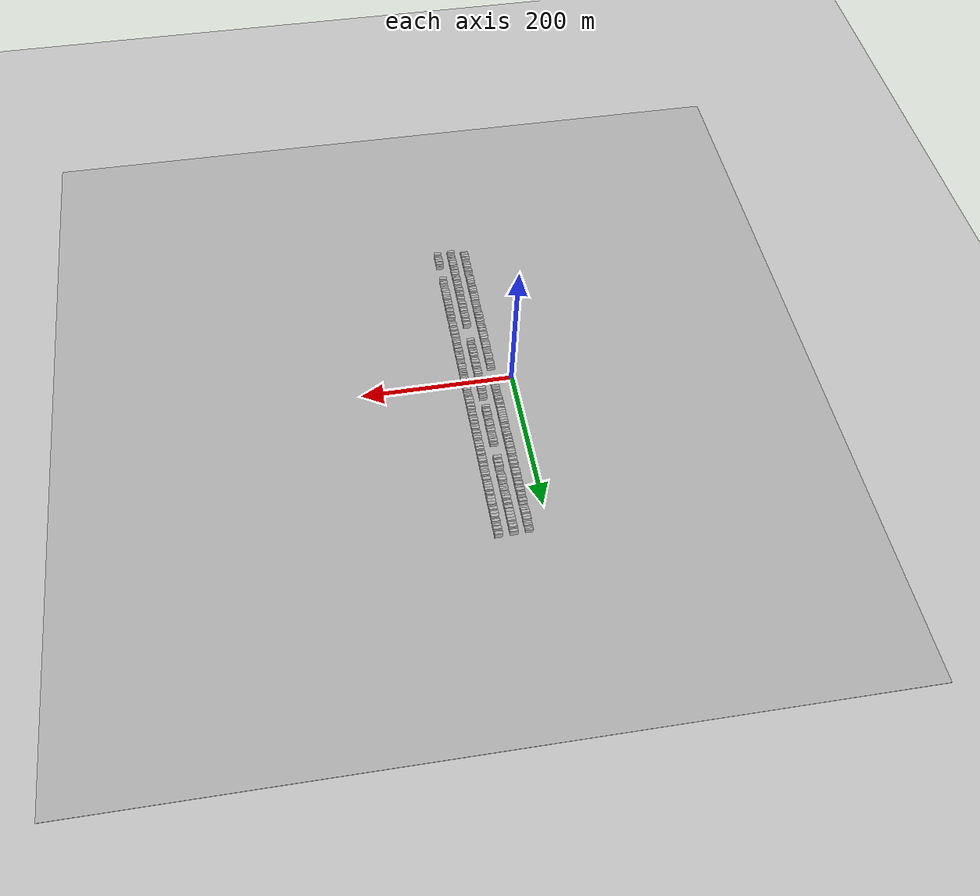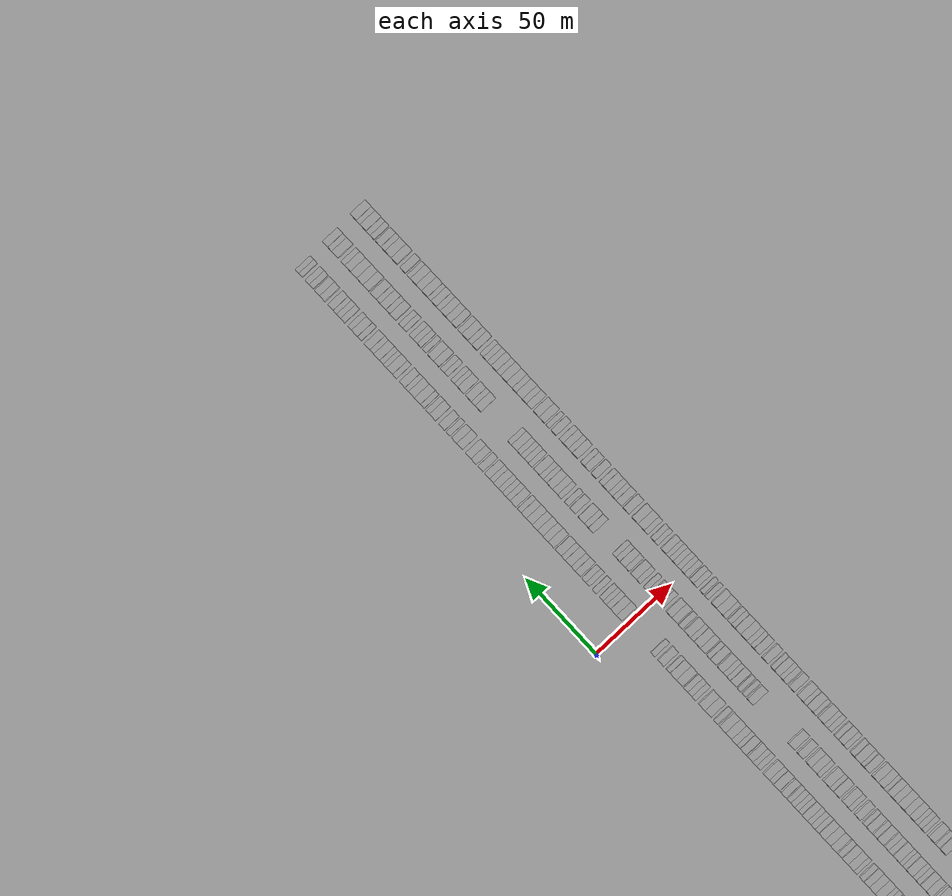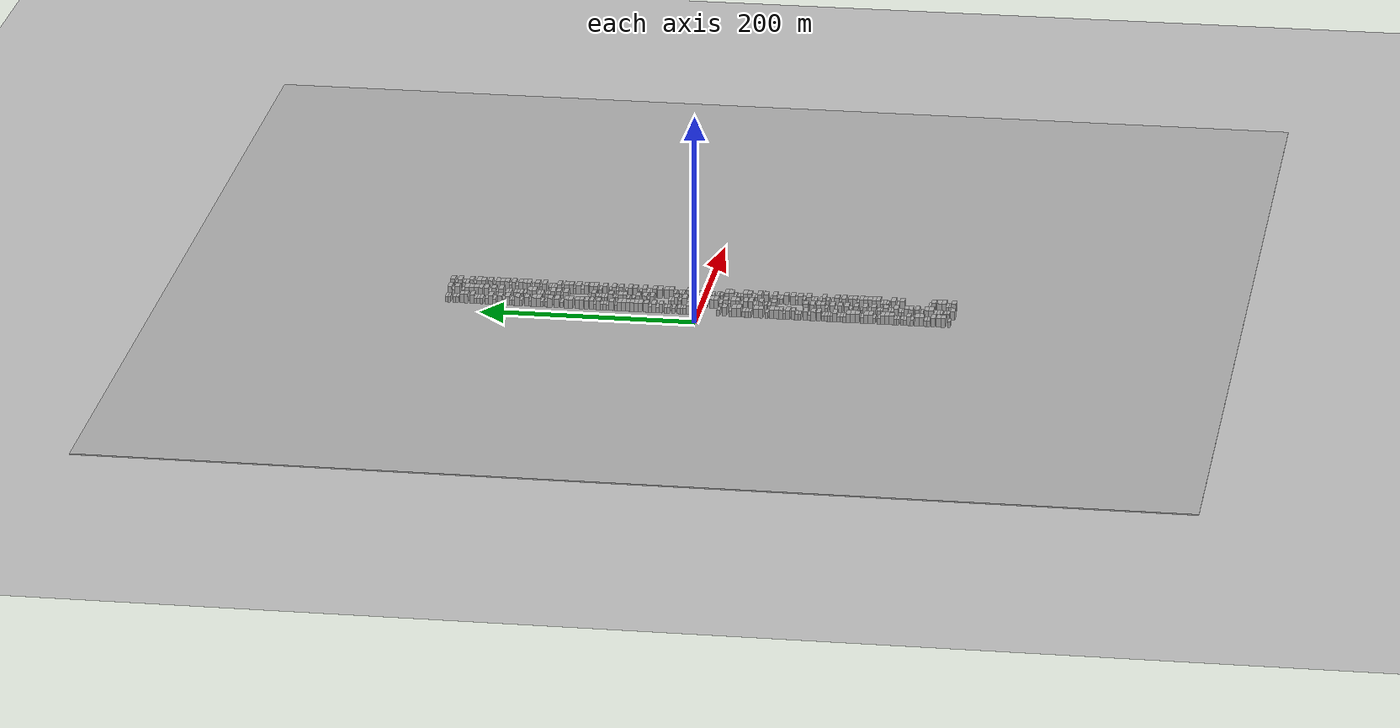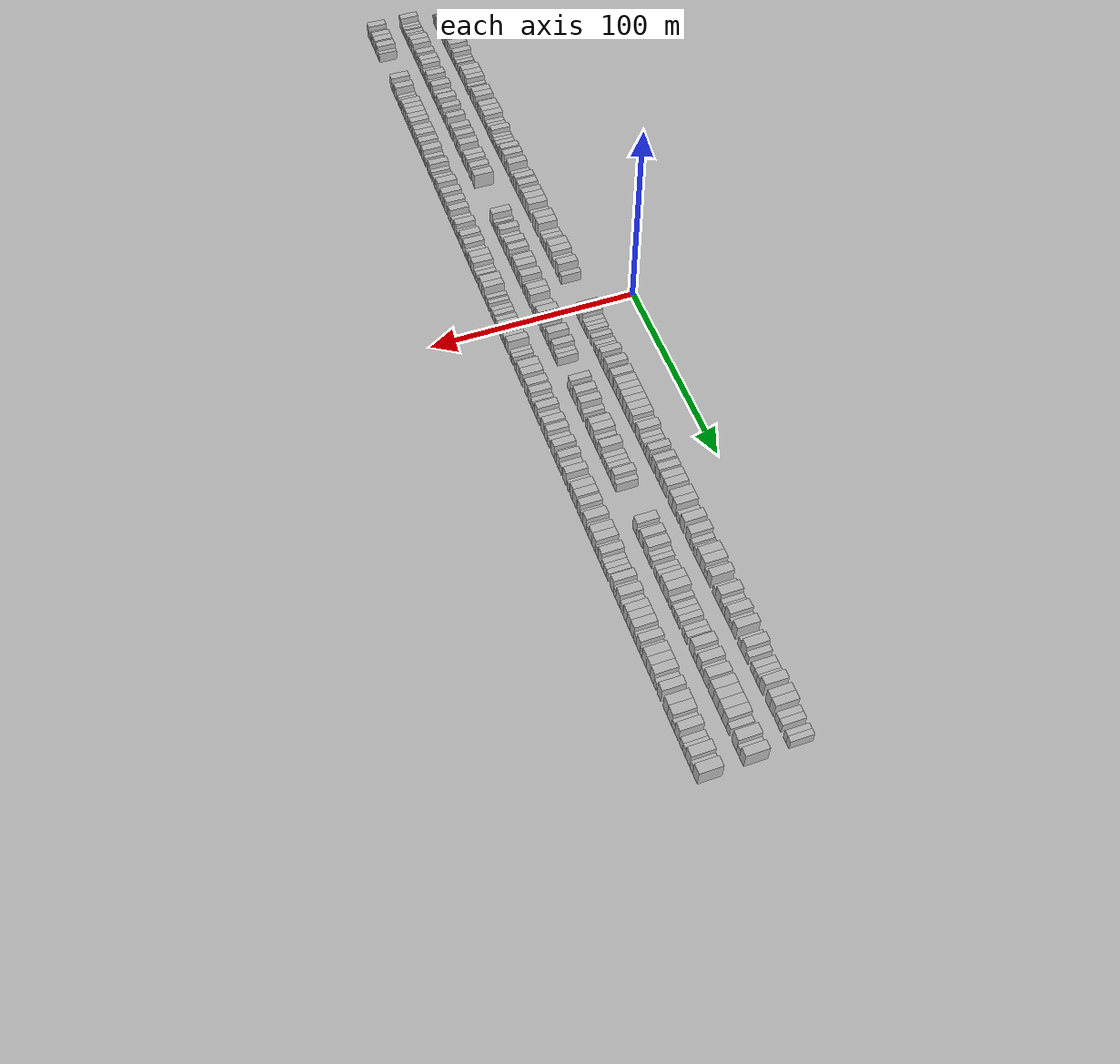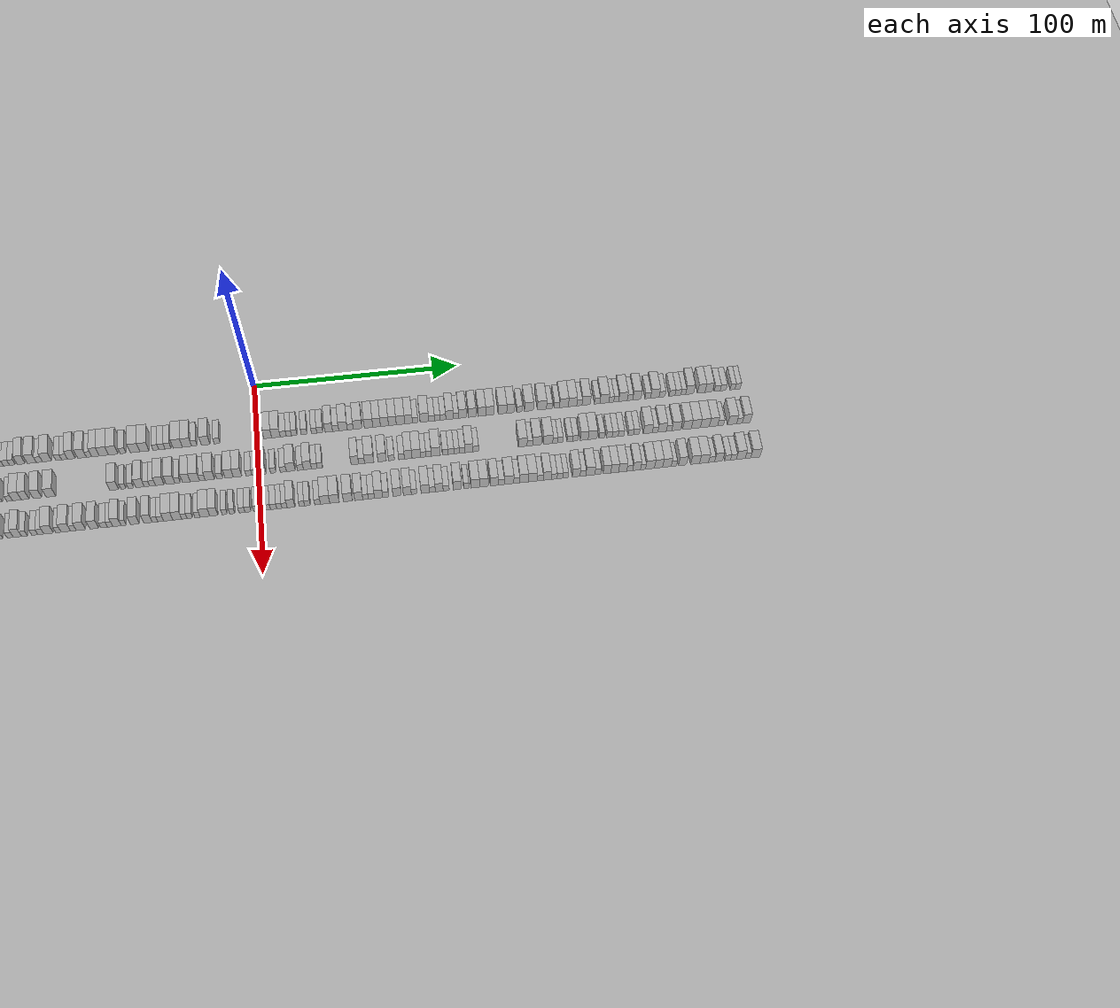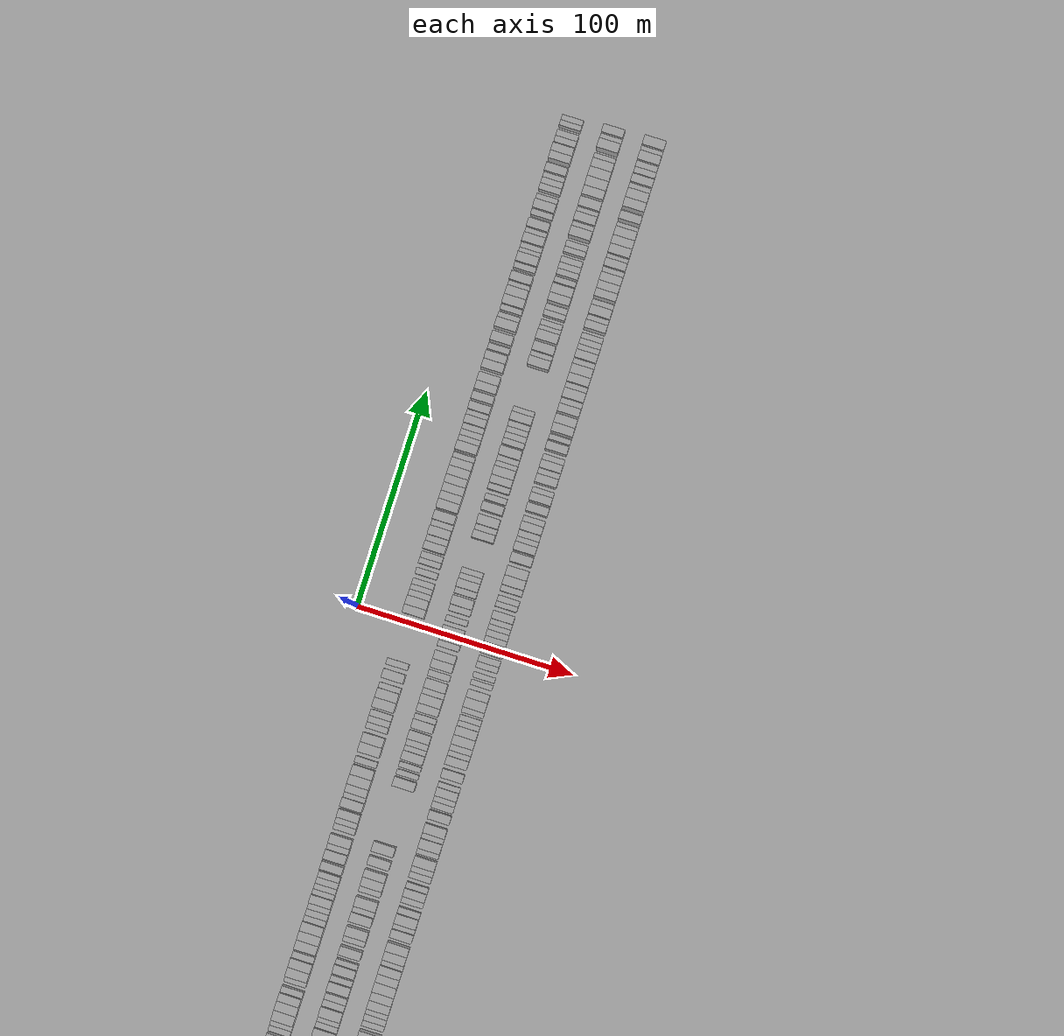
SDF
<?xml version="1.0" encoding="utf-8"?>

<sdf version="1.6">

   <world name="default">

      <gui fullscreen="0">

         <camera name="user_camera">

            <pose>-15 0 4.57585 0 0 0</pose>

            <view_controller>orbit</view_controller>

         </camera>

      </gui>

      <scene>

         <sky>

           <clouds>

             <speed>12</speed>

           </clouds>

         </sky>

         <ambient>0.4 0.4 0.4 1</ambient>

         <background>0.7 0.7 0.7 1</background>

         <shadows>1</shadows>

      </scene>

      <gravity>0 0 -9.8066</gravity>

      <magnetic_field>6e-06 2.3e-05 -4.2e-05</magnetic_field>

      <physics default="0" name="default_physics" type="ode">

         <ode>

            <solver>

               <type>quick</type>

               <iters>10</iters>

               <sor>1.0</sor>

               <use_dynamic_moi_rescaling>0</use_dynamic_moi_rescaling>

            </solver>

            <constraints>

               <cfm>0</cfm>

               <erp>0.2</erp>

               <contact_max_correcting_vel>100</contact_max_correcting_vel>

               <contact_surface_layer>0.001</contact_surface_layer>

            </constraints>

         </ode>

         <max_step_size>0.004</max_step_size>

         <real_time_factor>1</real_time_factor>

         <real_time_update_rate>250</real_time_update_rate>

      </physics>

      <light name="sun" type="directional">

         <cast_shadows>1</cast_shadows>

         <pose>0 0 10 0 0 0</pose>

         <diffuse>0.8 0.8 0.8 1</diffuse>

         <specular>0.2 0.2 0.2 1</specular>

         <attenuation>

            <range>1000</range>

            <constant>0.9</constant>

            <linear>0.01</linear>

            <quadratic>0.001</quadratic>

         </attenuation>

         <direction>-0.5 0.1 -0.9</direction>

      </light>

      <include>

         <name>ground_plane_1</name>

         <uri>model://HANNAS_ground_plane</uri>

         <pose>0 0 0  0 0 0</pose>

      </include>

      <include>

         <name>ground_plane_2</name>

         <uri>model://HANNAS_ground_plane</uri>

         <pose>100 0 0  0 0 0</pose>

      </include>

      <model name="building_1">

         <static>1</static>

         <pose frame="">25.0000 -232.7464 0 0.000000 0.000000 0.000000</pose>

         <link name="link">

            <pose frame="">0 0 3.00 0 0 0</pose>

            <collision name="collision">

               <geometry>

                  <box>

                     <size>10.0000 2.5072 6.0000</size>

                  </box>

               </geometry>

               <max_contacts>10</max_contacts>

               <surface>

                  <contact>

                     <ode/>

                  </contact>

                  <bounce/>

                  <friction>

                     <torsional>

                        <ode/>

                     </torsional>

                     <ode/>

                  </friction>

               </surface>

            </collision>

            <visual name="visual">

               <cast_shadows>0</cast_shadows>

               <geometry>

                  <box>

                     <size>10.0000 2.5072 6.0000</size>

                  </box>

               </geometry>

               <material>

                  <script>

                     <uri>model://HANNAS_wall/materials/scripts</uri>

                     <uri>model://HANNAS_wall/materials/textures</uri>

                     <name>vrc/HANNAS_wall</name>

                  </script>

               </material>

            </visual>

            <self_collide>0</self_collide>

            <enable_wind>0</enable_wind>

            <kinematic>0</kinematic>

         </link>

      </model>

      <model name="building_2">

         <static>1</static>

         <pose frame="">25.0000 -227.3734 0 0.000000 0.000000 0.000000</pose>

         <link name="link">

            <pose frame="">0 0 4.50 0 0 0</pose>

            <collision name="collision">

               <geometry>

                  <box>

                     <size>10.0000 4.2387 9.0000</size>

                  </box>

               </geometry>

               <max_contacts>10</max_contacts>

               <surface>

                  <contact>

                     <ode/>

                  </contact>

                  <bounce/>

                  <friction>

                     <torsional>

                        <ode/>

                     </torsional>

                     <ode/>

                  </friction>

               </surface>

            </collision>

            <visual name="visual">

               <cast_shadows>0</cast_shadows>

               <geometry>

                  <box>

                     <size>10.0000 4.2387 9.0000</size>

                  </box>

               </geometry>

               <material>

                  <script>

                     <uri>model://HANNAS_wall/materials/scripts</uri>

                     <uri>model://HANNAS_wall/materials/textures</uri>

                     <name>vrc/HANNAS_wall</name>

                  </script>

               </material>

            </visual>

            <self_collide>0</self_collide>

            <enable_wind>0</enable_wind>

            <kinematic>0</kinematic>

         </link>

      </model>

      <model name="building_3">

         <static>1</static>

         <pose frame="">25.0000 -223.1973 0 0.000000 0.000000 0.000000</pose>

         <link name="link">

            <pose frame="">0 0 4.50 0 0 0</pose>

            <collision name="collision">

               <geometry>

                  <box>

                     <size>10.0000 4.1135 9.0000</size>

                  </box>

               </geometry>

               <max_contacts>10</max_contacts>

               <surface>

                  <contact>

                     <ode/>

                  </contact>

                  <bounce/>

                  <friction>

                     <torsional>

                        <ode/>

                     </torsional>

                     <ode/>

                  </friction>

               </surface>

            </collision>

            <visual name="visual">

               <cast_shadows>0</cast_shadows>

               <geometry>

                  <box>

                     <size>10.0000 4.1135 9.0000</size>

                  </box>

               </geometry>

               <material>

                  <script>

                     <uri>model://HANNAS_wall/materials/scripts</uri>

                     <uri>model://HANNAS_wall/materials/textures</uri>

                     <name>vrc/HANNAS_wall</name>

                  </script>

               </material>

            </visual>

            <self_collide>0</self_collide>

            <enable_wind>0</enable_wind>

            <kinematic>0</kinematic>

         </link>

      </model>

      <model name="building_4">

         <static>1</static>

         <pose frame="">25.0000 -218.0938 0 0.000000 0.000000 0.000000</pose>

         <link name="link">

            <pose frame="">0 0 4.50 0 0 0</pose>

            <collision name="collision">

               <geometry>

                  <box>

                     <size>10.0000 4.0936 9.0000</size>

                  </box>

               </geometry>

               <max_contacts>10</max_contacts>

               <surface>

                  <contact>

                     <ode/>

                  </contact>

                  <bounce/>

                  <friction>

                     <torsional>

                        <ode/>

                     </torsional>

                     <ode/>

                  </friction>

               </surface>

            </collision>

            <visual name="visual">

               <cast_shadows>0</cast_shadows>

               <geometry>

                  <box>

                     <size>10.0000 4.0936 9.0000</size>

                  </box>

               </geometry>

               <material>

                  <script>

                     <uri>model://HANNAS_wall/materials/scripts</uri>

                     <uri>model://HANNAS_wall/materials/textures</uri>

                     <name>vrc/HANNAS_wall</name>

                  </script>

               </material>

            </visual>

            <self_collide>0</self_collide>

            <enable_wind>0</enable_wind>

            <kinematic>0</kinematic>

         </link>

      </model>

      <model name="building_5">

         <static>1</static>

         <pose frame="">25.0000 -213.6600 0 0.000000 0.000000 0.000000</pose>

         <link name="link">

            <pose frame="">0 0 3.00 0 0 0</pose>

            <collision name="collision">

               <geometry>

                  <box>

                     <size>10.0000 2.7739 6.0000</size>

                  </box>

               </geometry>

               <max_contacts>10</max_contacts>

               <surface>

                  <contact>

                     <ode/>

                  </contact>

                  <bounce/>

                  <friction>

                     <torsional>

                        <ode/>

                     </torsional>

                     <ode/>

                  </friction>

               </surface>

            </collision>

            <visual name="visual">

               <cast_shadows>0</cast_shadows>

               <geometry>

                  <box>

                     <size>10.0000 2.7739 6.0000</size>

                  </box>

               </geometry>

               <material>

                  <script>

                     <uri>model://HANNAS_wall/materials/scripts</uri>

                     <uri>model://HANNAS_wall/materials/textures</uri>

                     <name>vrc/HANNAS_wall</name>

                  </script>

               </material>

            </visual>

            <self_collide>0</self_collide>

            <enable_wind>0</enable_wind>

            <kinematic>0</kinematic>

         </link>

      </model>

      <model name="building_6">

         <static>1</static>

         <pose frame="">25.0000 -210.8924 0 0.000000 0.000000 0.000000</pose>

         <link name="link">

            <pose frame="">0 0 3.00 0 0 0</pose>

            <collision name="collision">

               <geometry>

                  <box>

                     <size>10.0000 2.7613 6.0000</size>

                  </box>

               </geometry>

               <max_contacts>10</max_contacts>

               <surface>

                  <contact>

                     <ode/>

                  </contact>

                  <bounce/>

                  <friction>

                     <torsional>

                        <ode/>

                     </torsional>

                     <ode/>

                  </friction>

               </surface>

            </collision>

            <visual name="visual">

               <cast_shadows>0</cast_shadows>

               <geometry>

                  <box>

                     <size>10.0000 2.7613 6.0000</size>

                  </box>

               </geometry>

               <material>

                  <script>

                     <uri>model://HANNAS_wall/materials/scripts</uri>

                     <uri>model://HANNAS_wall/materials/textures</uri>

                     <name>vrc/HANNAS_wall</name>

                  </script>

               </material>

            </visual>

            <self_collide>0</self_collide>

            <enable_wind>0</enable_wind>

            <kinematic>0</kinematic>

         </link>

      </model>

      <model name="building_7">

         <static>1</static>

         <pose frame="">25.0000 -207.4235 0 0.000000 0.000000 0.000000</pose>

         <link name="link">

            <pose frame="">0 0 4.50 0 0 0</pose>

            <collision name="collision">

               <geometry>

                  <box>

                     <size>10.0000 4.1765 9.0000</size>

                  </box>

               </geometry>

               <max_contacts>10</max_contacts>

               <surface>

                  <contact>

                     <ode/>

                  </contact>

                  <bounce/>

                  <friction>

                     <torsional>

                        <ode/>

                     </torsional>

                     <ode/>

                  </friction>

               </surface>

            </collision>

            <visual name="visual">

               <cast_shadows>0</cast_shadows>

               <geometry>

                  <box>

                     <size>10.0000 4.1765 9.0000</size>

                  </box>

               </geometry>

               <material>

                  <script>

                     <uri>model://HANNAS_wall/materials/scripts</uri>

                     <uri>model://HANNAS_wall/materials/textures</uri>

                     <name>vrc/HANNAS_wall</name>

                  </script>

               </material>

            </visual>

            <self_collide>0</self_collide>

            <enable_wind>0</enable_wind>

            <kinematic>0</kinematic>

         </link>

      </model>

      <model name="building_8">

         <static>1</static>

         <pose frame="">25.0000 -203.1562 0 0.000000 0.000000 0.000000</pose>

         <link name="link">

            <pose frame="">0 0 4.50 0 0 0</pose>

            <collision name="collision">

               <geometry>

                  <box>

                     <size>10.0000 4.3580 9.0000</size>

                  </box>

               </geometry>

               <max_contacts>10</max_contacts>

               <surface>

                  <contact>

                     <ode/>

                  </contact>

                  <bounce/>

                  <friction>

                     <torsional>

                        <ode/>

                     </torsional>

                     <ode/>

                  </friction>

               </surface>

            </collision>

            <visual name="visual">

               <cast_shadows>0</cast_shadows>

               <geometry>

                  <box>

                     <size>10.0000 4.3580 9.0000</size>

                  </box>

               </geometry>

               <material>

                  <script>

                     <uri>model://HANNAS_wall/materials/scripts</uri>

                     <uri>model://HANNAS_wall/materials/textures</uri>

                     <name>vrc/HANNAS_wall</name>

                  </script>

               </material>

            </visual>

            <self_collide>0</self_collide>

            <enable_wind>0</enable_wind>

            <kinematic>0</kinematic>

         </link>

      </model>

      <model name="building_9">

         <static>1</static>

         <pose frame="">25.0000 -198.5310 0 0.000000 0.000000 0.000000</pose>

         <link name="link">

            <pose frame="">0 0 3.00 0 0 0</pose>

            <collision name="collision">

               <geometry>

                  <box>

                     <size>10.0000 2.8926 6.0000</size>

                  </box>

               </geometry>

               <max_contacts>10</max_contacts>

               <surface>

                  <contact>

                     <ode/>

                  </contact>

                  <bounce/>

                  <friction>

                     <torsional>

                        <ode/>

                     </torsional>

                     <ode/>

                  </friction>

               </surface>

            </collision>

            <visual name="visual">

               <cast_shadows>0</cast_shadows>

               <geometry>

                  <box>

                     <size>10.0000 2.8926 6.0000</size>

                  </box>

               </geometry>

               <material>

                  <script>

                     <uri>model://HANNAS_wall/materials/scripts</uri>

                     <uri>model://HANNAS_wall/materials/textures</uri>

                     <name>vrc/HANNAS_wall</name>

                  </script>

               </material>

            </visual>

            <self_collide>0</self_collide>

            <enable_wind>0</enable_wind>

            <kinematic>0</kinematic>

         </link>

      </model>

      <model name="building_10">

         <static>1</static>

         <pose frame="">25.0000 -195.1847 0 0.000000 0.000000 0.000000</pose>

         <link name="link">

            <pose frame="">0 0 4.50 0 0 0</pose>

            <collision name="collision">

               <geometry>

                  <box>

                     <size>10.0000 3.8000 9.0000</size>

                  </box>

               </geometry>

               <max_contacts>10</max_contacts>

               <surface>

                  <contact>

                     <ode/>

                  </contact>

                  <bounce/>

                  <friction>

                     <torsional>

                        <ode/>

                     </torsional>

                     <ode/>

                  </friction>

               </surface>

            </collision>

            <visual name="visual">

               <cast_shadows>0</cast_shadows>

               <geometry>

                  <box>

                     <size>10.0000 3.8000 9.0000</size>

                  </box>

               </geometry>

               <material>

                  <script>

                     <uri>model://HANNAS_wall/materials/scripts</uri>

                     <uri>model://HANNAS_wall/materials/textures</uri>

                     <name>vrc/HANNAS_wall</name>

                  </script>

               </material>

            </visual>

            <self_collide>0</self_collide>

            <enable_wind>0</enable_wind>

            <kinematic>0</kinematic>

         </link>

      </model>

      <model name="building_11">

         <static>1</static>

         <pose frame="">25.0000 -191.9634 0 0.000000 0.000000 0.000000</pose>

         <link name="link">

            <pose frame="">0 0 3.00 0 0 0</pose>

            <collision name="collision">

               <geometry>

                  <box>

                     <size>10.0000 2.6426 6.0000</size>

                  </box>

               </geometry>

               <max_contacts>10</max_contacts>

               <surface>

                  <contact>

                     <ode/>

                  </contact>

                  <bounce/>

                  <friction>

                     <torsional>

                        <ode/>

                     </torsional>

                     <ode/>

                  </friction>

               </surface>

            </collision>

            <visual name="visual">

               <cast_shadows>0</cast_shadows>

               <geometry>

                  <box>

                     <size>10.0000 2.6426 6.0000</size>

                  </box>

               </geometry>

               <material>

                  <script>

                     <uri>model://HANNAS_wall/materials/scripts</uri>

                     <uri>model://HANNAS_wall/materials/textures</uri>

                     <name>vrc/HANNAS_wall</name>

                  </script>

               </material>

            </visual>

            <self_collide>0</self_collide>

            <enable_wind>0</enable_wind>

            <kinematic>0</kinematic>

         </link>

      </model>

      <model name="building_12">

         <static>1</static>

         <pose frame="">25.0000 -189.2580 0 0.000000 0.000000 0.000000</pose>

         <link name="link">

            <pose frame="">0 0 3.00 0 0 0</pose>

            <collision name="collision">

               <geometry>

                  <box>

                     <size>10.0000 2.7681 6.0000</size>

                  </box>

               </geometry>

               <max_contacts>10</max_contacts>

               <surface>

                  <contact>

                     <ode/>

                  </contact>

                  <bounce/>

                  <friction>

                     <torsional>

                        <ode/>

                     </torsional>

                     <ode/>

                  </friction>

               </surface>

            </collision>

            <visual name="visual">

               <cast_shadows>0</cast_shadows>

               <geometry>

                  <box>

                     <size>10.0000 2.7681 6.0000</size>

                  </box>

               </geometry>

               <material>

                  <script>

                     <uri>model://HANNAS_wall/materials/scripts</uri>

                     <uri>model://HANNAS_wall/materials/textures</uri>

                     <name>vrc/HANNAS_wall</name>

                  </script>

               </material>

            </visual>

            <self_collide>0</self_collide>

            <enable_wind>0</enable_wind>

            <kinematic>0</kinematic>

         </link>

      </model>

      <model name="building_13">

         <static>1</static>

         <pose frame="">25.0000 -185.5941 0 0.000000 0.000000 0.000000</pose>

         <link name="link">

            <pose frame="">0 0 3.00 0 0 0</pose>

            <collision name="collision">

               <geometry>

                  <box>

                     <size>10.0000 2.5597 6.0000</size>

                  </box>

               </geometry>

               <max_contacts>10</max_contacts>

               <surface>

                  <contact>

                     <ode/>

                  </contact>

                  <bounce/>

                  <friction>

                     <torsional>

                        <ode/>

                     </torsional>

                     <ode/>

                  </friction>

               </surface>

            </collision>

            <visual name="visual">

               <cast_shadows>0</cast_shadows>

               <geometry>

                  <box>

                     <size>10.0000 2.5597 6.0000</size>

                  </box>

               </geometry>

               <material>

                  <script>

                     <uri>model://HANNAS_wall/materials/scripts</uri>

                     <uri>model://HANNAS_wall/materials/textures</uri>

                     <name>vrc/HANNAS_wall</name>

                  </script>

               </material>

            </visual>

            <self_collide>0</self_collide>

            <enable_wind>0</enable_wind>

            <kinematic>0</kinematic>

         </link>

      </model>

      <model name="building_14">

         <static>1</static>

         <pose frame="">25.0000 -183.0411 0 0.000000 0.000000 0.000000</pose>

         <link name="link">

            <pose frame="">0 0 3.00 0 0 0</pose>

            <collision name="collision">

               <geometry>

                  <box>

                     <size>10.0000 2.5462 6.0000</size>

                  </box>

               </geometry>

               <max_contacts>10</max_contacts>

               <surface>

                  <contact>

                     <ode/>

                  </contact>

                  <bounce/>

                  <friction>

                     <torsional>

                        <ode/>

                     </torsional>

                     <ode/>

                  </friction>

               </surface>

            </collision>

            <visual name="visual">

               <cast_shadows>0</cast_shadows>

               <geometry>

                  <box>

                     <size>10.0000 2.5462 6.0000</size>

                  </box>

               </geometry>

               <material>

                  <script>

                     <uri>model://HANNAS_wall/materials/scripts</uri>

                     <uri>model://HANNAS_wall/materials/textures</uri>

                     <name>vrc/HANNAS_wall</name>

                  </script>

               </material>

            </visual>

            <self_collide>0</self_collide>

            <enable_wind>0</enable_wind>

            <kinematic>0</kinematic>

         </link>

      </model>

      <model name="building_15">

         <static>1</static>

         <pose frame="">25.0000 -179.5298 0 0.000000 0.000000 0.000000</pose>

         <link name="link">

            <pose frame="">0 0 4.50 0 0 0</pose>

            <collision name="collision">

               <geometry>

                  <box>

                     <size>10.0000 4.4765 9.0000</size>

                  </box>

               </geometry>

               <max_contacts>10</max_contacts>

               <surface>

                  <contact>

                     <ode/>

                  </contact>

                  <bounce/>

                  <friction>

                     <torsional>

                        <ode/>

                     </torsional>

                     <ode/>

                  </friction>

               </surface>

            </collision>

            <visual name="visual">

               <cast_shadows>0</cast_shadows>

               <geometry>

                  <box>

                     <size>10.0000 4.4765 9.0000</size>

                  </box>

               </geometry>

               <material>

                  <script>

                     <uri>model://HANNAS_wall/materials/scripts</uri>

                     <uri>model://HANNAS_wall/materials/textures</uri>

                     <name>vrc/HANNAS_wall</name>

                  </script>

               </material>

            </visual>

            <self_collide>0</self_collide>

            <enable_wind>0</enable_wind>

            <kinematic>0</kinematic>

         </link>

      </model>

      <model name="building_16">

         <static>1</static>

         <pose frame="">25.0000 -175.2244 0 0.000000 0.000000 0.000000</pose>

         <link name="link">

            <pose frame="">0 0 4.50 0 0 0</pose>

            <collision name="collision">

               <geometry>

                  <box>

                     <size>10.0000 4.1342 9.0000</size>

                  </box>

               </geometry>

               <max_contacts>10</max_contacts>

               <surface>

                  <contact>

                     <ode/>

                  </contact>

                  <bounce/>

                  <friction>

                     <torsional>

                        <ode/>

                     </torsional>

                     <ode/>

                  </friction>

               </surface>

            </collision>

            <visual name="visual">

               <cast_shadows>0</cast_shadows>

               <geometry>

                  <box>

                     <size>10.0000 4.1342 9.0000</size>

                  </box>

               </geometry>

               <material>

                  <script>

                     <uri>model://HANNAS_wall/materials/scripts</uri>

                     <uri>model://HANNAS_wall/materials/textures</uri>

                     <name>vrc/HANNAS_wall</name>

                  </script>

               </material>

            </visual>

            <self_collide>0</self_collide>

            <enable_wind>0</enable_wind>

            <kinematic>0</kinematic>

         </link>

      </model>

      <model name="building_17">

         <static>1</static>

         <pose frame="">25.0000 -171.3254 0 0.000000 0.000000 0.000000</pose>

         <link name="link">

            <pose frame="">0 0 4.50 0 0 0</pose>

            <collision name="collision">

               <geometry>

                  <box>

                     <size>10.0000 3.6637 9.0000</size>

                  </box>

               </geometry>

               <max_contacts>10</max_contacts>

               <surface>

                  <contact>

                     <ode/>

                  </contact>

                  <bounce/>

                  <friction>

                     <torsional>

                        <ode/>

                     </torsional>

                     <ode/>

                  </friction>

               </surface>

            </collision>

            <visual name="visual">

               <cast_shadows>0</cast_shadows>

               <geometry>

                  <box>

                     <size>10.0000 3.6637 9.0000</size>

                  </box>

               </geometry>

               <material>

                  <script>

                     <uri>model://HANNAS_wall/materials/scripts</uri>

                     <uri>model://HANNAS_wall/materials/textures</uri>

                     <name>vrc/HANNAS_wall</name>

                  </script>

               </material>

            </visual>

            <self_collide>0</self_collide>

            <enable_wind>0</enable_wind>

            <kinematic>0</kinematic>

         </link>

      </model>

      <model name="building_18">

         <static>1</static>

         <pose frame="">25.0000 -168.0835 0 0.000000 0.000000 0.000000</pose>

         <link name="link">

            <pose frame="">0 0 3.00 0 0 0</pose>

            <collision name="collision">

               <geometry>

                  <box>

                     <size>10.0000 2.8201 6.0000</size>

                  </box>

               </geometry>

               <max_contacts>10</max_contacts>

               <surface>

                  <contact>

                     <ode/>

                  </contact>

                  <bounce/>

                  <friction>

                     <torsional>

                        <ode/>

                     </torsional>

                     <ode/>

                  </friction>

               </surface>

            </collision>

            <visual name="visual">

               <cast_shadows>0</cast_shadows>

               <geometry>

                  <box>

                     <size>10.0000 2.8201 6.0000</size>

                  </box>

               </geometry>

               <material>

                  <script>

                     <uri>model://HANNAS_wall/materials/scripts</uri>

                     <uri>model://HANNAS_wall/materials/textures</uri>

                     <name>vrc/HANNAS_wall</name>

                  </script>

               </material>

            </visual>

            <self_collide>0</self_collide>

            <enable_wind>0</enable_wind>

            <kinematic>0</kinematic>

         </link>

      </model>

      <model name="building_19">

         <static>1</static>

         <pose frame="">25.0000 -163.3988 0 0.000000 0.000000 0.000000</pose>

         <link name="link">

            <pose frame="">0 0 3.00 0 0 0</pose>

            <collision name="collision">

               <geometry>

                  <box>

                     <size>10.0000 2.5493 6.0000</size>

                  </box>

               </geometry>

               <max_contacts>10</max_contacts>

               <surface>

                  <contact>

                     <ode/>

                  </contact>

                  <bounce/>

                  <friction>

                     <torsional>

                        <ode/>

                     </torsional>

                     <ode/>

                  </friction>

               </surface>

            </collision>

            <visual name="visual">

               <cast_shadows>0</cast_shadows>

               <geometry>

                  <box>

                     <size>10.0000 2.5493 6.0000</size>

                  </box>

               </geometry>

               <material>

                  <script>

                     <uri>model://HANNAS_wall/materials/scripts</uri>

                     <uri>model://HANNAS_wall/materials/textures</uri>

                     <name>vrc/HANNAS_wall</name>

                  </script>

               </material>

            </visual>

            <self_collide>0</self_collide>

            <enable_wind>0</enable_wind>

            <kinematic>0</kinematic>

         </link>

      </model>

      <model name="building_20">

         <static>1</static>

         <pose frame="">25.0000 -160.0751 0 0.000000 0.000000 0.000000</pose>

         <link name="link">

            <pose frame="">0 0 4.50 0 0 0</pose>

            <collision name="collision">

               <geometry>

                  <box>

                     <size>10.0000 4.0981 9.0000</size>

                  </box>

               </geometry>

               <max_contacts>10</max_contacts>

               <surface>

                  <contact>

                     <ode/>

                  </contact>

                  <bounce/>

                  <friction>

                     <torsional>

                        <ode/>

                     </torsional>

                     <ode/>

                  </friction>

               </surface>

            </collision>

            <visual name="visual">

               <cast_shadows>0</cast_shadows>

               <geometry>

                  <box>

                     <size>10.0000 4.0981 9.0000</size>

                  </box>

               </geometry>

               <material>

                  <script>

                     <uri>model://HANNAS_wall/materials/scripts</uri>

                     <uri>model://HANNAS_wall/materials/textures</uri>

                     <name>vrc/HANNAS_wall</name>

                  </script>

               </material>

            </visual>

            <self_collide>0</self_collide>

            <enable_wind>0</enable_wind>

            <kinematic>0</kinematic>

         </link>

      </model>

      <model name="building_21">

         <static>1</static>

         <pose frame="">25.0000 -155.9558 0 0.000000 0.000000 0.000000</pose>

         <link name="link">

            <pose frame="">0 0 4.50 0 0 0</pose>

            <collision name="collision">

               <geometry>

                  <box>

                     <size>10.0000 4.1404 9.0000</size>

                  </box>

               </geometry>

               <max_contacts>10</max_contacts>

               <surface>

                  <contact>

                     <ode/>

                  </contact>

                  <bounce/>

                  <friction>

                     <torsional>

                        <ode/>

                     </torsional>

                     <ode/>

                  </friction>

               </surface>

            </collision>

            <visual name="visual">

               <cast_shadows>0</cast_shadows>

               <geometry>

                  <box>

                     <size>10.0000 4.1404 9.0000</size>

                  </box>

               </geometry>

               <material>

                  <script>

                     <uri>model://HANNAS_wall/materials/scripts</uri>

                     <uri>model://HANNAS_wall/materials/textures</uri>

                     <name>vrc/HANNAS_wall</name>

                  </script>

               </material>

            </visual>

            <self_collide>0</self_collide>

            <enable_wind>0</enable_wind>

            <kinematic>0</kinematic>

         </link>

      </model>

      <model name="building_22">

         <static>1</static>

         <pose frame="">25.0000 -152.3985 0 0.000000 0.000000 0.000000</pose>

         <link name="link">

            <pose frame="">0 0 3.00 0 0 0</pose>

            <collision name="collision">

               <geometry>

                  <box>

                     <size>10.0000 2.9743 6.0000</size>

                  </box>

               </geometry>

               <max_contacts>10</max_contacts>

               <surface>

                  <contact>

                     <ode/>

                  </contact>

                  <bounce/>

                  <friction>

                     <torsional>

                        <ode/>

                     </torsional>

                     <ode/>

                  </friction>

               </surface>

            </collision>

            <visual name="visual">

               <cast_shadows>0</cast_shadows>

               <geometry>

                  <box>

                     <size>10.0000 2.9743 6.0000</size>

                  </box>

               </geometry>

               <material>

                  <script>

                     <uri>model://HANNAS_wall/materials/scripts</uri>

                     <uri>model://HANNAS_wall/materials/textures</uri>

                     <name>vrc/HANNAS_wall</name>

                  </script>

               </material>

            </visual>

            <self_collide>0</self_collide>

            <enable_wind>0</enable_wind>

            <kinematic>0</kinematic>

         </link>

      </model>

      <model name="building_23">

         <static>1</static>

         <pose frame="">25.0000 -147.8059 0 0.000000 0.000000 0.000000</pose>

         <link name="link">

            <pose frame="">0 0 4.50 0 0 0</pose>

            <collision name="collision">

               <geometry>

                  <box>

                     <size>10.0000 4.2109 9.0000</size>

                  </box>

               </geometry>

               <max_contacts>10</max_contacts>

               <surface>

                  <contact>

                     <ode/>

                  </contact>

                  <bounce/>

                  <friction>

                     <torsional>

                        <ode/>

                     </torsional>

                     <ode/>

                  </friction>

               </surface>

            </collision>

            <visual name="visual">

               <cast_shadows>0</cast_shadows>

               <geometry>

                  <box>

                     <size>10.0000 4.2109 9.0000</size>

                  </box>

               </geometry>

               <material>

                  <script>

                     <uri>model://HANNAS_wall/materials/scripts</uri>

                     <uri>model://HANNAS_wall/materials/textures</uri>

                     <name>vrc/HANNAS_wall</name>

                  </script>

               </material>

            </visual>

            <self_collide>0</self_collide>

            <enable_wind>0</enable_wind>

            <kinematic>0</kinematic>

         </link>

      </model>

      <model name="building_24">

         <static>1</static>

         <pose frame="">25.0000 -143.6487 0 0.000000 0.000000 0.000000</pose>

         <link name="link">

            <pose frame="">0 0 4.50 0 0 0</pose>

            <collision name="collision">

               <geometry>

                  <box>

                     <size>10.0000 4.1034 9.0000</size>

                  </box>

               </geometry>

               <max_contacts>10</max_contacts>

               <surface>

                  <contact>

                     <ode/>

                  </contact>

                  <bounce/>

                  <friction>

                     <torsional>

                        <ode/>

                     </torsional>

                     <ode/>

                  </friction>

               </surface>

            </collision>

            <visual name="visual">

               <cast_shadows>0</cast_shadows>

               <geometry>

                  <box>

                     <size>10.0000 4.1034 9.0000</size>

                  </box>

               </geometry>

               <material>

                  <script>

                     <uri>model://HANNAS_wall/materials/scripts</uri>

                     <uri>model://HANNAS_wall/materials/textures</uri>

                     <name>vrc/HANNAS_wall</name>

                  </script>

               </material>

            </visual>

            <self_collide>0</self_collide>

            <enable_wind>0</enable_wind>

            <kinematic>0</kinematic>

         </link>

      </model>

      <model name="building_25">

         <static>1</static>

         <pose frame="">25.0000 -139.5028 0 0.000000 0.000000 0.000000</pose>

         <link name="link">

            <pose frame="">0 0 4.50 0 0 0</pose>

            <collision name="collision">

               <geometry>

                  <box>

                     <size>10.0000 4.1885 9.0000</size>

                  </box>

               </geometry>

               <max_contacts>10</max_contacts>

               <surface>

                  <contact>

                     <ode/>

                  </contact>

                  <bounce/>

                  <friction>

                     <torsional>

                        <ode/>

                     </torsional>

                     <ode/>

                  </friction>

               </surface>

            </collision>

            <visual name="visual">

               <cast_shadows>0</cast_shadows>

               <geometry>

                  <box>

                     <size>10.0000 4.1885 9.0000</size>

                  </box>

               </geometry>

               <material>

                  <script>

                     <uri>model://HANNAS_wall/materials/scripts</uri>

                     <uri>model://HANNAS_wall/materials/textures</uri>

                     <name>vrc/HANNAS_wall</name>

                  </script>

               </material>

            </visual>

            <self_collide>0</self_collide>

            <enable_wind>0</enable_wind>

            <kinematic>0</kinematic>

         </link>

      </model>

      <model name="building_26">

         <static>1</static>

         <pose frame="">25.0000 -136.0570 0 0.000000 0.000000 0.000000</pose>

         <link name="link">

            <pose frame="">0 0 3.00 0 0 0</pose>

            <collision name="collision">

               <geometry>

                  <box>

                     <size>10.0000 2.7031 6.0000</size>

                  </box>

               </geometry>

               <max_contacts>10</max_contacts>

               <surface>

                  <contact>

                     <ode/>

                  </contact>

                  <bounce/>

                  <friction>

                     <torsional>

                        <ode/>

                     </torsional>

                     <ode/>

                  </friction>

               </surface>

            </collision>

            <visual name="visual">

               <cast_shadows>0</cast_shadows>

               <geometry>

                  <box>

                     <size>10.0000 2.7031 6.0000</size>

                  </box>

               </geometry>

               <material>

                  <script>

                     <uri>model://HANNAS_wall/materials/scripts</uri>

                     <uri>model://HANNAS_wall/materials/textures</uri>

                     <name>vrc/HANNAS_wall</name>

                  </script>

               </material>

            </visual>

            <self_collide>0</self_collide>

            <enable_wind>0</enable_wind>

            <kinematic>0</kinematic>

         </link>

      </model>

      <model name="building_27">

         <static>1</static>

         <pose frame="">25.0000 -133.2723 0 0.000000 0.000000 0.000000</pose>

         <link name="link">

            <pose frame="">0 0 3.00 0 0 0</pose>

            <collision name="collision">

               <geometry>

                  <box>

                     <size>10.0000 2.8663 6.0000</size>

                  </box>

               </geometry>

               <max_contacts>10</max_contacts>

               <surface>

                  <contact>

                     <ode/>

                  </contact>

                  <bounce/>

                  <friction>

                     <torsional>

                        <ode/>

                     </torsional>

                     <ode/>

                  </friction>

               </surface>

            </collision>

            <visual name="visual">

               <cast_shadows>0</cast_shadows>

               <geometry>

                  <box>

                     <size>10.0000 2.8663 6.0000</size>

                  </box>

               </geometry>

               <material>

                  <script>

                     <uri>model://HANNAS_wall/materials/scripts</uri>

                     <uri>model://HANNAS_wall/materials/textures</uri>

                     <name>vrc/HANNAS_wall</name>

                  </script>

               </material>

            </visual>

            <self_collide>0</self_collide>

            <enable_wind>0</enable_wind>

            <kinematic>0</kinematic>

         </link>

      </model>

      <model name="building_28">

         <static>1</static>

         <pose frame="">25.0000 -130.4204 0 0.000000 0.000000 0.000000</pose>

         <link name="link">

            <pose frame="">0 0 3.00 0 0 0</pose>

            <collision name="collision">

               <geometry>

                  <box>

                     <size>10.0000 2.8375 6.0000</size>

                  </box>

               </geometry>

               <max_contacts>10</max_contacts>

               <surface>

                  <contact>

                     <ode/>

                  </contact>

                  <bounce/>

                  <friction>

                     <torsional>

                        <ode/>

                     </torsional>

                     <ode/>

                  </friction>

               </surface>

            </collision>

            <visual name="visual">

               <cast_shadows>0</cast_shadows>

               <geometry>

                  <box>

                     <size>10.0000 2.8375 6.0000</size>

                  </box>

               </geometry>

               <material>

                  <script>

                     <uri>model://HANNAS_wall/materials/scripts</uri>

                     <uri>model://HANNAS_wall/materials/textures</uri>

                     <name>vrc/HANNAS_wall</name>

                  </script>

               </material>

            </visual>

            <self_collide>0</self_collide>

            <enable_wind>0</enable_wind>

            <kinematic>0</kinematic>

         </link>

      </model>

      <model name="building_29">

         <static>1</static>

         <pose frame="">25.0000 -127.1035 0 0.000000 0.000000 0.000000</pose>

         <link name="link">

            <pose frame="">0 0 4.50 0 0 0</pose>

            <collision name="collision">

               <geometry>

                  <box>

                     <size>10.0000 3.7964 9.0000</size>

                  </box>

               </geometry>

               <max_contacts>10</max_contacts>

               <surface>

                  <contact>

                     <ode/>

                  </contact>

                  <bounce/>

                  <friction>

                     <torsional>

                        <ode/>

                     </torsional>

                     <ode/>

                  </friction>

               </surface>

            </collision>

            <visual name="visual">

               <cast_shadows>0</cast_shadows>

               <geometry>

                  <box>

                     <size>10.0000 3.7964 9.0000</size>

                  </box>

               </geometry>

               <material>

                  <script>

                     <uri>model://HANNAS_wall/materials/scripts</uri>

                     <uri>model://HANNAS_wall/materials/textures</uri>

                     <name>vrc/HANNAS_wall</name>

                  </script>

               </material>

            </visual>

            <self_collide>0</self_collide>

            <enable_wind>0</enable_wind>

            <kinematic>0</kinematic>

         </link>

      </model>

      <model name="building_30">

         <static>1</static>

         <pose frame="">25.0000 -123.9987 0 0.000000 0.000000 0.000000</pose>

         <link name="link">

            <pose frame="">0 0 3.00 0 0 0</pose>

            <collision name="collision">

               <geometry>

                  <box>

                     <size>10.0000 2.4132 6.0000</size>

                  </box>

               </geometry>

               <max_contacts>10</max_contacts>

               <surface>

                  <contact>

                     <ode/>

                  </contact>

                  <bounce/>

                  <friction>

                     <torsional>

                        <ode/>

                     </torsional>

                     <ode/>

                  </friction>

               </surface>

            </collision>

            <visual name="visual">

               <cast_shadows>0</cast_shadows>

               <geometry>

                  <box>

                     <size>10.0000 2.4132 6.0000</size>

                  </box>

               </geometry>

               <material>

                  <script>

                     <uri>model://HANNAS_wall/materials/scripts</uri>

                     <uri>model://HANNAS_wall/materials/textures</uri>

                     <name>vrc/HANNAS_wall</name>

                  </script>

               </material>

            </visual>

            <self_collide>0</self_collide>

            <enable_wind>0</enable_wind>

            <kinematic>0</kinematic>

         </link>

      </model>

      <model name="building_31">

         <static>1</static>

         <pose frame="">25.0000 -121.5376 0 0.000000 0.000000 0.000000</pose>

         <link name="link">

            <pose frame="">0 0 3.00 0 0 0</pose>

            <collision name="collision">

               <geometry>

                  <box>

                     <size>10.0000 2.5090 6.0000</size>

                  </box>

               </geometry>

               <max_contacts>10</max_contacts>

               <surface>

                  <contact>

                     <ode/>

                  </contact>

                  <bounce/>

                  <friction>

                     <torsional>

                        <ode/>

                     </torsional>

                     <ode/>

                  </friction>

               </surface>

            </collision>

            <visual name="visual">

               <cast_shadows>0</cast_shadows>

               <geometry>

                  <box>

                     <size>10.0000 2.5090 6.0000</size>

                  </box>

               </geometry>

               <material>

                  <script>

                     <uri>model://HANNAS_wall/materials/scripts</uri>

                     <uri>model://HANNAS_wall/materials/textures</uri>

                     <name>vrc/HANNAS_wall</name>

                  </script>

               </material>

            </visual>

            <self_collide>0</self_collide>

            <enable_wind>0</enable_wind>

            <kinematic>0</kinematic>

         </link>

      </model>

      <model name="building_32">

         <static>1</static>

         <pose frame="">25.0000 -118.8527 0 0.000000 0.000000 0.000000</pose>

         <link name="link">

            <pose frame="">0 0 3.00 0 0 0</pose>

            <collision name="collision">

               <geometry>

                  <box>

                     <size>10.0000 2.8610 6.0000</size>

                  </box>

               </geometry>

               <max_contacts>10</max_contacts>

               <surface>

                  <contact>

                     <ode/>

                  </contact>

                  <bounce/>

                  <friction>

                     <torsional>

                        <ode/>

                     </torsional>

                     <ode/>

                  </friction>

               </surface>

            </collision>

            <visual name="visual">

               <cast_shadows>0</cast_shadows>

               <geometry>

                  <box>

                     <size>10.0000 2.8610 6.0000</size>

                  </box>

               </geometry>

               <material>

                  <script>

                     <uri>model://HANNAS_wall/materials/scripts</uri>

                     <uri>model://HANNAS_wall/materials/textures</uri>

                     <name>vrc/HANNAS_wall</name>

                  </script>

               </material>

            </visual>

            <self_collide>0</self_collide>

            <enable_wind>0</enable_wind>

            <kinematic>0</kinematic>

         </link>

      </model>

      <model name="building_33">

         <static>1</static>

         <pose frame="">25.0000 -116.0911 0 0.000000 0.000000 0.000000</pose>

         <link name="link">

            <pose frame="">0 0 3.00 0 0 0</pose>

            <collision name="collision">

               <geometry>

                  <box>

                     <size>10.0000 2.6621 6.0000</size>

                  </box>

               </geometry>

               <max_contacts>10</max_contacts>

               <surface>

                  <contact>

                     <ode/>

                  </contact>

                  <bounce/>

                  <friction>

                     <torsional>

                        <ode/>

                     </torsional>

                     <ode/>

                  </friction>

               </surface>

            </collision>

            <visual name="visual">

               <cast_shadows>0</cast_shadows>

               <geometry>

                  <box>

                     <size>10.0000 2.6621 6.0000</size>

                  </box>

               </geometry>

               <material>

                  <script>

                     <uri>model://HANNAS_wall/materials/scripts</uri>

                     <uri>model://HANNAS_wall/materials/textures</uri>

                     <name>vrc/HANNAS_wall</name>

                  </script>

               </material>

            </visual>

            <self_collide>0</self_collide>

            <enable_wind>0</enable_wind>

            <kinematic>0</kinematic>

         </link>

      </model>

      <model name="building_34">

         <static>1</static>

         <pose frame="">25.0000 -111.9034 0 0.000000 0.000000 0.000000</pose>

         <link name="link">

            <pose frame="">0 0 4.50 0 0 0</pose>

            <collision name="collision">

               <geometry>

                  <box>

                     <size>10.0000 3.7135 9.0000</size>

                  </box>

               </geometry>

               <max_contacts>10</max_contacts>

               <surface>

                  <contact>

                     <ode/>

                  </contact>

                  <bounce/>

                  <friction>

                     <torsional>

                        <ode/>

                     </torsional>

                     <ode/>

                  </friction>

               </surface>

            </collision>

            <visual name="visual">

               <cast_shadows>0</cast_shadows>

               <geometry>

                  <box>

                     <size>10.0000 3.7135 9.0000</size>

                  </box>

               </geometry>

               <material>

                  <script>

                     <uri>model://HANNAS_wall/materials/scripts</uri>

                     <uri>model://HANNAS_wall/materials/textures</uri>

                     <name>vrc/HANNAS_wall</name>

                  </script>

               </material>

            </visual>

            <self_collide>0</self_collide>

            <enable_wind>0</enable_wind>

            <kinematic>0</kinematic>

         </link>

      </model>

      <model name="building_35">

         <static>1</static>

         <pose frame="">25.0000 -106.9085 0 0.000000 0.000000 0.000000</pose>

         <link name="link">

            <pose frame="">0 0 4.50 0 0 0</pose>

            <collision name="collision">

               <geometry>

                  <box>

                     <size>10.0000 4.2762 9.0000</size>

                  </box>

               </geometry>

               <max_contacts>10</max_contacts>

               <surface>

                  <contact>

                     <ode/>

                  </contact>

                  <bounce/>

                  <friction>

                     <torsional>

                        <ode/>

                     </torsional>

                     <ode/>

                  </friction>

               </surface>

            </collision>

            <visual name="visual">

               <cast_shadows>0</cast_shadows>

               <geometry>

                  <box>

                     <size>10.0000 4.2762 9.0000</size>

                  </box>

               </geometry>

               <material>

                  <script>

                     <uri>model://HANNAS_wall/materials/scripts</uri>

                     <uri>model://HANNAS_wall/materials/textures</uri>

                     <name>vrc/HANNAS_wall</name>

                  </script>

               </material>

            </visual>

            <self_collide>0</self_collide>

            <enable_wind>0</enable_wind>

            <kinematic>0</kinematic>

         </link>

      </model>

      <model name="building_36">

         <static>1</static>

         <pose frame="">25.0000 -103.3278 0 0.000000 0.000000 0.000000</pose>

         <link name="link">

            <pose frame="">0 0 3.00 0 0 0</pose>

            <collision name="collision">

               <geometry>

                  <box>

                     <size>10.0000 2.8852 6.0000</size>

                  </box>

               </geometry>

               <max_contacts>10</max_contacts>

               <surface>

                  <contact>

                     <ode/>

                  </contact>

                  <bounce/>

                  <friction>

                     <torsional>

                        <ode/>

                     </torsional>

                     <ode/>

                  </friction>

               </surface>

            </collision>

            <visual name="visual">

               <cast_shadows>0</cast_shadows>

               <geometry>

                  <box>

                     <size>10.0000 2.8852 6.0000</size>

                  </box>

               </geometry>

               <material>

                  <script>

                     <uri>model://HANNAS_wall/materials/scripts</uri>

                     <uri>model://HANNAS_wall/materials/textures</uri>

                     <name>vrc/HANNAS_wall</name>

                  </script>

               </material>

            </visual>

            <self_collide>0</self_collide>

            <enable_wind>0</enable_wind>

            <kinematic>0</kinematic>

         </link>

      </model>

      <model name="building_37">

         <static>1</static>

         <pose frame="">25.0000 -99.7571 0 0.000000 0.000000 0.000000</pose>

         <link name="link">

            <pose frame="">0 0 4.50 0 0 0</pose>

            <collision name="collision">

               <geometry>

                  <box>

                     <size>10.0000 4.2564 9.0000</size>

                  </box>

               </geometry>

               <max_contacts>10</max_contacts>

               <surface>

                  <contact>

                     <ode/>

                  </contact>

                  <bounce/>

                  <friction>

                     <torsional>

                        <ode/>

                     </torsional>

                     <ode/>

                  </friction>

               </surface>

            </collision>

            <visual name="visual">

               <cast_shadows>0</cast_shadows>

               <geometry>

                  <box>

                     <size>10.0000 4.2564 9.0000</size>

                  </box>

               </geometry>

               <material>

                  <script>

                     <uri>model://HANNAS_wall/materials/scripts</uri>

                     <uri>model://HANNAS_wall/materials/textures</uri>

                     <name>vrc/HANNAS_wall</name>

                  </script>

               </material>

            </visual>

            <self_collide>0</self_collide>

            <enable_wind>0</enable_wind>

            <kinematic>0</kinematic>

         </link>

      </model>

      <model name="building_38">

         <static>1</static>

         <pose frame="">25.0000 -94.2569 0 0.000000 0.000000 0.000000</pose>

         <link name="link">

            <pose frame="">0 0 3.00 0 0 0</pose>

            <collision name="collision">

               <geometry>

                  <box>

                     <size>10.0000 2.7440 6.0000</size>

                  </box>

               </geometry>

               <max_contacts>10</max_contacts>

               <surface>

                  <contact>

                     <ode/>

                  </contact>

                  <bounce/>

                  <friction>

                     <torsional>

                        <ode/>

                     </torsional>

                     <ode/>

                  </friction>

               </surface>

            </collision>

            <visual name="visual">

               <cast_shadows>0</cast_shadows>

               <geometry>

                  <box>

                     <size>10.0000 2.7440 6.0000</size>

                  </box>

               </geometry>

               <material>

                  <script>

                     <uri>model://HANNAS_wall/materials/scripts</uri>

                     <uri>model://HANNAS_wall/materials/textures</uri>

                     <name>vrc/HANNAS_wall</name>

                  </script>

               </material>

            </visual>

            <self_collide>0</self_collide>

            <enable_wind>0</enable_wind>

            <kinematic>0</kinematic>

         </link>

      </model>

      <model name="building_39">

         <static>1</static>

         <pose frame="">25.0000 -91.5107 0 0.000000 0.000000 0.000000</pose>

         <link name="link">

            <pose frame="">0 0 3.00 0 0 0</pose>

            <collision name="collision">

               <geometry>

                  <box>

                     <size>10.0000 2.7484 6.0000</size>

                  </box>

               </geometry>

               <max_contacts>10</max_contacts>

               <surface>

                  <contact>

                     <ode/>

                  </contact>

                  <bounce/>

                  <friction>

                     <torsional>

                        <ode/>

                     </torsional>

                     <ode/>

                  </friction>

               </surface>

            </collision>

            <visual name="visual">

               <cast_shadows>0</cast_shadows>

               <geometry>

                  <box>

                     <size>10.0000 2.7484 6.0000</size>

                  </box>

               </geometry>

               <material>

                  <script>

                     <uri>model://HANNAS_wall/materials/scripts</uri>

                     <uri>model://HANNAS_wall/materials/textures</uri>

                     <name>vrc/HANNAS_wall</name>

                  </script>

               </material>

            </visual>

            <self_collide>0</self_collide>

            <enable_wind>0</enable_wind>

            <kinematic>0</kinematic>

         </link>

      </model>

      <model name="building_40">

         <static>1</static>

         <pose frame="">25.0000 -88.2342 0 0.000000 0.000000 0.000000</pose>

         <link name="link">

            <pose frame="">0 0 4.50 0 0 0</pose>

            <collision name="collision">

               <geometry>

                  <box>

                     <size>10.0000 3.8046 9.0000</size>

                  </box>

               </geometry>

               <max_contacts>10</max_contacts>

               <surface>

                  <contact>

                     <ode/>

                  </contact>

                  <bounce/>

                  <friction>

                     <torsional>

                        <ode/>

                     </torsional>

                     <ode/>

                  </friction>

               </surface>

            </collision>

            <visual name="visual">

               <cast_shadows>0</cast_shadows>

               <geometry>

                  <box>

                     <size>10.0000 3.8046 9.0000</size>

                  </box>

               </geometry>

               <material>

                  <script>

                     <uri>model://HANNAS_wall/materials/scripts</uri>

                     <uri>model://HANNAS_wall/materials/textures</uri>

                     <name>vrc/HANNAS_wall</name>

                  </script>

               </material>

            </visual>

            <self_collide>0</self_collide>

            <enable_wind>0</enable_wind>

            <kinematic>0</kinematic>

         </link>

      </model>

      <model name="building_41">

         <static>1</static>

         <pose frame="">25.0000 -83.2466 0 0.000000 0.000000 0.000000</pose>

         <link name="link">

            <pose frame="">0 0 4.50 0 0 0</pose>

            <collision name="collision">

               <geometry>

                  <box>

                     <size>10.0000 4.1706 9.0000</size>

                  </box>

               </geometry>

               <max_contacts>10</max_contacts>

               <surface>

                  <contact>

                     <ode/>

                  </contact>

                  <bounce/>

                  <friction>

                     <torsional>

                        <ode/>

                     </torsional>

                     <ode/>

                  </friction>

               </surface>

            </collision>

            <visual name="visual">

               <cast_shadows>0</cast_shadows>

               <geometry>

                  <box>

                     <size>10.0000 4.1706 9.0000</size>

                  </box>

               </geometry>

               <material>

                  <script>

                     <uri>model://HANNAS_wall/materials/scripts</uri>

                     <uri>model://HANNAS_wall/materials/textures</uri>

                     <name>vrc/HANNAS_wall</name>

                  </script>

               </material>

            </visual>

            <self_collide>0</self_collide>

            <enable_wind>0</enable_wind>

            <kinematic>0</kinematic>

         </link>

      </model>

      <model name="building_42">

         <static>1</static>

         <pose frame="">25.0000 -79.9005 0 0.000000 0.000000 0.000000</pose>

         <link name="link">

            <pose frame="">0 0 3.00 0 0 0</pose>

            <collision name="collision">

               <geometry>

                  <box>

                     <size>10.0000 2.5216 6.0000</size>

                  </box>

               </geometry>

               <max_contacts>10</max_contacts>

               <surface>

                  <contact>

                     <ode/>

                  </contact>

                  <bounce/>

                  <friction>

                     <torsional>

                        <ode/>

                     </torsional>

                     <ode/>

                  </friction>

               </surface>

            </collision>

            <visual name="visual">

               <cast_shadows>0</cast_shadows>

               <geometry>

                  <box>

                     <size>10.0000 2.5216 6.0000</size>

                  </box>

               </geometry>

               <material>

                  <script>

                     <uri>model://HANNAS_wall/materials/scripts</uri>

                     <uri>model://HANNAS_wall/materials/textures</uri>

                     <name>vrc/HANNAS_wall</name>

                  </script>

               </material>

            </visual>

            <self_collide>0</self_collide>

            <enable_wind>0</enable_wind>

            <kinematic>0</kinematic>

         </link>

      </model>

      <model name="building_43">

         <static>1</static>

         <pose frame="">25.0000 -76.8281 0 0.000000 0.000000 0.000000</pose>

         <link name="link">

            <pose frame="">0 0 4.50 0 0 0</pose>

            <collision name="collision">

               <geometry>

                  <box>

                     <size>10.0000 3.6231 9.0000</size>

                  </box>

               </geometry>

               <max_contacts>10</max_contacts>

               <surface>

                  <contact>

                     <ode/>

                  </contact>

                  <bounce/>

                  <friction>

                     <torsional>

                        <ode/>

                     </torsional>

                     <ode/>

                  </friction>

               </surface>

            </collision>

            <visual name="visual">

               <cast_shadows>0</cast_shadows>

               <geometry>

                  <box>

                     <size>10.0000 3.6231 9.0000</size>

                  </box>

               </geometry>

               <material>

                  <script>

                     <uri>model://HANNAS_wall/materials/scripts</uri>

                     <uri>model://HANNAS_wall/materials/textures</uri>

                     <name>vrc/HANNAS_wall</name>

                  </script>

               </material>

            </visual>

            <self_collide>0</self_collide>

            <enable_wind>0</enable_wind>

            <kinematic>0</kinematic>

         </link>

      </model>

      <model name="building_44">

         <static>1</static>

         <pose frame="">25.0000 -72.8285 0 0.000000 0.000000 0.000000</pose>

         <link name="link">

            <pose frame="">0 0 4.50 0 0 0</pose>

            <collision name="collision">

               <geometry>

                  <box>

                     <size>10.0000 4.3761 9.0000</size>

                  </box>

               </geometry>

               <max_contacts>10</max_contacts>

               <surface>

                  <contact>

                     <ode/>

                  </contact>

                  <bounce/>

                  <friction>

                     <torsional>

                        <ode/>

                     </torsional>

                     <ode/>

                  </friction>

               </surface>

            </collision>

            <visual name="visual">

               <cast_shadows>0</cast_shadows>

               <geometry>

                  <box>

                     <size>10.0000 4.3761 9.0000</size>

                  </box>

               </geometry>

               <material>

                  <script>

                     <uri>model://HANNAS_wall/materials/scripts</uri>

                     <uri>model://HANNAS_wall/materials/textures</uri>

                     <name>vrc/HANNAS_wall</name>

                  </script>

               </material>

            </visual>

            <self_collide>0</self_collide>

            <enable_wind>0</enable_wind>

            <kinematic>0</kinematic>

         </link>

      </model>

      <model name="building_45">

         <static>1</static>

         <pose frame="">25.0000 -68.4169 0 0.000000 0.000000 0.000000</pose>

         <link name="link">

            <pose frame="">0 0 4.50 0 0 0</pose>

            <collision name="collision">

               <geometry>

                  <box>

                     <size>10.0000 4.4471 9.0000</size>

                  </box>

               </geometry>

               <max_contacts>10</max_contacts>

               <surface>

                  <contact>

                     <ode/>

                  </contact>

                  <bounce/>

                  <friction>

                     <torsional>

                        <ode/>

                     </torsional>

                     <ode/>

                  </friction>

               </surface>

            </collision>

            <visual name="visual">

               <cast_shadows>0</cast_shadows>

               <geometry>

                  <box>

                     <size>10.0000 4.4471 9.0000</size>

                  </box>

               </geometry>

               <material>

                  <script>

                     <uri>model://HANNAS_wall/materials/scripts</uri>

                     <uri>model://HANNAS_wall/materials/textures</uri>

                     <name>vrc/HANNAS_wall</name>

                  </script>

               </material>

            </visual>

            <self_collide>0</self_collide>

            <enable_wind>0</enable_wind>

            <kinematic>0</kinematic>

         </link>

      </model>

      <model name="building_46">

         <static>1</static>

         <pose frame="">25.0000 -63.7694 0 0.000000 0.000000 0.000000</pose>

         <link name="link">

            <pose frame="">0 0 3.00 0 0 0</pose>

            <collision name="collision">

               <geometry>

                  <box>

                     <size>10.0000 2.8479 6.0000</size>

                  </box>

               </geometry>

               <max_contacts>10</max_contacts>

               <surface>

                  <contact>

                     <ode/>

                  </contact>

                  <bounce/>

                  <friction>

                     <torsional>

                        <ode/>

                     </torsional>

                     <ode/>

                  </friction>

               </surface>

            </collision>

            <visual name="visual">

               <cast_shadows>0</cast_shadows>

               <geometry>

                  <box>

                     <size>10.0000 2.8479 6.0000</size>

                  </box>

               </geometry>

               <material>

                  <script>

                     <uri>model://HANNAS_wall/materials/scripts</uri>

                     <uri>model://HANNAS_wall/materials/textures</uri>

                     <name>vrc/HANNAS_wall</name>

                  </script>

               </material>

            </visual>

            <self_collide>0</self_collide>

            <enable_wind>0</enable_wind>

            <kinematic>0</kinematic>

         </link>

      </model>

      <model name="building_47">

         <static>1</static>

         <pose frame="">25.0000 -58.0968 0 0.000000 0.000000 0.000000</pose>

         <link name="link">

            <pose frame="">0 0 4.50 0 0 0</pose>

            <collision name="collision">

               <geometry>

                  <box>

                     <size>10.0000 4.4973 9.0000</size>

                  </box>

               </geometry>

               <max_contacts>10</max_contacts>

               <surface>

                  <contact>

                     <ode/>

                  </contact>

                  <bounce/>

                  <friction>

                     <torsional>

                        <ode/>

                     </torsional>

                     <ode/>

                  </friction>

               </surface>

            </collision>

            <visual name="visual">

               <cast_shadows>0</cast_shadows>

               <geometry>

                  <box>

                     <size>10.0000 4.4973 9.0000</size>

                  </box>

               </geometry>

               <material>

                  <script>

                     <uri>model://HANNAS_wall/materials/scripts</uri>

                     <uri>model://HANNAS_wall/materials/textures</uri>

                     <name>vrc/HANNAS_wall</name>

                  </script>

               </material>

            </visual>

            <self_collide>0</self_collide>

            <enable_wind>0</enable_wind>

            <kinematic>0</kinematic>

         </link>

      </model>

      <model name="building_48">

         <static>1</static>

         <pose frame="">25.0000 -53.6677 0 0.000000 0.000000 0.000000</pose>

         <link name="link">

            <pose frame="">0 0 4.50 0 0 0</pose>

            <collision name="collision">

               <geometry>

                  <box>

                     <size>10.0000 4.3608 9.0000</size>

                  </box>

               </geometry>

               <max_contacts>10</max_contacts>

               <surface>

                  <contact>

                     <ode/>

                  </contact>

                  <bounce/>

                  <friction>

                     <torsional>

                        <ode/>

                     </torsional>

                     <ode/>

                  </friction>

               </surface>

            </collision>

            <visual name="visual">

               <cast_shadows>0</cast_shadows>

               <geometry>

                  <box>

                     <size>10.0000 4.3608 9.0000</size>

                  </box>

               </geometry>

               <material>

                  <script>

                     <uri>model://HANNAS_wall/materials/scripts</uri>

                     <uri>model://HANNAS_wall/materials/textures</uri>

                     <name>vrc/HANNAS_wall</name>

                  </script>

               </material>

            </visual>

            <self_collide>0</self_collide>

            <enable_wind>0</enable_wind>

            <kinematic>0</kinematic>

         </link>

      </model>

      <model name="building_49">

         <static>1</static>

         <pose frame="">25.0000 -48.1346 0 0.000000 0.000000 0.000000</pose>

         <link name="link">

            <pose frame="">0 0 3.00 0 0 0</pose>

            <collision name="collision">

               <geometry>

                  <box>

                     <size>10.0000 2.7054 6.0000</size>

                  </box>

               </geometry>

               <max_contacts>10</max_contacts>

               <surface>

                  <contact>

                     <ode/>

                  </contact>

                  <bounce/>

                  <friction>

                     <torsional>

                        <ode/>

                     </torsional>

                     <ode/>

                  </friction>

               </surface>

            </collision>

            <visual name="visual">

               <cast_shadows>0</cast_shadows>

               <geometry>

                  <box>

                     <size>10.0000 2.7054 6.0000</size>

                  </box>

               </geometry>

               <material>

                  <script>

                     <uri>model://HANNAS_wall/materials/scripts</uri>

                     <uri>model://HANNAS_wall/materials/textures</uri>

                     <name>vrc/HANNAS_wall</name>

                  </script>

               </material>

            </visual>

            <self_collide>0</self_collide>

            <enable_wind>0</enable_wind>

            <kinematic>0</kinematic>

         </link>

      </model>

      <model name="building_50">

         <static>1</static>

         <pose frame="">25.0000 -45.3167 0 0.000000 0.000000 0.000000</pose>

         <link name="link">

            <pose frame="">0 0 3.00 0 0 0</pose>

            <collision name="collision">

               <geometry>

                  <box>

                     <size>10.0000 2.9302 6.0000</size>

                  </box>

               </geometry>

               <max_contacts>10</max_contacts>

               <surface>

                  <contact>

                     <ode/>

                  </contact>

                  <bounce/>

                  <friction>

                     <torsional>

                        <ode/>

                     </torsional>

                     <ode/>

                  </friction>

               </surface>

            </collision>

            <visual name="visual">

               <cast_shadows>0</cast_shadows>

               <geometry>

                  <box>

                     <size>10.0000 2.9302 6.0000</size>

                  </box>

               </geometry>

               <material>

                  <script>

                     <uri>model://HANNAS_wall/materials/scripts</uri>

                     <uri>model://HANNAS_wall/materials/textures</uri>

                     <name>vrc/HANNAS_wall</name>

                  </script>

               </material>

            </visual>

            <self_collide>0</self_collide>

            <enable_wind>0</enable_wind>

            <kinematic>0</kinematic>

         </link>

      </model>

      <model name="building_51">

         <static>1</static>

         <pose frame="">25.0000 -42.3913 0 0.000000 0.000000 0.000000</pose>

         <link name="link">

            <pose frame="">0 0 3.00 0 0 0</pose>

            <collision name="collision">

               <geometry>

                  <box>

                     <size>10.0000 2.9207 6.0000</size>

                  </box>

               </geometry>

               <max_contacts>10</max_contacts>

               <surface>

                  <contact>

                     <ode/>

                  </contact>

                  <bounce/>

                  <friction>

                     <torsional>

                        <ode/>

                     </torsional>

                     <ode/>

                  </friction>

               </surface>

            </collision>

            <visual name="visual">

               <cast_shadows>0</cast_shadows>

               <geometry>

                  <box>

                     <size>10.0000 2.9207 6.0000</size>

                  </box>

               </geometry>

               <material>

                  <script>

                     <uri>model://HANNAS_wall/materials/scripts</uri>

                     <uri>model://HANNAS_wall/materials/textures</uri>

                     <name>vrc/HANNAS_wall</name>

                  </script>

               </material>

            </visual>

            <self_collide>0</self_collide>

            <enable_wind>0</enable_wind>

            <kinematic>0</kinematic>

         </link>

      </model>

      <model name="building_52">

         <static>1</static>

         <pose frame="">25.0000 -37.7059 0 0.000000 0.000000 0.000000</pose>

         <link name="link">

            <pose frame="">0 0 4.50 0 0 0</pose>

            <collision name="collision">

               <geometry>

                  <box>

                     <size>10.0000 4.4499 9.0000</size>

                  </box>

               </geometry>

               <max_contacts>10</max_contacts>

               <surface>

                  <contact>

                     <ode/>

                  </contact>

                  <bounce/>

                  <friction>

                     <torsional>

                        <ode/>

                     </torsional>

                     <ode/>

                  </friction>

               </surface>

            </collision>

            <visual name="visual">

               <cast_shadows>0</cast_shadows>

               <geometry>

                  <box>

                     <size>10.0000 4.4499 9.0000</size>

                  </box>

               </geometry>

               <material>

                  <script>

                     <uri>model://HANNAS_wall/materials/scripts</uri>

                     <uri>model://HANNAS_wall/materials/textures</uri>

                     <name>vrc/HANNAS_wall</name>

                  </script>

               </material>

            </visual>

            <self_collide>0</self_collide>

            <enable_wind>0</enable_wind>

            <kinematic>0</kinematic>

         </link>

      </model>

      <model name="building_53">

         <static>1</static>

         <pose frame="">25.0000 -33.2970 0 0.000000 0.000000 0.000000</pose>

         <link name="link">

            <pose frame="">0 0 4.50 0 0 0</pose>

            <collision name="collision">

               <geometry>

                  <box>

                     <size>10.0000 4.3680 9.0000</size>

                  </box>

               </geometry>

               <max_contacts>10</max_contacts>

               <surface>

                  <contact>

                     <ode/>

                  </contact>

                  <bounce/>

                  <friction>

                     <torsional>

                        <ode/>

                     </torsional>

                     <ode/>

                  </friction>

               </surface>

            </collision>

            <visual name="visual">

               <cast_shadows>0</cast_shadows>

               <geometry>

                  <box>

                     <size>10.0000 4.3680 9.0000</size>

                  </box>

               </geometry>

               <material>

                  <script>

                     <uri>model://HANNAS_wall/materials/scripts</uri>

                     <uri>model://HANNAS_wall/materials/textures</uri>

                     <name>vrc/HANNAS_wall</name>

                  </script>

               </material>

            </visual>

            <self_collide>0</self_collide>

            <enable_wind>0</enable_wind>

            <kinematic>0</kinematic>

         </link>

      </model>

      <model name="building_54">

         <static>1</static>

         <pose frame="">25.0000 -29.8048 0 0.000000 0.000000 0.000000</pose>

         <link name="link">

            <pose frame="">0 0 3.00 0 0 0</pose>

            <collision name="collision">

               <geometry>

                  <box>

                     <size>10.0000 2.6163 6.0000</size>

                  </box>

               </geometry>

               <max_contacts>10</max_contacts>

               <surface>

                  <contact>

                     <ode/>

                  </contact>

                  <bounce/>

                  <friction>

                     <torsional>

                        <ode/>

                     </torsional>

                     <ode/>

                  </friction>

               </surface>

            </collision>

            <visual name="visual">

               <cast_shadows>0</cast_shadows>

               <geometry>

                  <box>

                     <size>10.0000 2.6163 6.0000</size>

                  </box>

               </geometry>

               <material>

                  <script>

                     <uri>model://HANNAS_wall/materials/scripts</uri>

                     <uri>model://HANNAS_wall/materials/textures</uri>

                     <name>vrc/HANNAS_wall</name>

                  </script>

               </material>

            </visual>

            <self_collide>0</self_collide>

            <enable_wind>0</enable_wind>

            <kinematic>0</kinematic>

         </link>

      </model>

      <model name="building_55">

         <static>1</static>

         <pose frame="">25.0000 -24.4021 0 0.000000 0.000000 0.000000</pose>

         <link name="link">

            <pose frame="">0 0 4.50 0 0 0</pose>

            <collision name="collision">

               <geometry>

                  <box>

                     <size>10.0000 4.1892 9.0000</size>

                  </box>

               </geometry>

               <max_contacts>10</max_contacts>

               <surface>

                  <contact>

                     <ode/>

                  </contact>

                  <bounce/>

                  <friction>

                     <torsional>

                        <ode/>

                     </torsional>

                     <ode/>

                  </friction>

               </surface>

            </collision>

            <visual name="visual">

               <cast_shadows>0</cast_shadows>

               <geometry>

                  <box>

                     <size>10.0000 4.1892 9.0000</size>

                  </box>

               </geometry>

               <material>

                  <script>

                     <uri>model://HANNAS_wall/materials/scripts</uri>

                     <uri>model://HANNAS_wall/materials/textures</uri>

                     <name>vrc/HANNAS_wall</name>

                  </script>

               </material>

            </visual>

            <self_collide>0</self_collide>

            <enable_wind>0</enable_wind>

            <kinematic>0</kinematic>

         </link>

      </model>

      <model name="building_56">

         <static>1</static>

         <pose frame="">25.0000 -18.8573 0 0.000000 0.000000 0.000000</pose>

         <link name="link">

            <pose frame="">0 0 3.00 0 0 0</pose>

            <collision name="collision">

               <geometry>

                  <box>

                     <size>10.0000 2.9004 6.0000</size>

                  </box>

               </geometry>

               <max_contacts>10</max_contacts>

               <surface>

                  <contact>

                     <ode/>

                  </contact>

                  <bounce/>

                  <friction>

                     <torsional>

                        <ode/>

                     </torsional>

                     <ode/>

                  </friction>

               </surface>

            </collision>

            <visual name="visual">

               <cast_shadows>0</cast_shadows>

               <geometry>

                  <box>

                     <size>10.0000 2.9004 6.0000</size>

                  </box>

               </geometry>

               <material>

                  <script>

                     <uri>model://HANNAS_wall/materials/scripts</uri>

                     <uri>model://HANNAS_wall/materials/textures</uri>

                     <name>vrc/HANNAS_wall</name>

                  </script>

               </material>

            </visual>

            <self_collide>0</self_collide>

            <enable_wind>0</enable_wind>

            <kinematic>0</kinematic>

         </link>

      </model>

      <model name="building_57">

         <static>1</static>

         <pose frame="">25.0000 5.3431 0 0.000000 0.000000 0.000000</pose>

         <link name="link">

            <pose frame="">0 0 4.50 0 0 0</pose>

            <collision name="collision">

               <geometry>

                  <box>

                     <size>10.0000 3.8335 9.0000</size>

                  </box>

               </geometry>

               <max_contacts>10</max_contacts>

               <surface>

                  <contact>

                     <ode/>

                  </contact>

                  <bounce/>

                  <friction>

                     <torsional>

                        <ode/>

                     </torsional>

                     <ode/>

                  </friction>

               </surface>

            </collision>

            <visual name="visual">

               <cast_shadows>0</cast_shadows>

               <geometry>

                  <box>

                     <size>10.0000 3.8335 9.0000</size>

                  </box>

               </geometry>

               <material>

                  <script>

                     <uri>model://HANNAS_wall/materials/scripts</uri>

                     <uri>model://HANNAS_wall/materials/textures</uri>

                     <name>vrc/HANNAS_wall</name>

                  </script>

               </material>

            </visual>

            <self_collide>0</self_collide>

            <enable_wind>0</enable_wind>

            <kinematic>0</kinematic>

         </link>

      </model>

      <model name="building_58">

         <static>1</static>

         <pose frame="">25.0000 9.3319 0 0.000000 0.000000 0.000000</pose>

         <link name="link">

            <pose frame="">0 0 4.50 0 0 0</pose>

            <collision name="collision">

               <geometry>

                  <box>

                     <size>10.0000 4.1440 9.0000</size>

                  </box>

               </geometry>

               <max_contacts>10</max_contacts>

               <surface>

                  <contact>

                     <ode/>

                  </contact>

                  <bounce/>

                  <friction>

                     <torsional>

                        <ode/>

                     </torsional>

                     <ode/>

                  </friction>

               </surface>

            </collision>

            <visual name="visual">

               <cast_shadows>0</cast_shadows>

               <geometry>

                  <box>

                     <size>10.0000 4.1440 9.0000</size>

                  </box>

               </geometry>

               <material>

                  <script>

                     <uri>model://HANNAS_wall/materials/scripts</uri>

                     <uri>model://HANNAS_wall/materials/textures</uri>

                     <name>vrc/HANNAS_wall</name>

                  </script>

               </material>

            </visual>

            <self_collide>0</self_collide>

            <enable_wind>0</enable_wind>

            <kinematic>0</kinematic>

         </link>

      </model>

      <model name="building_59">

         <static>1</static>

         <pose frame="">25.0000 12.8357 0 0.000000 0.000000 0.000000</pose>

         <link name="link">

            <pose frame="">0 0 3.00 0 0 0</pose>

            <collision name="collision">

               <geometry>

                  <box>

                     <size>10.0000 2.8636 6.0000</size>

                  </box>

               </geometry>

               <max_contacts>10</max_contacts>

               <surface>

                  <contact>

                     <ode/>

                  </contact>

                  <bounce/>

                  <friction>

                     <torsional>

                        <ode/>

                     </torsional>

                     <ode/>

                  </friction>

               </surface>

            </collision>

            <visual name="visual">

               <cast_shadows>0</cast_shadows>

               <geometry>

                  <box>

                     <size>10.0000 2.8636 6.0000</size>

                  </box>

               </geometry>

               <material>

                  <script>

                     <uri>model://HANNAS_wall/materials/scripts</uri>

                     <uri>model://HANNAS_wall/materials/textures</uri>

                     <name>vrc/HANNAS_wall</name>

                  </script>

               </material>

            </visual>

            <self_collide>0</self_collide>

            <enable_wind>0</enable_wind>

            <kinematic>0</kinematic>

         </link>

      </model>

      <model name="building_60">

         <static>1</static>

         <pose frame="">25.0000 15.4938 0 0.000000 0.000000 0.000000</pose>

         <link name="link">

            <pose frame="">0 0 3.00 0 0 0</pose>

            <collision name="collision">

               <geometry>

                  <box>

                     <size>10.0000 2.4527 6.0000</size>

                  </box>

               </geometry>

               <max_contacts>10</max_contacts>

               <surface>

                  <contact>

                     <ode/>

                  </contact>

                  <bounce/>

                  <friction>

                     <torsional>

                        <ode/>

                     </torsional>

                     <ode/>

                  </friction>

               </surface>

            </collision>

            <visual name="visual">

               <cast_shadows>0</cast_shadows>

               <geometry>

                  <box>

                     <size>10.0000 2.4527 6.0000</size>

                  </box>

               </geometry>

               <material>

                  <script>

                     <uri>model://HANNAS_wall/materials/scripts</uri>

                     <uri>model://HANNAS_wall/materials/textures</uri>

                     <name>vrc/HANNAS_wall</name>

                  </script>

               </material>

            </visual>

            <self_collide>0</self_collide>

            <enable_wind>0</enable_wind>

            <kinematic>0</kinematic>

         </link>

      </model>

      <model name="building_61">

         <static>1</static>

         <pose frame="">25.0000 18.0873 0 0.000000 0.000000 0.000000</pose>

         <link name="link">

            <pose frame="">0 0 3.00 0 0 0</pose>

            <collision name="collision">

               <geometry>

                  <box>

                     <size>10.0000 2.7342 6.0000</size>

                  </box>

               </geometry>

               <max_contacts>10</max_contacts>

               <surface>

                  <contact>

                     <ode/>

                  </contact>

                  <bounce/>

                  <friction>

                     <torsional>

                        <ode/>

                     </torsional>

                     <ode/>

                  </friction>

               </surface>

            </collision>

            <visual name="visual">

               <cast_shadows>0</cast_shadows>

               <geometry>

                  <box>

                     <size>10.0000 2.7342 6.0000</size>

                  </box>

               </geometry>

               <material>

                  <script>

                     <uri>model://HANNAS_wall/materials/scripts</uri>

                     <uri>model://HANNAS_wall/materials/textures</uri>

                     <name>vrc/HANNAS_wall</name>

                  </script>

               </material>

            </visual>

            <self_collide>0</self_collide>

            <enable_wind>0</enable_wind>

            <kinematic>0</kinematic>

         </link>

      </model>

      <model name="building_62">

         <static>1</static>

         <pose frame="">25.0000 22.8977 0 0.000000 0.000000 0.000000</pose>

         <link name="link">

            <pose frame="">0 0 3.00 0 0 0</pose>

            <collision name="collision">

               <geometry>

                  <box>

                     <size>10.0000 2.8866 6.0000</size>

                  </box>

               </geometry>

               <max_contacts>10</max_contacts>

               <surface>

                  <contact>

                     <ode/>

                  </contact>

                  <bounce/>

                  <friction>

                     <torsional>

                        <ode/>

                     </torsional>

                     <ode/>

                  </friction>

               </surface>

            </collision>

            <visual name="visual">

               <cast_shadows>0</cast_shadows>

               <geometry>

                  <box>

                     <size>10.0000 2.8866 6.0000</size>

                  </box>

               </geometry>

               <material>

                  <script>

                     <uri>model://HANNAS_wall/materials/scripts</uri>

                     <uri>model://HANNAS_wall/materials/textures</uri>

                     <name>vrc/HANNAS_wall</name>

                  </script>

               </material>

            </visual>

            <self_collide>0</self_collide>

            <enable_wind>0</enable_wind>

            <kinematic>0</kinematic>

         </link>

      </model>

      <model name="building_63">

         <static>1</static>

         <pose frame="">25.0000 27.6542 0 0.000000 0.000000 0.000000</pose>

         <link name="link">

            <pose frame="">0 0 3.00 0 0 0</pose>

            <collision name="collision">

               <geometry>

                  <box>

                     <size>10.0000 2.6263 6.0000</size>

                  </box>

               </geometry>

               <max_contacts>10</max_contacts>

               <surface>

                  <contact>

                     <ode/>

                  </contact>

                  <bounce/>

                  <friction>

                     <torsional>

                        <ode/>

                     </torsional>

                     <ode/>

                  </friction>

               </surface>

            </collision>

            <visual name="visual">

               <cast_shadows>0</cast_shadows>

               <geometry>

                  <box>

                     <size>10.0000 2.6263 6.0000</size>

                  </box>

               </geometry>

               <material>

                  <script>

                     <uri>model://HANNAS_wall/materials/scripts</uri>

                     <uri>model://HANNAS_wall/materials/textures</uri>

                     <name>vrc/HANNAS_wall</name>

                  </script>

               </material>

            </visual>

            <self_collide>0</self_collide>

            <enable_wind>0</enable_wind>

            <kinematic>0</kinematic>

         </link>

      </model>

      <model name="building_64">

         <static>1</static>

         <pose frame="">25.0000 30.4473 0 0.000000 0.000000 0.000000</pose>

         <link name="link">

            <pose frame="">0 0 3.00 0 0 0</pose>

            <collision name="collision">

               <geometry>

                  <box>

                     <size>10.0000 2.9599 6.0000</size>

                  </box>

               </geometry>

               <max_contacts>10</max_contacts>

               <surface>

                  <contact>

                     <ode/>

                  </contact>

                  <bounce/>

                  <friction>

                     <torsional>

                        <ode/>

                     </torsional>

                     <ode/>

                  </friction>

               </surface>

            </collision>

            <visual name="visual">

               <cast_shadows>0</cast_shadows>

               <geometry>

                  <box>

                     <size>10.0000 2.9599 6.0000</size>

                  </box>

               </geometry>

               <material>

                  <script>

                     <uri>model://HANNAS_wall/materials/scripts</uri>

                     <uri>model://HANNAS_wall/materials/textures</uri>

                     <name>vrc/HANNAS_wall</name>

                  </script>

               </material>

            </visual>

            <self_collide>0</self_collide>

            <enable_wind>0</enable_wind>

            <kinematic>0</kinematic>

         </link>

      </model>

      <model name="building_65">

         <static>1</static>

         <pose frame="">25.0000 34.7578 0 0.000000 0.000000 0.000000</pose>

         <link name="link">

            <pose frame="">0 0 4.50 0 0 0</pose>

            <collision name="collision">

               <geometry>

                  <box>

                     <size>10.0000 3.6612 9.0000</size>

                  </box>

               </geometry>

               <max_contacts>10</max_contacts>

               <surface>

                  <contact>

                     <ode/>

                  </contact>

                  <bounce/>

                  <friction>

                     <torsional>

                        <ode/>

                     </torsional>

                     <ode/>

                  </friction>

               </surface>

            </collision>

            <visual name="visual">

               <cast_shadows>0</cast_shadows>

               <geometry>

                  <box>

                     <size>10.0000 3.6612 9.0000</size>

                  </box>

               </geometry>

               <material>

                  <script>

                     <uri>model://HANNAS_wall/materials/scripts</uri>

                     <uri>model://HANNAS_wall/materials/textures</uri>

                     <name>vrc/HANNAS_wall</name>

                  </script>

               </material>

            </visual>

            <self_collide>0</self_collide>

            <enable_wind>0</enable_wind>

            <kinematic>0</kinematic>

         </link>

      </model>

      <model name="building_66">

         <static>1</static>

         <pose frame="">25.0000 38.0858 0 0.000000 0.000000 0.000000</pose>

         <link name="link">

            <pose frame="">0 0 3.00 0 0 0</pose>

            <collision name="collision">

               <geometry>

                  <box>

                     <size>10.0000 2.9948 6.0000</size>

                  </box>

               </geometry>

               <max_contacts>10</max_contacts>

               <surface>

                  <contact>

                     <ode/>

                  </contact>

                  <bounce/>

                  <friction>

                     <torsional>

                        <ode/>

                     </torsional>

                     <ode/>

                  </friction>

               </surface>

            </collision>

            <visual name="visual">

               <cast_shadows>0</cast_shadows>

               <geometry>

                  <box>

                     <size>10.0000 2.9948 6.0000</size>

                  </box>

               </geometry>

               <material>

                  <script>

                     <uri>model://HANNAS_wall/materials/scripts</uri>

                     <uri>model://HANNAS_wall/materials/textures</uri>

                     <name>vrc/HANNAS_wall</name>

                  </script>

               </material>

            </visual>

            <self_collide>0</self_collide>

            <enable_wind>0</enable_wind>

            <kinematic>0</kinematic>

         </link>

      </model>

      <model name="building_67">

         <static>1</static>

         <pose frame="">25.0000 41.6446 0 0.000000 0.000000 0.000000</pose>

         <link name="link">

            <pose frame="">0 0 4.50 0 0 0</pose>

            <collision name="collision">

               <geometry>

                  <box>

                     <size>10.0000 4.1228 9.0000</size>

                  </box>

               </geometry>

               <max_contacts>10</max_contacts>

               <surface>

                  <contact>

                     <ode/>

                  </contact>

                  <bounce/>

                  <friction>

                     <torsional>

                        <ode/>

                     </torsional>

                     <ode/>

                  </friction>

               </surface>

            </collision>

            <visual name="visual">

               <cast_shadows>0</cast_shadows>

               <geometry>

                  <box>

                     <size>10.0000 4.1228 9.0000</size>

                  </box>

               </geometry>

               <material>

                  <script>

                     <uri>model://HANNAS_wall/materials/scripts</uri>

                     <uri>model://HANNAS_wall/materials/textures</uri>

                     <name>vrc/HANNAS_wall</name>

                  </script>

               </material>

            </visual>

            <self_collide>0</self_collide>

            <enable_wind>0</enable_wind>

            <kinematic>0</kinematic>

         </link>

      </model>

      <model name="building_68">

         <static>1</static>

         <pose frame="">25.0000 45.1408 0 0.000000 0.000000 0.000000</pose>

         <link name="link">

            <pose frame="">0 0 3.00 0 0 0</pose>

            <collision name="collision">

               <geometry>

                  <box>

                     <size>10.0000 2.8695 6.0000</size>

                  </box>

               </geometry>

               <max_contacts>10</max_contacts>

               <surface>

                  <contact>

                     <ode/>

                  </contact>

                  <bounce/>

                  <friction>

                     <torsional>

                        <ode/>

                     </torsional>

                     <ode/>

                  </friction>

               </surface>

            </collision>

            <visual name="visual">

               <cast_shadows>0</cast_shadows>

               <geometry>

                  <box>

                     <size>10.0000 2.8695 6.0000</size>

                  </box>

               </geometry>

               <material>

                  <script>

                     <uri>model://HANNAS_wall/materials/scripts</uri>

                     <uri>model://HANNAS_wall/materials/textures</uri>

                     <name>vrc/HANNAS_wall</name>

                  </script>

               </material>

            </visual>

            <self_collide>0</self_collide>

            <enable_wind>0</enable_wind>

            <kinematic>0</kinematic>

         </link>

      </model>

      <model name="building_69">

         <static>1</static>

         <pose frame="">25.0000 48.7208 0 0.000000 0.000000 0.000000</pose>

         <link name="link">

            <pose frame="">0 0 4.50 0 0 0</pose>

            <collision name="collision">

               <geometry>

                  <box>

                     <size>10.0000 4.2906 9.0000</size>

                  </box>

               </geometry>

               <max_contacts>10</max_contacts>

               <surface>

                  <contact>

                     <ode/>

                  </contact>

                  <bounce/>

                  <friction>

                     <torsional>

                        <ode/>

                     </torsional>

                     <ode/>

                  </friction>

               </surface>

            </collision>

            <visual name="visual">

               <cast_shadows>0</cast_shadows>

               <geometry>

                  <box>

                     <size>10.0000 4.2906 9.0000</size>

                  </box>

               </geometry>

               <material>

                  <script>

                     <uri>model://HANNAS_wall/materials/scripts</uri>

                     <uri>model://HANNAS_wall/materials/textures</uri>

                     <name>vrc/HANNAS_wall</name>

                  </script>

               </material>

            </visual>

            <self_collide>0</self_collide>

            <enable_wind>0</enable_wind>

            <kinematic>0</kinematic>

         </link>

      </model>

      <model name="building_70">

         <static>1</static>

         <pose frame="">25.0000 53.9550 0 0.000000 0.000000 0.000000</pose>

         <link name="link">

            <pose frame="">0 0 4.50 0 0 0</pose>

            <collision name="collision">

               <geometry>

                  <box>

                     <size>10.0000 4.1778 9.0000</size>

                  </box>

               </geometry>

               <max_contacts>10</max_contacts>

               <surface>

                  <contact>

                     <ode/>

                  </contact>

                  <bounce/>

                  <friction>

                     <torsional>

                        <ode/>

                     </torsional>

                     <ode/>

                  </friction>

               </surface>

            </collision>

            <visual name="visual">

               <cast_shadows>0</cast_shadows>

               <geometry>

                  <box>

                     <size>10.0000 4.1778 9.0000</size>

                  </box>

               </geometry>

               <material>

                  <script>

                     <uri>model://HANNAS_wall/materials/scripts</uri>

                     <uri>model://HANNAS_wall/materials/textures</uri>

                     <name>vrc/HANNAS_wall</name>

                  </script>

               </material>

            </visual>

            <self_collide>0</self_collide>

            <enable_wind>0</enable_wind>

            <kinematic>0</kinematic>

         </link>

      </model>

      <model name="building_71">

         <static>1</static>

         <pose frame="">25.0000 57.8908 0 0.000000 0.000000 0.000000</pose>

         <link name="link">

            <pose frame="">0 0 4.50 0 0 0</pose>

            <collision name="collision">

               <geometry>

                  <box>

                     <size>10.0000 3.6938 9.0000</size>

                  </box>

               </geometry>

               <max_contacts>10</max_contacts>

               <surface>

                  <contact>

                     <ode/>

                  </contact>

                  <bounce/>

                  <friction>

                     <torsional>

                        <ode/>

                     </torsional>

                     <ode/>

                  </friction>

               </surface>

            </collision>

            <visual name="visual">

               <cast_shadows>0</cast_shadows>

               <geometry>

                  <box>

                     <size>10.0000 3.6938 9.0000</size>

                  </box>

               </geometry>

               <material>

                  <script>

                     <uri>model://HANNAS_wall/materials/scripts</uri>

                     <uri>model://HANNAS_wall/materials/textures</uri>

                     <name>vrc/HANNAS_wall</name>

                  </script>

               </material>

            </visual>

            <self_collide>0</self_collide>

            <enable_wind>0</enable_wind>

            <kinematic>0</kinematic>

         </link>

      </model>

      <model name="building_72">

         <static>1</static>

         <pose frame="">25.0000 61.6819 0 0.000000 0.000000 0.000000</pose>

         <link name="link">

            <pose frame="">0 0 4.50 0 0 0</pose>

            <collision name="collision">

               <geometry>

                  <box>

                     <size>10.0000 3.8883 9.0000</size>

                  </box>

               </geometry>

               <max_contacts>10</max_contacts>

               <surface>

                  <contact>

                     <ode/>

                  </contact>

                  <bounce/>

                  <friction>

                     <torsional>

                        <ode/>

                     </torsional>

                     <ode/>

                  </friction>

               </surface>

            </collision>

            <visual name="visual">

               <cast_shadows>0</cast_shadows>

               <geometry>

                  <box>

                     <size>10.0000 3.8883 9.0000</size>

                  </box>

               </geometry>

               <material>

                  <script>

                     <uri>model://HANNAS_wall/materials/scripts</uri>

                     <uri>model://HANNAS_wall/materials/textures</uri>

                     <name>vrc/HANNAS_wall</name>

                  </script>

               </material>

            </visual>

            <self_collide>0</self_collide>

            <enable_wind>0</enable_wind>

            <kinematic>0</kinematic>

         </link>

      </model>

      <model name="building_73">

         <static>1</static>

         <pose frame="">25.0000 65.5108 0 0.000000 0.000000 0.000000</pose>

         <link name="link">

            <pose frame="">0 0 4.50 0 0 0</pose>

            <collision name="collision">

               <geometry>

                  <box>

                     <size>10.0000 3.7694 9.0000</size>

                  </box>

               </geometry>

               <max_contacts>10</max_contacts>

               <surface>

                  <contact>

                     <ode/>

                  </contact>

                  <bounce/>

                  <friction>

                     <torsional>

                        <ode/>

                     </torsional>

                     <ode/>

                  </friction>

               </surface>

            </collision>

            <visual name="visual">

               <cast_shadows>0</cast_shadows>

               <geometry>

                  <box>

                     <size>10.0000 3.7694 9.0000</size>

                  </box>

               </geometry>

               <material>

                  <script>

                     <uri>model://HANNAS_wall/materials/scripts</uri>

                     <uri>model://HANNAS_wall/materials/textures</uri>

                     <name>vrc/HANNAS_wall</name>

                  </script>

               </material>

            </visual>

            <self_collide>0</self_collide>

            <enable_wind>0</enable_wind>

            <kinematic>0</kinematic>

         </link>

      </model>

      <model name="building_74">

         <static>1</static>

         <pose frame="">25.0000 69.4506 0 0.000000 0.000000 0.000000</pose>

         <link name="link">

            <pose frame="">0 0 4.50 0 0 0</pose>

            <collision name="collision">

               <geometry>

                  <box>

                     <size>10.0000 4.1102 9.0000</size>

                  </box>

               </geometry>

               <max_contacts>10</max_contacts>

               <surface>

                  <contact>

                     <ode/>

                  </contact>

                  <bounce/>

                  <friction>

                     <torsional>

                        <ode/>

                     </torsional>

                     <ode/>

                  </friction>

               </surface>

            </collision>

            <visual name="visual">

               <cast_shadows>0</cast_shadows>

               <geometry>

                  <box>

                     <size>10.0000 4.1102 9.0000</size>

                  </box>

               </geometry>

               <material>

                  <script>

                     <uri>model://HANNAS_wall/materials/scripts</uri>

                     <uri>model://HANNAS_wall/materials/textures</uri>

                     <name>vrc/HANNAS_wall</name>

                  </script>

               </material>

            </visual>

            <self_collide>0</self_collide>

            <enable_wind>0</enable_wind>

            <kinematic>0</kinematic>

         </link>

      </model>

      <model name="building_75">

         <static>1</static>

         <pose frame="">25.0000 73.3711 0 0.000000 0.000000 0.000000</pose>

         <link name="link">

            <pose frame="">0 0 4.50 0 0 0</pose>

            <collision name="collision">

               <geometry>

                  <box>

                     <size>10.0000 3.7309 9.0000</size>

                  </box>

               </geometry>

               <max_contacts>10</max_contacts>

               <surface>

                  <contact>

                     <ode/>

                  </contact>

                  <bounce/>

                  <friction>

                     <torsional>

                        <ode/>

                     </torsional>

                     <ode/>

                  </friction>

               </surface>

            </collision>

            <visual name="visual">

               <cast_shadows>0</cast_shadows>

               <geometry>

                  <box>

                     <size>10.0000 3.7309 9.0000</size>

                  </box>

               </geometry>

               <material>

                  <script>

                     <uri>model://HANNAS_wall/materials/scripts</uri>

                     <uri>model://HANNAS_wall/materials/textures</uri>

                     <name>vrc/HANNAS_wall</name>

                  </script>

               </material>

            </visual>

            <self_collide>0</self_collide>

            <enable_wind>0</enable_wind>

            <kinematic>0</kinematic>

         </link>

      </model>

      <model name="building_76">

         <static>1</static>

         <pose frame="">25.0000 76.5821 0 0.000000 0.000000 0.000000</pose>

         <link name="link">

            <pose frame="">0 0 3.00 0 0 0</pose>

            <collision name="collision">

               <geometry>

                  <box>

                     <size>10.0000 2.6911 6.0000</size>

                  </box>

               </geometry>

               <max_contacts>10</max_contacts>

               <surface>

                  <contact>

                     <ode/>

                  </contact>

                  <bounce/>

                  <friction>

                     <torsional>

                        <ode/>

                     </torsional>

                     <ode/>

                  </friction>

               </surface>

            </collision>

            <visual name="visual">

               <cast_shadows>0</cast_shadows>

               <geometry>

                  <box>

                     <size>10.0000 2.6911 6.0000</size>

                  </box>

               </geometry>

               <material>

                  <script>

                     <uri>model://HANNAS_wall/materials/scripts</uri>

                     <uri>model://HANNAS_wall/materials/textures</uri>

                     <name>vrc/HANNAS_wall</name>

                  </script>

               </material>

            </visual>

            <self_collide>0</self_collide>

            <enable_wind>0</enable_wind>

            <kinematic>0</kinematic>

         </link>

      </model>

      <model name="building_77">

         <static>1</static>

         <pose frame="">25.0000 81.0387 0 0.000000 0.000000 0.000000</pose>

         <link name="link">

            <pose frame="">0 0 4.50 0 0 0</pose>

            <collision name="collision">

               <geometry>

                  <box>

                     <size>10.0000 4.2220 9.0000</size>

                  </box>

               </geometry>

               <max_contacts>10</max_contacts>

               <surface>

                  <contact>

                     <ode/>

                  </contact>

                  <bounce/>

                  <friction>

                     <torsional>

                        <ode/>

                     </torsional>

                     <ode/>

                  </friction>

               </surface>

            </collision>

            <visual name="visual">

               <cast_shadows>0</cast_shadows>

               <geometry>

                  <box>

                     <size>10.0000 4.2220 9.0000</size>

                  </box>

               </geometry>

               <material>

                  <script>

                     <uri>model://HANNAS_wall/materials/scripts</uri>

                     <uri>model://HANNAS_wall/materials/textures</uri>

                     <name>vrc/HANNAS_wall</name>

                  </script>

               </material>

            </visual>

            <self_collide>0</self_collide>

            <enable_wind>0</enable_wind>

            <kinematic>0</kinematic>

         </link>

      </model>

      <model name="building_78">

         <static>1</static>

         <pose frame="">25.0000 84.5726 0 0.000000 0.000000 0.000000</pose>

         <link name="link">

            <pose frame="">0 0 3.00 0 0 0</pose>

            <collision name="collision">

               <geometry>

                  <box>

                     <size>10.0000 2.8459 6.0000</size>

                  </box>

               </geometry>

               <max_contacts>10</max_contacts>

               <surface>

                  <contact>

                     <ode/>

                  </contact>

                  <bounce/>

                  <friction>

                     <torsional>

                        <ode/>

                     </torsional>

                     <ode/>

                  </friction>

               </surface>

            </collision>

            <visual name="visual">

               <cast_shadows>0</cast_shadows>

               <geometry>

                  <box>

                     <size>10.0000 2.8459 6.0000</size>

                  </box>

               </geometry>

               <material>

                  <script>

                     <uri>model://HANNAS_wall/materials/scripts</uri>

                     <uri>model://HANNAS_wall/materials/textures</uri>

                     <name>vrc/HANNAS_wall</name>

                  </script>

               </material>

            </visual>

            <self_collide>0</self_collide>

            <enable_wind>0</enable_wind>

            <kinematic>0</kinematic>

         </link>

      </model>

      <model name="building_79">

         <static>1</static>

         <pose frame="">25.0000 87.3659 0 0.000000 0.000000 0.000000</pose>

         <link name="link">

            <pose frame="">0 0 3.00 0 0 0</pose>

            <collision name="collision">

               <geometry>

                  <box>

                     <size>10.0000 2.7407 6.0000</size>

                  </box>

               </geometry>

               <max_contacts>10</max_contacts>

               <surface>

                  <contact>

                     <ode/>

                  </contact>

                  <bounce/>

                  <friction>

                     <torsional>

                        <ode/>

                     </torsional>

                     <ode/>

                  </friction>

               </surface>

            </collision>

            <visual name="visual">

               <cast_shadows>0</cast_shadows>

               <geometry>

                  <box>

                     <size>10.0000 2.7407 6.0000</size>

                  </box>

               </geometry>

               <material>

                  <script>

                     <uri>model://HANNAS_wall/materials/scripts</uri>

                     <uri>model://HANNAS_wall/materials/textures</uri>

                     <name>vrc/HANNAS_wall</name>

                  </script>

               </material>

            </visual>

            <self_collide>0</self_collide>

            <enable_wind>0</enable_wind>

            <kinematic>0</kinematic>

         </link>

      </model>

      <model name="building_80">

         <static>1</static>

         <pose frame="">25.0000 90.1047 0 0.000000 0.000000 0.000000</pose>

         <link name="link">

            <pose frame="">0 0 3.00 0 0 0</pose>

            <collision name="collision">

               <geometry>

                  <box>

                     <size>10.0000 2.7368 6.0000</size>

                  </box>

               </geometry>

               <max_contacts>10</max_contacts>

               <surface>

                  <contact>

                     <ode/>

                  </contact>

                  <bounce/>

                  <friction>

                     <torsional>

                        <ode/>

                     </torsional>

                     <ode/>

                  </friction>

               </surface>

            </collision>

            <visual name="visual">

               <cast_shadows>0</cast_shadows>

               <geometry>

                  <box>

                     <size>10.0000 2.7368 6.0000</size>

                  </box>

               </geometry>

               <material>

                  <script>

                     <uri>model://HANNAS_wall/materials/scripts</uri>

                     <uri>model://HANNAS_wall/materials/textures</uri>

                     <name>vrc/HANNAS_wall</name>

                  </script>

               </material>

            </visual>

            <self_collide>0</self_collide>

            <enable_wind>0</enable_wind>

            <kinematic>0</kinematic>

         </link>

      </model>

      <model name="building_81">

         <static>1</static>

         <pose frame="">25.0000 93.3152 0 0.000000 0.000000 0.000000</pose>

         <link name="link">

            <pose frame="">0 0 4.50 0 0 0</pose>

            <collision name="collision">

               <geometry>

                  <box>

                     <size>10.0000 3.6842 9.0000</size>

                  </box>

               </geometry>

               <max_contacts>10</max_contacts>

               <surface>

                  <contact>

                     <ode/>

                  </contact>

                  <bounce/>

                  <friction>

                     <torsional>

                        <ode/>

                     </torsional>

                     <ode/>

                  </friction>

               </surface>

            </collision>

            <visual name="visual">

               <cast_shadows>0</cast_shadows>

               <geometry>

                  <box>

                     <size>10.0000 3.6842 9.0000</size>

                  </box>

               </geometry>

               <material>

                  <script>

                     <uri>model://HANNAS_wall/materials/scripts</uri>

                     <uri>model://HANNAS_wall/materials/textures</uri>

                     <name>vrc/HANNAS_wall</name>

                  </script>

               </material>

            </visual>

            <self_collide>0</self_collide>

            <enable_wind>0</enable_wind>

            <kinematic>0</kinematic>

         </link>

      </model>

      <model name="building_82">

         <static>1</static>

         <pose frame="">25.0000 96.4642 0 0.000000 0.000000 0.000000</pose>

         <link name="link">

            <pose frame="">0 0 3.00 0 0 0</pose>

            <collision name="collision">

               <geometry>

                  <box>

                     <size>10.0000 2.6138 6.0000</size>

                  </box>

               </geometry>

               <max_contacts>10</max_contacts>

               <surface>

                  <contact>

                     <ode/>

                  </contact>

                  <bounce/>

                  <friction>

                     <torsional>

                        <ode/>

                     </torsional>

                     <ode/>

                  </friction>

               </surface>

            </collision>

            <visual name="visual">

               <cast_shadows>0</cast_shadows>

               <geometry>

                  <box>

                     <size>10.0000 2.6138 6.0000</size>

                  </box>

               </geometry>

               <material>

                  <script>

                     <uri>model://HANNAS_wall/materials/scripts</uri>

                     <uri>model://HANNAS_wall/materials/textures</uri>

                     <name>vrc/HANNAS_wall</name>

                  </script>

               </material>

            </visual>

            <self_collide>0</self_collide>

            <enable_wind>0</enable_wind>

            <kinematic>0</kinematic>

         </link>

      </model>

      <model name="building_83">

         <static>1</static>

         <pose frame="">25.0000 99.6112 0 0.000000 0.000000 0.000000</pose>

         <link name="link">

            <pose frame="">0 0 4.50 0 0 0</pose>

            <collision name="collision">

               <geometry>

                  <box>

                     <size>10.0000 3.6802 9.0000</size>

                  </box>

               </geometry>

               <max_contacts>10</max_contacts>

               <surface>

                  <contact>

                     <ode/>

                  </contact>

                  <bounce/>

                  <friction>

                     <torsional>

                        <ode/>

                     </torsional>

                     <ode/>

                  </friction>

               </surface>

            </collision>

            <visual name="visual">

               <cast_shadows>0</cast_shadows>

               <geometry>

                  <box>

                     <size>10.0000 3.6802 9.0000</size>

                  </box>

               </geometry>

               <material>

                  <script>

                     <uri>model://HANNAS_wall/materials/scripts</uri>

                     <uri>model://HANNAS_wall/materials/textures</uri>

                     <name>vrc/HANNAS_wall</name>

                  </script>

               </material>

            </visual>

            <self_collide>0</self_collide>

            <enable_wind>0</enable_wind>

            <kinematic>0</kinematic>

         </link>

      </model>

      <model name="building_84">

         <static>1</static>

         <pose frame="">25.0000 104.2968 0 0.000000 0.000000 0.000000</pose>

         <link name="link">

            <pose frame="">0 0 4.50 0 0 0</pose>

            <collision name="collision">

               <geometry>

                  <box>

                     <size>10.0000 3.6910 9.0000</size>

                  </box>

               </geometry>

               <max_contacts>10</max_contacts>

               <surface>

                  <contact>

                     <ode/>

                  </contact>

                  <bounce/>

                  <friction>

                     <torsional>

                        <ode/>

                     </torsional>

                     <ode/>

                  </friction>

               </surface>

            </collision>

            <visual name="visual">

               <cast_shadows>0</cast_shadows>

               <geometry>

                  <box>

                     <size>10.0000 3.6910 9.0000</size>

                  </box>

               </geometry>

               <material>

                  <script>

                     <uri>model://HANNAS_wall/materials/scripts</uri>

                     <uri>model://HANNAS_wall/materials/textures</uri>

                     <name>vrc/HANNAS_wall</name>

                  </script>

               </material>

            </visual>

            <self_collide>0</self_collide>

            <enable_wind>0</enable_wind>

            <kinematic>0</kinematic>

         </link>

      </model>

      <model name="building_85">

         <static>1</static>

         <pose frame="">25.0000 109.0696 0 0.000000 0.000000 0.000000</pose>

         <link name="link">

            <pose frame="">0 0 4.50 0 0 0</pose>

            <collision name="collision">

               <geometry>

                  <box>

                     <size>10.0000 3.8547 9.0000</size>

                  </box>

               </geometry>

               <max_contacts>10</max_contacts>

               <surface>

                  <contact>

                     <ode/>

                  </contact>

                  <bounce/>

                  <friction>

                     <torsional>

                        <ode/>

                     </torsional>

                     <ode/>

                  </friction>

               </surface>

            </collision>

            <visual name="visual">

               <cast_shadows>0</cast_shadows>

               <geometry>

                  <box>

                     <size>10.0000 3.8547 9.0000</size>

                  </box>

               </geometry>

               <material>

                  <script>

                     <uri>model://HANNAS_wall/materials/scripts</uri>

                     <uri>model://HANNAS_wall/materials/textures</uri>

                     <name>vrc/HANNAS_wall</name>

                  </script>

               </material>

            </visual>

            <self_collide>0</self_collide>

            <enable_wind>0</enable_wind>

            <kinematic>0</kinematic>

         </link>

      </model>

      <model name="building_86">

         <static>1</static>

         <pose frame="">25.0000 113.0264 0 0.000000 0.000000 0.000000</pose>

         <link name="link">

            <pose frame="">0 0 4.50 0 0 0</pose>

            <collision name="collision">

               <geometry>

                  <box>

                     <size>10.0000 4.0589 9.0000</size>

                  </box>

               </geometry>

               <max_contacts>10</max_contacts>

               <surface>

                  <contact>

                     <ode/>

                  </contact>

                  <bounce/>

                  <friction>

                     <torsional>

                        <ode/>

                     </torsional>

                     <ode/>

                  </friction>

               </surface>

            </collision>

            <visual name="visual">

               <cast_shadows>0</cast_shadows>

               <geometry>

                  <box>

                     <size>10.0000 4.0589 9.0000</size>

                  </box>

               </geometry>

               <material>

                  <script>

                     <uri>model://HANNAS_wall/materials/scripts</uri>

                     <uri>model://HANNAS_wall/materials/textures</uri>

                     <name>vrc/HANNAS_wall</name>

                  </script>

               </material>

            </visual>

            <self_collide>0</self_collide>

            <enable_wind>0</enable_wind>

            <kinematic>0</kinematic>

         </link>

      </model>

      <model name="building_87">

         <static>1</static>

         <pose frame="">25.0000 119.1386 0 0.000000 0.000000 0.000000</pose>

         <link name="link">

            <pose frame="">0 0 4.50 0 0 0</pose>

            <collision name="collision">

               <geometry>

                  <box>

                     <size>10.0000 4.1654 9.0000</size>

                  </box>

               </geometry>

               <max_contacts>10</max_contacts>

               <surface>

                  <contact>

                     <ode/>

                  </contact>

                  <bounce/>

                  <friction>

                     <torsional>

                        <ode/>

                     </torsional>

                     <ode/>

                  </friction>

               </surface>

            </collision>

            <visual name="visual">

               <cast_shadows>0</cast_shadows>

               <geometry>

                  <box>

                     <size>10.0000 4.1654 9.0000</size>

                  </box>

               </geometry>

               <material>

                  <script>

                     <uri>model://HANNAS_wall/materials/scripts</uri>

                     <uri>model://HANNAS_wall/materials/textures</uri>

                     <name>vrc/HANNAS_wall</name>

                  </script>

               </material>

            </visual>

            <self_collide>0</self_collide>

            <enable_wind>0</enable_wind>

            <kinematic>0</kinematic>

         </link>

      </model>

      <model name="building_88">

         <static>1</static>

         <pose frame="">25.0000 123.1504 0 0.000000 0.000000 0.000000</pose>

         <link name="link">

            <pose frame="">0 0 4.50 0 0 0</pose>

            <collision name="collision">

               <geometry>

                  <box>

                     <size>10.0000 3.8581 9.0000</size>

                  </box>

               </geometry>

               <max_contacts>10</max_contacts>

               <surface>

                  <contact>

                     <ode/>

                  </contact>

                  <bounce/>

                  <friction>

                     <torsional>

                        <ode/>

                     </torsional>

                     <ode/>

                  </friction>

               </surface>

            </collision>

            <visual name="visual">

               <cast_shadows>0</cast_shadows>

               <geometry>

                  <box>

                     <size>10.0000 3.8581 9.0000</size>

                  </box>

               </geometry>

               <material>

                  <script>

                     <uri>model://HANNAS_wall/materials/scripts</uri>

                     <uri>model://HANNAS_wall/materials/textures</uri>

                     <name>vrc/HANNAS_wall</name>

                  </script>

               </material>

            </visual>

            <self_collide>0</self_collide>

            <enable_wind>0</enable_wind>

            <kinematic>0</kinematic>

         </link>

      </model>

      <model name="building_89">

         <static>1</static>

         <pose frame="">25.0000 127.4863 0 0.000000 0.000000 0.000000</pose>

         <link name="link">

            <pose frame="">0 0 3.00 0 0 0</pose>

            <collision name="collision">

               <geometry>

                  <box>

                     <size>10.0000 2.8137 6.0000</size>

                  </box>

               </geometry>

               <max_contacts>10</max_contacts>

               <surface>

                  <contact>

                     <ode/>

                  </contact>

                  <bounce/>

                  <friction>

                     <torsional>

                        <ode/>

                     </torsional>

                     <ode/>

                  </friction>

               </surface>

            </collision>

            <visual name="visual">

               <cast_shadows>0</cast_shadows>

               <geometry>

                  <box>

                     <size>10.0000 2.8137 6.0000</size>

                  </box>

               </geometry>

               <material>

                  <script>

                     <uri>model://HANNAS_wall/materials/scripts</uri>

                     <uri>model://HANNAS_wall/materials/textures</uri>

                     <name>vrc/HANNAS_wall</name>

                  </script>

               </material>

            </visual>

            <self_collide>0</self_collide>

            <enable_wind>0</enable_wind>

            <kinematic>0</kinematic>

         </link>

      </model>

      <model name="building_90">

         <static>1</static>

         <pose frame="">25.0000 132.0710 0 0.000000 0.000000 0.000000</pose>

         <link name="link">

            <pose frame="">0 0 4.50 0 0 0</pose>

            <collision name="collision">

               <geometry>

                  <box>

                     <size>10.0000 4.3558 9.0000</size>

                  </box>

               </geometry>

               <max_contacts>10</max_contacts>

               <surface>

                  <contact>

                     <ode/>

                  </contact>

                  <bounce/>

                  <friction>

                     <torsional>

                        <ode/>

                     </torsional>

                     <ode/>

                  </friction>

               </surface>

            </collision>

            <visual name="visual">

               <cast_shadows>0</cast_shadows>

               <geometry>

                  <box>

                     <size>10.0000 4.3558 9.0000</size>

                  </box>

               </geometry>

               <material>

                  <script>

                     <uri>model://HANNAS_wall/materials/scripts</uri>

                     <uri>model://HANNAS_wall/materials/textures</uri>

                     <name>vrc/HANNAS_wall</name>

                  </script>

               </material>

            </visual>

            <self_collide>0</self_collide>

            <enable_wind>0</enable_wind>

            <kinematic>0</kinematic>

         </link>

      </model>

      <model name="building_91">

         <static>1</static>

         <pose frame="">25.0000 138.4762 0 0.000000 0.000000 0.000000</pose>

         <link name="link">

            <pose frame="">0 0 4.50 0 0 0</pose>

            <collision name="collision">

               <geometry>

                  <box>

                     <size>10.0000 4.4545 9.0000</size>

                  </box>

               </geometry>

               <max_contacts>10</max_contacts>

               <surface>

                  <contact>

                     <ode/>

                  </contact>

                  <bounce/>

                  <friction>

                     <torsional>

                        <ode/>

                     </torsional>

                     <ode/>

                  </friction>

               </surface>

            </collision>

            <visual name="visual">

               <cast_shadows>0</cast_shadows>

               <geometry>

                  <box>

                     <size>10.0000 4.4545 9.0000</size>

                  </box>

               </geometry>

               <material>

                  <script>

                     <uri>model://HANNAS_wall/materials/scripts</uri>

                     <uri>model://HANNAS_wall/materials/textures</uri>

                     <name>vrc/HANNAS_wall</name>

                  </script>

               </material>

            </visual>

            <self_collide>0</self_collide>

            <enable_wind>0</enable_wind>

            <kinematic>0</kinematic>

         </link>

      </model>

      <model name="building_92">

         <static>1</static>

         <pose frame="">25.0000 142.1031 0 0.000000 0.000000 0.000000</pose>

         <link name="link">

            <pose frame="">0 0 3.00 0 0 0</pose>

            <collision name="collision">

               <geometry>

                  <box>

                     <size>10.0000 2.7995 6.0000</size>

                  </box>

               </geometry>

               <max_contacts>10</max_contacts>

               <surface>

                  <contact>

                     <ode/>

                  </contact>

                  <bounce/>

                  <friction>

                     <torsional>

                        <ode/>

                     </torsional>

                     <ode/>

                  </friction>

               </surface>

            </collision>

            <visual name="visual">

               <cast_shadows>0</cast_shadows>

               <geometry>

                  <box>

                     <size>10.0000 2.7995 6.0000</size>

                  </box>

               </geometry>

               <material>

                  <script>

                     <uri>model://HANNAS_wall/materials/scripts</uri>

                     <uri>model://HANNAS_wall/materials/textures</uri>

                     <name>vrc/HANNAS_wall</name>

                  </script>

               </material>

            </visual>

            <self_collide>0</self_collide>

            <enable_wind>0</enable_wind>

            <kinematic>0</kinematic>

         </link>

      </model>

      <model name="building_93">

         <static>1</static>

         <pose frame="">25.0000 145.8149 0 0.000000 0.000000 0.000000</pose>

         <link name="link">

            <pose frame="">0 0 3.00 0 0 0</pose>

            <collision name="collision">

               <geometry>

                  <box>

                     <size>10.0000 2.6241 6.0000</size>

                  </box>

               </geometry>

               <max_contacts>10</max_contacts>

               <surface>

                  <contact>

                     <ode/>

                  </contact>

                  <bounce/>

                  <friction>

                     <torsional>

                        <ode/>

                     </torsional>

                     <ode/>

                  </friction>

               </surface>

            </collision>

            <visual name="visual">

               <cast_shadows>0</cast_shadows>

               <geometry>

                  <box>

                     <size>10.0000 2.6241 6.0000</size>

                  </box>

               </geometry>

               <material>

                  <script>

                     <uri>model://HANNAS_wall/materials/scripts</uri>

                     <uri>model://HANNAS_wall/materials/textures</uri>

                     <name>vrc/HANNAS_wall</name>

                  </script>

               </material>

            </visual>

            <self_collide>0</self_collide>

            <enable_wind>0</enable_wind>

            <kinematic>0</kinematic>

         </link>

      </model>

      <model name="building_94">

         <static>1</static>

         <pose frame="">25.0000 149.2840 0 0.000000 0.000000 0.000000</pose>

         <link name="link">

            <pose frame="">0 0 4.50 0 0 0</pose>

            <collision name="collision">

               <geometry>

                  <box>

                     <size>10.0000 4.3140 9.0000</size>

                  </box>

               </geometry>

               <max_contacts>10</max_contacts>

               <surface>

                  <contact>

                     <ode/>

                  </contact>

                  <bounce/>

                  <friction>

                     <torsional>

                        <ode/>

                     </torsional>

                     <ode/>

                  </friction>

               </surface>

            </collision>

            <visual name="visual">

               <cast_shadows>0</cast_shadows>

               <geometry>

                  <box>

                     <size>10.0000 4.3140 9.0000</size>

                  </box>

               </geometry>

               <material>

                  <script>

                     <uri>model://HANNAS_wall/materials/scripts</uri>

                     <uri>model://HANNAS_wall/materials/textures</uri>

                     <name>vrc/HANNAS_wall</name>

                  </script>

               </material>

            </visual>

            <self_collide>0</self_collide>

            <enable_wind>0</enable_wind>

            <kinematic>0</kinematic>

         </link>

      </model>

      <model name="building_95">

         <static>1</static>

         <pose frame="">25.0000 153.5208 0 0.000000 0.000000 0.000000</pose>

         <link name="link">

            <pose frame="">0 0 4.50 0 0 0</pose>

            <collision name="collision">

               <geometry>

                  <box>

                     <size>10.0000 4.1597 9.0000</size>

                  </box>

               </geometry>

               <max_contacts>10</max_contacts>

               <surface>

                  <contact>

                     <ode/>

                  </contact>

                  <bounce/>

                  <friction>

                     <torsional>

                        <ode/>

                     </torsional>

                     <ode/>

                  </friction>

               </surface>

            </collision>

            <visual name="visual">

               <cast_shadows>0</cast_shadows>

               <geometry>

                  <box>

                     <size>10.0000 4.1597 9.0000</size>

                  </box>

               </geometry>

               <material>

                  <script>

                     <uri>model://HANNAS_wall/materials/scripts</uri>

                     <uri>model://HANNAS_wall/materials/textures</uri>

                     <name>vrc/HANNAS_wall</name>

                  </script>

               </material>

            </visual>

            <self_collide>0</self_collide>

            <enable_wind>0</enable_wind>

            <kinematic>0</kinematic>

         </link>

      </model>

      <model name="building_96">

         <static>1</static>

         <pose frame="">25.0000 156.9031 0 0.000000 0.000000 0.000000</pose>

         <link name="link">

            <pose frame="">0 0 3.00 0 0 0</pose>

            <collision name="collision">

               <geometry>

                  <box>

                     <size>10.0000 2.6050 6.0000</size>

                  </box>

               </geometry>

               <max_contacts>10</max_contacts>

               <surface>

                  <contact>

                     <ode/>

                  </contact>

                  <bounce/>

                  <friction>

                     <torsional>

                        <ode/>

                     </torsional>

                     <ode/>

                  </friction>

               </surface>

            </collision>

            <visual name="visual">

               <cast_shadows>0</cast_shadows>

               <geometry>

                  <box>

                     <size>10.0000 2.6050 6.0000</size>

                  </box>

               </geometry>

               <material>

                  <script>

                     <uri>model://HANNAS_wall/materials/scripts</uri>

                     <uri>model://HANNAS_wall/materials/textures</uri>

                     <name>vrc/HANNAS_wall</name>

                  </script>

               </material>

            </visual>

            <self_collide>0</self_collide>

            <enable_wind>0</enable_wind>

            <kinematic>0</kinematic>

         </link>

      </model>

      <model name="building_97">

         <static>1</static>

         <pose frame="">25.0000 160.2367 0 0.000000 0.000000 0.000000</pose>

         <link name="link">

            <pose frame="">0 0 4.50 0 0 0</pose>

            <collision name="collision">

               <geometry>

                  <box>

                     <size>10.0000 4.0622 9.0000</size>

                  </box>

               </geometry>

               <max_contacts>10</max_contacts>

               <surface>

                  <contact>

                     <ode/>

                  </contact>

                  <bounce/>

                  <friction>

                     <torsional>

                        <ode/>

                     </torsional>

                     <ode/>

                  </friction>

               </surface>

            </collision>

            <visual name="visual">

               <cast_shadows>0</cast_shadows>

               <geometry>

                  <box>

                     <size>10.0000 4.0622 9.0000</size>

                  </box>

               </geometry>

               <material>

                  <script>

                     <uri>model://HANNAS_wall/materials/scripts</uri>

                     <uri>model://HANNAS_wall/materials/textures</uri>

                     <name>vrc/HANNAS_wall</name>

                  </script>

               </material>

            </visual>

            <self_collide>0</self_collide>

            <enable_wind>0</enable_wind>

            <kinematic>0</kinematic>

         </link>

      </model>

      <model name="building_98">

         <static>1</static>

         <pose frame="">25.0000 165.6447 0 0.000000 0.000000 0.000000</pose>

         <link name="link">

            <pose frame="">0 0 3.00 0 0 0</pose>

            <collision name="collision">

               <geometry>

                  <box>

                     <size>10.0000 2.7539 6.0000</size>

                  </box>

               </geometry>

               <max_contacts>10</max_contacts>

               <surface>

                  <contact>

                     <ode/>

                  </contact>

                  <bounce/>

                  <friction>

                     <torsional>

                        <ode/>

                     </torsional>

                     <ode/>

                  </friction>

               </surface>

            </collision>

            <visual name="visual">

               <cast_shadows>0</cast_shadows>

               <geometry>

                  <box>

                     <size>10.0000 2.7539 6.0000</size>

                  </box>

               </geometry>

               <material>

                  <script>

                     <uri>model://HANNAS_wall/materials/scripts</uri>

                     <uri>model://HANNAS_wall/materials/textures</uri>

                     <name>vrc/HANNAS_wall</name>

                  </script>

               </material>

            </visual>

            <self_collide>0</self_collide>

            <enable_wind>0</enable_wind>

            <kinematic>0</kinematic>

         </link>

      </model>

      <model name="building_99">

         <static>1</static>

         <pose frame="">25.0000 169.2007 0 0.000000 0.000000 0.000000</pose>

         <link name="link">

            <pose frame="">0 0 4.50 0 0 0</pose>

            <collision name="collision">

               <geometry>

                  <box>

                     <size>10.0000 4.3581 9.0000</size>

                  </box>

               </geometry>

               <max_contacts>10</max_contacts>

               <surface>

                  <contact>

                     <ode/>

                  </contact>

                  <bounce/>

                  <friction>

                     <torsional>

                        <ode/>

                     </torsional>

                     <ode/>

                  </friction>

               </surface>

            </collision>

            <visual name="visual">

               <cast_shadows>0</cast_shadows>

               <geometry>

                  <box>

                     <size>10.0000 4.3581 9.0000</size>

                  </box>

               </geometry>

               <material>

                  <script>

                     <uri>model://HANNAS_wall/materials/scripts</uri>

                     <uri>model://HANNAS_wall/materials/textures</uri>

                     <name>vrc/HANNAS_wall</name>

                  </script>

               </material>

            </visual>

            <self_collide>0</self_collide>

            <enable_wind>0</enable_wind>

            <kinematic>0</kinematic>

         </link>

      </model>

      <model name="building_100">

         <static>1</static>

         <pose frame="">25.0000 172.5883 0 0.000000 0.000000 0.000000</pose>

         <link name="link">

            <pose frame="">0 0 3.00 0 0 0</pose>

            <collision name="collision">

               <geometry>

                  <box>

                     <size>10.0000 2.4170 6.0000</size>

                  </box>

               </geometry>

               <max_contacts>10</max_contacts>

               <surface>

                  <contact>

                     <ode/>

                  </contact>

                  <bounce/>

                  <friction>

                     <torsional>

                        <ode/>

                     </torsional>

                     <ode/>

                  </friction>

               </surface>

            </collision>

            <visual name="visual">

               <cast_shadows>0</cast_shadows>

               <geometry>

                  <box>

                     <size>10.0000 2.4170 6.0000</size>

                  </box>

               </geometry>

               <material>

                  <script>

                     <uri>model://HANNAS_wall/materials/scripts</uri>

                     <uri>model://HANNAS_wall/materials/textures</uri>

                     <name>vrc/HANNAS_wall</name>

                  </script>

               </material>

            </visual>

            <self_collide>0</self_collide>

            <enable_wind>0</enable_wind>

            <kinematic>0</kinematic>

         </link>

      </model>

      <model name="building_101">

         <static>1</static>

         <pose frame="">25.0000 175.0313 0 0.000000 0.000000 0.000000</pose>

         <link name="link">

            <pose frame="">0 0 3.00 0 0 0</pose>

            <collision name="collision">

               <geometry>

                  <box>

                     <size>10.0000 2.4691 6.0000</size>

                  </box>

               </geometry>

               <max_contacts>10</max_contacts>

               <surface>

                  <contact>

                     <ode/>

                  </contact>

                  <bounce/>

                  <friction>

                     <torsional>

                        <ode/>

                     </torsional>

                     <ode/>

                  </friction>

               </surface>

            </collision>

            <visual name="visual">

               <cast_shadows>0</cast_shadows>

               <geometry>

                  <box>

                     <size>10.0000 2.4691 6.0000</size>

                  </box>

               </geometry>

               <material>

                  <script>

                     <uri>model://HANNAS_wall/materials/scripts</uri>

                     <uri>model://HANNAS_wall/materials/textures</uri>

                     <name>vrc/HANNAS_wall</name>

                  </script>

               </material>

            </visual>

            <self_collide>0</self_collide>

            <enable_wind>0</enable_wind>

            <kinematic>0</kinematic>

         </link>

      </model>

      <model name="building_102">

         <static>1</static>

         <pose frame="">25.0000 178.3652 0 0.000000 0.000000 0.000000</pose>

         <link name="link">

            <pose frame="">0 0 4.50 0 0 0</pose>

            <collision name="collision">

               <geometry>

                  <box>

                     <size>10.0000 4.1987 9.0000</size>

                  </box>

               </geometry>

               <max_contacts>10</max_contacts>

               <surface>

                  <contact>

                     <ode/>

                  </contact>

                  <bounce/>

                  <friction>

                     <torsional>

                        <ode/>

                     </torsional>

                     <ode/>

                  </friction>

               </surface>

            </collision>

            <visual name="visual">

               <cast_shadows>0</cast_shadows>

               <geometry>

                  <box>

                     <size>10.0000 4.1987 9.0000</size>

                  </box>

               </geometry>

               <material>

                  <script>

                     <uri>model://HANNAS_wall/materials/scripts</uri>

                     <uri>model://HANNAS_wall/materials/textures</uri>

                     <name>vrc/HANNAS_wall</name>

                  </script>

               </material>

            </visual>

            <self_collide>0</self_collide>

            <enable_wind>0</enable_wind>

            <kinematic>0</kinematic>

         </link>

      </model>

      <model name="building_103">

         <static>1</static>

         <pose frame="">25.0000 181.8591 0 0.000000 0.000000 0.000000</pose>

         <link name="link">

            <pose frame="">0 0 3.00 0 0 0</pose>

            <collision name="collision">

               <geometry>

                  <box>

                     <size>10.0000 2.7890 6.0000</size>

                  </box>

               </geometry>

               <max_contacts>10</max_contacts>

               <surface>

                  <contact>

                     <ode/>

                  </contact>

                  <bounce/>

                  <friction>

                     <torsional>

                        <ode/>

                     </torsional>

                     <ode/>

                  </friction>

               </surface>

            </collision>

            <visual name="visual">

               <cast_shadows>0</cast_shadows>

               <geometry>

                  <box>

                     <size>10.0000 2.7890 6.0000</size>

                  </box>

               </geometry>

               <material>

                  <script>

                     <uri>model://HANNAS_wall/materials/scripts</uri>

                     <uri>model://HANNAS_wall/materials/textures</uri>

                     <name>vrc/HANNAS_wall</name>

                  </script>

               </material>

            </visual>

            <self_collide>0</self_collide>

            <enable_wind>0</enable_wind>

            <kinematic>0</kinematic>

         </link>

      </model>

      <model name="building_104">

         <static>1</static>

         <pose frame="">25.0000 185.2773 0 0.000000 0.000000 0.000000</pose>

         <link name="link">

            <pose frame="">0 0 4.50 0 0 0</pose>

            <collision name="collision">

               <geometry>

                  <box>

                     <size>10.0000 4.0475 9.0000</size>

                  </box>

               </geometry>

               <max_contacts>10</max_contacts>

               <surface>

                  <contact>

                     <ode/>

                  </contact>

                  <bounce/>

                  <friction>

                     <torsional>

                        <ode/>

                     </torsional>

                     <ode/>

                  </friction>

               </surface>

            </collision>

            <visual name="visual">

               <cast_shadows>0</cast_shadows>

               <geometry>

                  <box>

                     <size>10.0000 4.0475 9.0000</size>

                  </box>

               </geometry>

               <material>

                  <script>

                     <uri>model://HANNAS_wall/materials/scripts</uri>

                     <uri>model://HANNAS_wall/materials/textures</uri>

                     <name>vrc/HANNAS_wall</name>

                  </script>

               </material>

            </visual>

            <self_collide>0</self_collide>

            <enable_wind>0</enable_wind>

            <kinematic>0</kinematic>

         </link>

      </model>

      <model name="building_105">

         <static>1</static>

         <pose frame="">25.0000 190.6964 0 0.000000 0.000000 0.000000</pose>

         <link name="link">

            <pose frame="">0 0 3.00 0 0 0</pose>

            <collision name="collision">

               <geometry>

                  <box>

                     <size>10.0000 2.7906 6.0000</size>

                  </box>

               </geometry>

               <max_contacts>10</max_contacts>

               <surface>

                  <contact>

                     <ode/>

                  </contact>

                  <bounce/>

                  <friction>

                     <torsional>

                        <ode/>

                     </torsional>

                     <ode/>

                  </friction>

               </surface>

            </collision>

            <visual name="visual">

               <cast_shadows>0</cast_shadows>

               <geometry>

                  <box>

                     <size>10.0000 2.7906 6.0000</size>

                  </box>

               </geometry>

               <material>

                  <script>

                     <uri>model://HANNAS_wall/materials/scripts</uri>

                     <uri>model://HANNAS_wall/materials/textures</uri>

                     <name>vrc/HANNAS_wall</name>

                  </script>

               </material>

            </visual>

            <self_collide>0</self_collide>

            <enable_wind>0</enable_wind>

            <kinematic>0</kinematic>

         </link>

      </model>

      <model name="building_106">

         <static>1</static>

         <pose frame="">25.0000 194.1855 0 0.000000 0.000000 0.000000</pose>

         <link name="link">

            <pose frame="">0 0 4.50 0 0 0</pose>

            <collision name="collision">

               <geometry>

                  <box>

                     <size>10.0000 4.1876 9.0000</size>

                  </box>

               </geometry>

               <max_contacts>10</max_contacts>

               <surface>

                  <contact>

                     <ode/>

                  </contact>

                  <bounce/>

                  <friction>

                     <torsional>

                        <ode/>

                     </torsional>

                     <ode/>

                  </friction>

               </surface>

            </collision>

            <visual name="visual">

               <cast_shadows>0</cast_shadows>

               <geometry>

                  <box>

                     <size>10.0000 4.1876 9.0000</size>

                  </box>

               </geometry>

               <material>

                  <script>

                     <uri>model://HANNAS_wall/materials/scripts</uri>

                     <uri>model://HANNAS_wall/materials/textures</uri>

                     <name>vrc/HANNAS_wall</name>

                  </script>

               </material>

            </visual>

            <self_collide>0</self_collide>

            <enable_wind>0</enable_wind>

            <kinematic>0</kinematic>

         </link>

      </model>

      <model name="building_107">

         <static>1</static>

         <pose frame="">25.0000 197.7550 0 0.000000 0.000000 0.000000</pose>

         <link name="link">

            <pose frame="">0 0 3.00 0 0 0</pose>

            <collision name="collision">

               <geometry>

                  <box>

                     <size>10.0000 2.9514 6.0000</size>

                  </box>

               </geometry>

               <max_contacts>10</max_contacts>

               <surface>

                  <contact>

                     <ode/>

                  </contact>

                  <bounce/>

                  <friction>

                     <torsional>

                        <ode/>

                     </torsional>

                     <ode/>

                  </friction>

               </surface>

            </collision>

            <visual name="visual">

               <cast_shadows>0</cast_shadows>

               <geometry>

                  <box>

                     <size>10.0000 2.9514 6.0000</size>

                  </box>

               </geometry>

               <material>

                  <script>

                     <uri>model://HANNAS_wall/materials/scripts</uri>

                     <uri>model://HANNAS_wall/materials/textures</uri>

                     <name>vrc/HANNAS_wall</name>

                  </script>

               </material>

            </visual>

            <self_collide>0</self_collide>

            <enable_wind>0</enable_wind>

            <kinematic>0</kinematic>

         </link>

      </model>

      <model name="building_108">

         <static>1</static>

         <pose frame="">25.0000 202.7143 0 0.000000 0.000000 0.000000</pose>

         <link name="link">

            <pose frame="">0 0 3.00 0 0 0</pose>

            <collision name="collision">

               <geometry>

                  <box>

                     <size>10.0000 2.9672 6.0000</size>

                  </box>

               </geometry>

               <max_contacts>10</max_contacts>

               <surface>

                  <contact>

                     <ode/>

                  </contact>

                  <bounce/>

                  <friction>

                     <torsional>

                        <ode/>

                     </torsional>

                     <ode/>

                  </friction>

               </surface>

            </collision>

            <visual name="visual">

               <cast_shadows>0</cast_shadows>

               <geometry>

                  <box>

                     <size>10.0000 2.9672 6.0000</size>

                  </box>

               </geometry>

               <material>

                  <script>

                     <uri>model://HANNAS_wall/materials/scripts</uri>

                     <uri>model://HANNAS_wall/materials/textures</uri>

                     <name>vrc/HANNAS_wall</name>

                  </script>

               </material>

            </visual>

            <self_collide>0</self_collide>

            <enable_wind>0</enable_wind>

            <kinematic>0</kinematic>

         </link>

      </model>

      <model name="building_109">

         <static>1</static>

         <pose frame="">25.0000 205.6277 0 0.000000 0.000000 0.000000</pose>

         <link name="link">

            <pose frame="">0 0 3.00 0 0 0</pose>

            <collision name="collision">

               <geometry>

                  <box>

                     <size>10.0000 2.8596 6.0000</size>

                  </box>

               </geometry>

               <max_contacts>10</max_contacts>

               <surface>

                  <contact>

                     <ode/>

                  </contact>

                  <bounce/>

                  <friction>

                     <torsional>

                        <ode/>

                     </torsional>

                     <ode/>

                  </friction>

               </surface>

            </collision>

            <visual name="visual">

               <cast_shadows>0</cast_shadows>

               <geometry>

                  <box>

                     <size>10.0000 2.8596 6.0000</size>

                  </box>

               </geometry>

               <material>

                  <script>

                     <uri>model://HANNAS_wall/materials/scripts</uri>

                     <uri>model://HANNAS_wall/materials/textures</uri>

                     <name>vrc/HANNAS_wall</name>

                  </script>

               </material>

            </visual>

            <self_collide>0</self_collide>

            <enable_wind>0</enable_wind>

            <kinematic>0</kinematic>

         </link>

      </model>

      <model name="building_110">

         <static>1</static>

         <pose frame="">25.0000 208.2605 0 0.000000 0.000000 0.000000</pose>

         <link name="link">

            <pose frame="">0 0 3.00 0 0 0</pose>

            <collision name="collision">

               <geometry>

                  <box>

                     <size>10.0000 2.4061 6.0000</size>

                  </box>

               </geometry>

               <max_contacts>10</max_contacts>

               <surface>

                  <contact>

                     <ode/>

                  </contact>

                  <bounce/>

                  <friction>

                     <torsional>

                        <ode/>

                     </torsional>

                     <ode/>

                  </friction>

               </surface>

            </collision>

            <visual name="visual">

               <cast_shadows>0</cast_shadows>

               <geometry>

                  <box>

                     <size>10.0000 2.4061 6.0000</size>

                  </box>

               </geometry>

               <material>

                  <script>

                     <uri>model://HANNAS_wall/materials/scripts</uri>

                     <uri>model://HANNAS_wall/materials/textures</uri>

                     <name>vrc/HANNAS_wall</name>

                  </script>

               </material>

            </visual>

            <self_collide>0</self_collide>

            <enable_wind>0</enable_wind>

            <kinematic>0</kinematic>

         </link>

      </model>

      <model name="building_111">

         <static>1</static>

         <pose frame="">25.0000 211.4178 0 0.000000 0.000000 0.000000</pose>

         <link name="link">

            <pose frame="">0 0 4.50 0 0 0</pose>

            <collision name="collision">

               <geometry>

                  <box>

                     <size>10.0000 3.9084 9.0000</size>

                  </box>

               </geometry>

               <max_contacts>10</max_contacts>

               <surface>

                  <contact>

                     <ode/>

                  </contact>

                  <bounce/>

                  <friction>

                     <torsional>

                        <ode/>

                     </torsional>

                     <ode/>

                  </friction>

               </surface>

            </collision>

            <visual name="visual">

               <cast_shadows>0</cast_shadows>

               <geometry>

                  <box>

                     <size>10.0000 3.9084 9.0000</size>

                  </box>

               </geometry>

               <material>

                  <script>

                     <uri>model://HANNAS_wall/materials/scripts</uri>

                     <uri>model://HANNAS_wall/materials/textures</uri>

                     <name>vrc/HANNAS_wall</name>

                  </script>

               </material>

            </visual>

            <self_collide>0</self_collide>

            <enable_wind>0</enable_wind>

            <kinematic>0</kinematic>

         </link>

      </model>

      <model name="building_112">

         <static>1</static>

         <pose frame="">25.0000 217.1968 0 0.000000 0.000000 0.000000</pose>

         <link name="link">

            <pose frame="">0 0 4.50 0 0 0</pose>

            <collision name="collision">

               <geometry>

                  <box>

                     <size>10.0000 3.6496 9.0000</size>

                  </box>

               </geometry>

               <max_contacts>10</max_contacts>

               <surface>

                  <contact>

                     <ode/>

                  </contact>

                  <bounce/>

                  <friction>

                     <torsional>

                        <ode/>

                     </torsional>

                     <ode/>

                  </friction>

               </surface>

            </collision>

            <visual name="visual">

               <cast_shadows>0</cast_shadows>

               <geometry>

                  <box>

                     <size>10.0000 3.6496 9.0000</size>

                  </box>

               </geometry>

               <material>

                  <script>

                     <uri>model://HANNAS_wall/materials/scripts</uri>

                     <uri>model://HANNAS_wall/materials/textures</uri>

                     <name>vrc/HANNAS_wall</name>

                  </script>

               </material>

            </visual>

            <self_collide>0</self_collide>

            <enable_wind>0</enable_wind>

            <kinematic>0</kinematic>

         </link>

      </model>

      <model name="building_113">

         <static>1</static>

         <pose frame="">25.0000 220.8780 0 0.000000 0.000000 0.000000</pose>

         <link name="link">

            <pose frame="">0 0 4.50 0 0 0</pose>

            <collision name="collision">

               <geometry>

                  <box>

                     <size>10.0000 3.7128 9.0000</size>

                  </box>

               </geometry>

               <max_contacts>10</max_contacts>

               <surface>

                  <contact>

                     <ode/>

                  </contact>

                  <bounce/>

                  <friction>

                     <torsional>

                        <ode/>

                     </torsional>

                     <ode/>

                  </friction>

               </surface>

            </collision>

            <visual name="visual">

               <cast_shadows>0</cast_shadows>

               <geometry>

                  <box>

                     <size>10.0000 3.7128 9.0000</size>

                  </box>

               </geometry>

               <material>

                  <script>

                     <uri>model://HANNAS_wall/materials/scripts</uri>

                     <uri>model://HANNAS_wall/materials/textures</uri>

                     <name>vrc/HANNAS_wall</name>

                  </script>

               </material>

            </visual>

            <self_collide>0</self_collide>

            <enable_wind>0</enable_wind>

            <kinematic>0</kinematic>

         </link>

      </model>

      <model name="building_114">

         <static>1</static>

         <pose frame="">25.0000 225.1934 0 0.000000 0.000000 0.000000</pose>

         <link name="link">

            <pose frame="">0 0 3.00 0 0 0</pose>

            <collision name="collision">

               <geometry>

                  <box>

                     <size>10.0000 2.9181 6.0000</size>

                  </box>

               </geometry>

               <max_contacts>10</max_contacts>

               <surface>

                  <contact>

                     <ode/>

                  </contact>

                  <bounce/>

                  <friction>

                     <torsional>

                        <ode/>

                     </torsional>

                     <ode/>

                  </friction>

               </surface>

            </collision>

            <visual name="visual">

               <cast_shadows>0</cast_shadows>

               <geometry>

                  <box>

                     <size>10.0000 2.9181 6.0000</size>

                  </box>

               </geometry>

               <material>

                  <script>

                     <uri>model://HANNAS_wall/materials/scripts</uri>

                     <uri>model://HANNAS_wall/materials/textures</uri>

                     <name>vrc/HANNAS_wall</name>

                  </script>

               </material>

            </visual>

            <self_collide>0</self_collide>

            <enable_wind>0</enable_wind>

            <kinematic>0</kinematic>

         </link>

      </model>

      <model name="building_115">

         <static>1</static>

         <pose frame="">25.0000 228.1130 0 0.000000 0.000000 0.000000</pose>

         <link name="link">

            <pose frame="">0 0 3.00 0 0 0</pose>

            <collision name="collision">

               <geometry>

                  <box>

                     <size>10.0000 2.9211 6.0000</size>

                  </box>

               </geometry>

               <max_contacts>10</max_contacts>

               <surface>

                  <contact>

                     <ode/>

                  </contact>

                  <bounce/>

                  <friction>

                     <torsional>

                        <ode/>

                     </torsional>

                     <ode/>

                  </friction>

               </surface>

            </collision>

            <visual name="visual">

               <cast_shadows>0</cast_shadows>

               <geometry>

                  <box>

                     <size>10.0000 2.9211 6.0000</size>

                  </box>

               </geometry>

               <material>

                  <script>

                     <uri>model://HANNAS_wall/materials/scripts</uri>

                     <uri>model://HANNAS_wall/materials/textures</uri>

                     <name>vrc/HANNAS_wall</name>

                  </script>

               </material>

            </visual>

            <self_collide>0</self_collide>

            <enable_wind>0</enable_wind>

            <kinematic>0</kinematic>

         </link>

      </model>

      <model name="building_116">

         <static>1</static>

         <pose frame="">25.0000 232.8184 0 0.000000 0.000000 0.000000</pose>

         <link name="link">

            <pose frame="">0 0 3.00 0 0 0</pose>

            <collision name="collision">

               <geometry>

                  <box>

                     <size>10.0000 2.4897 6.0000</size>

                  </box>

               </geometry>

               <max_contacts>10</max_contacts>

               <surface>

                  <contact>

                     <ode/>

                  </contact>

                  <bounce/>

                  <friction>

                     <torsional>

                        <ode/>

                     </torsional>

                     <ode/>

                  </friction>

               </surface>

            </collision>

            <visual name="visual">

               <cast_shadows>0</cast_shadows>

               <geometry>

                  <box>

                     <size>10.0000 2.4897 6.0000</size>

                  </box>

               </geometry>

               <material>

                  <script>

                     <uri>model://HANNAS_wall/materials/scripts</uri>

                     <uri>model://HANNAS_wall/materials/textures</uri>

                     <name>vrc/HANNAS_wall</name>

                  </script>

               </material>

            </visual>

            <self_collide>0</self_collide>

            <enable_wind>0</enable_wind>

            <kinematic>0</kinematic>

         </link>

      </model>

      <model name="building_117">

         <static>1</static>

         <pose frame="">25.0000 235.3485 0 0.000000 0.000000 0.000000</pose>

         <link name="link">

            <pose frame="">0 0 3.00 0 0 0</pose>

            <collision name="collision">

               <geometry>

                  <box>

                     <size>10.0000 2.5706 6.0000</size>

                  </box>

               </geometry>

               <max_contacts>10</max_contacts>

               <surface>

                  <contact>

                     <ode/>

                  </contact>

                  <bounce/>

                  <friction>

                     <torsional>

                        <ode/>

                     </torsional>

                     <ode/>

                  </friction>

               </surface>

            </collision>

            <visual name="visual">

               <cast_shadows>0</cast_shadows>

               <geometry>

                  <box>

                     <size>10.0000 2.5706 6.0000</size>

                  </box>

               </geometry>

               <material>

                  <script>

                     <uri>model://HANNAS_wall/materials/scripts</uri>

                     <uri>model://HANNAS_wall/materials/textures</uri>

                     <name>vrc/HANNAS_wall</name>

                  </script>

               </material>

            </visual>

            <self_collide>0</self_collide>

            <enable_wind>0</enable_wind>

            <kinematic>0</kinematic>

         </link>

      </model>

      <model name="building_118">

         <static>1</static>

         <pose frame="">44.0000 -233.9726 0 0.000000 0.000000 0.000000</pose>

         <link name="link">

            <pose frame="">0 0 4.50 0 0 0</pose>

            <collision name="collision">

               <geometry>

                  <box>

                     <size>10.0000 4.0548 9.0000</size>

                  </box>

               </geometry>

               <max_contacts>10</max_contacts>

               <surface>

                  <contact>

                     <ode/>

                  </contact>

                  <bounce/>

                  <friction>

                     <torsional>

                        <ode/>

                     </torsional>

                     <ode/>

                  </friction>

               </surface>

            </collision>

            <visual name="visual">

               <cast_shadows>0</cast_shadows>

               <geometry>

                  <box>

                     <size>10.0000 4.0548 9.0000</size>

                  </box>

               </geometry>

               <material>

                  <script>

                     <uri>model://HANNAS_wall/materials/scripts</uri>

                     <uri>model://HANNAS_wall/materials/textures</uri>

                     <name>vrc/HANNAS_wall</name>

                  </script>

               </material>

            </visual>

            <self_collide>0</self_collide>

            <enable_wind>0</enable_wind>

            <kinematic>0</kinematic>

         </link>

      </model>

      <model name="building_119">

         <static>1</static>

         <pose frame="">44.0000 -229.5728 0 0.000000 0.000000 0.000000</pose>

         <link name="link">

            <pose frame="">0 0 3.00 0 0 0</pose>

            <collision name="collision">

               <geometry>

                  <box>

                     <size>10.0000 2.7450 6.0000</size>

                  </box>

               </geometry>

               <max_contacts>10</max_contacts>

               <surface>

                  <contact>

                     <ode/>

                  </contact>

                  <bounce/>

                  <friction>

                     <torsional>

                        <ode/>

                     </torsional>

                     <ode/>

                  </friction>

               </surface>

            </collision>

            <visual name="visual">

               <cast_shadows>0</cast_shadows>

               <geometry>

                  <box>

                     <size>10.0000 2.7450 6.0000</size>

                  </box>

               </geometry>

               <material>

                  <script>

                     <uri>model://HANNAS_wall/materials/scripts</uri>

                     <uri>model://HANNAS_wall/materials/textures</uri>

                     <name>vrc/HANNAS_wall</name>

                  </script>

               </material>

            </visual>

            <self_collide>0</self_collide>

            <enable_wind>0</enable_wind>

            <kinematic>0</kinematic>

         </link>

      </model>

      <model name="building_120">

         <static>1</static>

         <pose frame="">44.0000 -226.9808 0 0.000000 0.000000 0.000000</pose>

         <link name="link">

            <pose frame="">0 0 3.00 0 0 0</pose>

            <collision name="collision">

               <geometry>

                  <box>

                     <size>10.0000 2.4390 6.0000</size>

                  </box>

               </geometry>

               <max_contacts>10</max_contacts>

               <surface>

                  <contact>

                     <ode/>

                  </contact>

                  <bounce/>

                  <friction>

                     <torsional>

                        <ode/>

                     </torsional>

                     <ode/>

                  </friction>

               </surface>

            </collision>

            <visual name="visual">

               <cast_shadows>0</cast_shadows>

               <geometry>

                  <box>

                     <size>10.0000 2.4390 6.0000</size>

                  </box>

               </geometry>

               <material>

                  <script>

                     <uri>model://HANNAS_wall/materials/scripts</uri>

                     <uri>model://HANNAS_wall/materials/textures</uri>

                     <name>vrc/HANNAS_wall</name>

                  </script>

               </material>

            </visual>

            <self_collide>0</self_collide>

            <enable_wind>0</enable_wind>

            <kinematic>0</kinematic>

         </link>

      </model>

      <model name="building_121">

         <static>1</static>

         <pose frame="">44.0000 -223.4520 0 0.000000 0.000000 0.000000</pose>

         <link name="link">

            <pose frame="">0 0 3.00 0 0 0</pose>

            <collision name="collision">

               <geometry>

                  <box>

                     <size>10.0000 2.6184 6.0000</size>

                  </box>

               </geometry>

               <max_contacts>10</max_contacts>

               <surface>

                  <contact>

                     <ode/>

                  </contact>

                  <bounce/>

                  <friction>

                     <torsional>

                        <ode/>

                     </torsional>

                     <ode/>

                  </friction>

               </surface>

            </collision>

            <visual name="visual">

               <cast_shadows>0</cast_shadows>

               <geometry>

                  <box>

                     <size>10.0000 2.6184 6.0000</size>

                  </box>

               </geometry>

               <material>

                  <script>

                     <uri>model://HANNAS_wall/materials/scripts</uri>

                     <uri>model://HANNAS_wall/materials/textures</uri>

                     <name>vrc/HANNAS_wall</name>

                  </script>

               </material>

            </visual>

            <self_collide>0</self_collide>

            <enable_wind>0</enable_wind>

            <kinematic>0</kinematic>

         </link>

      </model>

      <model name="building_122">

         <static>1</static>

         <pose frame="">44.0000 -220.7077 0 0.000000 0.000000 0.000000</pose>

         <link name="link">

            <pose frame="">0 0 3.00 0 0 0</pose>

            <collision name="collision">

               <geometry>

                  <box>

                     <size>10.0000 2.8704 6.0000</size>

                  </box>

               </geometry>

               <max_contacts>10</max_contacts>

               <surface>

                  <contact>

                     <ode/>

                  </contact>

                  <bounce/>

                  <friction>

                     <torsional>

                        <ode/>

                     </torsional>

                     <ode/>

                  </friction>

               </surface>

            </collision>

            <visual name="visual">

               <cast_shadows>0</cast_shadows>

               <geometry>

                  <box>

                     <size>10.0000 2.8704 6.0000</size>

                  </box>

               </geometry>

               <material>

                  <script>

                     <uri>model://HANNAS_wall/materials/scripts</uri>

                     <uri>model://HANNAS_wall/materials/textures</uri>

                     <name>vrc/HANNAS_wall</name>

                  </script>

               </material>

            </visual>

            <self_collide>0</self_collide>

            <enable_wind>0</enable_wind>

            <kinematic>0</kinematic>

         </link>

      </model>

      <model name="building_123">

         <static>1</static>

         <pose frame="">44.0000 -217.8065 0 0.000000 0.000000 0.000000</pose>

         <link name="link">

            <pose frame="">0 0 3.00 0 0 0</pose>

            <collision name="collision">

               <geometry>

                  <box>

                     <size>10.0000 2.9318 6.0000</size>

                  </box>

               </geometry>

               <max_contacts>10</max_contacts>

               <surface>

                  <contact>

                     <ode/>

                  </contact>

                  <bounce/>

                  <friction>

                     <torsional>

                        <ode/>

                     </torsional>

                     <ode/>

                  </friction>

               </surface>

            </collision>

            <visual name="visual">

               <cast_shadows>0</cast_shadows>

               <geometry>

                  <box>

                     <size>10.0000 2.9318 6.0000</size>

                  </box>

               </geometry>

               <material>

                  <script>

                     <uri>model://HANNAS_wall/materials/scripts</uri>

                     <uri>model://HANNAS_wall/materials/textures</uri>

                     <name>vrc/HANNAS_wall</name>

                  </script>

               </material>

            </visual>

            <self_collide>0</self_collide>

            <enable_wind>0</enable_wind>

            <kinematic>0</kinematic>

         </link>

      </model>

      <model name="building_124">

         <static>1</static>

         <pose frame="">44.0000 -214.0979 0 0.000000 0.000000 0.000000</pose>

         <link name="link">

            <pose frame="">0 0 4.50 0 0 0</pose>

            <collision name="collision">

               <geometry>

                  <box>

                     <size>10.0000 4.4855 9.0000</size>

                  </box>

               </geometry>

               <max_contacts>10</max_contacts>

               <surface>

                  <contact>

                     <ode/>

                  </contact>

                  <bounce/>

                  <friction>

                     <torsional>

                        <ode/>

                     </torsional>

                     <ode/>

                  </friction>

               </surface>

            </collision>

            <visual name="visual">

               <cast_shadows>0</cast_shadows>

               <geometry>

                  <box>

                     <size>10.0000 4.4855 9.0000</size>

                  </box>

               </geometry>

               <material>

                  <script>

                     <uri>model://HANNAS_wall/materials/scripts</uri>

                     <uri>model://HANNAS_wall/materials/textures</uri>

                     <name>vrc/HANNAS_wall</name>

                  </script>

               </material>

            </visual>

            <self_collide>0</self_collide>

            <enable_wind>0</enable_wind>

            <kinematic>0</kinematic>

         </link>

      </model>

      <model name="building_125">

         <static>1</static>

         <pose frame="">44.0000 -209.7274 0 0.000000 0.000000 0.000000</pose>

         <link name="link">

            <pose frame="">0 0 4.50 0 0 0</pose>

            <collision name="collision">

               <geometry>

                  <box>

                     <size>10.0000 4.2554 9.0000</size>

                  </box>

               </geometry>

               <max_contacts>10</max_contacts>

               <surface>

                  <contact>

                     <ode/>

                  </contact>

                  <bounce/>

                  <friction>

                     <torsional>

                        <ode/>

                     </torsional>

                     <ode/>

                  </friction>

               </surface>

            </collision>

            <visual name="visual">

               <cast_shadows>0</cast_shadows>

               <geometry>

                  <box>

                     <size>10.0000 4.2554 9.0000</size>

                  </box>

               </geometry>

               <material>

                  <script>

                     <uri>model://HANNAS_wall/materials/scripts</uri>

                     <uri>model://HANNAS_wall/materials/textures</uri>

                     <name>vrc/HANNAS_wall</name>

                  </script>

               </material>

            </visual>

            <self_collide>0</self_collide>

            <enable_wind>0</enable_wind>

            <kinematic>0</kinematic>

         </link>

      </model>

      <model name="building_126">

         <static>1</static>

         <pose frame="">44.0000 -205.3624 0 0.000000 0.000000 0.000000</pose>

         <link name="link">

            <pose frame="">0 0 3.00 0 0 0</pose>

            <collision name="collision">

               <geometry>

                  <box>

                     <size>10.0000 2.4745 6.0000</size>

                  </box>

               </geometry>

               <max_contacts>10</max_contacts>

               <surface>

                  <contact>

                     <ode/>

                  </contact>

                  <bounce/>

                  <friction>

                     <torsional>

                        <ode/>

                     </torsional>

                     <ode/>

                  </friction>

               </surface>

            </collision>

            <visual name="visual">

               <cast_shadows>0</cast_shadows>

               <geometry>

                  <box>

                     <size>10.0000 2.4745 6.0000</size>

                  </box>

               </geometry>

               <material>

                  <script>

                     <uri>model://HANNAS_wall/materials/scripts</uri>

                     <uri>model://HANNAS_wall/materials/textures</uri>

                     <name>vrc/HANNAS_wall</name>

                  </script>

               </material>

            </visual>

            <self_collide>0</self_collide>

            <enable_wind>0</enable_wind>

            <kinematic>0</kinematic>

         </link>

      </model>

      <model name="building_127">

         <static>1</static>

         <pose frame="">44.0000 -201.1518 0 0.000000 0.000000 0.000000</pose>

         <link name="link">

            <pose frame="">0 0 4.50 0 0 0</pose>

            <collision name="collision">

               <geometry>

                  <box>

                     <size>10.0000 3.9467 9.0000</size>

                  </box>

               </geometry>

               <max_contacts>10</max_contacts>

               <surface>

                  <contact>

                     <ode/>

                  </contact>

                  <bounce/>

                  <friction>

                     <torsional>

                        <ode/>

                     </torsional>

                     <ode/>

                  </friction>

               </surface>

            </collision>

            <visual name="visual">

               <cast_shadows>0</cast_shadows>

               <geometry>

                  <box>

                     <size>10.0000 3.9467 9.0000</size>

                  </box>

               </geometry>

               <material>

                  <script>

                     <uri>model://HANNAS_wall/materials/scripts</uri>

                     <uri>model://HANNAS_wall/materials/textures</uri>

                     <name>vrc/HANNAS_wall</name>

                  </script>

               </material>

            </visual>

            <self_collide>0</self_collide>

            <enable_wind>0</enable_wind>

            <kinematic>0</kinematic>

         </link>

      </model>

      <model name="building_128">

         <static>1</static>

         <pose frame="">44.0000 -195.1767 0 0.000000 0.000000 0.000000</pose>

         <link name="link">

            <pose frame="">0 0 4.50 0 0 0</pose>

            <collision name="collision">

               <geometry>

                  <box>

                     <size>10.0000 4.0035 9.0000</size>

                  </box>

               </geometry>

               <max_contacts>10</max_contacts>

               <surface>

                  <contact>

                     <ode/>

                  </contact>

                  <bounce/>

                  <friction>

                     <torsional>

                        <ode/>

                     </torsional>

                     <ode/>

                  </friction>

               </surface>

            </collision>

            <visual name="visual">

               <cast_shadows>0</cast_shadows>

               <geometry>

                  <box>

                     <size>10.0000 4.0035 9.0000</size>

                  </box>

               </geometry>

               <material>

                  <script>

                     <uri>model://HANNAS_wall/materials/scripts</uri>

                     <uri>model://HANNAS_wall/materials/textures</uri>

                     <name>vrc/HANNAS_wall</name>

                  </script>

               </material>

            </visual>

            <self_collide>0</self_collide>

            <enable_wind>0</enable_wind>

            <kinematic>0</kinematic>

         </link>

      </model>

      <model name="building_129">

         <static>1</static>

         <pose frame="">44.0000 -191.1647 0 0.000000 0.000000 0.000000</pose>

         <link name="link">

            <pose frame="">0 0 4.50 0 0 0</pose>

            <collision name="collision">

               <geometry>

                  <box>

                     <size>10.0000 4.0205 9.0000</size>

                  </box>

               </geometry>

               <max_contacts>10</max_contacts>

               <surface>

                  <contact>

                     <ode/>

                  </contact>

                  <bounce/>

                  <friction>

                     <torsional>

                        <ode/>

                     </torsional>

                     <ode/>

                  </friction>

               </surface>

            </collision>

            <visual name="visual">

               <cast_shadows>0</cast_shadows>

               <geometry>

                  <box>

                     <size>10.0000 4.0205 9.0000</size>

                  </box>

               </geometry>

               <material>

                  <script>

                     <uri>model://HANNAS_wall/materials/scripts</uri>

                     <uri>model://HANNAS_wall/materials/textures</uri>

                     <name>vrc/HANNAS_wall</name>

                  </script>

               </material>

            </visual>

            <self_collide>0</self_collide>

            <enable_wind>0</enable_wind>

            <kinematic>0</kinematic>

         </link>

      </model>

      <model name="building_130">

         <static>1</static>

         <pose frame="">44.0000 -187.8832 0 0.000000 0.000000 0.000000</pose>

         <link name="link">

            <pose frame="">0 0 3.00 0 0 0</pose>

            <collision name="collision">

               <geometry>

                  <box>

                     <size>10.0000 2.5426 6.0000</size>

                  </box>

               </geometry>

               <max_contacts>10</max_contacts>

               <surface>

                  <contact>

                     <ode/>

                  </contact>

                  <bounce/>

                  <friction>

                     <torsional>

                        <ode/>

                     </torsional>

                     <ode/>

                  </friction>

               </surface>

            </collision>

            <visual name="visual">

               <cast_shadows>0</cast_shadows>

               <geometry>

                  <box>

                     <size>10.0000 2.5426 6.0000</size>

                  </box>

               </geometry>

               <material>

                  <script>

                     <uri>model://HANNAS_wall/materials/scripts</uri>

                     <uri>model://HANNAS_wall/materials/textures</uri>

                     <name>vrc/HANNAS_wall</name>

                  </script>

               </material>

            </visual>

            <self_collide>0</self_collide>

            <enable_wind>0</enable_wind>

            <kinematic>0</kinematic>

         </link>

      </model>

      <model name="building_131">

         <static>1</static>

         <pose frame="">44.0000 -185.1264 0 0.000000 0.000000 0.000000</pose>

         <link name="link">

            <pose frame="">0 0 3.00 0 0 0</pose>

            <collision name="collision">

               <geometry>

                  <box>

                     <size>10.0000 2.9709 6.0000</size>

                  </box>

               </geometry>

               <max_contacts>10</max_contacts>

               <surface>

                  <contact>

                     <ode/>

                  </contact>

                  <bounce/>

                  <friction>

                     <torsional>

                        <ode/>

                     </torsional>

                     <ode/>

                  </friction>

               </surface>

            </collision>

            <visual name="visual">

               <cast_shadows>0</cast_shadows>

               <geometry>

                  <box>

                     <size>10.0000 2.9709 6.0000</size>

                  </box>

               </geometry>

               <material>

                  <script>

                     <uri>model://HANNAS_wall/materials/scripts</uri>

                     <uri>model://HANNAS_wall/materials/textures</uri>

                     <name>vrc/HANNAS_wall</name>

                  </script>

               </material>

            </visual>

            <self_collide>0</self_collide>

            <enable_wind>0</enable_wind>

            <kinematic>0</kinematic>

         </link>

      </model>

      <model name="building_132">

         <static>1</static>

         <pose frame="">44.0000 -181.4288 0 0.000000 0.000000 0.000000</pose>

         <link name="link">

            <pose frame="">0 0 4.50 0 0 0</pose>

            <collision name="collision">

               <geometry>

                  <box>

                     <size>10.0000 4.4243 9.0000</size>

                  </box>

               </geometry>

               <max_contacts>10</max_contacts>

               <surface>

                  <contact>

                     <ode/>

                  </contact>

                  <bounce/>

                  <friction>

                     <torsional>

                        <ode/>

                     </torsional>

                     <ode/>

                  </friction>

               </surface>

            </collision>

            <visual name="visual">

               <cast_shadows>0</cast_shadows>

               <geometry>

                  <box>

                     <size>10.0000 4.4243 9.0000</size>

                  </box>

               </geometry>

               <material>

                  <script>

                     <uri>model://HANNAS_wall/materials/scripts</uri>

                     <uri>model://HANNAS_wall/materials/textures</uri>

                     <name>vrc/HANNAS_wall</name>

                  </script>

               </material>

            </visual>

            <self_collide>0</self_collide>

            <enable_wind>0</enable_wind>

            <kinematic>0</kinematic>

         </link>

      </model>

      <model name="building_133">

         <static>1</static>

         <pose frame="">44.0000 -177.9277 0 0.000000 0.000000 0.000000</pose>

         <link name="link">

            <pose frame="">0 0 3.00 0 0 0</pose>

            <collision name="collision">

               <geometry>

                  <box>

                     <size>10.0000 2.5779 6.0000</size>

                  </box>

               </geometry>

               <max_contacts>10</max_contacts>

               <surface>

                  <contact>

                     <ode/>

                  </contact>

                  <bounce/>

                  <friction>

                     <torsional>

                        <ode/>

                     </torsional>

                     <ode/>

                  </friction>

               </surface>

            </collision>

            <visual name="visual">

               <cast_shadows>0</cast_shadows>

               <geometry>

                  <box>

                     <size>10.0000 2.5779 6.0000</size>

                  </box>

               </geometry>

               <material>

                  <script>

                     <uri>model://HANNAS_wall/materials/scripts</uri>

                     <uri>model://HANNAS_wall/materials/textures</uri>

                     <name>vrc/HANNAS_wall</name>

                  </script>

               </material>

            </visual>

            <self_collide>0</self_collide>

            <enable_wind>0</enable_wind>

            <kinematic>0</kinematic>

         </link>

      </model>

      <model name="building_134">

         <static>1</static>

         <pose frame="">44.0000 -175.3887 0 0.000000 0.000000 0.000000</pose>

         <link name="link">

            <pose frame="">0 0 3.00 0 0 0</pose>

            <collision name="collision">

               <geometry>

                  <box>

                     <size>10.0000 2.5001 6.0000</size>

                  </box>

               </geometry>

               <max_contacts>10</max_contacts>

               <surface>

                  <contact>

                     <ode/>

                  </contact>

                  <bounce/>

                  <friction>

                     <torsional>

                        <ode/>

                     </torsional>

                     <ode/>

                  </friction>

               </surface>

            </collision>

            <visual name="visual">

               <cast_shadows>0</cast_shadows>

               <geometry>

                  <box>

                     <size>10.0000 2.5001 6.0000</size>

                  </box>

               </geometry>

               <material>

                  <script>

                     <uri>model://HANNAS_wall/materials/scripts</uri>

                     <uri>model://HANNAS_wall/materials/textures</uri>

                     <name>vrc/HANNAS_wall</name>

                  </script>

               </material>

            </visual>

            <self_collide>0</self_collide>

            <enable_wind>0</enable_wind>

            <kinematic>0</kinematic>

         </link>

      </model>

      <model name="building_135">

         <static>1</static>

         <pose frame="">44.0000 -171.9021 0 0.000000 0.000000 0.000000</pose>

         <link name="link">

            <pose frame="">0 0 4.50 0 0 0</pose>

            <collision name="collision">

               <geometry>

                  <box>

                     <size>10.0000 4.4732 9.0000</size>

                  </box>

               </geometry>

               <max_contacts>10</max_contacts>

               <surface>

                  <contact>

                     <ode/>

                  </contact>

                  <bounce/>

                  <friction>

                     <torsional>

                        <ode/>

                     </torsional>

                     <ode/>

                  </friction>

               </surface>

            </collision>

            <visual name="visual">

               <cast_shadows>0</cast_shadows>

               <geometry>

                  <box>

                     <size>10.0000 4.4732 9.0000</size>

                  </box>

               </geometry>

               <material>

                  <script>

                     <uri>model://HANNAS_wall/materials/scripts</uri>

                     <uri>model://HANNAS_wall/materials/textures</uri>

                     <name>vrc/HANNAS_wall</name>

                  </script>

               </material>

            </visual>

            <self_collide>0</self_collide>

            <enable_wind>0</enable_wind>

            <kinematic>0</kinematic>

         </link>

      </model>

      <model name="building_136">

         <static>1</static>

         <pose frame="">44.0000 -168.1779 0 0.000000 0.000000 0.000000</pose>

         <link name="link">

            <pose frame="">0 0 3.00 0 0 0</pose>

            <collision name="collision">

               <geometry>

                  <box>

                     <size>10.0000 2.9751 6.0000</size>

                  </box>

               </geometry>

               <max_contacts>10</max_contacts>

               <surface>

                  <contact>

                     <ode/>

                  </contact>

                  <bounce/>

                  <friction>

                     <torsional>

                        <ode/>

                     </torsional>

                     <ode/>

                  </friction>

               </surface>

            </collision>

            <visual name="visual">

               <cast_shadows>0</cast_shadows>

               <geometry>

                  <box>

                     <size>10.0000 2.9751 6.0000</size>

                  </box>

               </geometry>

               <material>

                  <script>

                     <uri>model://HANNAS_wall/materials/scripts</uri>

                     <uri>model://HANNAS_wall/materials/textures</uri>

                     <name>vrc/HANNAS_wall</name>

                  </script>

               </material>

            </visual>

            <self_collide>0</self_collide>

            <enable_wind>0</enable_wind>

            <kinematic>0</kinematic>

         </link>

      </model>

      <model name="building_137">

         <static>1</static>

         <pose frame="">44.0000 -165.2219 0 0.000000 0.000000 0.000000</pose>

         <link name="link">

            <pose frame="">0 0 3.00 0 0 0</pose>

            <collision name="collision">

               <geometry>

                  <box>

                     <size>10.0000 2.9371 6.0000</size>

                  </box>

               </geometry>

               <max_contacts>10</max_contacts>

               <surface>

                  <contact>

                     <ode/>

                  </contact>

                  <bounce/>

                  <friction>

                     <torsional>

                        <ode/>

                     </torsional>

                     <ode/>

                  </friction>

               </surface>

            </collision>

            <visual name="visual">

               <cast_shadows>0</cast_shadows>

               <geometry>

                  <box>

                     <size>10.0000 2.9371 6.0000</size>

                  </box>

               </geometry>

               <material>

                  <script>

                     <uri>model://HANNAS_wall/materials/scripts</uri>

                     <uri>model://HANNAS_wall/materials/textures</uri>

                     <name>vrc/HANNAS_wall</name>

                  </script>

               </material>

            </visual>

            <self_collide>0</self_collide>

            <enable_wind>0</enable_wind>

            <kinematic>0</kinematic>

         </link>

      </model>

      <model name="building_138">

         <static>1</static>

         <pose frame="">44.0000 -160.5919 0 0.000000 0.000000 0.000000</pose>

         <link name="link">

            <pose frame="">0 0 4.50 0 0 0</pose>

            <collision name="collision">

               <geometry>

                  <box>

                     <size>10.0000 4.3229 9.0000</size>

                  </box>

               </geometry>

               <max_contacts>10</max_contacts>

               <surface>

                  <contact>

                     <ode/>

                  </contact>

                  <bounce/>

                  <friction>

                     <torsional>

                        <ode/>

                     </torsional>

                     <ode/>

                  </friction>

               </surface>

            </collision>

            <visual name="visual">

               <cast_shadows>0</cast_shadows>

               <geometry>

                  <box>

                     <size>10.0000 4.3229 9.0000</size>

                  </box>

               </geometry>

               <material>

                  <script>

                     <uri>model://HANNAS_wall/materials/scripts</uri>

                     <uri>model://HANNAS_wall/materials/textures</uri>

                     <name>vrc/HANNAS_wall</name>

                  </script>

               </material>

            </visual>

            <self_collide>0</self_collide>

            <enable_wind>0</enable_wind>

            <kinematic>0</kinematic>

         </link>

      </model>

      <model name="building_139">

         <static>1</static>

         <pose frame="">44.0000 -157.0853 0 0.000000 0.000000 0.000000</pose>

         <link name="link">

            <pose frame="">0 0 3.00 0 0 0</pose>

            <collision name="collision">

               <geometry>

                  <box>

                     <size>10.0000 2.6902 6.0000</size>

                  </box>

               </geometry>

               <max_contacts>10</max_contacts>

               <surface>

                  <contact>

                     <ode/>

                  </contact>

                  <bounce/>

                  <friction>

                     <torsional>

                        <ode/>

                     </torsional>

                     <ode/>

                  </friction>

               </surface>

            </collision>

            <visual name="visual">

               <cast_shadows>0</cast_shadows>

               <geometry>

                  <box>

                     <size>10.0000 2.6902 6.0000</size>

                  </box>

               </geometry>

               <material>

                  <script>

                     <uri>model://HANNAS_wall/materials/scripts</uri>

                     <uri>model://HANNAS_wall/materials/textures</uri>

                     <name>vrc/HANNAS_wall</name>

                  </script>

               </material>

            </visual>

            <self_collide>0</self_collide>

            <enable_wind>0</enable_wind>

            <kinematic>0</kinematic>

         </link>

      </model>

      <model name="building_140">

         <static>1</static>

         <pose frame="">44.0000 -152.7510 0 0.000000 0.000000 0.000000</pose>

         <link name="link">

            <pose frame="">0 0 4.50 0 0 0</pose>

            <collision name="collision">

               <geometry>

                  <box>

                     <size>10.0000 3.9785 9.0000</size>

                  </box>

               </geometry>

               <max_contacts>10</max_contacts>

               <surface>

                  <contact>

                     <ode/>

                  </contact>

                  <bounce/>

                  <friction>

                     <torsional>

                        <ode/>

                     </torsional>

                     <ode/>

                  </friction>

               </surface>

            </collision>

            <visual name="visual">

               <cast_shadows>0</cast_shadows>

               <geometry>

                  <box>

                     <size>10.0000 3.9785 9.0000</size>

                  </box>

               </geometry>

               <material>

                  <script>

                     <uri>model://HANNAS_wall/materials/scripts</uri>

                     <uri>model://HANNAS_wall/materials/textures</uri>

                     <name>vrc/HANNAS_wall</name>

                  </script>

               </material>

            </visual>

            <self_collide>0</self_collide>

            <enable_wind>0</enable_wind>

            <kinematic>0</kinematic>

         </link>

      </model>

      <model name="building_141">

         <static>1</static>

         <pose frame="">44.0000 -149.5529 0 0.000000 0.000000 0.000000</pose>

         <link name="link">

            <pose frame="">0 0 3.00 0 0 0</pose>

            <collision name="collision">

               <geometry>

                  <box>

                     <size>10.0000 2.4176 6.0000</size>

                  </box>

               </geometry>

               <max_contacts>10</max_contacts>

               <surface>

                  <contact>

                     <ode/>

                  </contact>

                  <bounce/>

                  <friction>

                     <torsional>

                        <ode/>

                     </torsional>

                     <ode/>

                  </friction>

               </surface>

            </collision>

            <visual name="visual">

               <cast_shadows>0</cast_shadows>

               <geometry>

                  <box>

                     <size>10.0000 2.4176 6.0000</size>

                  </box>

               </geometry>

               <material>

                  <script>

                     <uri>model://HANNAS_wall/materials/scripts</uri>

                     <uri>model://HANNAS_wall/materials/textures</uri>

                     <name>vrc/HANNAS_wall</name>

                  </script>

               </material>

            </visual>

            <self_collide>0</self_collide>

            <enable_wind>0</enable_wind>

            <kinematic>0</kinematic>

         </link>

      </model>

      <model name="building_142">

         <static>1</static>

         <pose frame="">44.0000 -144.3605 0 0.000000 0.000000 0.000000</pose>

         <link name="link">

            <pose frame="">0 0 4.50 0 0 0</pose>

            <collision name="collision">

               <geometry>

                  <box>

                     <size>10.0000 3.9673 9.0000</size>

                  </box>

               </geometry>

               <max_contacts>10</max_contacts>

               <surface>

                  <contact>

                     <ode/>

                  </contact>

                  <bounce/>

                  <friction>

                     <torsional>

                        <ode/>

                     </torsional>

                     <ode/>

                  </friction>

               </surface>

            </collision>

            <visual name="visual">

               <cast_shadows>0</cast_shadows>

               <geometry>

                  <box>

                     <size>10.0000 3.9673 9.0000</size>

                  </box>

               </geometry>

               <material>

                  <script>

                     <uri>model://HANNAS_wall/materials/scripts</uri>

                     <uri>model://HANNAS_wall/materials/textures</uri>

                     <name>vrc/HANNAS_wall</name>

                  </script>

               </material>

            </visual>

            <self_collide>0</self_collide>

            <enable_wind>0</enable_wind>

            <kinematic>0</kinematic>

         </link>

      </model>

      <model name="building_143">

         <static>1</static>

         <pose frame="">44.0000 -139.0162 0 0.000000 0.000000 0.000000</pose>

         <link name="link">

            <pose frame="">0 0 3.00 0 0 0</pose>

            <collision name="collision">

               <geometry>

                  <box>

                     <size>10.0000 2.7213 6.0000</size>

                  </box>

               </geometry>

               <max_contacts>10</max_contacts>

               <surface>

                  <contact>

                     <ode/>

                  </contact>

                  <bounce/>

                  <friction>

                     <torsional>

                        <ode/>

                     </torsional>

                     <ode/>

                  </friction>

               </surface>

            </collision>

            <visual name="visual">

               <cast_shadows>0</cast_shadows>

               <geometry>

                  <box>

                     <size>10.0000 2.7213 6.0000</size>

                  </box>

               </geometry>

               <material>

                  <script>

                     <uri>model://HANNAS_wall/materials/scripts</uri>

                     <uri>model://HANNAS_wall/materials/textures</uri>

                     <name>vrc/HANNAS_wall</name>

                  </script>

               </material>

            </visual>

            <self_collide>0</self_collide>

            <enable_wind>0</enable_wind>

            <kinematic>0</kinematic>

         </link>

      </model>

      <model name="building_144">

         <static>1</static>

         <pose frame="">44.0000 -135.5123 0 0.000000 0.000000 0.000000</pose>

         <link name="link">

            <pose frame="">0 0 4.50 0 0 0</pose>

            <collision name="collision">

               <geometry>

                  <box>

                     <size>10.0000 4.2864 9.0000</size>

                  </box>

               </geometry>

               <max_contacts>10</max_contacts>

               <surface>

                  <contact>

                     <ode/>

                  </contact>

                  <bounce/>

                  <friction>

                     <torsional>

                        <ode/>

                     </torsional>

                     <ode/>

                  </friction>

               </surface>

            </collision>

            <visual name="visual">

               <cast_shadows>0</cast_shadows>

               <geometry>

                  <box>

                     <size>10.0000 4.2864 9.0000</size>

                  </box>

               </geometry>

               <material>

                  <script>

                     <uri>model://HANNAS_wall/materials/scripts</uri>

                     <uri>model://HANNAS_wall/materials/textures</uri>

                     <name>vrc/HANNAS_wall</name>

                  </script>

               </material>

            </visual>

            <self_collide>0</self_collide>

            <enable_wind>0</enable_wind>

            <kinematic>0</kinematic>

         </link>

      </model>

      <model name="building_145">

         <static>1</static>

         <pose frame="">44.0000 -129.2592 0 0.000000 0.000000 0.000000</pose>

         <link name="link">

            <pose frame="">0 0 4.50 0 0 0</pose>

            <collision name="collision">

               <geometry>

                  <box>

                     <size>10.0000 4.2198 9.0000</size>

                  </box>

               </geometry>

               <max_contacts>10</max_contacts>

               <surface>

                  <contact>

                     <ode/>

                  </contact>

                  <bounce/>

                  <friction>

                     <torsional>

                        <ode/>

                     </torsional>

                     <ode/>

                  </friction>

               </surface>

            </collision>

            <visual name="visual">

               <cast_shadows>0</cast_shadows>

               <geometry>

                  <box>

                     <size>10.0000 4.2198 9.0000</size>

                  </box>

               </geometry>

               <material>

                  <script>

                     <uri>model://HANNAS_wall/materials/scripts</uri>

                     <uri>model://HANNAS_wall/materials/textures</uri>

                     <name>vrc/HANNAS_wall</name>

                  </script>

               </material>

            </visual>

            <self_collide>0</self_collide>

            <enable_wind>0</enable_wind>

            <kinematic>0</kinematic>

         </link>

      </model>

      <model name="building_146">

         <static>1</static>

         <pose frame="">44.0000 -125.7992 0 0.000000 0.000000 0.000000</pose>

         <link name="link">

            <pose frame="">0 0 3.00 0 0 0</pose>

            <collision name="collision">

               <geometry>

                  <box>

                     <size>10.0000 2.7002 6.0000</size>

                  </box>

               </geometry>

               <max_contacts>10</max_contacts>

               <surface>

                  <contact>

                     <ode/>

                  </contact>

                  <bounce/>

                  <friction>

                     <torsional>

                        <ode/>

                     </torsional>

                     <ode/>

                  </friction>

               </surface>

            </collision>

            <visual name="visual">

               <cast_shadows>0</cast_shadows>

               <geometry>

                  <box>

                     <size>10.0000 2.7002 6.0000</size>

                  </box>

               </geometry>

               <material>

                  <script>

                     <uri>model://HANNAS_wall/materials/scripts</uri>

                     <uri>model://HANNAS_wall/materials/textures</uri>

                     <name>vrc/HANNAS_wall</name>

                  </script>

               </material>

            </visual>

            <self_collide>0</self_collide>

            <enable_wind>0</enable_wind>

            <kinematic>0</kinematic>

         </link>

      </model>

      <model name="building_147">

         <static>1</static>

         <pose frame="">44.0000 -122.2067 0 0.000000 0.000000 0.000000</pose>

         <link name="link">

            <pose frame="">0 0 4.50 0 0 0</pose>

            <collision name="collision">

               <geometry>

                  <box>

                     <size>10.0000 4.4847 9.0000</size>

                  </box>

               </geometry>

               <max_contacts>10</max_contacts>

               <surface>

                  <contact>

                     <ode/>

                  </contact>

                  <bounce/>

                  <friction>

                     <torsional>

                        <ode/>

                     </torsional>

                     <ode/>

                  </friction>

               </surface>

            </collision>

            <visual name="visual">

               <cast_shadows>0</cast_shadows>

               <geometry>

                  <box>

                     <size>10.0000 4.4847 9.0000</size>

                  </box>

               </geometry>

               <material>

                  <script>

                     <uri>model://HANNAS_wall/materials/scripts</uri>

                     <uri>model://HANNAS_wall/materials/textures</uri>

                     <name>vrc/HANNAS_wall</name>

                  </script>

               </material>

            </visual>

            <self_collide>0</self_collide>

            <enable_wind>0</enable_wind>

            <kinematic>0</kinematic>

         </link>

      </model>

      <model name="building_148">

         <static>1</static>

         <pose frame="">44.0000 -116.6008 0 0.000000 0.000000 0.000000</pose>

         <link name="link">

            <pose frame="">0 0 3.00 0 0 0</pose>

            <collision name="collision">

               <geometry>

                  <box>

                     <size>10.0000 2.7271 6.0000</size>

                  </box>

               </geometry>

               <max_contacts>10</max_contacts>

               <surface>

                  <contact>

                     <ode/>

                  </contact>

                  <bounce/>

                  <friction>

                     <torsional>

                        <ode/>

                     </torsional>

                     <ode/>

                  </friction>

               </surface>

            </collision>

            <visual name="visual">

               <cast_shadows>0</cast_shadows>

               <geometry>

                  <box>

                     <size>10.0000 2.7271 6.0000</size>

                  </box>

               </geometry>

               <material>

                  <script>

                     <uri>model://HANNAS_wall/materials/scripts</uri>

                     <uri>model://HANNAS_wall/materials/textures</uri>

                     <name>vrc/HANNAS_wall</name>

                  </script>

               </material>

            </visual>

            <self_collide>0</self_collide>

            <enable_wind>0</enable_wind>

            <kinematic>0</kinematic>

         </link>

      </model>

      <model name="building_149">

         <static>1</static>

         <pose frame="">44.0000 -113.2214 0 0.000000 0.000000 0.000000</pose>

         <link name="link">

            <pose frame="">0 0 4.50 0 0 0</pose>

            <collision name="collision">

               <geometry>

                  <box>

                     <size>10.0000 4.0317 9.0000</size>

                  </box>

               </geometry>

               <max_contacts>10</max_contacts>

               <surface>

                  <contact>

                     <ode/>

                  </contact>

                  <bounce/>

                  <friction>

                     <torsional>

                        <ode/>

                     </torsional>

                     <ode/>

                  </friction>

               </surface>

            </collision>

            <visual name="visual">

               <cast_shadows>0</cast_shadows>

               <geometry>

                  <box>

                     <size>10.0000 4.0317 9.0000</size>

                  </box>

               </geometry>

               <material>

                  <script>

                     <uri>model://HANNAS_wall/materials/scripts</uri>

                     <uri>model://HANNAS_wall/materials/textures</uri>

                     <name>vrc/HANNAS_wall</name>

                  </script>

               </material>

            </visual>

            <self_collide>0</self_collide>

            <enable_wind>0</enable_wind>

            <kinematic>0</kinematic>

         </link>

      </model>

      <model name="building_150">

         <static>1</static>

         <pose frame="">44.0000 -109.4038 0 0.000000 0.000000 0.000000</pose>

         <link name="link">

            <pose frame="">0 0 4.50 0 0 0</pose>

            <collision name="collision">

               <geometry>

                  <box>

                     <size>10.0000 3.6035 9.0000</size>

                  </box>

               </geometry>

               <max_contacts>10</max_contacts>

               <surface>

                  <contact>

                     <ode/>

                  </contact>

                  <bounce/>

                  <friction>

                     <torsional>

                        <ode/>

                     </torsional>

                     <ode/>

                  </friction>

               </surface>

            </collision>

            <visual name="visual">

               <cast_shadows>0</cast_shadows>

               <geometry>

                  <box>

                     <size>10.0000 3.6035 9.0000</size>

                  </box>

               </geometry>

               <material>

                  <script>

                     <uri>model://HANNAS_wall/materials/scripts</uri>

                     <uri>model://HANNAS_wall/materials/textures</uri>

                     <name>vrc/HANNAS_wall</name>

                  </script>

               </material>

            </visual>

            <self_collide>0</self_collide>

            <enable_wind>0</enable_wind>

            <kinematic>0</kinematic>

         </link>

      </model>

      <model name="building_151">

         <static>1</static>

         <pose frame="">44.0000 -103.5868 0 0.000000 0.000000 0.000000</pose>

         <link name="link">

            <pose frame="">0 0 4.50 0 0 0</pose>

            <collision name="collision">

               <geometry>

                  <box>

                     <size>10.0000 4.0306 9.0000</size>

                  </box>

               </geometry>

               <max_contacts>10</max_contacts>

               <surface>

                  <contact>

                     <ode/>

                  </contact>

                  <bounce/>

                  <friction>

                     <torsional>

                        <ode/>

                     </torsional>

                     <ode/>

                  </friction>

               </surface>

            </collision>

            <visual name="visual">

               <cast_shadows>0</cast_shadows>

               <geometry>

                  <box>

                     <size>10.0000 4.0306 9.0000</size>

                  </box>

               </geometry>

               <material>

                  <script>

                     <uri>model://HANNAS_wall/materials/scripts</uri>

                     <uri>model://HANNAS_wall/materials/textures</uri>

                     <name>vrc/HANNAS_wall</name>

                  </script>

               </material>

            </visual>

            <self_collide>0</self_collide>

            <enable_wind>0</enable_wind>

            <kinematic>0</kinematic>

         </link>

      </model>

      <model name="building_152">

         <static>1</static>

         <pose frame="">44.0000 -97.3454 0 0.000000 0.000000 0.000000</pose>

         <link name="link">

            <pose frame="">0 0 4.50 0 0 0</pose>

            <collision name="collision">

               <geometry>

                  <box>

                     <size>10.0000 4.4521 9.0000</size>

                  </box>

               </geometry>

               <max_contacts>10</max_contacts>

               <surface>

                  <contact>

                     <ode/>

                  </contact>

                  <bounce/>

                  <friction>

                     <torsional>

                        <ode/>

                     </torsional>

                     <ode/>

                  </friction>

               </surface>

            </collision>

            <visual name="visual">

               <cast_shadows>0</cast_shadows>

               <geometry>

                  <box>

                     <size>10.0000 4.4521 9.0000</size>

                  </box>

               </geometry>

               <material>

                  <script>

                     <uri>model://HANNAS_wall/materials/scripts</uri>

                     <uri>model://HANNAS_wall/materials/textures</uri>

                     <name>vrc/HANNAS_wall</name>

                  </script>

               </material>

            </visual>

            <self_collide>0</self_collide>

            <enable_wind>0</enable_wind>

            <kinematic>0</kinematic>

         </link>

      </model>

      <model name="building_153">

         <static>1</static>

         <pose frame="">44.0000 -67.7896 0 0.000000 0.000000 0.000000</pose>

         <link name="link">

            <pose frame="">0 0 4.50 0 0 0</pose>

            <collision name="collision">

               <geometry>

                  <box>

                     <size>10.0000 4.2199 9.0000</size>

                  </box>

               </geometry>

               <max_contacts>10</max_contacts>

               <surface>

                  <contact>

                     <ode/>

                  </contact>

                  <bounce/>

                  <friction>

                     <torsional>

                        <ode/>

                     </torsional>

                     <ode/>

                  </friction>

               </surface>

            </collision>

            <visual name="visual">

               <cast_shadows>0</cast_shadows>

               <geometry>

                  <box>

                     <size>10.0000 4.2199 9.0000</size>

                  </box>

               </geometry>

               <material>

                  <script>

                     <uri>model://HANNAS_wall/materials/scripts</uri>

                     <uri>model://HANNAS_wall/materials/textures</uri>

                     <name>vrc/HANNAS_wall</name>

                  </script>

               </material>

            </visual>

            <self_collide>0</self_collide>

            <enable_wind>0</enable_wind>

            <kinematic>0</kinematic>

         </link>

      </model>

      <model name="building_154">

         <static>1</static>

         <pose frame="">44.0000 -63.4613 0 0.000000 0.000000 0.000000</pose>

         <link name="link">

            <pose frame="">0 0 3.00 0 0 0</pose>

            <collision name="collision">

               <geometry>

                  <box>

                     <size>10.0000 2.4366 6.0000</size>

                  </box>

               </geometry>

               <max_contacts>10</max_contacts>

               <surface>

                  <contact>

                     <ode/>

                  </contact>

                  <bounce/>

                  <friction>

                     <torsional>

                        <ode/>

                     </torsional>

                     <ode/>

                  </friction>

               </surface>

            </collision>

            <visual name="visual">

               <cast_shadows>0</cast_shadows>

               <geometry>

                  <box>

                     <size>10.0000 2.4366 6.0000</size>

                  </box>

               </geometry>

               <material>

                  <script>

                     <uri>model://HANNAS_wall/materials/scripts</uri>

                     <uri>model://HANNAS_wall/materials/textures</uri>

                     <name>vrc/HANNAS_wall</name>

                  </script>

               </material>

            </visual>

            <self_collide>0</self_collide>

            <enable_wind>0</enable_wind>

            <kinematic>0</kinematic>

         </link>

      </model>

      <model name="building_155">

         <static>1</static>

         <pose frame="">44.0000 -60.0086 0 0.000000 0.000000 0.000000</pose>

         <link name="link">

            <pose frame="">0 0 3.00 0 0 0</pose>

            <collision name="collision">

               <geometry>

                  <box>

                     <size>10.0000 2.4688 6.0000</size>

                  </box>

               </geometry>

               <max_contacts>10</max_contacts>

               <surface>

                  <contact>

                     <ode/>

                  </contact>

                  <bounce/>

                  <friction>

                     <torsional>

                        <ode/>

                     </torsional>

                     <ode/>

                  </friction>

               </surface>

            </collision>

            <visual name="visual">

               <cast_shadows>0</cast_shadows>

               <geometry>

                  <box>

                     <size>10.0000 2.4688 6.0000</size>

                  </box>

               </geometry>

               <material>

                  <script>

                     <uri>model://HANNAS_wall/materials/scripts</uri>

                     <uri>model://HANNAS_wall/materials/textures</uri>

                     <name>vrc/HANNAS_wall</name>

                  </script>

               </material>

            </visual>

            <self_collide>0</self_collide>

            <enable_wind>0</enable_wind>

            <kinematic>0</kinematic>

         </link>

      </model>

      <model name="building_156">

         <static>1</static>

         <pose frame="">44.0000 -55.7415 0 0.000000 0.000000 0.000000</pose>

         <link name="link">

            <pose frame="">0 0 4.50 0 0 0</pose>

            <collision name="collision">

               <geometry>

                  <box>

                     <size>10.0000 4.0653 9.0000</size>

                  </box>

               </geometry>

               <max_contacts>10</max_contacts>

               <surface>

                  <contact>

                     <ode/>

                  </contact>

                  <bounce/>

                  <friction>

                     <torsional>

                        <ode/>

                     </torsional>

                     <ode/>

                  </friction>

               </surface>

            </collision>

            <visual name="visual">

               <cast_shadows>0</cast_shadows>

               <geometry>

                  <box>

                     <size>10.0000 4.0653 9.0000</size>

                  </box>

               </geometry>

               <material>

                  <script>

                     <uri>model://HANNAS_wall/materials/scripts</uri>

                     <uri>model://HANNAS_wall/materials/textures</uri>

                     <name>vrc/HANNAS_wall</name>

                  </script>

               </material>

            </visual>

            <self_collide>0</self_collide>

            <enable_wind>0</enable_wind>

            <kinematic>0</kinematic>

         </link>

      </model>

      <model name="building_157">

         <static>1</static>

         <pose frame="">44.0000 -52.5065 0 0.000000 0.000000 0.000000</pose>

         <link name="link">

            <pose frame="">0 0 3.00 0 0 0</pose>

            <collision name="collision">

               <geometry>

                  <box>

                     <size>10.0000 2.4047 6.0000</size>

                  </box>

               </geometry>

               <max_contacts>10</max_contacts>

               <surface>

                  <contact>

                     <ode/>

                  </contact>

                  <bounce/>

                  <friction>

                     <torsional>

                        <ode/>

                     </torsional>

                     <ode/>

                  </friction>

               </surface>

            </collision>

            <visual name="visual">

               <cast_shadows>0</cast_shadows>

               <geometry>

                  <box>

                     <size>10.0000 2.4047 6.0000</size>

                  </box>

               </geometry>

               <material>

                  <script>

                     <uri>model://HANNAS_wall/materials/scripts</uri>

                     <uri>model://HANNAS_wall/materials/textures</uri>

                     <name>vrc/HANNAS_wall</name>

                  </script>

               </material>

            </visual>

            <self_collide>0</self_collide>

            <enable_wind>0</enable_wind>

            <kinematic>0</kinematic>

         </link>

      </model>

      <model name="building_158">

         <static>1</static>

         <pose frame="">44.0000 -49.8809 0 0.000000 0.000000 0.000000</pose>

         <link name="link">

            <pose frame="">0 0 3.00 0 0 0</pose>

            <collision name="collision">

               <geometry>

                  <box>

                     <size>10.0000 2.8467 6.0000</size>

                  </box>

               </geometry>

               <max_contacts>10</max_contacts>

               <surface>

                  <contact>

                     <ode/>

                  </contact>

                  <bounce/>

                  <friction>

                     <torsional>

                        <ode/>

                     </torsional>

                     <ode/>

                  </friction>

               </surface>

            </collision>

            <visual name="visual">

               <cast_shadows>0</cast_shadows>

               <geometry>

                  <box>

                     <size>10.0000 2.8467 6.0000</size>

                  </box>

               </geometry>

               <material>

                  <script>

                     <uri>model://HANNAS_wall/materials/scripts</uri>

                     <uri>model://HANNAS_wall/materials/textures</uri>

                     <name>vrc/HANNAS_wall</name>

                  </script>

               </material>

            </visual>

            <self_collide>0</self_collide>

            <enable_wind>0</enable_wind>

            <kinematic>0</kinematic>

         </link>

      </model>

      <model name="building_159">

         <static>1</static>

         <pose frame="">44.0000 -46.4565 0 0.000000 0.000000 0.000000</pose>

         <link name="link">

            <pose frame="">0 0 4.50 0 0 0</pose>

            <collision name="collision">

               <geometry>

                  <box>

                     <size>10.0000 4.0021 9.0000</size>

                  </box>

               </geometry>

               <max_contacts>10</max_contacts>

               <surface>

                  <contact>

                     <ode/>

                  </contact>

                  <bounce/>

                  <friction>

                     <torsional>

                        <ode/>

                     </torsional>

                     <ode/>

                  </friction>

               </surface>

            </collision>

            <visual name="visual">

               <cast_shadows>0</cast_shadows>

               <geometry>

                  <box>

                     <size>10.0000 4.0021 9.0000</size>

                  </box>

               </geometry>

               <material>

                  <script>

                     <uri>model://HANNAS_wall/materials/scripts</uri>

                     <uri>model://HANNAS_wall/materials/textures</uri>

                     <name>vrc/HANNAS_wall</name>

                  </script>

               </material>

            </visual>

            <self_collide>0</self_collide>

            <enable_wind>0</enable_wind>

            <kinematic>0</kinematic>

         </link>

      </model>

      <model name="building_160">

         <static>1</static>

         <pose frame="">44.0000 -41.3735 0 0.000000 0.000000 0.000000</pose>

         <link name="link">

            <pose frame="">0 0 4.50 0 0 0</pose>

            <collision name="collision">

               <geometry>

                  <box>

                     <size>10.0000 4.1638 9.0000</size>

                  </box>

               </geometry>

               <max_contacts>10</max_contacts>

               <surface>

                  <contact>

                     <ode/>

                  </contact>

                  <bounce/>

                  <friction>

                     <torsional>

                        <ode/>

                     </torsional>

                     <ode/>

                  </friction>

               </surface>

            </collision>

            <visual name="visual">

               <cast_shadows>0</cast_shadows>

               <geometry>

                  <box>

                     <size>10.0000 4.1638 9.0000</size>

                  </box>

               </geometry>

               <material>

                  <script>

                     <uri>model://HANNAS_wall/materials/scripts</uri>

                     <uri>model://HANNAS_wall/materials/textures</uri>

                     <name>vrc/HANNAS_wall</name>

                  </script>

               </material>

            </visual>

            <self_collide>0</self_collide>

            <enable_wind>0</enable_wind>

            <kinematic>0</kinematic>

         </link>

      </model>

      <model name="building_161">

         <static>1</static>

         <pose frame="">44.0000 -38.0112 0 0.000000 0.000000 0.000000</pose>

         <link name="link">

            <pose frame="">0 0 3.00 0 0 0</pose>

            <collision name="collision">

               <geometry>

                  <box>

                     <size>10.0000 2.5609 6.0000</size>

                  </box>

               </geometry>

               <max_contacts>10</max_contacts>

               <surface>

                  <contact>

                     <ode/>

                  </contact>

                  <bounce/>

                  <friction>

                     <torsional>

                        <ode/>

                     </torsional>

                     <ode/>

                  </friction>

               </surface>

            </collision>

            <visual name="visual">

               <cast_shadows>0</cast_shadows>

               <geometry>

                  <box>

                     <size>10.0000 2.5609 6.0000</size>

                  </box>

               </geometry>

               <material>

                  <script>

                     <uri>model://HANNAS_wall/materials/scripts</uri>

                     <uri>model://HANNAS_wall/materials/textures</uri>

                     <name>vrc/HANNAS_wall</name>

                  </script>

               </material>

            </visual>

            <self_collide>0</self_collide>

            <enable_wind>0</enable_wind>

            <kinematic>0</kinematic>

         </link>

      </model>

      <model name="building_162">

         <static>1</static>

         <pose frame="">44.0000 -33.9057 0 0.000000 0.000000 0.000000</pose>

         <link name="link">

            <pose frame="">0 0 4.50 0 0 0</pose>

            <collision name="collision">

               <geometry>

                  <box>

                     <size>10.0000 3.6501 9.0000</size>

                  </box>

               </geometry>

               <max_contacts>10</max_contacts>

               <surface>

                  <contact>

                     <ode/>

                  </contact>

                  <bounce/>

                  <friction>

                     <torsional>

                        <ode/>

                     </torsional>

                     <ode/>

                  </friction>

               </surface>

            </collision>

            <visual name="visual">

               <cast_shadows>0</cast_shadows>

               <geometry>

                  <box>

                     <size>10.0000 3.6501 9.0000</size>

                  </box>

               </geometry>

               <material>

                  <script>

                     <uri>model://HANNAS_wall/materials/scripts</uri>

                     <uri>model://HANNAS_wall/materials/textures</uri>

                     <name>vrc/HANNAS_wall</name>

                  </script>

               </material>

            </visual>

            <self_collide>0</self_collide>

            <enable_wind>0</enable_wind>

            <kinematic>0</kinematic>

         </link>

      </model>

      <model name="building_163">

         <static>1</static>

         <pose frame="">44.0000 -29.8996 0 0.000000 0.000000 0.000000</pose>

         <link name="link">

            <pose frame="">0 0 4.50 0 0 0</pose>

            <collision name="collision">

               <geometry>

                  <box>

                     <size>10.0000 4.3619 9.0000</size>

                  </box>

               </geometry>

               <max_contacts>10</max_contacts>

               <surface>

                  <contact>

                     <ode/>

                  </contact>

                  <bounce/>

                  <friction>

                     <torsional>

                        <ode/>

                     </torsional>

                     <ode/>

                  </friction>

               </surface>

            </collision>

            <visual name="visual">

               <cast_shadows>0</cast_shadows>

               <geometry>

                  <box>

                     <size>10.0000 4.3619 9.0000</size>

                  </box>

               </geometry>

               <material>

                  <script>

                     <uri>model://HANNAS_wall/materials/scripts</uri>

                     <uri>model://HANNAS_wall/materials/textures</uri>

                     <name>vrc/HANNAS_wall</name>

                  </script>

               </material>

            </visual>

            <self_collide>0</self_collide>

            <enable_wind>0</enable_wind>

            <kinematic>0</kinematic>

         </link>

      </model>

      <model name="building_164">

         <static>1</static>

         <pose frame="">44.0000 -26.3938 0 0.000000 0.000000 0.000000</pose>

         <link name="link">

            <pose frame="">0 0 3.00 0 0 0</pose>

            <collision name="collision">

               <geometry>

                  <box>

                     <size>10.0000 2.6497 6.0000</size>

                  </box>

               </geometry>

               <max_contacts>10</max_contacts>

               <surface>

                  <contact>

                     <ode/>

                  </contact>

                  <bounce/>

                  <friction>

                     <torsional>

                        <ode/>

                     </torsional>

                     <ode/>

                  </friction>

               </surface>

            </collision>

            <visual name="visual">

               <cast_shadows>0</cast_shadows>

               <geometry>

                  <box>

                     <size>10.0000 2.6497 6.0000</size>

                  </box>

               </geometry>

               <material>

                  <script>

                     <uri>model://HANNAS_wall/materials/scripts</uri>

                     <uri>model://HANNAS_wall/materials/textures</uri>

                     <name>vrc/HANNAS_wall</name>

                  </script>

               </material>

            </visual>

            <self_collide>0</self_collide>

            <enable_wind>0</enable_wind>

            <kinematic>0</kinematic>

         </link>

      </model>

      <model name="building_165">

         <static>1</static>

         <pose frame="">44.0000 -22.8585 0 0.000000 0.000000 0.000000</pose>

         <link name="link">

            <pose frame="">0 0 4.50 0 0 0</pose>

            <collision name="collision">

               <geometry>

                  <box>

                     <size>10.0000 4.4208 9.0000</size>

                  </box>

               </geometry>

               <max_contacts>10</max_contacts>

               <surface>

                  <contact>

                     <ode/>

                  </contact>

                  <bounce/>

                  <friction>

                     <torsional>

                        <ode/>

                     </torsional>

                     <ode/>

                  </friction>

               </surface>

            </collision>

            <visual name="visual">

               <cast_shadows>0</cast_shadows>

               <geometry>

                  <box>

                     <size>10.0000 4.4208 9.0000</size>

                  </box>

               </geometry>

               <material>

                  <script>

                     <uri>model://HANNAS_wall/materials/scripts</uri>

                     <uri>model://HANNAS_wall/materials/textures</uri>

                     <name>vrc/HANNAS_wall</name>

                  </script>

               </material>

            </visual>

            <self_collide>0</self_collide>

            <enable_wind>0</enable_wind>

            <kinematic>0</kinematic>

         </link>

      </model>

      <model name="building_166">

         <static>1</static>

         <pose frame="">44.0000 -18.1821 0 0.000000 0.000000 0.000000</pose>

         <link name="link">

            <pose frame="">0 0 3.00 0 0 0</pose>

            <collision name="collision">

               <geometry>

                  <box>

                     <size>10.0000 2.9320 6.0000</size>

                  </box>

               </geometry>

               <max_contacts>10</max_contacts>

               <surface>

                  <contact>

                     <ode/>

                  </contact>

                  <bounce/>

                  <friction>

                     <torsional>

                        <ode/>

                     </torsional>

                     <ode/>

                  </friction>

               </surface>

            </collision>

            <visual name="visual">

               <cast_shadows>0</cast_shadows>

               <geometry>

                  <box>

                     <size>10.0000 2.9320 6.0000</size>

                  </box>

               </geometry>

               <material>

                  <script>

                     <uri>model://HANNAS_wall/materials/scripts</uri>

                     <uri>model://HANNAS_wall/materials/textures</uri>

                     <name>vrc/HANNAS_wall</name>

                  </script>

               </material>

            </visual>

            <self_collide>0</self_collide>

            <enable_wind>0</enable_wind>

            <kinematic>0</kinematic>

         </link>

      </model>

      <model name="building_167">

         <static>1</static>

         <pose frame="">44.0000 -13.7350 0 0.000000 0.000000 0.000000</pose>

         <link name="link">

            <pose frame="">0 0 4.50 0 0 0</pose>

            <collision name="collision">

               <geometry>

                  <box>

                     <size>10.0000 3.9623 9.0000</size>

                  </box>

               </geometry>

               <max_contacts>10</max_contacts>

               <surface>

                  <contact>

                     <ode/>

                  </contact>

                  <bounce/>

                  <friction>

                     <torsional>

                        <ode/>

                     </torsional>

                     <ode/>

                  </friction>

               </surface>

            </collision>

            <visual name="visual">

               <cast_shadows>0</cast_shadows>

               <geometry>

                  <box>

                     <size>10.0000 3.9623 9.0000</size>

                  </box>

               </geometry>

               <material>

                  <script>

                     <uri>model://HANNAS_wall/materials/scripts</uri>

                     <uri>model://HANNAS_wall/materials/textures</uri>

                     <name>vrc/HANNAS_wall</name>

                  </script>

               </material>

            </visual>

            <self_collide>0</self_collide>

            <enable_wind>0</enable_wind>

            <kinematic>0</kinematic>

         </link>

      </model>

      <model name="building_168">

         <static>1</static>

         <pose frame="">44.0000 -9.7840 0 0.000000 0.000000 0.000000</pose>

         <link name="link">

            <pose frame="">0 0 4.50 0 0 0</pose>

            <collision name="collision">

               <geometry>

                  <box>

                     <size>10.0000 3.9397 9.0000</size>

                  </box>

               </geometry>

               <max_contacts>10</max_contacts>

               <surface>

                  <contact>

                     <ode/>

                  </contact>

                  <bounce/>

                  <friction>

                     <torsional>

                        <ode/>

                     </torsional>

                     <ode/>

                  </friction>

               </surface>

            </collision>

            <visual name="visual">

               <cast_shadows>0</cast_shadows>

               <geometry>

                  <box>

                     <size>10.0000 3.9397 9.0000</size>

                  </box>

               </geometry>

               <material>

                  <script>

                     <uri>model://HANNAS_wall/materials/scripts</uri>

                     <uri>model://HANNAS_wall/materials/textures</uri>

                     <name>vrc/HANNAS_wall</name>

                  </script>

               </material>

            </visual>

            <self_collide>0</self_collide>

            <enable_wind>0</enable_wind>

            <kinematic>0</kinematic>

         </link>

      </model>

      <model name="building_169">

         <static>1</static>

         <pose frame="">44.0000 -4.4063 0 0.000000 0.000000 0.000000</pose>

         <link name="link">

            <pose frame="">0 0 3.00 0 0 0</pose>

            <collision name="collision">

               <geometry>

                  <box>

                     <size>10.0000 2.8156 6.0000</size>

                  </box>

               </geometry>

               <max_contacts>10</max_contacts>

               <surface>

                  <contact>

                     <ode/>

                  </contact>

                  <bounce/>

                  <friction>

                     <torsional>

                        <ode/>

                     </torsional>

                     <ode/>

                  </friction>

               </surface>

            </collision>

            <visual name="visual">

               <cast_shadows>0</cast_shadows>

               <geometry>

                  <box>

                     <size>10.0000 2.8156 6.0000</size>

                  </box>

               </geometry>

               <material>

                  <script>

                     <uri>model://HANNAS_wall/materials/scripts</uri>

                     <uri>model://HANNAS_wall/materials/textures</uri>

                     <name>vrc/HANNAS_wall</name>

                  </script>

               </material>

            </visual>

            <self_collide>0</self_collide>

            <enable_wind>0</enable_wind>

            <kinematic>0</kinematic>

         </link>

      </model>

      <model name="building_170">

         <static>1</static>

         <pose frame="">44.0000 -1.6657 0 0.000000 0.000000 0.000000</pose>

         <link name="link">

            <pose frame="">0 0 3.00 0 0 0</pose>

            <collision name="collision">

               <geometry>

                  <box>

                     <size>10.0000 2.6657 6.0000</size>

                  </box>

               </geometry>

               <max_contacts>10</max_contacts>

               <surface>

                  <contact>

                     <ode/>

                  </contact>

                  <bounce/>

                  <friction>

                     <torsional>

                        <ode/>

                     </torsional>

                     <ode/>

                  </friction>

               </surface>

            </collision>

            <visual name="visual">

               <cast_shadows>0</cast_shadows>

               <geometry>

                  <box>

                     <size>10.0000 2.6657 6.0000</size>

                  </box>

               </geometry>

               <material>

                  <script>

                     <uri>model://HANNAS_wall/materials/scripts</uri>

                     <uri>model://HANNAS_wall/materials/textures</uri>

                     <name>vrc/HANNAS_wall</name>

                  </script>

               </material>

            </visual>

            <self_collide>0</self_collide>

            <enable_wind>0</enable_wind>

            <kinematic>0</kinematic>

         </link>

      </model>

      <model name="building_171">

         <static>1</static>

         <pose frame="">44.0000 1.7491 0 0.000000 0.000000 0.000000</pose>

         <link name="link">

            <pose frame="">0 0 4.50 0 0 0</pose>

            <collision name="collision">

               <geometry>

                  <box>

                     <size>10.0000 4.1638 9.0000</size>

                  </box>

               </geometry>

               <max_contacts>10</max_contacts>

               <surface>

                  <contact>

                     <ode/>

                  </contact>

                  <bounce/>

                  <friction>

                     <torsional>

                        <ode/>

                     </torsional>

                     <ode/>

                  </friction>

               </surface>

            </collision>

            <visual name="visual">

               <cast_shadows>0</cast_shadows>

               <geometry>

                  <box>

                     <size>10.0000 4.1638 9.0000</size>

                  </box>

               </geometry>

               <material>

                  <script>

                     <uri>model://HANNAS_wall/materials/scripts</uri>

                     <uri>model://HANNAS_wall/materials/textures</uri>

                     <name>vrc/HANNAS_wall</name>

                  </script>

               </material>

            </visual>

            <self_collide>0</self_collide>

            <enable_wind>0</enable_wind>

            <kinematic>0</kinematic>

         </link>

      </model>

      <model name="building_172">

         <static>1</static>

         <pose frame="">44.0000 7.1527 0 0.000000 0.000000 0.000000</pose>

         <link name="link">

            <pose frame="">0 0 3.00 0 0 0</pose>

            <collision name="collision">

               <geometry>

                  <box>

                     <size>10.0000 2.6434 6.0000</size>

                  </box>

               </geometry>

               <max_contacts>10</max_contacts>

               <surface>

                  <contact>

                     <ode/>

                  </contact>

                  <bounce/>

                  <friction>

                     <torsional>

                        <ode/>

                     </torsional>

                     <ode/>

                  </friction>

               </surface>

            </collision>

            <visual name="visual">

               <cast_shadows>0</cast_shadows>

               <geometry>

                  <box>

                     <size>10.0000 2.6434 6.0000</size>

                  </box>

               </geometry>

               <material>

                  <script>

                     <uri>model://HANNAS_wall/materials/scripts</uri>

                     <uri>model://HANNAS_wall/materials/textures</uri>

                     <name>vrc/HANNAS_wall</name>

                  </script>

               </material>

            </visual>

            <self_collide>0</self_collide>

            <enable_wind>0</enable_wind>

            <kinematic>0</kinematic>

         </link>

      </model>

      <model name="building_173">

         <static>1</static>

         <pose frame="">44.0000 11.9162 0 0.000000 0.000000 0.000000</pose>

         <link name="link">

            <pose frame="">0 0 3.00 0 0 0</pose>

            <collision name="collision">

               <geometry>

                  <box>

                     <size>10.0000 2.8835 6.0000</size>

                  </box>

               </geometry>

               <max_contacts>10</max_contacts>

               <surface>

                  <contact>

                     <ode/>

                  </contact>

                  <bounce/>

                  <friction>

                     <torsional>

                        <ode/>

                     </torsional>

                     <ode/>

                  </friction>

               </surface>

            </collision>

            <visual name="visual">

               <cast_shadows>0</cast_shadows>

               <geometry>

                  <box>

                     <size>10.0000 2.8835 6.0000</size>

                  </box>

               </geometry>

               <material>

                  <script>

                     <uri>model://HANNAS_wall/materials/scripts</uri>

                     <uri>model://HANNAS_wall/materials/textures</uri>

                     <name>vrc/HANNAS_wall</name>

                  </script>

               </material>

            </visual>

            <self_collide>0</self_collide>

            <enable_wind>0</enable_wind>

            <kinematic>0</kinematic>

         </link>

      </model>

      <model name="building_174">

         <static>1</static>

         <pose frame="">44.0000 15.4622 0 0.000000 0.000000 0.000000</pose>

         <link name="link">

            <pose frame="">0 0 4.50 0 0 0</pose>

            <collision name="collision">

               <geometry>

                  <box>

                     <size>10.0000 4.2085 9.0000</size>

                  </box>

               </geometry>

               <max_contacts>10</max_contacts>

               <surface>

                  <contact>

                     <ode/>

                  </contact>

                  <bounce/>

                  <friction>

                     <torsional>

                        <ode/>

                     </torsional>

                     <ode/>

                  </friction>

               </surface>

            </collision>

            <visual name="visual">

               <cast_shadows>0</cast_shadows>

               <geometry>

                  <box>

                     <size>10.0000 4.2085 9.0000</size>

                  </box>

               </geometry>

               <material>

                  <script>

                     <uri>model://HANNAS_wall/materials/scripts</uri>

                     <uri>model://HANNAS_wall/materials/textures</uri>

                     <name>vrc/HANNAS_wall</name>

                  </script>

               </material>

            </visual>

            <self_collide>0</self_collide>

            <enable_wind>0</enable_wind>

            <kinematic>0</kinematic>

         </link>

      </model>

      <model name="building_175">

         <static>1</static>

         <pose frame="">44.0000 19.9967 0 0.000000 0.000000 0.000000</pose>

         <link name="link">

            <pose frame="">0 0 3.00 0 0 0</pose>

            <collision name="collision">

               <geometry>

                  <box>

                     <size>10.0000 2.8606 6.0000</size>

                  </box>

               </geometry>

               <max_contacts>10</max_contacts>

               <surface>

                  <contact>

                     <ode/>

                  </contact>

                  <bounce/>

                  <friction>

                     <torsional>

                        <ode/>

                     </torsional>

                     <ode/>

                  </friction>

               </surface>

            </collision>

            <visual name="visual">

               <cast_shadows>0</cast_shadows>

               <geometry>

                  <box>

                     <size>10.0000 2.8606 6.0000</size>

                  </box>

               </geometry>

               <material>

                  <script>

                     <uri>model://HANNAS_wall/materials/scripts</uri>

                     <uri>model://HANNAS_wall/materials/textures</uri>

                     <name>vrc/HANNAS_wall</name>

                  </script>

               </material>

            </visual>

            <self_collide>0</self_collide>

            <enable_wind>0</enable_wind>

            <kinematic>0</kinematic>

         </link>

      </model>

      <model name="building_176">

         <static>1</static>

         <pose frame="">44.0000 23.3450 0 0.000000 0.000000 0.000000</pose>

         <link name="link">

            <pose frame="">0 0 4.50 0 0 0</pose>

            <collision name="collision">

               <geometry>

                  <box>

                     <size>10.0000 3.8359 9.0000</size>

                  </box>

               </geometry>

               <max_contacts>10</max_contacts>

               <surface>

                  <contact>

                     <ode/>

                  </contact>

                  <bounce/>

                  <friction>

                     <torsional>

                        <ode/>

                     </torsional>

                     <ode/>

                  </friction>

               </surface>

            </collision>

            <visual name="visual">

               <cast_shadows>0</cast_shadows>

               <geometry>

                  <box>

                     <size>10.0000 3.8359 9.0000</size>

                  </box>

               </geometry>

               <material>

                  <script>

                     <uri>model://HANNAS_wall/materials/scripts</uri>

                     <uri>model://HANNAS_wall/materials/textures</uri>

                     <name>vrc/HANNAS_wall</name>

                  </script>

               </material>

            </visual>

            <self_collide>0</self_collide>

            <enable_wind>0</enable_wind>

            <kinematic>0</kinematic>

         </link>

      </model>

      <model name="building_177">

         <static>1</static>

         <pose frame="">44.0000 26.6130 0 0.000000 0.000000 0.000000</pose>

         <link name="link">

            <pose frame="">0 0 3.00 0 0 0</pose>

            <collision name="collision">

               <geometry>

                  <box>

                     <size>10.0000 2.7003 6.0000</size>

                  </box>

               </geometry>

               <max_contacts>10</max_contacts>

               <surface>

                  <contact>

                     <ode/>

                  </contact>

                  <bounce/>

                  <friction>

                     <torsional>

                        <ode/>

                     </torsional>

                     <ode/>

                  </friction>

               </surface>

            </collision>

            <visual name="visual">

               <cast_shadows>0</cast_shadows>

               <geometry>

                  <box>

                     <size>10.0000 2.7003 6.0000</size>

                  </box>

               </geometry>

               <material>

                  <script>

                     <uri>model://HANNAS_wall/materials/scripts</uri>

                     <uri>model://HANNAS_wall/materials/textures</uri>

                     <name>vrc/HANNAS_wall</name>

                  </script>

               </material>

            </visual>

            <self_collide>0</self_collide>

            <enable_wind>0</enable_wind>

            <kinematic>0</kinematic>

         </link>

      </model>

      <model name="building_178">

         <static>1</static>

         <pose frame="">44.0000 29.2371 0 0.000000 0.000000 0.000000</pose>

         <link name="link">

            <pose frame="">0 0 3.00 0 0 0</pose>

            <collision name="collision">

               <geometry>

                  <box>

                     <size>10.0000 2.5479 6.0000</size>

                  </box>

               </geometry>

               <max_contacts>10</max_contacts>

               <surface>

                  <contact>

                     <ode/>

                  </contact>

                  <bounce/>

                  <friction>

                     <torsional>

                        <ode/>

                     </torsional>

                     <ode/>

                  </friction>

               </surface>

            </collision>

            <visual name="visual">

               <cast_shadows>0</cast_shadows>

               <geometry>

                  <box>

                     <size>10.0000 2.5479 6.0000</size>

                  </box>

               </geometry>

               <material>

                  <script>

                     <uri>model://HANNAS_wall/materials/scripts</uri>

                     <uri>model://HANNAS_wall/materials/textures</uri>

                     <name>vrc/HANNAS_wall</name>

                  </script>

               </material>

            </visual>

            <self_collide>0</self_collide>

            <enable_wind>0</enable_wind>

            <kinematic>0</kinematic>

         </link>

      </model>

      <model name="building_179">

         <static>1</static>

         <pose frame="">44.0000 45.9286 0 0.000000 0.000000 0.000000</pose>

         <link name="link">

            <pose frame="">0 0 4.50 0 0 0</pose>

            <collision name="collision">

               <geometry>

                  <box>

                     <size>10.0000 3.6117 9.0000</size>

                  </box>

               </geometry>

               <max_contacts>10</max_contacts>

               <surface>

                  <contact>

                     <ode/>

                  </contact>

                  <bounce/>

                  <friction>

                     <torsional>

                        <ode/>

                     </torsional>

                     <ode/>

                  </friction>

               </surface>

            </collision>

            <visual name="visual">

               <cast_shadows>0</cast_shadows>

               <geometry>

                  <box>

                     <size>10.0000 3.6117 9.0000</size>

                  </box>

               </geometry>

               <material>

                  <script>

                     <uri>model://HANNAS_wall/materials/scripts</uri>

                     <uri>model://HANNAS_wall/materials/textures</uri>

                     <name>vrc/HANNAS_wall</name>

                  </script>

               </material>

            </visual>

            <self_collide>0</self_collide>

            <enable_wind>0</enable_wind>

            <kinematic>0</kinematic>

         </link>

      </model>

      <model name="building_180">

         <static>1</static>

         <pose frame="">44.0000 49.1493 0 0.000000 0.000000 0.000000</pose>

         <link name="link">

            <pose frame="">0 0 3.00 0 0 0</pose>

            <collision name="collision">

               <geometry>

                  <box>

                     <size>10.0000 2.8298 6.0000</size>

                  </box>

               </geometry>

               <max_contacts>10</max_contacts>

               <surface>

                  <contact>

                     <ode/>

                  </contact>

                  <bounce/>

                  <friction>

                     <torsional>

                        <ode/>

                     </torsional>

                     <ode/>

                  </friction>

               </surface>

            </collision>

            <visual name="visual">

               <cast_shadows>0</cast_shadows>

               <geometry>

                  <box>

                     <size>10.0000 2.8298 6.0000</size>

                  </box>

               </geometry>

               <material>

                  <script>

                     <uri>model://HANNAS_wall/materials/scripts</uri>

                     <uri>model://HANNAS_wall/materials/textures</uri>

                     <name>vrc/HANNAS_wall</name>

                  </script>

               </material>

            </visual>

            <self_collide>0</self_collide>

            <enable_wind>0</enable_wind>

            <kinematic>0</kinematic>

         </link>

      </model>

      <model name="building_181">

         <static>1</static>

         <pose frame="">44.0000 52.7676 0 0.000000 0.000000 0.000000</pose>

         <link name="link">

            <pose frame="">0 0 4.50 0 0 0</pose>

            <collision name="collision">

               <geometry>

                  <box>

                     <size>10.0000 4.4067 9.0000</size>

                  </box>

               </geometry>

               <max_contacts>10</max_contacts>

               <surface>

                  <contact>

                     <ode/>

                  </contact>

                  <bounce/>

                  <friction>

                     <torsional>

                        <ode/>

                     </torsional>

                     <ode/>

                  </friction>

               </surface>

            </collision>

            <visual name="visual">

               <cast_shadows>0</cast_shadows>

               <geometry>

                  <box>

                     <size>10.0000 4.4067 9.0000</size>

                  </box>

               </geometry>

               <material>

                  <script>

                     <uri>model://HANNAS_wall/materials/scripts</uri>

                     <uri>model://HANNAS_wall/materials/textures</uri>

                     <name>vrc/HANNAS_wall</name>

                  </script>

               </material>

            </visual>

            <self_collide>0</self_collide>

            <enable_wind>0</enable_wind>

            <kinematic>0</kinematic>

         </link>

      </model>

      <model name="building_182">

         <static>1</static>

         <pose frame="">44.0000 58.9594 0 0.000000 0.000000 0.000000</pose>

         <link name="link">

            <pose frame="">0 0 4.50 0 0 0</pose>

            <collision name="collision">

               <geometry>

                  <box>

                     <size>10.0000 3.9770 9.0000</size>

                  </box>

               </geometry>

               <max_contacts>10</max_contacts>

               <surface>

                  <contact>

                     <ode/>

                  </contact>

                  <bounce/>

                  <friction>

                     <torsional>

                        <ode/>

                     </torsional>

                     <ode/>

                  </friction>

               </surface>

            </collision>

            <visual name="visual">

               <cast_shadows>0</cast_shadows>

               <geometry>

                  <box>

                     <size>10.0000 3.9770 9.0000</size>

                  </box>

               </geometry>

               <material>

                  <script>

                     <uri>model://HANNAS_wall/materials/scripts</uri>

                     <uri>model://HANNAS_wall/materials/textures</uri>

                     <name>vrc/HANNAS_wall</name>

                  </script>

               </material>

            </visual>

            <self_collide>0</self_collide>

            <enable_wind>0</enable_wind>

            <kinematic>0</kinematic>

         </link>

      </model>

      <model name="building_183">

         <static>1</static>

         <pose frame="">44.0000 63.3999 0 0.000000 0.000000 0.000000</pose>

         <link name="link">

            <pose frame="">0 0 3.00 0 0 0</pose>

            <collision name="collision">

               <geometry>

                  <box>

                     <size>10.0000 2.9041 6.0000</size>

                  </box>

               </geometry>

               <max_contacts>10</max_contacts>

               <surface>

                  <contact>

                     <ode/>

                  </contact>

                  <bounce/>

                  <friction>

                     <torsional>

                        <ode/>

                     </torsional>

                     <ode/>

                  </friction>

               </surface>

            </collision>

            <visual name="visual">

               <cast_shadows>0</cast_shadows>

               <geometry>

                  <box>

                     <size>10.0000 2.9041 6.0000</size>

                  </box>

               </geometry>

               <material>

                  <script>

                     <uri>model://HANNAS_wall/materials/scripts</uri>

                     <uri>model://HANNAS_wall/materials/textures</uri>

                     <name>vrc/HANNAS_wall</name>

                  </script>

               </material>

            </visual>

            <self_collide>0</self_collide>

            <enable_wind>0</enable_wind>

            <kinematic>0</kinematic>

         </link>

      </model>

      <model name="building_184">

         <static>1</static>

         <pose frame="">44.0000 68.2413 0 0.000000 0.000000 0.000000</pose>

         <link name="link">

            <pose frame="">0 0 3.00 0 0 0</pose>

            <collision name="collision">

               <geometry>

                  <box>

                     <size>10.0000 2.7786 6.0000</size>

                  </box>

               </geometry>

               <max_contacts>10</max_contacts>

               <surface>

                  <contact>

                     <ode/>

                  </contact>

                  <bounce/>

                  <friction>

                     <torsional>

                        <ode/>

                     </torsional>

                     <ode/>

                  </friction>

               </surface>

            </collision>

            <visual name="visual">

               <cast_shadows>0</cast_shadows>

               <geometry>

                  <box>

                     <size>10.0000 2.7786 6.0000</size>

                  </box>

               </geometry>

               <material>

                  <script>

                     <uri>model://HANNAS_wall/materials/scripts</uri>

                     <uri>model://HANNAS_wall/materials/textures</uri>

                     <name>vrc/HANNAS_wall</name>

                  </script>

               </material>

            </visual>

            <self_collide>0</self_collide>

            <enable_wind>0</enable_wind>

            <kinematic>0</kinematic>

         </link>

      </model>

      <model name="building_185">

         <static>1</static>

         <pose frame="">44.0000 71.4363 0 0.000000 0.000000 0.000000</pose>

         <link name="link">

            <pose frame="">0 0 4.50 0 0 0</pose>

            <collision name="collision">

               <geometry>

                  <box>

                     <size>10.0000 3.6115 9.0000</size>

                  </box>

               </geometry>

               <max_contacts>10</max_contacts>

               <surface>

                  <contact>

                     <ode/>

                  </contact>

                  <bounce/>

                  <friction>

                     <torsional>

                        <ode/>

                     </torsional>

                     <ode/>

                  </friction>

               </surface>

            </collision>

            <visual name="visual">

               <cast_shadows>0</cast_shadows>

               <geometry>

                  <box>

                     <size>10.0000 3.6115 9.0000</size>

                  </box>

               </geometry>

               <material>

                  <script>

                     <uri>model://HANNAS_wall/materials/scripts</uri>

                     <uri>model://HANNAS_wall/materials/textures</uri>

                     <name>vrc/HANNAS_wall</name>

                  </script>

               </material>

            </visual>

            <self_collide>0</self_collide>

            <enable_wind>0</enable_wind>

            <kinematic>0</kinematic>

         </link>

      </model>

      <model name="building_186">

         <static>1</static>

         <pose frame="">44.0000 75.3368 0 0.000000 0.000000 0.000000</pose>

         <link name="link">

            <pose frame="">0 0 4.50 0 0 0</pose>

            <collision name="collision">

               <geometry>

                  <box>

                     <size>10.0000 4.1895 9.0000</size>

                  </box>

               </geometry>

               <max_contacts>10</max_contacts>

               <surface>

                  <contact>

                     <ode/>

                  </contact>

                  <bounce/>

                  <friction>

                     <torsional>

                        <ode/>

                     </torsional>

                     <ode/>

                  </friction>

               </surface>

            </collision>

            <visual name="visual">

               <cast_shadows>0</cast_shadows>

               <geometry>

                  <box>

                     <size>10.0000 4.1895 9.0000</size>

                  </box>

               </geometry>

               <material>

                  <script>

                     <uri>model://HANNAS_wall/materials/scripts</uri>

                     <uri>model://HANNAS_wall/materials/textures</uri>

                     <name>vrc/HANNAS_wall</name>

                  </script>

               </material>

            </visual>

            <self_collide>0</self_collide>

            <enable_wind>0</enable_wind>

            <kinematic>0</kinematic>

         </link>

      </model>

      <model name="building_187">

         <static>1</static>

         <pose frame="">44.0000 78.6893 0 0.000000 0.000000 0.000000</pose>

         <link name="link">

            <pose frame="">0 0 3.00 0 0 0</pose>

            <collision name="collision">

               <geometry>

                  <box>

                     <size>10.0000 2.5155 6.0000</size>

                  </box>

               </geometry>

               <max_contacts>10</max_contacts>

               <surface>

                  <contact>

                     <ode/>

                  </contact>

                  <bounce/>

                  <friction>

                     <torsional>

                        <ode/>

                     </torsional>

                     <ode/>

                  </friction>

               </surface>

            </collision>

            <visual name="visual">

               <cast_shadows>0</cast_shadows>

               <geometry>

                  <box>

                     <size>10.0000 2.5155 6.0000</size>

                  </box>

               </geometry>

               <material>

                  <script>

                     <uri>model://HANNAS_wall/materials/scripts</uri>

                     <uri>model://HANNAS_wall/materials/textures</uri>

                     <name>vrc/HANNAS_wall</name>

                  </script>

               </material>

            </visual>

            <self_collide>0</self_collide>

            <enable_wind>0</enable_wind>

            <kinematic>0</kinematic>

         </link>

      </model>

      <model name="building_188">

         <static>1</static>

         <pose frame="">44.0000 81.2371 0 0.000000 0.000000 0.000000</pose>

         <link name="link">

            <pose frame="">0 0 3.00 0 0 0</pose>

            <collision name="collision">

               <geometry>

                  <box>

                     <size>10.0000 2.5800 6.0000</size>

                  </box>

               </geometry>

               <max_contacts>10</max_contacts>

               <surface>

                  <contact>

                     <ode/>

                  </contact>

                  <bounce/>

                  <friction>

                     <torsional>

                        <ode/>

                     </torsional>

                     <ode/>

                  </friction>

               </surface>

            </collision>

            <visual name="visual">

               <cast_shadows>0</cast_shadows>

               <geometry>

                  <box>

                     <size>10.0000 2.5800 6.0000</size>

                  </box>

               </geometry>

               <material>

                  <script>

                     <uri>model://HANNAS_wall/materials/scripts</uri>

                     <uri>model://HANNAS_wall/materials/textures</uri>

                     <name>vrc/HANNAS_wall</name>

                  </script>

               </material>

            </visual>

            <self_collide>0</self_collide>

            <enable_wind>0</enable_wind>

            <kinematic>0</kinematic>

         </link>

      </model>

      <model name="building_189">

         <static>1</static>

         <pose frame="">44.0000 84.6793 0 0.000000 0.000000 0.000000</pose>

         <link name="link">

            <pose frame="">0 0 4.50 0 0 0</pose>

            <collision name="collision">

               <geometry>

                  <box>

                     <size>10.0000 4.3045 9.0000</size>

                  </box>

               </geometry>

               <max_contacts>10</max_contacts>

               <surface>

                  <contact>

                     <ode/>

                  </contact>

                  <bounce/>

                  <friction>

                     <torsional>

                        <ode/>

                     </torsional>

                     <ode/>

                  </friction>

               </surface>

            </collision>

            <visual name="visual">

               <cast_shadows>0</cast_shadows>

               <geometry>

                  <box>

                     <size>10.0000 4.3045 9.0000</size>

                  </box>

               </geometry>

               <material>

                  <script>

                     <uri>model://HANNAS_wall/materials/scripts</uri>

                     <uri>model://HANNAS_wall/materials/textures</uri>

                     <name>vrc/HANNAS_wall</name>

                  </script>

               </material>

            </visual>

            <self_collide>0</self_collide>

            <enable_wind>0</enable_wind>

            <kinematic>0</kinematic>

         </link>

      </model>

      <model name="building_190">

         <static>1</static>

         <pose frame="">44.0000 89.2193 0 0.000000 0.000000 0.000000</pose>

         <link name="link">

            <pose frame="">0 0 3.00 0 0 0</pose>

            <collision name="collision">

               <geometry>

                  <box>

                     <size>10.0000 2.7755 6.0000</size>

                  </box>

               </geometry>

               <max_contacts>10</max_contacts>

               <surface>

                  <contact>

                     <ode/>

                  </contact>

                  <bounce/>

                  <friction>

                     <torsional>

                        <ode/>

                     </torsional>

                     <ode/>

                  </friction>

               </surface>

            </collision>

            <visual name="visual">

               <cast_shadows>0</cast_shadows>

               <geometry>

                  <box>

                     <size>10.0000 2.7755 6.0000</size>

                  </box>

               </geometry>

               <material>

                  <script>

                     <uri>model://HANNAS_wall/materials/scripts</uri>

                     <uri>model://HANNAS_wall/materials/textures</uri>

                     <name>vrc/HANNAS_wall</name>

                  </script>

               </material>

            </visual>

            <self_collide>0</self_collide>

            <enable_wind>0</enable_wind>

            <kinematic>0</kinematic>

         </link>

      </model>

      <model name="building_191">

         <static>1</static>

         <pose frame="">44.0000 92.0087 0 0.000000 0.000000 0.000000</pose>

         <link name="link">

            <pose frame="">0 0 3.00 0 0 0</pose>

            <collision name="collision">

               <geometry>

                  <box>

                     <size>10.0000 2.8034 6.0000</size>

                  </box>

               </geometry>

               <max_contacts>10</max_contacts>

               <surface>

                  <contact>

                     <ode/>

                  </contact>

                  <bounce/>

                  <friction>

                     <torsional>

                        <ode/>

                     </torsional>

                     <ode/>

                  </friction>

               </surface>

            </collision>

            <visual name="visual">

               <cast_shadows>0</cast_shadows>

               <geometry>

                  <box>

                     <size>10.0000 2.8034 6.0000</size>

                  </box>

               </geometry>

               <material>

                  <script>

                     <uri>model://HANNAS_wall/materials/scripts</uri>

                     <uri>model://HANNAS_wall/materials/textures</uri>

                     <name>vrc/HANNAS_wall</name>

                  </script>

               </material>

            </visual>

            <self_collide>0</self_collide>

            <enable_wind>0</enable_wind>

            <kinematic>0</kinematic>

         </link>

      </model>

      <model name="building_192">

         <static>1</static>

         <pose frame="">44.0000 94.7046 0 0.000000 0.000000 0.000000</pose>

         <link name="link">

            <pose frame="">0 0 3.00 0 0 0</pose>

            <collision name="collision">

               <geometry>

                  <box>

                     <size>10.0000 2.5883 6.0000</size>

                  </box>

               </geometry>

               <max_contacts>10</max_contacts>

               <surface>

                  <contact>

                     <ode/>

                  </contact>

                  <bounce/>

                  <friction>

                     <torsional>

                        <ode/>

                     </torsional>

                     <ode/>

                  </friction>

               </surface>

            </collision>

            <visual name="visual">

               <cast_shadows>0</cast_shadows>

               <geometry>

                  <box>

                     <size>10.0000 2.5883 6.0000</size>

                  </box>

               </geometry>

               <material>

                  <script>

                     <uri>model://HANNAS_wall/materials/scripts</uri>

                     <uri>model://HANNAS_wall/materials/textures</uri>

                     <name>vrc/HANNAS_wall</name>

                  </script>

               </material>

            </visual>

            <self_collide>0</self_collide>

            <enable_wind>0</enable_wind>

            <kinematic>0</kinematic>

         </link>

      </model>

      <model name="building_193">

         <static>1</static>

         <pose frame="">44.0000 97.3481 0 0.000000 0.000000 0.000000</pose>

         <link name="link">

            <pose frame="">0 0 3.00 0 0 0</pose>

            <collision name="collision">

               <geometry>

                  <box>

                     <size>10.0000 2.6987 6.0000</size>

                  </box>

               </geometry>

               <max_contacts>10</max_contacts>

               <surface>

                  <contact>

                     <ode/>

                  </contact>

                  <bounce/>

                  <friction>

                     <torsional>

                        <ode/>

                     </torsional>

                     <ode/>

                  </friction>

               </surface>

            </collision>

            <visual name="visual">

               <cast_shadows>0</cast_shadows>

               <geometry>

                  <box>

                     <size>10.0000 2.6987 6.0000</size>

                  </box>

               </geometry>

               <material>

                  <script>

                     <uri>model://HANNAS_wall/materials/scripts</uri>

                     <uri>model://HANNAS_wall/materials/textures</uri>

                     <name>vrc/HANNAS_wall</name>

                  </script>

               </material>

            </visual>

            <self_collide>0</self_collide>

            <enable_wind>0</enable_wind>

            <kinematic>0</kinematic>

         </link>

      </model>

      <model name="building_194">

         <static>1</static>

         <pose frame="">44.0000 100.6463 0 0.000000 0.000000 0.000000</pose>

         <link name="link">

            <pose frame="">0 0 4.50 0 0 0</pose>

            <collision name="collision">

               <geometry>

                  <box>

                     <size>10.0000 3.8978 9.0000</size>

                  </box>

               </geometry>

               <max_contacts>10</max_contacts>

               <surface>

                  <contact>

                     <ode/>

                  </contact>

                  <bounce/>

                  <friction>

                     <torsional>

                        <ode/>

                     </torsional>

                     <ode/>

                  </friction>

               </surface>

            </collision>

            <visual name="visual">

               <cast_shadows>0</cast_shadows>

               <geometry>

                  <box>

                     <size>10.0000 3.8978 9.0000</size>

                  </box>

               </geometry>

               <material>

                  <script>

                     <uri>model://HANNAS_wall/materials/scripts</uri>

                     <uri>model://HANNAS_wall/materials/textures</uri>

                     <name>vrc/HANNAS_wall</name>

                  </script>

               </material>

            </visual>

            <self_collide>0</self_collide>

            <enable_wind>0</enable_wind>

            <kinematic>0</kinematic>

         </link>

      </model>

      <model name="building_195">

         <static>1</static>

         <pose frame="">44.0000 103.9340 0 0.000000 0.000000 0.000000</pose>

         <link name="link">

            <pose frame="">0 0 3.00 0 0 0</pose>

            <collision name="collision">

               <geometry>

                  <box>

                     <size>10.0000 2.6776 6.0000</size>

                  </box>

               </geometry>

               <max_contacts>10</max_contacts>

               <surface>

                  <contact>

                     <ode/>

                  </contact>

                  <bounce/>

                  <friction>

                     <torsional>

                        <ode/>

                     </torsional>

                     <ode/>

                  </friction>

               </surface>

            </collision>

            <visual name="visual">

               <cast_shadows>0</cast_shadows>

               <geometry>

                  <box>

                     <size>10.0000 2.6776 6.0000</size>

                  </box>

               </geometry>

               <material>

                  <script>

                     <uri>model://HANNAS_wall/materials/scripts</uri>

                     <uri>model://HANNAS_wall/materials/textures</uri>

                     <name>vrc/HANNAS_wall</name>

                  </script>

               </material>

            </visual>

            <self_collide>0</self_collide>

            <enable_wind>0</enable_wind>

            <kinematic>0</kinematic>

         </link>

      </model>

      <model name="building_196">

         <static>1</static>

         <pose frame="">44.0000 126.5527 0 0.000000 0.000000 0.000000</pose>

         <link name="link">

            <pose frame="">0 0 4.50 0 0 0</pose>

            <collision name="collision">

               <geometry>

                  <box>

                     <size>10.0000 4.1866 9.0000</size>

                  </box>

               </geometry>

               <max_contacts>10</max_contacts>

               <surface>

                  <contact>

                     <ode/>

                  </contact>

                  <bounce/>

                  <friction>

                     <torsional>

                        <ode/>

                     </torsional>

                     <ode/>

                  </friction>

               </surface>

            </collision>

            <visual name="visual">

               <cast_shadows>0</cast_shadows>

               <geometry>

                  <box>

                     <size>10.0000 4.1866 9.0000</size>

                  </box>

               </geometry>

               <material>

                  <script>

                     <uri>model://HANNAS_wall/materials/scripts</uri>

                     <uri>model://HANNAS_wall/materials/textures</uri>

                     <name>vrc/HANNAS_wall</name>

                  </script>

               </material>

            </visual>

            <self_collide>0</self_collide>

            <enable_wind>0</enable_wind>

            <kinematic>0</kinematic>

         </link>

      </model>

      <model name="building_197">

         <static>1</static>

         <pose frame="">44.0000 129.9693 0 0.000000 0.000000 0.000000</pose>

         <link name="link">

            <pose frame="">0 0 3.00 0 0 0</pose>

            <collision name="collision">

               <geometry>

                  <box>

                     <size>10.0000 2.6466 6.0000</size>

                  </box>

               </geometry>

               <max_contacts>10</max_contacts>

               <surface>

                  <contact>

                     <ode/>

                  </contact>

                  <bounce/>

                  <friction>

                     <torsional>

                        <ode/>

                     </torsional>

                     <ode/>

                  </friction>

               </surface>

            </collision>

            <visual name="visual">

               <cast_shadows>0</cast_shadows>

               <geometry>

                  <box>

                     <size>10.0000 2.6466 6.0000</size>

                  </box>

               </geometry>

               <material>

                  <script>

                     <uri>model://HANNAS_wall/materials/scripts</uri>

                     <uri>model://HANNAS_wall/materials/textures</uri>

                     <name>vrc/HANNAS_wall</name>

                  </script>

               </material>

            </visual>

            <self_collide>0</self_collide>

            <enable_wind>0</enable_wind>

            <kinematic>0</kinematic>

         </link>

      </model>

      <model name="building_198">

         <static>1</static>

         <pose frame="">44.0000 133.4371 0 0.000000 0.000000 0.000000</pose>

         <link name="link">

            <pose frame="">0 0 4.50 0 0 0</pose>

            <collision name="collision">

               <geometry>

                  <box>

                     <size>10.0000 4.2891 9.0000</size>

                  </box>

               </geometry>

               <max_contacts>10</max_contacts>

               <surface>

                  <contact>

                     <ode/>

                  </contact>

                  <bounce/>

                  <friction>

                     <torsional>

                        <ode/>

                     </torsional>

                     <ode/>

                  </friction>

               </surface>

            </collision>

            <visual name="visual">

               <cast_shadows>0</cast_shadows>

               <geometry>

                  <box>

                     <size>10.0000 4.2891 9.0000</size>

                  </box>

               </geometry>

               <material>

                  <script>

                     <uri>model://HANNAS_wall/materials/scripts</uri>

                     <uri>model://HANNAS_wall/materials/textures</uri>

                     <name>vrc/HANNAS_wall</name>

                  </script>

               </material>

            </visual>

            <self_collide>0</self_collide>

            <enable_wind>0</enable_wind>

            <kinematic>0</kinematic>

         </link>

      </model>

      <model name="building_199">

         <static>1</static>

         <pose frame="">44.0000 138.8221 0 0.000000 0.000000 0.000000</pose>

         <link name="link">

            <pose frame="">0 0 4.50 0 0 0</pose>

            <collision name="collision">

               <geometry>

                  <box>

                     <size>10.0000 4.4808 9.0000</size>

                  </box>

               </geometry>

               <max_contacts>10</max_contacts>

               <surface>

                  <contact>

                     <ode/>

                  </contact>

                  <bounce/>

                  <friction>

                     <torsional>

                        <ode/>

                     </torsional>

                     <ode/>

                  </friction>

               </surface>

            </collision>

            <visual name="visual">

               <cast_shadows>0</cast_shadows>

               <geometry>

                  <box>

                     <size>10.0000 4.4808 9.0000</size>

                  </box>

               </geometry>

               <material>

                  <script>

                     <uri>model://HANNAS_wall/materials/scripts</uri>

                     <uri>model://HANNAS_wall/materials/textures</uri>

                     <name>vrc/HANNAS_wall</name>

                  </script>

               </material>

            </visual>

            <self_collide>0</self_collide>

            <enable_wind>0</enable_wind>

            <kinematic>0</kinematic>

         </link>

      </model>

      <model name="building_200">

         <static>1</static>

         <pose frame="">44.0000 142.2736 0 0.000000 0.000000 0.000000</pose>

         <link name="link">

            <pose frame="">0 0 3.00 0 0 0</pose>

            <collision name="collision">

               <geometry>

                  <box>

                     <size>10.0000 2.4222 6.0000</size>

                  </box>

               </geometry>

               <max_contacts>10</max_contacts>

               <surface>

                  <contact>

                     <ode/>

                  </contact>

                  <bounce/>

                  <friction>

                     <torsional>

                        <ode/>

                     </torsional>

                     <ode/>

                  </friction>

               </surface>

            </collision>

            <visual name="visual">

               <cast_shadows>0</cast_shadows>

               <geometry>

                  <box>

                     <size>10.0000 2.4222 6.0000</size>

                  </box>

               </geometry>

               <material>

                  <script>

                     <uri>model://HANNAS_wall/materials/scripts</uri>

                     <uri>model://HANNAS_wall/materials/textures</uri>

                     <name>vrc/HANNAS_wall</name>

                  </script>

               </material>

            </visual>

            <self_collide>0</self_collide>

            <enable_wind>0</enable_wind>

            <kinematic>0</kinematic>

         </link>

      </model>

      <model name="building_201">

         <static>1</static>

         <pose frame="">44.0000 144.7290 0 0.000000 0.000000 0.000000</pose>

         <link name="link">

            <pose frame="">0 0 3.00 0 0 0</pose>

            <collision name="collision">

               <geometry>

                  <box>

                     <size>10.0000 2.4887 6.0000</size>

                  </box>

               </geometry>

               <max_contacts>10</max_contacts>

               <surface>

                  <contact>

                     <ode/>

                  </contact>

                  <bounce/>

                  <friction>

                     <torsional>

                        <ode/>

                     </torsional>

                     <ode/>

                  </friction>

               </surface>

            </collision>

            <visual name="visual">

               <cast_shadows>0</cast_shadows>

               <geometry>

                  <box>

                     <size>10.0000 2.4887 6.0000</size>

                  </box>

               </geometry>

               <material>

                  <script>

                     <uri>model://HANNAS_wall/materials/scripts</uri>

                     <uri>model://HANNAS_wall/materials/textures</uri>

                     <name>vrc/HANNAS_wall</name>

                  </script>

               </material>

            </visual>

            <self_collide>0</self_collide>

            <enable_wind>0</enable_wind>

            <kinematic>0</kinematic>

         </link>

      </model>

      <model name="building_202">

         <static>1</static>

         <pose frame="">44.0000 149.2966 0 0.000000 0.000000 0.000000</pose>

         <link name="link">

            <pose frame="">0 0 3.00 0 0 0</pose>

            <collision name="collision">

               <geometry>

                  <box>

                     <size>10.0000 2.6465 6.0000</size>

                  </box>

               </geometry>

               <max_contacts>10</max_contacts>

               <surface>

                  <contact>

                     <ode/>

                  </contact>

                  <bounce/>

                  <friction>

                     <torsional>

                        <ode/>

                     </torsional>

                     <ode/>

                  </friction>

               </surface>

            </collision>

            <visual name="visual">

               <cast_shadows>0</cast_shadows>

               <geometry>

                  <box>

                     <size>10.0000 2.6465 6.0000</size>

                  </box>

               </geometry>

               <material>

                  <script>

                     <uri>model://HANNAS_wall/materials/scripts</uri>

                     <uri>model://HANNAS_wall/materials/textures</uri>

                     <name>vrc/HANNAS_wall</name>

                  </script>

               </material>

            </visual>

            <self_collide>0</self_collide>

            <enable_wind>0</enable_wind>

            <kinematic>0</kinematic>

         </link>

      </model>

      <model name="building_203">

         <static>1</static>

         <pose frame="">44.0000 152.0149 0 0.000000 0.000000 0.000000</pose>

         <link name="link">

            <pose frame="">0 0 3.00 0 0 0</pose>

            <collision name="collision">

               <geometry>

                  <box>

                     <size>10.0000 2.7900 6.0000</size>

                  </box>

               </geometry>

               <max_contacts>10</max_contacts>

               <surface>

                  <contact>

                     <ode/>

                  </contact>

                  <bounce/>

                  <friction>

                     <torsional>

                        <ode/>

                     </torsional>

                     <ode/>

                  </friction>

               </surface>

            </collision>

            <visual name="visual">

               <cast_shadows>0</cast_shadows>

               <geometry>

                  <box>

                     <size>10.0000 2.7900 6.0000</size>

                  </box>

               </geometry>

               <material>

                  <script>

                     <uri>model://HANNAS_wall/materials/scripts</uri>

                     <uri>model://HANNAS_wall/materials/textures</uri>

                     <name>vrc/HANNAS_wall</name>

                  </script>

               </material>

            </visual>

            <self_collide>0</self_collide>

            <enable_wind>0</enable_wind>

            <kinematic>0</kinematic>

         </link>

      </model>

      <model name="building_204">

         <static>1</static>

         <pose frame="">44.0000 156.3422 0 0.000000 0.000000 0.000000</pose>

         <link name="link">

            <pose frame="">0 0 4.50 0 0 0</pose>

            <collision name="collision">

               <geometry>

                  <box>

                     <size>10.0000 3.8646 9.0000</size>

                  </box>

               </geometry>

               <max_contacts>10</max_contacts>

               <surface>

                  <contact>

                     <ode/>

                  </contact>

                  <bounce/>

                  <friction>

                     <torsional>

                        <ode/>

                     </torsional>

                     <ode/>

                  </friction>

               </surface>

            </collision>

            <visual name="visual">

               <cast_shadows>0</cast_shadows>

               <geometry>

                  <box>

                     <size>10.0000 3.8646 9.0000</size>

                  </box>

               </geometry>

               <material>

                  <script>

                     <uri>model://HANNAS_wall/materials/scripts</uri>

                     <uri>model://HANNAS_wall/materials/textures</uri>

                     <name>vrc/HANNAS_wall</name>

                  </script>

               </material>

            </visual>

            <self_collide>0</self_collide>

            <enable_wind>0</enable_wind>

            <kinematic>0</kinematic>

         </link>

      </model>

      <model name="building_205">

         <static>1</static>

         <pose frame="">44.0000 160.4270 0 0.000000 0.000000 0.000000</pose>

         <link name="link">

            <pose frame="">0 0 4.50 0 0 0</pose>

            <collision name="collision">

               <geometry>

                  <box>

                     <size>10.0000 4.3051 9.0000</size>

                  </box>

               </geometry>

               <max_contacts>10</max_contacts>

               <surface>

                  <contact>

                     <ode/>

                  </contact>

                  <bounce/>

                  <friction>

                     <torsional>

                        <ode/>

                     </torsional>

                     <ode/>

                  </friction>

               </surface>

            </collision>

            <visual name="visual">

               <cast_shadows>0</cast_shadows>

               <geometry>

                  <box>

                     <size>10.0000 4.3051 9.0000</size>

                  </box>

               </geometry>

               <material>

                  <script>

                     <uri>model://HANNAS_wall/materials/scripts</uri>

                     <uri>model://HANNAS_wall/materials/textures</uri>

                     <name>vrc/HANNAS_wall</name>

                  </script>

               </material>

            </visual>

            <self_collide>0</self_collide>

            <enable_wind>0</enable_wind>

            <kinematic>0</kinematic>

         </link>

      </model>

      <model name="building_206">

         <static>1</static>

         <pose frame="">44.0000 164.9012 0 0.000000 0.000000 0.000000</pose>

         <link name="link">

            <pose frame="">0 0 3.00 0 0 0</pose>

            <collision name="collision">

               <geometry>

                  <box>

                     <size>10.0000 2.6433 6.0000</size>

                  </box>

               </geometry>

               <max_contacts>10</max_contacts>

               <surface>

                  <contact>

                     <ode/>

                  </contact>

                  <bounce/>

                  <friction>

                     <torsional>

                        <ode/>

                     </torsional>

                     <ode/>

                  </friction>

               </surface>

            </collision>

            <visual name="visual">

               <cast_shadows>0</cast_shadows>

               <geometry>

                  <box>

                     <size>10.0000 2.6433 6.0000</size>

                  </box>

               </geometry>

               <material>

                  <script>

                     <uri>model://HANNAS_wall/materials/scripts</uri>

                     <uri>model://HANNAS_wall/materials/textures</uri>

                     <name>vrc/HANNAS_wall</name>

                  </script>

               </material>

            </visual>

            <self_collide>0</self_collide>

            <enable_wind>0</enable_wind>

            <kinematic>0</kinematic>

         </link>

      </model>

      <model name="building_207">

         <static>1</static>

         <pose frame="">44.0000 168.6026 0 0.000000 0.000000 0.000000</pose>

         <link name="link">

            <pose frame="">0 0 3.00 0 0 0</pose>

            <collision name="collision">

               <geometry>

                  <box>

                     <size>10.0000 2.7595 6.0000</size>

                  </box>

               </geometry>

               <max_contacts>10</max_contacts>

               <surface>

                  <contact>

                     <ode/>

                  </contact>

                  <bounce/>

                  <friction>

                     <torsional>

                        <ode/>

                     </torsional>

                     <ode/>

                  </friction>

               </surface>

            </collision>

            <visual name="visual">

               <cast_shadows>0</cast_shadows>

               <geometry>

                  <box>

                     <size>10.0000 2.7595 6.0000</size>

                  </box>

               </geometry>

               <material>

                  <script>

                     <uri>model://HANNAS_wall/materials/scripts</uri>

                     <uri>model://HANNAS_wall/materials/textures</uri>

                     <name>vrc/HANNAS_wall</name>

                  </script>

               </material>

            </visual>

            <self_collide>0</self_collide>

            <enable_wind>0</enable_wind>

            <kinematic>0</kinematic>

         </link>

      </model>

      <model name="building_208">

         <static>1</static>

         <pose frame="">44.0000 171.4312 0 0.000000 0.000000 0.000000</pose>

         <link name="link">

            <pose frame="">0 0 3.00 0 0 0</pose>

            <collision name="collision">

               <geometry>

                  <box>

                     <size>10.0000 2.8979 6.0000</size>

                  </box>

               </geometry>

               <max_contacts>10</max_contacts>

               <surface>

                  <contact>

                     <ode/>

                  </contact>

                  <bounce/>

                  <friction>

                     <torsional>

                        <ode/>

                     </torsional>

                     <ode/>

                  </friction>

               </surface>

            </collision>

            <visual name="visual">

               <cast_shadows>0</cast_shadows>

               <geometry>

                  <box>

                     <size>10.0000 2.8979 6.0000</size>

                  </box>

               </geometry>

               <material>

                  <script>

                     <uri>model://HANNAS_wall/materials/scripts</uri>

                     <uri>model://HANNAS_wall/materials/textures</uri>

                     <name>vrc/HANNAS_wall</name>

                  </script>

               </material>

            </visual>

            <self_collide>0</self_collide>

            <enable_wind>0</enable_wind>

            <kinematic>0</kinematic>

         </link>

      </model>

      <model name="building_209">

         <static>1</static>

         <pose frame="">44.0000 174.3005 0 0.000000 0.000000 0.000000</pose>

         <link name="link">

            <pose frame="">0 0 3.00 0 0 0</pose>

            <collision name="collision">

               <geometry>

                  <box>

                     <size>10.0000 2.8406 6.0000</size>

                  </box>

               </geometry>

               <max_contacts>10</max_contacts>

               <surface>

                  <contact>

                     <ode/>

                  </contact>

                  <bounce/>

                  <friction>

                     <torsional>

                        <ode/>

                     </torsional>

                     <ode/>

                  </friction>

               </surface>

            </collision>

            <visual name="visual">

               <cast_shadows>0</cast_shadows>

               <geometry>

                  <box>

                     <size>10.0000 2.8406 6.0000</size>

                  </box>

               </geometry>

               <material>

                  <script>

                     <uri>model://HANNAS_wall/materials/scripts</uri>

                     <uri>model://HANNAS_wall/materials/textures</uri>

                     <name>vrc/HANNAS_wall</name>

                  </script>

               </material>

            </visual>

            <self_collide>0</self_collide>

            <enable_wind>0</enable_wind>

            <kinematic>0</kinematic>

         </link>

      </model>

      <model name="building_210">

         <static>1</static>

         <pose frame="">44.0000 179.0337 0 0.000000 0.000000 0.000000</pose>

         <link name="link">

            <pose frame="">0 0 3.00 0 0 0</pose>

            <collision name="collision">

               <geometry>

                  <box>

                     <size>10.0000 2.6259 6.0000</size>

                  </box>

               </geometry>

               <max_contacts>10</max_contacts>

               <surface>

                  <contact>

                     <ode/>

                  </contact>

                  <bounce/>

                  <friction>

                     <torsional>

                        <ode/>

                     </torsional>

                     <ode/>

                  </friction>

               </surface>

            </collision>

            <visual name="visual">

               <cast_shadows>0</cast_shadows>

               <geometry>

                  <box>

                     <size>10.0000 2.6259 6.0000</size>

                  </box>

               </geometry>

               <material>

                  <script>

                     <uri>model://HANNAS_wall/materials/scripts</uri>

                     <uri>model://HANNAS_wall/materials/textures</uri>

                     <name>vrc/HANNAS_wall</name>

                  </script>

               </material>

            </visual>

            <self_collide>0</self_collide>

            <enable_wind>0</enable_wind>

            <kinematic>0</kinematic>

         </link>

      </model>

      <model name="building_211">

         <static>1</static>

         <pose frame="">44.0000 181.7617 0 0.000000 0.000000 0.000000</pose>

         <link name="link">

            <pose frame="">0 0 3.00 0 0 0</pose>

            <collision name="collision">

               <geometry>

                  <box>

                     <size>10.0000 2.8300 6.0000</size>

                  </box>

               </geometry>

               <max_contacts>10</max_contacts>

               <surface>

                  <contact>

                     <ode/>

                  </contact>

                  <bounce/>

                  <friction>

                     <torsional>

                        <ode/>

                     </torsional>

                     <ode/>

                  </friction>

               </surface>

            </collision>

            <visual name="visual">

               <cast_shadows>0</cast_shadows>

               <geometry>

                  <box>

                     <size>10.0000 2.8300 6.0000</size>

                  </box>

               </geometry>

               <material>

                  <script>

                     <uri>model://HANNAS_wall/materials/scripts</uri>

                     <uri>model://HANNAS_wall/materials/textures</uri>

                     <name>vrc/HANNAS_wall</name>

                  </script>

               </material>

            </visual>

            <self_collide>0</self_collide>

            <enable_wind>0</enable_wind>

            <kinematic>0</kinematic>

         </link>

      </model>

      <model name="building_212">

         <static>1</static>

         <pose frame="">44.0000 187.3529 0 0.000000 0.000000 0.000000</pose>

         <link name="link">

            <pose frame="">0 0 4.50 0 0 0</pose>

            <collision name="collision">

               <geometry>

                  <box>

                     <size>10.0000 4.3524 9.0000</size>

                  </box>

               </geometry>

               <max_contacts>10</max_contacts>

               <surface>

                  <contact>

                     <ode/>

                  </contact>

                  <bounce/>

                  <friction>

                     <torsional>

                        <ode/>

                     </torsional>

                     <ode/>

                  </friction>

               </surface>

            </collision>

            <visual name="visual">

               <cast_shadows>0</cast_shadows>

               <geometry>

                  <box>

                     <size>10.0000 4.3524 9.0000</size>

                  </box>

               </geometry>

               <material>

                  <script>

                     <uri>model://HANNAS_wall/materials/scripts</uri>

                     <uri>model://HANNAS_wall/materials/textures</uri>

                     <name>vrc/HANNAS_wall</name>

                  </script>

               </material>

            </visual>

            <self_collide>0</self_collide>

            <enable_wind>0</enable_wind>

            <kinematic>0</kinematic>

         </link>

      </model>

      <model name="building_213">

         <static>1</static>

         <pose frame="">44.0000 190.9093 0 0.000000 0.000000 0.000000</pose>

         <link name="link">

            <pose frame="">0 0 3.00 0 0 0</pose>

            <collision name="collision">

               <geometry>

                  <box>

                     <size>10.0000 2.7603 6.0000</size>

                  </box>

               </geometry>

               <max_contacts>10</max_contacts>

               <surface>

                  <contact>

                     <ode/>

                  </contact>

                  <bounce/>

                  <friction>

                     <torsional>

                        <ode/>

                     </torsional>

                     <ode/>

                  </friction>

               </surface>

            </collision>

            <visual name="visual">

               <cast_shadows>0</cast_shadows>

               <geometry>

                  <box>

                     <size>10.0000 2.7603 6.0000</size>

                  </box>

               </geometry>

               <material>

                  <script>

                     <uri>model://HANNAS_wall/materials/scripts</uri>

                     <uri>model://HANNAS_wall/materials/textures</uri>

                     <name>vrc/HANNAS_wall</name>

                  </script>

               </material>

            </visual>

            <self_collide>0</self_collide>

            <enable_wind>0</enable_wind>

            <kinematic>0</kinematic>

         </link>

      </model>

      <model name="building_214">

         <static>1</static>

         <pose frame="">44.0000 194.3371 0 0.000000 0.000000 0.000000</pose>

         <link name="link">

            <pose frame="">0 0 4.50 0 0 0</pose>

            <collision name="collision">

               <geometry>

                  <box>

                     <size>10.0000 4.0954 9.0000</size>

                  </box>

               </geometry>

               <max_contacts>10</max_contacts>

               <surface>

                  <contact>

                     <ode/>

                  </contact>

                  <bounce/>

                  <friction>

                     <torsional>

                        <ode/>

                     </torsional>

                     <ode/>

                  </friction>

               </surface>

            </collision>

            <visual name="visual">

               <cast_shadows>0</cast_shadows>

               <geometry>

                  <box>

                     <size>10.0000 4.0954 9.0000</size>

                  </box>

               </geometry>

               <material>

                  <script>

                     <uri>model://HANNAS_wall/materials/scripts</uri>

                     <uri>model://HANNAS_wall/materials/textures</uri>

                     <name>vrc/HANNAS_wall</name>

                  </script>

               </material>

            </visual>

            <self_collide>0</self_collide>

            <enable_wind>0</enable_wind>

            <kinematic>0</kinematic>

         </link>

      </model>

      <model name="building_215">

         <static>1</static>

         <pose frame="">44.0000 197.7190 0 0.000000 0.000000 0.000000</pose>

         <link name="link">

            <pose frame="">0 0 3.00 0 0 0</pose>

            <collision name="collision">

               <geometry>

                  <box>

                     <size>10.0000 2.6684 6.0000</size>

                  </box>

               </geometry>

               <max_contacts>10</max_contacts>

               <surface>

                  <contact>

                     <ode/>

                  </contact>

                  <bounce/>

                  <friction>

                     <torsional>

                        <ode/>

                     </torsional>

                     <ode/>

                  </friction>

               </surface>

            </collision>

            <visual name="visual">

               <cast_shadows>0</cast_shadows>

               <geometry>

                  <box>

                     <size>10.0000 2.6684 6.0000</size>

                  </box>

               </geometry>

               <material>

                  <script>

                     <uri>model://HANNAS_wall/materials/scripts</uri>

                     <uri>model://HANNAS_wall/materials/textures</uri>

                     <name>vrc/HANNAS_wall</name>

                  </script>

               </material>

            </visual>

            <self_collide>0</self_collide>

            <enable_wind>0</enable_wind>

            <kinematic>0</kinematic>

         </link>

      </model>

      <model name="building_216">

         <static>1</static>

         <pose frame="">44.0000 201.2500 0 0.000000 0.000000 0.000000</pose>

         <link name="link">

            <pose frame="">0 0 4.50 0 0 0</pose>

            <collision name="collision">

               <geometry>

                  <box>

                     <size>10.0000 4.3935 9.0000</size>

                  </box>

               </geometry>

               <max_contacts>10</max_contacts>

               <surface>

                  <contact>

                     <ode/>

                  </contact>

                  <bounce/>

                  <friction>

                     <torsional>

                        <ode/>

                     </torsional>

                     <ode/>

                  </friction>

               </surface>

            </collision>

            <visual name="visual">

               <cast_shadows>0</cast_shadows>

               <geometry>

                  <box>

                     <size>10.0000 4.3935 9.0000</size>

                  </box>

               </geometry>

               <material>

                  <script>

                     <uri>model://HANNAS_wall/materials/scripts</uri>

                     <uri>model://HANNAS_wall/materials/textures</uri>

                     <name>vrc/HANNAS_wall</name>

                  </script>

               </material>

            </visual>

            <self_collide>0</self_collide>

            <enable_wind>0</enable_wind>

            <kinematic>0</kinematic>

         </link>

      </model>

      <model name="building_217">

         <static>1</static>

         <pose frame="">44.0000 206.5353 0 0.000000 0.000000 0.000000</pose>

         <link name="link">

            <pose frame="">0 0 4.50 0 0 0</pose>

            <collision name="collision">

               <geometry>

                  <box>

                     <size>10.0000 4.1770 9.0000</size>

                  </box>

               </geometry>

               <max_contacts>10</max_contacts>

               <surface>

                  <contact>

                     <ode/>

                  </contact>

                  <bounce/>

                  <friction>

                     <torsional>

                        <ode/>

                     </torsional>

                     <ode/>

                  </friction>

               </surface>

            </collision>

            <visual name="visual">

               <cast_shadows>0</cast_shadows>

               <geometry>

                  <box>

                     <size>10.0000 4.1770 9.0000</size>

                  </box>

               </geometry>

               <material>

                  <script>

                     <uri>model://HANNAS_wall/materials/scripts</uri>

                     <uri>model://HANNAS_wall/materials/textures</uri>

                     <name>vrc/HANNAS_wall</name>

                  </script>

               </material>

            </visual>

            <self_collide>0</self_collide>

            <enable_wind>0</enable_wind>

            <kinematic>0</kinematic>

         </link>

      </model>

      <model name="building_218">

         <static>1</static>

         <pose frame="">44.0000 210.8484 0 0.000000 0.000000 0.000000</pose>

         <link name="link">

            <pose frame="">0 0 4.50 0 0 0</pose>

            <collision name="collision">

               <geometry>

                  <box>

                     <size>10.0000 4.4492 9.0000</size>

                  </box>

               </geometry>

               <max_contacts>10</max_contacts>

               <surface>

                  <contact>

                     <ode/>

                  </contact>

                  <bounce/>

                  <friction>

                     <torsional>

                        <ode/>

                     </torsional>

                     <ode/>

                  </friction>

               </surface>

            </collision>

            <visual name="visual">

               <cast_shadows>0</cast_shadows>

               <geometry>

                  <box>

                     <size>10.0000 4.4492 9.0000</size>

                  </box>

               </geometry>

               <material>

                  <script>

                     <uri>model://HANNAS_wall/materials/scripts</uri>

                     <uri>model://HANNAS_wall/materials/textures</uri>

                     <name>vrc/HANNAS_wall</name>

                  </script>

               </material>

            </visual>

            <self_collide>0</self_collide>

            <enable_wind>0</enable_wind>

            <kinematic>0</kinematic>

         </link>

      </model>

      <model name="building_219">

         <static>1</static>

         <pose frame="">44.0000 215.2892 0 0.000000 0.000000 0.000000</pose>

         <link name="link">

            <pose frame="">0 0 4.50 0 0 0</pose>

            <collision name="collision">

               <geometry>

                  <box>

                     <size>10.0000 4.4325 9.0000</size>

                  </box>

               </geometry>

               <max_contacts>10</max_contacts>

               <surface>

                  <contact>

                     <ode/>

                  </contact>

                  <bounce/>

                  <friction>

                     <torsional>

                        <ode/>

                     </torsional>

                     <ode/>

                  </friction>

               </surface>

            </collision>

            <visual name="visual">

               <cast_shadows>0</cast_shadows>

               <geometry>

                  <box>

                     <size>10.0000 4.4325 9.0000</size>

                  </box>

               </geometry>

               <material>

                  <script>

                     <uri>model://HANNAS_wall/materials/scripts</uri>

                     <uri>model://HANNAS_wall/materials/textures</uri>

                     <name>vrc/HANNAS_wall</name>

                  </script>

               </material>

            </visual>

            <self_collide>0</self_collide>

            <enable_wind>0</enable_wind>

            <kinematic>0</kinematic>

         </link>

      </model>

      <model name="building_220">

         <static>1</static>

         <pose frame="">44.0000 219.5357 0 0.000000 0.000000 0.000000</pose>

         <link name="link">

            <pose frame="">0 0 4.50 0 0 0</pose>

            <collision name="collision">

               <geometry>

                  <box>

                     <size>10.0000 4.0604 9.0000</size>

                  </box>

               </geometry>

               <max_contacts>10</max_contacts>

               <surface>

                  <contact>

                     <ode/>

                  </contact>

                  <bounce/>

                  <friction>

                     <torsional>

                        <ode/>

                     </torsional>

                     <ode/>

                  </friction>

               </surface>

            </collision>

            <visual name="visual">

               <cast_shadows>0</cast_shadows>

               <geometry>

                  <box>

                     <size>10.0000 4.0604 9.0000</size>

                  </box>

               </geometry>

               <material>

                  <script>

                     <uri>model://HANNAS_wall/materials/scripts</uri>

                     <uri>model://HANNAS_wall/materials/textures</uri>

                     <name>vrc/HANNAS_wall</name>

                  </script>

               </material>

            </visual>

            <self_collide>0</self_collide>

            <enable_wind>0</enable_wind>

            <kinematic>0</kinematic>

         </link>

      </model>

      <model name="building_221">

         <static>1</static>

         <pose frame="">44.0000 223.0277 0 0.000000 0.000000 0.000000</pose>

         <link name="link">

            <pose frame="">0 0 3.00 0 0 0</pose>

            <collision name="collision">

               <geometry>

                  <box>

                     <size>10.0000 2.9235 6.0000</size>

                  </box>

               </geometry>

               <max_contacts>10</max_contacts>

               <surface>

                  <contact>

                     <ode/>

                  </contact>

                  <bounce/>

                  <friction>

                     <torsional>

                        <ode/>

                     </torsional>

                     <ode/>

                  </friction>

               </surface>

            </collision>

            <visual name="visual">

               <cast_shadows>0</cast_shadows>

               <geometry>

                  <box>

                     <size>10.0000 2.9235 6.0000</size>

                  </box>

               </geometry>

               <material>

                  <script>

                     <uri>model://HANNAS_wall/materials/scripts</uri>

                     <uri>model://HANNAS_wall/materials/textures</uri>

                     <name>vrc/HANNAS_wall</name>

                  </script>

               </material>

            </visual>

            <self_collide>0</self_collide>

            <enable_wind>0</enable_wind>

            <kinematic>0</kinematic>

         </link>

      </model>

      <model name="building_222">

         <static>1</static>

         <pose frame="">44.0000 228.6987 0 0.000000 0.000000 0.000000</pose>

         <link name="link">

            <pose frame="">0 0 4.50 0 0 0</pose>

            <collision name="collision">

               <geometry>

                  <box>

                     <size>10.0000 4.4185 9.0000</size>

                  </box>

               </geometry>

               <max_contacts>10</max_contacts>

               <surface>

                  <contact>

                     <ode/>

                  </contact>

                  <bounce/>

                  <friction>

                     <torsional>

                        <ode/>

                     </torsional>

                     <ode/>

                  </friction>

               </surface>

            </collision>

            <visual name="visual">

               <cast_shadows>0</cast_shadows>

               <geometry>

                  <box>

                     <size>10.0000 4.4185 9.0000</size>

                  </box>

               </geometry>

               <material>

                  <script>

                     <uri>model://HANNAS_wall/materials/scripts</uri>

                     <uri>model://HANNAS_wall/materials/textures</uri>

                     <name>vrc/HANNAS_wall</name>

                  </script>

               </material>

            </visual>

            <self_collide>0</self_collide>

            <enable_wind>0</enable_wind>

            <kinematic>0</kinematic>

         </link>

      </model>

      <model name="building_223">

         <static>1</static>

         <pose frame="">44.0000 232.3027 0 0.000000 0.000000 0.000000</pose>

         <link name="link">

            <pose frame="">0 0 3.00 0 0 0</pose>

            <collision name="collision">

               <geometry>

                  <box>

                     <size>10.0000 2.7896 6.0000</size>

                  </box>

               </geometry>

               <max_contacts>10</max_contacts>

               <surface>

                  <contact>

                     <ode/>

                  </contact>

                  <bounce/>

                  <friction>

                     <torsional>

                        <ode/>

                     </torsional>

                     <ode/>

                  </friction>

               </surface>

            </collision>

            <visual name="visual">

               <cast_shadows>0</cast_shadows>

               <geometry>

                  <box>

                     <size>10.0000 2.7896 6.0000</size>

                  </box>

               </geometry>

               <material>

                  <script>

                     <uri>model://HANNAS_wall/materials/scripts</uri>

                     <uri>model://HANNAS_wall/materials/textures</uri>

                     <name>vrc/HANNAS_wall</name>

                  </script>

               </material>

            </visual>

            <self_collide>0</self_collide>

            <enable_wind>0</enable_wind>

            <kinematic>0</kinematic>

         </link>

      </model>

      <model name="building_224">

         <static>1</static>

         <pose frame="">44.0000 235.6227 0 0.000000 0.000000 0.000000</pose>

         <link name="link">

            <pose frame="">0 0 4.50 0 0 0</pose>

            <collision name="collision">

               <geometry>

                  <box>

                     <size>10.0000 3.8504 9.0000</size>

                  </box>

               </geometry>

               <max_contacts>10</max_contacts>

               <surface>

                  <contact>

                     <ode/>

                  </contact>

                  <bounce/>

                  <friction>

                     <torsional>

                        <ode/>

                     </torsional>

                     <ode/>

                  </friction>

               </surface>

            </collision>

            <visual name="visual">

               <cast_shadows>0</cast_shadows>

               <geometry>

                  <box>

                     <size>10.0000 3.8504 9.0000</size>

                  </box>

               </geometry>

               <material>

                  <script>

                     <uri>model://HANNAS_wall/materials/scripts</uri>

                     <uri>model://HANNAS_wall/materials/textures</uri>

                     <name>vrc/HANNAS_wall</name>

                  </script>

               </material>

            </visual>

            <self_collide>0</self_collide>

            <enable_wind>0</enable_wind>

            <kinematic>0</kinematic>

         </link>

      </model>

      <model name="building_225">

         <static>1</static>

         <pose frame="">63.0000 -232.8249 0 0.000000 0.000000 0.000000</pose>

         <link name="link">

            <pose frame="">0 0 4.50 0 0 0</pose>

            <collision name="collision">

               <geometry>

                  <box>

                     <size>10.0000 4.3501 9.0000</size>

                  </box>

               </geometry>

               <max_contacts>10</max_contacts>

               <surface>

                  <contact>

                     <ode/>

                  </contact>

                  <bounce/>

                  <friction>

                     <torsional>

                        <ode/>

                     </torsional>

                     <ode/>

                  </friction>

               </surface>

            </collision>

            <visual name="visual">

               <cast_shadows>0</cast_shadows>

               <geometry>

                  <box>

                     <size>10.0000 4.3501 9.0000</size>

                  </box>

               </geometry>

               <material>

                  <script>

                     <uri>model://HANNAS_wall/materials/scripts</uri>

                     <uri>model://HANNAS_wall/materials/textures</uri>

                     <name>vrc/HANNAS_wall</name>

                  </script>

               </material>

            </visual>

            <self_collide>0</self_collide>

            <enable_wind>0</enable_wind>

            <kinematic>0</kinematic>

         </link>

      </model>

      <model name="building_226">

         <static>1</static>

         <pose frame="">63.0000 -229.4228 0 0.000000 0.000000 0.000000</pose>

         <link name="link">

            <pose frame="">0 0 3.00 0 0 0</pose>

            <collision name="collision">

               <geometry>

                  <box>

                     <size>10.0000 2.4542 6.0000</size>

                  </box>

               </geometry>

               <max_contacts>10</max_contacts>

               <surface>

                  <contact>

                     <ode/>

                  </contact>

                  <bounce/>

                  <friction>

                     <torsional>

                        <ode/>

                     </torsional>

                     <ode/>

                  </friction>

               </surface>

            </collision>

            <visual name="visual">

               <cast_shadows>0</cast_shadows>

               <geometry>

                  <box>

                     <size>10.0000 2.4542 6.0000</size>

                  </box>

               </geometry>

               <material>

                  <script>

                     <uri>model://HANNAS_wall/materials/scripts</uri>

                     <uri>model://HANNAS_wall/materials/textures</uri>

                     <name>vrc/HANNAS_wall</name>

                  </script>

               </material>

            </visual>

            <self_collide>0</self_collide>

            <enable_wind>0</enable_wind>

            <kinematic>0</kinematic>

         </link>

      </model>

      <model name="building_227">

         <static>1</static>

         <pose frame="">63.0000 -226.9845 0 0.000000 0.000000 0.000000</pose>

         <link name="link">

            <pose frame="">0 0 3.00 0 0 0</pose>

            <collision name="collision">

               <geometry>

                  <box>

                     <size>10.0000 2.4224 6.0000</size>

                  </box>

               </geometry>

               <max_contacts>10</max_contacts>

               <surface>

                  <contact>

                     <ode/>

                  </contact>

                  <bounce/>

                  <friction>

                     <torsional>

                        <ode/>

                     </torsional>

                     <ode/>

                  </friction>

               </surface>

            </collision>

            <visual name="visual">

               <cast_shadows>0</cast_shadows>

               <geometry>

                  <box>

                     <size>10.0000 2.4224 6.0000</size>

                  </box>

               </geometry>

               <material>

                  <script>

                     <uri>model://HANNAS_wall/materials/scripts</uri>

                     <uri>model://HANNAS_wall/materials/textures</uri>

                     <name>vrc/HANNAS_wall</name>

                  </script>

               </material>

            </visual>

            <self_collide>0</self_collide>

            <enable_wind>0</enable_wind>

            <kinematic>0</kinematic>

         </link>

      </model>

      <model name="building_228">

         <static>1</static>

         <pose frame="">63.0000 -223.8008 0 0.000000 0.000000 0.000000</pose>

         <link name="link">

            <pose frame="">0 0 4.50 0 0 0</pose>

            <collision name="collision">

               <geometry>

                  <box>

                     <size>10.0000 3.9449 9.0000</size>

                  </box>

               </geometry>

               <max_contacts>10</max_contacts>

               <surface>

                  <contact>

                     <ode/>

                  </contact>

                  <bounce/>

                  <friction>

                     <torsional>

                        <ode/>

                     </torsional>

                     <ode/>

                  </friction>

               </surface>

            </collision>

            <visual name="visual">

               <cast_shadows>0</cast_shadows>

               <geometry>

                  <box>

                     <size>10.0000 3.9449 9.0000</size>

                  </box>

               </geometry>

               <material>

                  <script>

                     <uri>model://HANNAS_wall/materials/scripts</uri>

                     <uri>model://HANNAS_wall/materials/textures</uri>

                     <name>vrc/HANNAS_wall</name>

                  </script>

               </material>

            </visual>

            <self_collide>0</self_collide>

            <enable_wind>0</enable_wind>

            <kinematic>0</kinematic>

         </link>

      </model>

      <model name="building_229">

         <static>1</static>

         <pose frame="">63.0000 -219.6258 0 0.000000 0.000000 0.000000</pose>

         <link name="link">

            <pose frame="">0 0 4.50 0 0 0</pose>

            <collision name="collision">

               <geometry>

                  <box>

                     <size>10.0000 4.4051 9.0000</size>

                  </box>

               </geometry>

               <max_contacts>10</max_contacts>

               <surface>

                  <contact>

                     <ode/>

                  </contact>

                  <bounce/>

                  <friction>

                     <torsional>

                        <ode/>

                     </torsional>

                     <ode/>

                  </friction>

               </surface>

            </collision>

            <visual name="visual">

               <cast_shadows>0</cast_shadows>

               <geometry>

                  <box>

                     <size>10.0000 4.4051 9.0000</size>

                  </box>

               </geometry>

               <material>

                  <script>

                     <uri>model://HANNAS_wall/materials/scripts</uri>

                     <uri>model://HANNAS_wall/materials/textures</uri>

                     <name>vrc/HANNAS_wall</name>

                  </script>

               </material>

            </visual>

            <self_collide>0</self_collide>

            <enable_wind>0</enable_wind>

            <kinematic>0</kinematic>

         </link>

      </model>

      <model name="building_230">

         <static>1</static>

         <pose frame="">63.0000 -214.2207 0 0.000000 0.000000 0.000000</pose>

         <link name="link">

            <pose frame="">0 0 4.50 0 0 0</pose>

            <collision name="collision">

               <geometry>

                  <box>

                     <size>10.0000 4.4051 9.0000</size>

                  </box>

               </geometry>

               <max_contacts>10</max_contacts>

               <surface>

                  <contact>

                     <ode/>

                  </contact>

                  <bounce/>

                  <friction>

                     <torsional>

                        <ode/>

                     </torsional>

                     <ode/>

                  </friction>

               </surface>

            </collision>

            <visual name="visual">

               <cast_shadows>0</cast_shadows>

               <geometry>

                  <box>

                     <size>10.0000 4.4051 9.0000</size>

                  </box>

               </geometry>

               <material>

                  <script>

                     <uri>model://HANNAS_wall/materials/scripts</uri>

                     <uri>model://HANNAS_wall/materials/textures</uri>

                     <name>vrc/HANNAS_wall</name>

                  </script>

               </material>

            </visual>

            <self_collide>0</self_collide>

            <enable_wind>0</enable_wind>

            <kinematic>0</kinematic>

         </link>

      </model>

      <model name="building_231">

         <static>1</static>

         <pose frame="">63.0000 -210.7447 0 0.000000 0.000000 0.000000</pose>

         <link name="link">

            <pose frame="">0 0 3.00 0 0 0</pose>

            <collision name="collision">

               <geometry>

                  <box>

                     <size>10.0000 2.5469 6.0000</size>

                  </box>

               </geometry>

               <max_contacts>10</max_contacts>

               <surface>

                  <contact>

                     <ode/>

                  </contact>

                  <bounce/>

                  <friction>

                     <torsional>

                        <ode/>

                     </torsional>

                     <ode/>

                  </friction>

               </surface>

            </collision>

            <visual name="visual">

               <cast_shadows>0</cast_shadows>

               <geometry>

                  <box>

                     <size>10.0000 2.5469 6.0000</size>

                  </box>

               </geometry>

               <material>

                  <script>

                     <uri>model://HANNAS_wall/materials/scripts</uri>

                     <uri>model://HANNAS_wall/materials/textures</uri>

                     <name>vrc/HANNAS_wall</name>

                  </script>

               </material>

            </visual>

            <self_collide>0</self_collide>

            <enable_wind>0</enable_wind>

            <kinematic>0</kinematic>

         </link>

      </model>

      <model name="building_232">

         <static>1</static>

         <pose frame="">63.0000 -184.8783 0 0.000000 0.000000 0.000000</pose>

         <link name="link">

            <pose frame="">0 0 4.50 0 0 0</pose>

            <collision name="collision">

               <geometry>

                  <box>

                     <size>10.0000 4.3953 9.0000</size>

                  </box>

               </geometry>

               <max_contacts>10</max_contacts>

               <surface>

                  <contact>

                     <ode/>

                  </contact>

                  <bounce/>

                  <friction>

                     <torsional>

                        <ode/>

                     </torsional>

                     <ode/>

                  </friction>

               </surface>

            </collision>

            <visual name="visual">

               <cast_shadows>0</cast_shadows>

               <geometry>

                  <box>

                     <size>10.0000 4.3953 9.0000</size>

                  </box>

               </geometry>

               <material>

                  <script>

                     <uri>model://HANNAS_wall/materials/scripts</uri>

                     <uri>model://HANNAS_wall/materials/textures</uri>

                     <name>vrc/HANNAS_wall</name>

                  </script>

               </material>

            </visual>

            <self_collide>0</self_collide>

            <enable_wind>0</enable_wind>

            <kinematic>0</kinematic>

         </link>

      </model>

      <model name="building_233">

         <static>1</static>

         <pose frame="">63.0000 -181.2931 0 0.000000 0.000000 0.000000</pose>

         <link name="link">

            <pose frame="">0 0 3.00 0 0 0</pose>

            <collision name="collision">

               <geometry>

                  <box>

                     <size>10.0000 2.7751 6.0000</size>

                  </box>

               </geometry>

               <max_contacts>10</max_contacts>

               <surface>

                  <contact>

                     <ode/>

                  </contact>

                  <bounce/>

                  <friction>

                     <torsional>

                        <ode/>

                     </torsional>

                     <ode/>

                  </friction>

               </surface>

            </collision>

            <visual name="visual">

               <cast_shadows>0</cast_shadows>

               <geometry>

                  <box>

                     <size>10.0000 2.7751 6.0000</size>

                  </box>

               </geometry>

               <material>

                  <script>

                     <uri>model://HANNAS_wall/materials/scripts</uri>

                     <uri>model://HANNAS_wall/materials/textures</uri>

                     <name>vrc/HANNAS_wall</name>

                  </script>

               </material>

            </visual>

            <self_collide>0</self_collide>

            <enable_wind>0</enable_wind>

            <kinematic>0</kinematic>

         </link>

      </model>

      <model name="building_234">

         <static>1</static>

         <pose frame="">63.0000 -176.7057 0 0.000000 0.000000 0.000000</pose>

         <link name="link">

            <pose frame="">0 0 4.50 0 0 0</pose>

            <collision name="collision">

               <geometry>

                  <box>

                     <size>10.0000 4.3997 9.0000</size>

                  </box>

               </geometry>

               <max_contacts>10</max_contacts>

               <surface>

                  <contact>

                     <ode/>

                  </contact>

                  <bounce/>

                  <friction>

                     <torsional>

                        <ode/>

                     </torsional>

                     <ode/>

                  </friction>

               </surface>

            </collision>

            <visual name="visual">

               <cast_shadows>0</cast_shadows>

               <geometry>

                  <box>

                     <size>10.0000 4.3997 9.0000</size>

                  </box>

               </geometry>

               <material>

                  <script>

                     <uri>model://HANNAS_wall/materials/scripts</uri>

                     <uri>model://HANNAS_wall/materials/textures</uri>

                     <name>vrc/HANNAS_wall</name>

                  </script>

               </material>

            </visual>

            <self_collide>0</self_collide>

            <enable_wind>0</enable_wind>

            <kinematic>0</kinematic>

         </link>

      </model>

      <model name="building_235">

         <static>1</static>

         <pose frame="">63.0000 -171.2601 0 0.000000 0.000000 0.000000</pose>

         <link name="link">

            <pose frame="">0 0 3.00 0 0 0</pose>

            <collision name="collision">

               <geometry>

                  <box>

                     <size>10.0000 2.4914 6.0000</size>

                  </box>

               </geometry>

               <max_contacts>10</max_contacts>

               <surface>

                  <contact>

                     <ode/>

                  </contact>

                  <bounce/>

                  <friction>

                     <torsional>

                        <ode/>

                     </torsional>

                     <ode/>

                  </friction>

               </surface>

            </collision>

            <visual name="visual">

               <cast_shadows>0</cast_shadows>

               <geometry>

                  <box>

                     <size>10.0000 2.4914 6.0000</size>

                  </box>

               </geometry>

               <material>

                  <script>

                     <uri>model://HANNAS_wall/materials/scripts</uri>

                     <uri>model://HANNAS_wall/materials/textures</uri>

                     <name>vrc/HANNAS_wall</name>

                  </script>

               </material>

            </visual>

            <self_collide>0</self_collide>

            <enable_wind>0</enable_wind>

            <kinematic>0</kinematic>

         </link>

      </model>

      <model name="building_236">

         <static>1</static>

         <pose frame="">63.0000 -168.6277 0 0.000000 0.000000 0.000000</pose>

         <link name="link">

            <pose frame="">0 0 3.00 0 0 0</pose>

            <collision name="collision">

               <geometry>

                  <box>

                     <size>10.0000 2.7734 6.0000</size>

                  </box>

               </geometry>

               <max_contacts>10</max_contacts>

               <surface>

                  <contact>

                     <ode/>

                  </contact>

                  <bounce/>

                  <friction>

                     <torsional>

                        <ode/>

                     </torsional>

                     <ode/>

                  </friction>

               </surface>

            </collision>

            <visual name="visual">

               <cast_shadows>0</cast_shadows>

               <geometry>

                  <box>

                     <size>10.0000 2.7734 6.0000</size>

                  </box>

               </geometry>

               <material>

                  <script>

                     <uri>model://HANNAS_wall/materials/scripts</uri>

                     <uri>model://HANNAS_wall/materials/textures</uri>

                     <name>vrc/HANNAS_wall</name>

                  </script>

               </material>

            </visual>

            <self_collide>0</self_collide>

            <enable_wind>0</enable_wind>

            <kinematic>0</kinematic>

         </link>

      </model>

      <model name="building_237">

         <static>1</static>

         <pose frame="">63.0000 -165.9324 0 0.000000 0.000000 0.000000</pose>

         <link name="link">

            <pose frame="">0 0 3.00 0 0 0</pose>

            <collision name="collision">

               <geometry>

                  <box>

                     <size>10.0000 2.6173 6.0000</size>

                  </box>

               </geometry>

               <max_contacts>10</max_contacts>

               <surface>

                  <contact>

                     <ode/>

                  </contact>

                  <bounce/>

                  <friction>

                     <torsional>

                        <ode/>

                     </torsional>

                     <ode/>

                  </friction>

               </surface>

            </collision>

            <visual name="visual">

               <cast_shadows>0</cast_shadows>

               <geometry>

                  <box>

                     <size>10.0000 2.6173 6.0000</size>

                  </box>

               </geometry>

               <material>

                  <script>

                     <uri>model://HANNAS_wall/materials/scripts</uri>

                     <uri>model://HANNAS_wall/materials/textures</uri>

                     <name>vrc/HANNAS_wall</name>

                  </script>

               </material>

            </visual>

            <self_collide>0</self_collide>

            <enable_wind>0</enable_wind>

            <kinematic>0</kinematic>

         </link>

      </model>

      <model name="building_238">

         <static>1</static>

         <pose frame="">63.0000 -162.6934 0 0.000000 0.000000 0.000000</pose>

         <link name="link">

            <pose frame="">0 0 4.50 0 0 0</pose>

            <collision name="collision">

               <geometry>

                  <box>

                     <size>10.0000 3.8607 9.0000</size>

                  </box>

               </geometry>

               <max_contacts>10</max_contacts>

               <surface>

                  <contact>

                     <ode/>

                  </contact>

                  <bounce/>

                  <friction>

                     <torsional>

                        <ode/>

                     </torsional>

                     <ode/>

                  </friction>

               </surface>

            </collision>

            <visual name="visual">

               <cast_shadows>0</cast_shadows>

               <geometry>

                  <box>

                     <size>10.0000 3.8607 9.0000</size>

                  </box>

               </geometry>

               <material>

                  <script>

                     <uri>model://HANNAS_wall/materials/scripts</uri>

                     <uri>model://HANNAS_wall/materials/textures</uri>

                     <name>vrc/HANNAS_wall</name>

                  </script>

               </material>

            </visual>

            <self_collide>0</self_collide>

            <enable_wind>0</enable_wind>

            <kinematic>0</kinematic>

         </link>

      </model>

      <model name="building_239">

         <static>1</static>

         <pose frame="">63.0000 -158.8956 0 0.000000 0.000000 0.000000</pose>

         <link name="link">

            <pose frame="">0 0 4.50 0 0 0</pose>

            <collision name="collision">

               <geometry>

                  <box>

                     <size>10.0000 3.7348 9.0000</size>

                  </box>

               </geometry>

               <max_contacts>10</max_contacts>

               <surface>

                  <contact>

                     <ode/>

                  </contact>

                  <bounce/>

                  <friction>

                     <torsional>

                        <ode/>

                     </torsional>

                     <ode/>

                  </friction>

               </surface>

            </collision>

            <visual name="visual">

               <cast_shadows>0</cast_shadows>

               <geometry>

                  <box>

                     <size>10.0000 3.7348 9.0000</size>

                  </box>

               </geometry>

               <material>

                  <script>

                     <uri>model://HANNAS_wall/materials/scripts</uri>

                     <uri>model://HANNAS_wall/materials/textures</uri>

                     <name>vrc/HANNAS_wall</name>

                  </script>

               </material>

            </visual>

            <self_collide>0</self_collide>

            <enable_wind>0</enable_wind>

            <kinematic>0</kinematic>

         </link>

      </model>

      <model name="building_240">

         <static>1</static>

         <pose frame="">63.0000 -154.8293 0 0.000000 0.000000 0.000000</pose>

         <link name="link">

            <pose frame="">0 0 4.50 0 0 0</pose>

            <collision name="collision">

               <geometry>

                  <box>

                     <size>10.0000 4.3978 9.0000</size>

                  </box>

               </geometry>

               <max_contacts>10</max_contacts>

               <surface>

                  <contact>

                     <ode/>

                  </contact>

                  <bounce/>

                  <friction>

                     <torsional>

                        <ode/>

                     </torsional>

                     <ode/>

                  </friction>

               </surface>

            </collision>

            <visual name="visual">

               <cast_shadows>0</cast_shadows>

               <geometry>

                  <box>

                     <size>10.0000 4.3978 9.0000</size>

                  </box>

               </geometry>

               <material>

                  <script>

                     <uri>model://HANNAS_wall/materials/scripts</uri>

                     <uri>model://HANNAS_wall/materials/textures</uri>

                     <name>vrc/HANNAS_wall</name>

                  </script>

               </material>

            </visual>

            <self_collide>0</self_collide>

            <enable_wind>0</enable_wind>

            <kinematic>0</kinematic>

         </link>

      </model>

      <model name="building_241">

         <static>1</static>

         <pose frame="">63.0000 -150.7740 0 0.000000 0.000000 0.000000</pose>

         <link name="link">

            <pose frame="">0 0 4.50 0 0 0</pose>

            <collision name="collision">

               <geometry>

                  <box>

                     <size>10.0000 3.7129 9.0000</size>

                  </box>

               </geometry>

               <max_contacts>10</max_contacts>

               <surface>

                  <contact>

                     <ode/>

                  </contact>

                  <bounce/>

                  <friction>

                     <torsional>

                        <ode/>

                     </torsional>

                     <ode/>

                  </friction>

               </surface>

            </collision>

            <visual name="visual">

               <cast_shadows>0</cast_shadows>

               <geometry>

                  <box>

                     <size>10.0000 3.7129 9.0000</size>

                  </box>

               </geometry>

               <material>

                  <script>

                     <uri>model://HANNAS_wall/materials/scripts</uri>

                     <uri>model://HANNAS_wall/materials/textures</uri>

                     <name>vrc/HANNAS_wall</name>

                  </script>

               </material>

            </visual>

            <self_collide>0</self_collide>

            <enable_wind>0</enable_wind>

            <kinematic>0</kinematic>

         </link>

      </model>

      <model name="building_242">

         <static>1</static>

         <pose frame="">63.0000 -147.0316 0 0.000000 0.000000 0.000000</pose>

         <link name="link">

            <pose frame="">0 0 4.50 0 0 0</pose>

            <collision name="collision">

               <geometry>

                  <box>

                     <size>10.0000 3.7718 9.0000</size>

                  </box>

               </geometry>

               <max_contacts>10</max_contacts>

               <surface>

                  <contact>

                     <ode/>

                  </contact>

                  <bounce/>

                  <friction>

                     <torsional>

                        <ode/>

                     </torsional>

                     <ode/>

                  </friction>

               </surface>

            </collision>

            <visual name="visual">

               <cast_shadows>0</cast_shadows>

               <geometry>

                  <box>

                     <size>10.0000 3.7718 9.0000</size>

                  </box>

               </geometry>

               <material>

                  <script>

                     <uri>model://HANNAS_wall/materials/scripts</uri>

                     <uri>model://HANNAS_wall/materials/textures</uri>

                     <name>vrc/HANNAS_wall</name>

                  </script>

               </material>

            </visual>

            <self_collide>0</self_collide>

            <enable_wind>0</enable_wind>

            <kinematic>0</kinematic>

         </link>

      </model>

      <model name="building_243">

         <static>1</static>

         <pose frame="">63.0000 -143.9053 0 0.000000 0.000000 0.000000</pose>

         <link name="link">

            <pose frame="">0 0 3.00 0 0 0</pose>

            <collision name="collision">

               <geometry>

                  <box>

                     <size>10.0000 2.4808 6.0000</size>

                  </box>

               </geometry>

               <max_contacts>10</max_contacts>

               <surface>

                  <contact>

                     <ode/>

                  </contact>

                  <bounce/>

                  <friction>

                     <torsional>

                        <ode/>

                     </torsional>

                     <ode/>

                  </friction>

               </surface>

            </collision>

            <visual name="visual">

               <cast_shadows>0</cast_shadows>

               <geometry>

                  <box>

                     <size>10.0000 2.4808 6.0000</size>

                  </box>

               </geometry>

               <material>

                  <script>

                     <uri>model://HANNAS_wall/materials/scripts</uri>

                     <uri>model://HANNAS_wall/materials/textures</uri>

                     <name>vrc/HANNAS_wall</name>

                  </script>

               </material>

            </visual>

            <self_collide>0</self_collide>

            <enable_wind>0</enable_wind>

            <kinematic>0</kinematic>

         </link>

      </model>

      <model name="building_244">

         <static>1</static>

         <pose frame="">63.0000 -140.6760 0 0.000000 0.000000 0.000000</pose>

         <link name="link">

            <pose frame="">0 0 4.50 0 0 0</pose>

            <collision name="collision">

               <geometry>

                  <box>

                     <size>10.0000 3.9778 9.0000</size>

                  </box>

               </geometry>

               <max_contacts>10</max_contacts>

               <surface>

                  <contact>

                     <ode/>

                  </contact>

                  <bounce/>

                  <friction>

                     <torsional>

                        <ode/>

                     </torsional>

                     <ode/>

                  </friction>

               </surface>

            </collision>

            <visual name="visual">

               <cast_shadows>0</cast_shadows>

               <geometry>

                  <box>

                     <size>10.0000 3.9778 9.0000</size>

                  </box>

               </geometry>

               <material>

                  <script>

                     <uri>model://HANNAS_wall/materials/scripts</uri>

                     <uri>model://HANNAS_wall/materials/textures</uri>

                     <name>vrc/HANNAS_wall</name>

                  </script>

               </material>

            </visual>

            <self_collide>0</self_collide>

            <enable_wind>0</enable_wind>

            <kinematic>0</kinematic>

         </link>

      </model>

      <model name="building_245">

         <static>1</static>

         <pose frame="">63.0000 -136.6420 0 0.000000 0.000000 0.000000</pose>

         <link name="link">

            <pose frame="">0 0 4.50 0 0 0</pose>

            <collision name="collision">

               <geometry>

                  <box>

                     <size>10.0000 4.0904 9.0000</size>

                  </box>

               </geometry>

               <max_contacts>10</max_contacts>

               <surface>

                  <contact>

                     <ode/>

                  </contact>

                  <bounce/>

                  <friction>

                     <torsional>

                        <ode/>

                     </torsional>

                     <ode/>

                  </friction>

               </surface>

            </collision>

            <visual name="visual">

               <cast_shadows>0</cast_shadows>

               <geometry>

                  <box>

                     <size>10.0000 4.0904 9.0000</size>

                  </box>

               </geometry>

               <material>

                  <script>

                     <uri>model://HANNAS_wall/materials/scripts</uri>

                     <uri>model://HANNAS_wall/materials/textures</uri>

                     <name>vrc/HANNAS_wall</name>

                  </script>

               </material>

            </visual>

            <self_collide>0</self_collide>

            <enable_wind>0</enable_wind>

            <kinematic>0</kinematic>

         </link>

      </model>

      <model name="building_246">

         <static>1</static>

         <pose frame="">63.0000 -130.6461 0 0.000000 0.000000 0.000000</pose>

         <link name="link">

            <pose frame="">0 0 4.50 0 0 0</pose>

            <collision name="collision">

               <geometry>

                  <box>

                     <size>10.0000 3.9014 9.0000</size>

                  </box>

               </geometry>

               <max_contacts>10</max_contacts>

               <surface>

                  <contact>

                     <ode/>

                  </contact>

                  <bounce/>

                  <friction>

                     <torsional>

                        <ode/>

                     </torsional>

                     <ode/>

                  </friction>

               </surface>

            </collision>

            <visual name="visual">

               <cast_shadows>0</cast_shadows>

               <geometry>

                  <box>

                     <size>10.0000 3.9014 9.0000</size>

                  </box>

               </geometry>

               <material>

                  <script>

                     <uri>model://HANNAS_wall/materials/scripts</uri>

                     <uri>model://HANNAS_wall/materials/textures</uri>

                     <name>vrc/HANNAS_wall</name>

                  </script>

               </material>

            </visual>

            <self_collide>0</self_collide>

            <enable_wind>0</enable_wind>

            <kinematic>0</kinematic>

         </link>

      </model>

      <model name="building_247">

         <static>1</static>

         <pose frame="">63.0000 -127.4869 0 0.000000 0.000000 0.000000</pose>

         <link name="link">

            <pose frame="">0 0 3.00 0 0 0</pose>

            <collision name="collision">

               <geometry>

                  <box>

                     <size>10.0000 2.4169 6.0000</size>

                  </box>

               </geometry>

               <max_contacts>10</max_contacts>

               <surface>

                  <contact>

                     <ode/>

                  </contact>

                  <bounce/>

                  <friction>

                     <torsional>

                        <ode/>

                     </torsional>

                     <ode/>

                  </friction>

               </surface>

            </collision>

            <visual name="visual">

               <cast_shadows>0</cast_shadows>

               <geometry>

                  <box>

                     <size>10.0000 2.4169 6.0000</size>

                  </box>

               </geometry>

               <material>

                  <script>

                     <uri>model://HANNAS_wall/materials/scripts</uri>

                     <uri>model://HANNAS_wall/materials/textures</uri>

                     <name>vrc/HANNAS_wall</name>

                  </script>

               </material>

            </visual>

            <self_collide>0</self_collide>

            <enable_wind>0</enable_wind>

            <kinematic>0</kinematic>

         </link>

      </model>

      <model name="building_248">

         <static>1</static>

         <pose frame="">63.0000 -124.0559 0 0.000000 0.000000 0.000000</pose>

         <link name="link">

            <pose frame="">0 0 4.50 0 0 0</pose>

            <collision name="collision">

               <geometry>

                  <box>

                     <size>10.0000 4.4452 9.0000</size>

                  </box>

               </geometry>

               <max_contacts>10</max_contacts>

               <surface>

                  <contact>

                     <ode/>

                  </contact>

                  <bounce/>

                  <friction>

                     <torsional>

                        <ode/>

                     </torsional>

                     <ode/>

                  </friction>

               </surface>

            </collision>

            <visual name="visual">

               <cast_shadows>0</cast_shadows>

               <geometry>

                  <box>

                     <size>10.0000 4.4452 9.0000</size>

                  </box>

               </geometry>

               <material>

                  <script>

                     <uri>model://HANNAS_wall/materials/scripts</uri>

                     <uri>model://HANNAS_wall/materials/textures</uri>

                     <name>vrc/HANNAS_wall</name>

                  </script>

               </material>

            </visual>

            <self_collide>0</self_collide>

            <enable_wind>0</enable_wind>

            <kinematic>0</kinematic>

         </link>

      </model>

      <model name="building_249">

         <static>1</static>

         <pose frame="">63.0000 -120.3676 0 0.000000 0.000000 0.000000</pose>

         <link name="link">

            <pose frame="">0 0 3.00 0 0 0</pose>

            <collision name="collision">

               <geometry>

                  <box>

                     <size>10.0000 2.9314 6.0000</size>

                  </box>

               </geometry>

               <max_contacts>10</max_contacts>

               <surface>

                  <contact>

                     <ode/>

                  </contact>

                  <bounce/>

                  <friction>

                     <torsional>

                        <ode/>

                     </torsional>

                     <ode/>

                  </friction>

               </surface>

            </collision>

            <visual name="visual">

               <cast_shadows>0</cast_shadows>

               <geometry>

                  <box>

                     <size>10.0000 2.9314 6.0000</size>

                  </box>

               </geometry>

               <material>

                  <script>

                     <uri>model://HANNAS_wall/materials/scripts</uri>

                     <uri>model://HANNAS_wall/materials/textures</uri>

                     <name>vrc/HANNAS_wall</name>

                  </script>

               </material>

            </visual>

            <self_collide>0</self_collide>

            <enable_wind>0</enable_wind>

            <kinematic>0</kinematic>

         </link>

      </model>

      <model name="building_250">

         <static>1</static>

         <pose frame="">63.0000 -115.4717 0 0.000000 0.000000 0.000000</pose>

         <link name="link">

            <pose frame="">0 0 3.00 0 0 0</pose>

            <collision name="collision">

               <geometry>

                  <box>

                     <size>10.0000 2.8604 6.0000</size>

                  </box>

               </geometry>

               <max_contacts>10</max_contacts>

               <surface>

                  <contact>

                     <ode/>

                  </contact>

                  <bounce/>

                  <friction>

                     <torsional>

                        <ode/>

                     </torsional>

                     <ode/>

                  </friction>

               </surface>

            </collision>

            <visual name="visual">

               <cast_shadows>0</cast_shadows>

               <geometry>

                  <box>

                     <size>10.0000 2.8604 6.0000</size>

                  </box>

               </geometry>

               <material>

                  <script>

                     <uri>model://HANNAS_wall/materials/scripts</uri>

                     <uri>model://HANNAS_wall/materials/textures</uri>

                     <name>vrc/HANNAS_wall</name>

                  </script>

               </material>

            </visual>

            <self_collide>0</self_collide>

            <enable_wind>0</enable_wind>

            <kinematic>0</kinematic>

         </link>

      </model>

      <model name="building_251">

         <static>1</static>

         <pose frame="">63.0000 -112.1652 0 0.000000 0.000000 0.000000</pose>

         <link name="link">

            <pose frame="">0 0 4.50 0 0 0</pose>

            <collision name="collision">

               <geometry>

                  <box>

                     <size>10.0000 3.7526 9.0000</size>

                  </box>

               </geometry>

               <max_contacts>10</max_contacts>

               <surface>

                  <contact>

                     <ode/>

                  </contact>

                  <bounce/>

                  <friction>

                     <torsional>

                        <ode/>

                     </torsional>

                     <ode/>

                  </friction>

               </surface>

            </collision>

            <visual name="visual">

               <cast_shadows>0</cast_shadows>

               <geometry>

                  <box>

                     <size>10.0000 3.7526 9.0000</size>

                  </box>

               </geometry>

               <material>

                  <script>

                     <uri>model://HANNAS_wall/materials/scripts</uri>

                     <uri>model://HANNAS_wall/materials/textures</uri>

                     <name>vrc/HANNAS_wall</name>

                  </script>

               </material>

            </visual>

            <self_collide>0</self_collide>

            <enable_wind>0</enable_wind>

            <kinematic>0</kinematic>

         </link>

      </model>

      <model name="building_252">

         <static>1</static>

         <pose frame="">63.0000 -108.9478 0 0.000000 0.000000 0.000000</pose>

         <link name="link">

            <pose frame="">0 0 3.00 0 0 0</pose>

            <collision name="collision">

               <geometry>

                  <box>

                     <size>10.0000 2.6822 6.0000</size>

                  </box>

               </geometry>

               <max_contacts>10</max_contacts>

               <surface>

                  <contact>

                     <ode/>

                  </contact>

                  <bounce/>

                  <friction>

                     <torsional>

                        <ode/>

                     </torsional>

                     <ode/>

                  </friction>

               </surface>

            </collision>

            <visual name="visual">

               <cast_shadows>0</cast_shadows>

               <geometry>

                  <box>

                     <size>10.0000 2.6822 6.0000</size>

                  </box>

               </geometry>

               <material>

                  <script>

                     <uri>model://HANNAS_wall/materials/scripts</uri>

                     <uri>model://HANNAS_wall/materials/textures</uri>

                     <name>vrc/HANNAS_wall</name>

                  </script>

               </material>

            </visual>

            <self_collide>0</self_collide>

            <enable_wind>0</enable_wind>

            <kinematic>0</kinematic>

         </link>

      </model>

      <model name="building_253">

         <static>1</static>

         <pose frame="">63.0000 -104.2089 0 0.000000 0.000000 0.000000</pose>

         <link name="link">

            <pose frame="">0 0 3.00 0 0 0</pose>

            <collision name="collision">

               <geometry>

                  <box>

                     <size>10.0000 2.7957 6.0000</size>

                  </box>

               </geometry>

               <max_contacts>10</max_contacts>

               <surface>

                  <contact>

                     <ode/>

                  </contact>

                  <bounce/>

                  <friction>

                     <torsional>

                        <ode/>

                     </torsional>

                     <ode/>

                  </friction>

               </surface>

            </collision>

            <visual name="visual">

               <cast_shadows>0</cast_shadows>

               <geometry>

                  <box>

                     <size>10.0000 2.7957 6.0000</size>

                  </box>

               </geometry>

               <material>

                  <script>

                     <uri>model://HANNAS_wall/materials/scripts</uri>

                     <uri>model://HANNAS_wall/materials/textures</uri>

                     <name>vrc/HANNAS_wall</name>

                  </script>

               </material>

            </visual>

            <self_collide>0</self_collide>

            <enable_wind>0</enable_wind>

            <kinematic>0</kinematic>

         </link>

      </model>

      <model name="building_254">

         <static>1</static>

         <pose frame="">63.0000 -101.4446 0 0.000000 0.000000 0.000000</pose>

         <link name="link">

            <pose frame="">0 0 3.00 0 0 0</pose>

            <collision name="collision">

               <geometry>

                  <box>

                     <size>10.0000 2.7329 6.0000</size>

                  </box>

               </geometry>

               <max_contacts>10</max_contacts>

               <surface>

                  <contact>

                     <ode/>

                  </contact>

                  <bounce/>

                  <friction>

                     <torsional>

                        <ode/>

                     </torsional>

                     <ode/>

                  </friction>

               </surface>

            </collision>

            <visual name="visual">

               <cast_shadows>0</cast_shadows>

               <geometry>

                  <box>

                     <size>10.0000 2.7329 6.0000</size>

                  </box>

               </geometry>

               <material>

                  <script>

                     <uri>model://HANNAS_wall/materials/scripts</uri>

                     <uri>model://HANNAS_wall/materials/textures</uri>

                     <name>vrc/HANNAS_wall</name>

                  </script>

               </material>

            </visual>

            <self_collide>0</self_collide>

            <enable_wind>0</enable_wind>

            <kinematic>0</kinematic>

         </link>

      </model>

      <model name="building_255">

         <static>1</static>

         <pose frame="">63.0000 -97.8754 0 0.000000 0.000000 0.000000</pose>

         <link name="link">

            <pose frame="">0 0 4.50 0 0 0</pose>

            <collision name="collision">

               <geometry>

                  <box>

                     <size>10.0000 4.4054 9.0000</size>

                  </box>

               </geometry>

               <max_contacts>10</max_contacts>

               <surface>

                  <contact>

                     <ode/>

                  </contact>

                  <bounce/>

                  <friction>

                     <torsional>

                        <ode/>

                     </torsional>

                     <ode/>

                  </friction>

               </surface>

            </collision>

            <visual name="visual">

               <cast_shadows>0</cast_shadows>

               <geometry>

                  <box>

                     <size>10.0000 4.4054 9.0000</size>

                  </box>

               </geometry>

               <material>

                  <script>

                     <uri>model://HANNAS_wall/materials/scripts</uri>

                     <uri>model://HANNAS_wall/materials/textures</uri>

                     <name>vrc/HANNAS_wall</name>

                  </script>

               </material>

            </visual>

            <self_collide>0</self_collide>

            <enable_wind>0</enable_wind>

            <kinematic>0</kinematic>

         </link>

      </model>

      <model name="building_256">

         <static>1</static>

         <pose frame="">63.0000 -93.4266 0 0.000000 0.000000 0.000000</pose>

         <link name="link">

            <pose frame="">0 0 3.00 0 0 0</pose>

            <collision name="collision">

               <geometry>

                  <box>

                     <size>10.0000 2.4922 6.0000</size>

                  </box>

               </geometry>

               <max_contacts>10</max_contacts>

               <surface>

                  <contact>

                     <ode/>

                  </contact>

                  <bounce/>

                  <friction>

                     <torsional>

                        <ode/>

                     </torsional>

                     <ode/>

                  </friction>

               </surface>

            </collision>

            <visual name="visual">

               <cast_shadows>0</cast_shadows>

               <geometry>

                  <box>

                     <size>10.0000 2.4922 6.0000</size>

                  </box>

               </geometry>

               <material>

                  <script>

                     <uri>model://HANNAS_wall/materials/scripts</uri>

                     <uri>model://HANNAS_wall/materials/textures</uri>

                     <name>vrc/HANNAS_wall</name>

                  </script>

               </material>

            </visual>

            <self_collide>0</self_collide>

            <enable_wind>0</enable_wind>

            <kinematic>0</kinematic>

         </link>

      </model>

      <model name="building_257">

         <static>1</static>

         <pose frame="">63.0000 -89.9670 0 0.000000 0.000000 0.000000</pose>

         <link name="link">

            <pose frame="">0 0 4.50 0 0 0</pose>

            <collision name="collision">

               <geometry>

                  <box>

                     <size>10.0000 4.4270 9.0000</size>

                  </box>

               </geometry>

               <max_contacts>10</max_contacts>

               <surface>

                  <contact>

                     <ode/>

                  </contact>

                  <bounce/>

                  <friction>

                     <torsional>

                        <ode/>

                     </torsional>

                     <ode/>

                  </friction>

               </surface>

            </collision>

            <visual name="visual">

               <cast_shadows>0</cast_shadows>

               <geometry>

                  <box>

                     <size>10.0000 4.4270 9.0000</size>

                  </box>

               </geometry>

               <material>

                  <script>

                     <uri>model://HANNAS_wall/materials/scripts</uri>

                     <uri>model://HANNAS_wall/materials/textures</uri>

                     <name>vrc/HANNAS_wall</name>

                  </script>

               </material>

            </visual>

            <self_collide>0</self_collide>

            <enable_wind>0</enable_wind>

            <kinematic>0</kinematic>

         </link>

      </model>

      <model name="building_258">

         <static>1</static>

         <pose frame="">63.0000 -86.4761 0 0.000000 0.000000 0.000000</pose>

         <link name="link">

            <pose frame="">0 0 3.00 0 0 0</pose>

            <collision name="collision">

               <geometry>

                  <box>

                     <size>10.0000 2.5549 6.0000</size>

                  </box>

               </geometry>

               <max_contacts>10</max_contacts>

               <surface>

                  <contact>

                     <ode/>

                  </contact>

                  <bounce/>

                  <friction>

                     <torsional>

                        <ode/>

                     </torsional>

                     <ode/>

                  </friction>

               </surface>

            </collision>

            <visual name="visual">

               <cast_shadows>0</cast_shadows>

               <geometry>

                  <box>

                     <size>10.0000 2.5549 6.0000</size>

                  </box>

               </geometry>

               <material>

                  <script>

                     <uri>model://HANNAS_wall/materials/scripts</uri>

                     <uri>model://HANNAS_wall/materials/textures</uri>

                     <name>vrc/HANNAS_wall</name>

                  </script>

               </material>

            </visual>

            <self_collide>0</self_collide>

            <enable_wind>0</enable_wind>

            <kinematic>0</kinematic>

         </link>

      </model>

      <model name="building_259">

         <static>1</static>

         <pose frame="">63.0000 -83.0342 0 0.000000 0.000000 0.000000</pose>

         <link name="link">

            <pose frame="">0 0 4.50 0 0 0</pose>

            <collision name="collision">

               <geometry>

                  <box>

                     <size>10.0000 4.3288 9.0000</size>

                  </box>

               </geometry>

               <max_contacts>10</max_contacts>

               <surface>

                  <contact>

                     <ode/>

                  </contact>

                  <bounce/>

                  <friction>

                     <torsional>

                        <ode/>

                     </torsional>

                     <ode/>

                  </friction>

               </surface>

            </collision>

            <visual name="visual">

               <cast_shadows>0</cast_shadows>

               <geometry>

                  <box>

                     <size>10.0000 4.3288 9.0000</size>

                  </box>

               </geometry>

               <material>

                  <script>

                     <uri>model://HANNAS_wall/materials/scripts</uri>

                     <uri>model://HANNAS_wall/materials/textures</uri>

                     <name>vrc/HANNAS_wall</name>

                  </script>

               </material>

            </visual>

            <self_collide>0</self_collide>

            <enable_wind>0</enable_wind>

            <kinematic>0</kinematic>

         </link>

      </model>

      <model name="building_260">

         <static>1</static>

         <pose frame="">63.0000 -76.8588 0 0.000000 0.000000 0.000000</pose>

         <link name="link">

            <pose frame="">0 0 4.50 0 0 0</pose>

            <collision name="collision">

               <geometry>

                  <box>

                     <size>10.0000 4.0221 9.0000</size>

                  </box>

               </geometry>

               <max_contacts>10</max_contacts>

               <surface>

                  <contact>

                     <ode/>

                  </contact>

                  <bounce/>

                  <friction>

                     <torsional>

                        <ode/>

                     </torsional>

                     <ode/>

                  </friction>

               </surface>

            </collision>

            <visual name="visual">

               <cast_shadows>0</cast_shadows>

               <geometry>

                  <box>

                     <size>10.0000 4.0221 9.0000</size>

                  </box>

               </geometry>

               <material>

                  <script>

                     <uri>model://HANNAS_wall/materials/scripts</uri>

                     <uri>model://HANNAS_wall/materials/textures</uri>

                     <name>vrc/HANNAS_wall</name>

                  </script>

               </material>

            </visual>

            <self_collide>0</self_collide>

            <enable_wind>0</enable_wind>

            <kinematic>0</kinematic>

         </link>

      </model>

      <model name="building_261">

         <static>1</static>

         <pose frame="">63.0000 -72.3569 0 0.000000 0.000000 0.000000</pose>

         <link name="link">

            <pose frame="">0 0 3.00 0 0 0</pose>

            <collision name="collision">

               <geometry>

                  <box>

                     <size>10.0000 2.9817 6.0000</size>

                  </box>

               </geometry>

               <max_contacts>10</max_contacts>

               <surface>

                  <contact>

                     <ode/>

                  </contact>

                  <bounce/>

                  <friction>

                     <torsional>

                        <ode/>

                     </torsional>

                     <ode/>

                  </friction>

               </surface>

            </collision>

            <visual name="visual">

               <cast_shadows>0</cast_shadows>

               <geometry>

                  <box>

                     <size>10.0000 2.9817 6.0000</size>

                  </box>

               </geometry>

               <material>

                  <script>

                     <uri>model://HANNAS_wall/materials/scripts</uri>

                     <uri>model://HANNAS_wall/materials/textures</uri>

                     <name>vrc/HANNAS_wall</name>

                  </script>

               </material>

            </visual>

            <self_collide>0</self_collide>

            <enable_wind>0</enable_wind>

            <kinematic>0</kinematic>

         </link>

      </model>

      <model name="building_262">

         <static>1</static>

         <pose frame="">63.0000 -69.6075 0 0.000000 0.000000 0.000000</pose>

         <link name="link">

            <pose frame="">0 0 3.00 0 0 0</pose>

            <collision name="collision">

               <geometry>

                  <box>

                     <size>10.0000 2.5170 6.0000</size>

                  </box>

               </geometry>

               <max_contacts>10</max_contacts>

               <surface>

                  <contact>

                     <ode/>

                  </contact>

                  <bounce/>

                  <friction>

                     <torsional>

                        <ode/>

                     </torsional>

                     <ode/>

                  </friction>

               </surface>

            </collision>

            <visual name="visual">

               <cast_shadows>0</cast_shadows>

               <geometry>

                  <box>

                     <size>10.0000 2.5170 6.0000</size>

                  </box>

               </geometry>

               <material>

                  <script>

                     <uri>model://HANNAS_wall/materials/scripts</uri>

                     <uri>model://HANNAS_wall/materials/textures</uri>

                     <name>vrc/HANNAS_wall</name>

                  </script>

               </material>

            </visual>

            <self_collide>0</self_collide>

            <enable_wind>0</enable_wind>

            <kinematic>0</kinematic>

         </link>

      </model>

      <model name="building_263">

         <static>1</static>

         <pose frame="">63.0000 -66.4158 0 0.000000 0.000000 0.000000</pose>

         <link name="link">

            <pose frame="">0 0 4.50 0 0 0</pose>

            <collision name="collision">

               <geometry>

                  <box>

                     <size>10.0000 3.8666 9.0000</size>

                  </box>

               </geometry>

               <max_contacts>10</max_contacts>

               <surface>

                  <contact>

                     <ode/>

                  </contact>

                  <bounce/>

                  <friction>

                     <torsional>

                        <ode/>

                     </torsional>

                     <ode/>

                  </friction>

               </surface>

            </collision>

            <visual name="visual">

               <cast_shadows>0</cast_shadows>

               <geometry>

                  <box>

                     <size>10.0000 3.8666 9.0000</size>

                  </box>

               </geometry>

               <material>

                  <script>

                     <uri>model://HANNAS_wall/materials/scripts</uri>

                     <uri>model://HANNAS_wall/materials/textures</uri>

                     <name>vrc/HANNAS_wall</name>

                  </script>

               </material>

            </visual>

            <self_collide>0</self_collide>

            <enable_wind>0</enable_wind>

            <kinematic>0</kinematic>

         </link>

      </model>

      <model name="building_264">

         <static>1</static>

         <pose frame="">63.0000 -63.2822 0 0.000000 0.000000 0.000000</pose>

         <link name="link">

            <pose frame="">0 0 3.00 0 0 0</pose>

            <collision name="collision">

               <geometry>

                  <box>

                     <size>10.0000 2.4006 6.0000</size>

                  </box>

               </geometry>

               <max_contacts>10</max_contacts>

               <surface>

                  <contact>

                     <ode/>

                  </contact>

                  <bounce/>

                  <friction>

                     <torsional>

                        <ode/>

                     </torsional>

                     <ode/>

                  </friction>

               </surface>

            </collision>

            <visual name="visual">

               <cast_shadows>0</cast_shadows>

               <geometry>

                  <box>

                     <size>10.0000 2.4006 6.0000</size>

                  </box>

               </geometry>

               <material>

                  <script>

                     <uri>model://HANNAS_wall/materials/scripts</uri>

                     <uri>model://HANNAS_wall/materials/textures</uri>

                     <name>vrc/HANNAS_wall</name>

                  </script>

               </material>

            </visual>

            <self_collide>0</self_collide>

            <enable_wind>0</enable_wind>

            <kinematic>0</kinematic>

         </link>

      </model>

      <model name="building_265">

         <static>1</static>

         <pose frame="">63.0000 -58.0469 0 0.000000 0.000000 0.000000</pose>

         <link name="link">

            <pose frame="">0 0 4.50 0 0 0</pose>

            <collision name="collision">

               <geometry>

                  <box>

                     <size>10.0000 4.0699 9.0000</size>

                  </box>

               </geometry>

               <max_contacts>10</max_contacts>

               <surface>

                  <contact>

                     <ode/>

                  </contact>

                  <bounce/>

                  <friction>

                     <torsional>

                        <ode/>

                     </torsional>

                     <ode/>

                  </friction>

               </surface>

            </collision>

            <visual name="visual">

               <cast_shadows>0</cast_shadows>

               <geometry>

                  <box>

                     <size>10.0000 4.0699 9.0000</size>

                  </box>

               </geometry>

               <material>

                  <script>

                     <uri>model://HANNAS_wall/materials/scripts</uri>

                     <uri>model://HANNAS_wall/materials/textures</uri>

                     <name>vrc/HANNAS_wall</name>

                  </script>

               </material>

            </visual>

            <self_collide>0</self_collide>

            <enable_wind>0</enable_wind>

            <kinematic>0</kinematic>

         </link>

      </model>

      <model name="building_266">

         <static>1</static>

         <pose frame="">63.0000 -52.0350 0 0.000000 0.000000 0.000000</pose>

         <link name="link">

            <pose frame="">0 0 4.50 0 0 0</pose>

            <collision name="collision">

               <geometry>

                  <box>

                     <size>10.0000 3.9540 9.0000</size>

                  </box>

               </geometry>

               <max_contacts>10</max_contacts>

               <surface>

                  <contact>

                     <ode/>

                  </contact>

                  <bounce/>

                  <friction>

                     <torsional>

                        <ode/>

                     </torsional>

                     <ode/>

                  </friction>

               </surface>

            </collision>

            <visual name="visual">

               <cast_shadows>0</cast_shadows>

               <geometry>

                  <box>

                     <size>10.0000 3.9540 9.0000</size>

                  </box>

               </geometry>

               <material>

                  <script>

                     <uri>model://HANNAS_wall/materials/scripts</uri>

                     <uri>model://HANNAS_wall/materials/textures</uri>

                     <name>vrc/HANNAS_wall</name>

                  </script>

               </material>

            </visual>

            <self_collide>0</self_collide>

            <enable_wind>0</enable_wind>

            <kinematic>0</kinematic>

         </link>

      </model>

      <model name="building_267">

         <static>1</static>

         <pose frame="">63.0000 -48.8444 0 0.000000 0.000000 0.000000</pose>

         <link name="link">

            <pose frame="">0 0 3.00 0 0 0</pose>

            <collision name="collision">

               <geometry>

                  <box>

                     <size>10.0000 2.4272 6.0000</size>

                  </box>

               </geometry>

               <max_contacts>10</max_contacts>

               <surface>

                  <contact>

                     <ode/>

                  </contact>

                  <bounce/>

                  <friction>

                     <torsional>

                        <ode/>

                     </torsional>

                     <ode/>

                  </friction>

               </surface>

            </collision>

            <visual name="visual">

               <cast_shadows>0</cast_shadows>

               <geometry>

                  <box>

                     <size>10.0000 2.4272 6.0000</size>

                  </box>

               </geometry>

               <material>

                  <script>

                     <uri>model://HANNAS_wall/materials/scripts</uri>

                     <uri>model://HANNAS_wall/materials/textures</uri>

                     <name>vrc/HANNAS_wall</name>

                  </script>

               </material>

            </visual>

            <self_collide>0</self_collide>

            <enable_wind>0</enable_wind>

            <kinematic>0</kinematic>

         </link>

      </model>

      <model name="building_268">

         <static>1</static>

         <pose frame="">63.0000 -46.1957 0 0.000000 0.000000 0.000000</pose>

         <link name="link">

            <pose frame="">0 0 3.00 0 0 0</pose>

            <collision name="collision">

               <geometry>

                  <box>

                     <size>10.0000 2.8701 6.0000</size>

                  </box>

               </geometry>

               <max_contacts>10</max_contacts>

               <surface>

                  <contact>

                     <ode/>

                  </contact>

                  <bounce/>

                  <friction>

                     <torsional>

                        <ode/>

                     </torsional>

                     <ode/>

                  </friction>

               </surface>

            </collision>

            <visual name="visual">

               <cast_shadows>0</cast_shadows>

               <geometry>

                  <box>

                     <size>10.0000 2.8701 6.0000</size>

                  </box>

               </geometry>

               <material>

                  <script>

                     <uri>model://HANNAS_wall/materials/scripts</uri>

                     <uri>model://HANNAS_wall/materials/textures</uri>

                     <name>vrc/HANNAS_wall</name>

                  </script>

               </material>

            </visual>

            <self_collide>0</self_collide>

            <enable_wind>0</enable_wind>

            <kinematic>0</kinematic>

         </link>

      </model>

      <model name="building_269">

         <static>1</static>

         <pose frame="">63.0000 -42.6332 0 0.000000 0.000000 0.000000</pose>

         <link name="link">

            <pose frame="">0 0 4.50 0 0 0</pose>

            <collision name="collision">

               <geometry>

                  <box>

                     <size>10.0000 4.2549 9.0000</size>

                  </box>

               </geometry>

               <max_contacts>10</max_contacts>

               <surface>

                  <contact>

                     <ode/>

                  </contact>

                  <bounce/>

                  <friction>

                     <torsional>

                        <ode/>

                     </torsional>

                     <ode/>

                  </friction>

               </surface>

            </collision>

            <visual name="visual">

               <cast_shadows>0</cast_shadows>

               <geometry>

                  <box>

                     <size>10.0000 4.2549 9.0000</size>

                  </box>

               </geometry>

               <material>

                  <script>

                     <uri>model://HANNAS_wall/materials/scripts</uri>

                     <uri>model://HANNAS_wall/materials/textures</uri>

                     <name>vrc/HANNAS_wall</name>

                  </script>

               </material>

            </visual>

            <self_collide>0</self_collide>

            <enable_wind>0</enable_wind>

            <kinematic>0</kinematic>

         </link>

      </model>

      <model name="building_270">

         <static>1</static>

         <pose frame="">63.0000 -38.4650 0 0.000000 0.000000 0.000000</pose>

         <link name="link">

            <pose frame="">0 0 4.50 0 0 0</pose>

            <collision name="collision">

               <geometry>

                  <box>

                     <size>10.0000 4.0816 9.0000</size>

                  </box>

               </geometry>

               <max_contacts>10</max_contacts>

               <surface>

                  <contact>

                     <ode/>

                  </contact>

                  <bounce/>

                  <friction>

                     <torsional>

                        <ode/>

                     </torsional>

                     <ode/>

                  </friction>

               </surface>

            </collision>

            <visual name="visual">

               <cast_shadows>0</cast_shadows>

               <geometry>

                  <box>

                     <size>10.0000 4.0816 9.0000</size>

                  </box>

               </geometry>

               <material>

                  <script>

                     <uri>model://HANNAS_wall/materials/scripts</uri>

                     <uri>model://HANNAS_wall/materials/textures</uri>

                     <name>vrc/HANNAS_wall</name>

                  </script>

               </material>

            </visual>

            <self_collide>0</self_collide>

            <enable_wind>0</enable_wind>

            <kinematic>0</kinematic>

         </link>

      </model>

      <model name="building_271">

         <static>1</static>

         <pose frame="">63.0000 -35.1843 0 0.000000 0.000000 0.000000</pose>

         <link name="link">

            <pose frame="">0 0 3.00 0 0 0</pose>

            <collision name="collision">

               <geometry>

                  <box>

                     <size>10.0000 2.4797 6.0000</size>

                  </box>

               </geometry>

               <max_contacts>10</max_contacts>

               <surface>

                  <contact>

                     <ode/>

                  </contact>

                  <bounce/>

                  <friction>

                     <torsional>

                        <ode/>

                     </torsional>

                     <ode/>

                  </friction>

               </surface>

            </collision>

            <visual name="visual">

               <cast_shadows>0</cast_shadows>

               <geometry>

                  <box>

                     <size>10.0000 2.4797 6.0000</size>

                  </box>

               </geometry>

               <material>

                  <script>

                     <uri>model://HANNAS_wall/materials/scripts</uri>

                     <uri>model://HANNAS_wall/materials/textures</uri>

                     <name>vrc/HANNAS_wall</name>

                  </script>

               </material>

            </visual>

            <self_collide>0</self_collide>

            <enable_wind>0</enable_wind>

            <kinematic>0</kinematic>

         </link>

      </model>

      <model name="building_272">

         <static>1</static>

         <pose frame="">63.0000 -32.6250 0 0.000000 0.000000 0.000000</pose>

         <link name="link">

            <pose frame="">0 0 3.00 0 0 0</pose>

            <collision name="collision">

               <geometry>

                  <box>

                     <size>10.0000 2.6390 6.0000</size>

                  </box>

               </geometry>

               <max_contacts>10</max_contacts>

               <surface>

                  <contact>

                     <ode/>

                  </contact>

                  <bounce/>

                  <friction>

                     <torsional>

                        <ode/>

                     </torsional>

                     <ode/>

                  </friction>

               </surface>

            </collision>

            <visual name="visual">

               <cast_shadows>0</cast_shadows>

               <geometry>

                  <box>

                     <size>10.0000 2.6390 6.0000</size>

                  </box>

               </geometry>

               <material>

                  <script>

                     <uri>model://HANNAS_wall/materials/scripts</uri>

                     <uri>model://HANNAS_wall/materials/textures</uri>

                     <name>vrc/HANNAS_wall</name>

                  </script>

               </material>

            </visual>

            <self_collide>0</self_collide>

            <enable_wind>0</enable_wind>

            <kinematic>0</kinematic>

         </link>

      </model>

      <model name="building_273">

         <static>1</static>

         <pose frame="">63.0000 -29.0789 0 0.000000 0.000000 0.000000</pose>

         <link name="link">

            <pose frame="">0 0 3.00 0 0 0</pose>

            <collision name="collision">

               <geometry>

                  <box>

                     <size>10.0000 2.4532 6.0000</size>

                  </box>

               </geometry>

               <max_contacts>10</max_contacts>

               <surface>

                  <contact>

                     <ode/>

                  </contact>

                  <bounce/>

                  <friction>

                     <torsional>

                        <ode/>

                     </torsional>

                     <ode/>

                  </friction>

               </surface>

            </collision>

            <visual name="visual">

               <cast_shadows>0</cast_shadows>

               <geometry>

                  <box>

                     <size>10.0000 2.4532 6.0000</size>

                  </box>

               </geometry>

               <material>

                  <script>

                     <uri>model://HANNAS_wall/materials/scripts</uri>

                     <uri>model://HANNAS_wall/materials/textures</uri>

                     <name>vrc/HANNAS_wall</name>

                  </script>

               </material>

            </visual>

            <self_collide>0</self_collide>

            <enable_wind>0</enable_wind>

            <kinematic>0</kinematic>

         </link>

      </model>

      <model name="building_274">

         <static>1</static>

         <pose frame="">63.0000 -25.6056 0 0.000000 0.000000 0.000000</pose>

         <link name="link">

            <pose frame="">0 0 4.50 0 0 0</pose>

            <collision name="collision">

               <geometry>

                  <box>

                     <size>10.0000 4.4934 9.0000</size>

                  </box>

               </geometry>

               <max_contacts>10</max_contacts>

               <surface>

                  <contact>

                     <ode/>

                  </contact>

                  <bounce/>

                  <friction>

                     <torsional>

                        <ode/>

                     </torsional>

                     <ode/>

                  </friction>

               </surface>

            </collision>

            <visual name="visual">

               <cast_shadows>0</cast_shadows>

               <geometry>

                  <box>

                     <size>10.0000 4.4934 9.0000</size>

                  </box>

               </geometry>

               <material>

                  <script>

                     <uri>model://HANNAS_wall/materials/scripts</uri>

                     <uri>model://HANNAS_wall/materials/textures</uri>

                     <name>vrc/HANNAS_wall</name>

                  </script>

               </material>

            </visual>

            <self_collide>0</self_collide>

            <enable_wind>0</enable_wind>

            <kinematic>0</kinematic>

         </link>

      </model>

      <model name="building_275">

         <static>1</static>

         <pose frame="">63.0000 -21.4857 0 0.000000 0.000000 0.000000</pose>

         <link name="link">

            <pose frame="">0 0 4.50 0 0 0</pose>

            <collision name="collision">

               <geometry>

                  <box>

                     <size>10.0000 3.7465 9.0000</size>

                  </box>

               </geometry>

               <max_contacts>10</max_contacts>

               <surface>

                  <contact>

                     <ode/>

                  </contact>

                  <bounce/>

                  <friction>

                     <torsional>

                        <ode/>

                     </torsional>

                     <ode/>

                  </friction>

               </surface>

            </collision>

            <visual name="visual">

               <cast_shadows>0</cast_shadows>

               <geometry>

                  <box>

                     <size>10.0000 3.7465 9.0000</size>

                  </box>

               </geometry>

               <material>

                  <script>

                     <uri>model://HANNAS_wall/materials/scripts</uri>

                     <uri>model://HANNAS_wall/materials/textures</uri>

                     <name>vrc/HANNAS_wall</name>

                  </script>

               </material>

            </visual>

            <self_collide>0</self_collide>

            <enable_wind>0</enable_wind>

            <kinematic>0</kinematic>

         </link>

      </model>

      <model name="building_276">

         <static>1</static>

         <pose frame="">63.0000 -16.3913 0 0.000000 0.000000 0.000000</pose>

         <link name="link">

            <pose frame="">0 0 3.00 0 0 0</pose>

            <collision name="collision">

               <geometry>

                  <box>

                     <size>10.0000 2.4422 6.0000</size>

                  </box>

               </geometry>

               <max_contacts>10</max_contacts>

               <surface>

                  <contact>

                     <ode/>

                  </contact>

                  <bounce/>

                  <friction>

                     <torsional>

                        <ode/>

                     </torsional>

                     <ode/>

                  </friction>

               </surface>

            </collision>

            <visual name="visual">

               <cast_shadows>0</cast_shadows>

               <geometry>

                  <box>

                     <size>10.0000 2.4422 6.0000</size>

                  </box>

               </geometry>

               <material>

                  <script>

                     <uri>model://HANNAS_wall/materials/scripts</uri>

                     <uri>model://HANNAS_wall/materials/textures</uri>

                     <name>vrc/HANNAS_wall</name>

                  </script>

               </material>

            </visual>

            <self_collide>0</self_collide>

            <enable_wind>0</enable_wind>

            <kinematic>0</kinematic>

         </link>

      </model>

      <model name="building_277">

         <static>1</static>

         <pose frame="">63.0000 -12.9306 0 0.000000 0.000000 0.000000</pose>

         <link name="link">

            <pose frame="">0 0 3.00 0 0 0</pose>

            <collision name="collision">

               <geometry>

                  <box>

                     <size>10.0000 2.4792 6.0000</size>

                  </box>

               </geometry>

               <max_contacts>10</max_contacts>

               <surface>

                  <contact>

                     <ode/>

                  </contact>

                  <bounce/>

                  <friction>

                     <torsional>

                        <ode/>

                     </torsional>

                     <ode/>

                  </friction>

               </surface>

            </collision>

            <visual name="visual">

               <cast_shadows>0</cast_shadows>

               <geometry>

                  <box>

                     <size>10.0000 2.4792 6.0000</size>

                  </box>

               </geometry>

               <material>

                  <script>

                     <uri>model://HANNAS_wall/materials/scripts</uri>

                     <uri>model://HANNAS_wall/materials/textures</uri>

                     <name>vrc/HANNAS_wall</name>

                  </script>

               </material>

            </visual>

            <self_collide>0</self_collide>

            <enable_wind>0</enable_wind>

            <kinematic>0</kinematic>

         </link>

      </model>

      <model name="building_278">

         <static>1</static>

         <pose frame="">63.0000 -8.3060 0 0.000000 0.000000 0.000000</pose>

         <link name="link">

            <pose frame="">0 0 3.00 0 0 0</pose>

            <collision name="collision">

               <geometry>

                  <box>

                     <size>10.0000 2.7701 6.0000</size>

                  </box>

               </geometry>

               <max_contacts>10</max_contacts>

               <surface>

                  <contact>

                     <ode/>

                  </contact>

                  <bounce/>

                  <friction>

                     <torsional>

                        <ode/>

                     </torsional>

                     <ode/>

                  </friction>

               </surface>

            </collision>

            <visual name="visual">

               <cast_shadows>0</cast_shadows>

               <geometry>

                  <box>

                     <size>10.0000 2.7701 6.0000</size>

                  </box>

               </geometry>

               <material>

                  <script>

                     <uri>model://HANNAS_wall/materials/scripts</uri>

                     <uri>model://HANNAS_wall/materials/textures</uri>

                     <name>vrc/HANNAS_wall</name>

                  </script>

               </material>

            </visual>

            <self_collide>0</self_collide>

            <enable_wind>0</enable_wind>

            <kinematic>0</kinematic>

         </link>

      </model>

      <model name="building_279">

         <static>1</static>

         <pose frame="">63.0000 -5.4718 0 0.000000 0.000000 0.000000</pose>

         <link name="link">

            <pose frame="">0 0 3.00 0 0 0</pose>

            <collision name="collision">

               <geometry>

                  <box>

                     <size>10.0000 2.8983 6.0000</size>

                  </box>

               </geometry>

               <max_contacts>10</max_contacts>

               <surface>

                  <contact>

                     <ode/>

                  </contact>

                  <bounce/>

                  <friction>

                     <torsional>

                        <ode/>

                     </torsional>

                     <ode/>

                  </friction>

               </surface>

            </collision>

            <visual name="visual">

               <cast_shadows>0</cast_shadows>

               <geometry>

                  <box>

                     <size>10.0000 2.8983 6.0000</size>

                  </box>

               </geometry>

               <material>

                  <script>

                     <uri>model://HANNAS_wall/materials/scripts</uri>

                     <uri>model://HANNAS_wall/materials/textures</uri>

                     <name>vrc/HANNAS_wall</name>

                  </script>

               </material>

            </visual>

            <self_collide>0</self_collide>

            <enable_wind>0</enable_wind>

            <kinematic>0</kinematic>

         </link>

      </model>

      <model name="building_280">

         <static>1</static>

         <pose frame="">63.0000 -1.6305 0 0.000000 0.000000 0.000000</pose>

         <link name="link">

            <pose frame="">0 0 3.00 0 0 0</pose>

            <collision name="collision">

               <geometry>

                  <box>

                     <size>10.0000 2.7842 6.0000</size>

                  </box>

               </geometry>

               <max_contacts>10</max_contacts>

               <surface>

                  <contact>

                     <ode/>

                  </contact>

                  <bounce/>

                  <friction>

                     <torsional>

                        <ode/>

                     </torsional>

                     <ode/>

                  </friction>

               </surface>

            </collision>

            <visual name="visual">

               <cast_shadows>0</cast_shadows>

               <geometry>

                  <box>

                     <size>10.0000 2.7842 6.0000</size>

                  </box>

               </geometry>

               <material>

                  <script>

                     <uri>model://HANNAS_wall/materials/scripts</uri>

                     <uri>model://HANNAS_wall/materials/textures</uri>

                     <name>vrc/HANNAS_wall</name>

                  </script>

               </material>

            </visual>

            <self_collide>0</self_collide>

            <enable_wind>0</enable_wind>

            <kinematic>0</kinematic>

         </link>

      </model>

      <model name="building_281">

         <static>1</static>

         <pose frame="">63.0000 1.0335 0 0.000000 0.000000 0.000000</pose>

         <link name="link">

            <pose frame="">0 0 3.00 0 0 0</pose>

            <collision name="collision">

               <geometry>

                  <box>

                     <size>10.0000 2.5438 6.0000</size>

                  </box>

               </geometry>

               <max_contacts>10</max_contacts>

               <surface>

                  <contact>

                     <ode/>

                  </contact>

                  <bounce/>

                  <friction>

                     <torsional>

                        <ode/>

                     </torsional>

                     <ode/>

                  </friction>

               </surface>

            </collision>

            <visual name="visual">

               <cast_shadows>0</cast_shadows>

               <geometry>

                  <box>

                     <size>10.0000 2.5438 6.0000</size>

                  </box>

               </geometry>

               <material>

                  <script>

                     <uri>model://HANNAS_wall/materials/scripts</uri>

                     <uri>model://HANNAS_wall/materials/textures</uri>

                     <name>vrc/HANNAS_wall</name>

                  </script>

               </material>

            </visual>

            <self_collide>0</self_collide>

            <enable_wind>0</enable_wind>

            <kinematic>0</kinematic>

         </link>

      </model>

      <model name="building_282">

         <static>1</static>

         <pose frame="">63.0000 3.6317 0 0.000000 0.000000 0.000000</pose>

         <link name="link">

            <pose frame="">0 0 3.00 0 0 0</pose>

            <collision name="collision">

               <geometry>

                  <box>

                     <size>10.0000 2.6526 6.0000</size>

                  </box>

               </geometry>

               <max_contacts>10</max_contacts>

               <surface>

                  <contact>

                     <ode/>

                  </contact>

                  <bounce/>

                  <friction>

                     <torsional>

                        <ode/>

                     </torsional>

                     <ode/>

                  </friction>

               </surface>

            </collision>

            <visual name="visual">

               <cast_shadows>0</cast_shadows>

               <geometry>

                  <box>

                     <size>10.0000 2.6526 6.0000</size>

                  </box>

               </geometry>

               <material>

                  <script>

                     <uri>model://HANNAS_wall/materials/scripts</uri>

                     <uri>model://HANNAS_wall/materials/textures</uri>

                     <name>vrc/HANNAS_wall</name>

                  </script>

               </material>

            </visual>

            <self_collide>0</self_collide>

            <enable_wind>0</enable_wind>

            <kinematic>0</kinematic>

         </link>

      </model>

      <model name="building_283">

         <static>1</static>

         <pose frame="">63.0000 6.4112 0 0.000000 0.000000 0.000000</pose>

         <link name="link">

            <pose frame="">0 0 3.00 0 0 0</pose>

            <collision name="collision">

               <geometry>

                  <box>

                     <size>10.0000 2.9064 6.0000</size>

                  </box>

               </geometry>

               <max_contacts>10</max_contacts>

               <surface>

                  <contact>

                     <ode/>

                  </contact>

                  <bounce/>

                  <friction>

                     <torsional>

                        <ode/>

                     </torsional>

                     <ode/>

                  </friction>

               </surface>

            </collision>

            <visual name="visual">

               <cast_shadows>0</cast_shadows>

               <geometry>

                  <box>

                     <size>10.0000 2.9064 6.0000</size>

                  </box>

               </geometry>

               <material>

                  <script>

                     <uri>model://HANNAS_wall/materials/scripts</uri>

                     <uri>model://HANNAS_wall/materials/textures</uri>

                     <name>vrc/HANNAS_wall</name>

                  </script>

               </material>

            </visual>

            <self_collide>0</self_collide>

            <enable_wind>0</enable_wind>

            <kinematic>0</kinematic>

         </link>

      </model>

      <model name="building_284">

         <static>1</static>

         <pose frame="">63.0000 9.0840 0 0.000000 0.000000 0.000000</pose>

         <link name="link">

            <pose frame="">0 0 3.00 0 0 0</pose>

            <collision name="collision">

               <geometry>

                  <box>

                     <size>10.0000 2.4393 6.0000</size>

                  </box>

               </geometry>

               <max_contacts>10</max_contacts>

               <surface>

                  <contact>

                     <ode/>

                  </contact>

                  <bounce/>

                  <friction>

                     <torsional>

                        <ode/>

                     </torsional>

                     <ode/>

                  </friction>

               </surface>

            </collision>

            <visual name="visual">

               <cast_shadows>0</cast_shadows>

               <geometry>

                  <box>

                     <size>10.0000 2.4393 6.0000</size>

                  </box>

               </geometry>

               <material>

                  <script>

                     <uri>model://HANNAS_wall/materials/scripts</uri>

                     <uri>model://HANNAS_wall/materials/textures</uri>

                     <name>vrc/HANNAS_wall</name>

                  </script>

               </material>

            </visual>

            <self_collide>0</self_collide>

            <enable_wind>0</enable_wind>

            <kinematic>0</kinematic>

         </link>

      </model>

      <model name="building_285">

         <static>1</static>

         <pose frame="">63.0000 11.5324 0 0.000000 0.000000 0.000000</pose>

         <link name="link">

            <pose frame="">0 0 3.00 0 0 0</pose>

            <collision name="collision">

               <geometry>

                  <box>

                     <size>10.0000 2.4575 6.0000</size>

                  </box>

               </geometry>

               <max_contacts>10</max_contacts>

               <surface>

                  <contact>

                     <ode/>

                  </contact>

                  <bounce/>

                  <friction>

                     <torsional>

                        <ode/>

                     </torsional>

                     <ode/>

                  </friction>

               </surface>

            </collision>

            <visual name="visual">

               <cast_shadows>0</cast_shadows>

               <geometry>

                  <box>

                     <size>10.0000 2.4575 6.0000</size>

                  </box>

               </geometry>

               <material>

                  <script>

                     <uri>model://HANNAS_wall/materials/scripts</uri>

                     <uri>model://HANNAS_wall/materials/textures</uri>

                     <name>vrc/HANNAS_wall</name>

                  </script>

               </material>

            </visual>

            <self_collide>0</self_collide>

            <enable_wind>0</enable_wind>

            <kinematic>0</kinematic>

         </link>

      </model>

      <model name="building_286">

         <static>1</static>

         <pose frame="">63.0000 14.6014 0 0.000000 0.000000 0.000000</pose>

         <link name="link">

            <pose frame="">0 0 4.50 0 0 0</pose>

            <collision name="collision">

               <geometry>

                  <box>

                     <size>10.0000 3.6805 9.0000</size>

                  </box>

               </geometry>

               <max_contacts>10</max_contacts>

               <surface>

                  <contact>

                     <ode/>

                  </contact>

                  <bounce/>

                  <friction>

                     <torsional>

                        <ode/>

                     </torsional>

                     <ode/>

                  </friction>

               </surface>

            </collision>

            <visual name="visual">

               <cast_shadows>0</cast_shadows>

               <geometry>

                  <box>

                     <size>10.0000 3.6805 9.0000</size>

                  </box>

               </geometry>

               <material>

                  <script>

                     <uri>model://HANNAS_wall/materials/scripts</uri>

                     <uri>model://HANNAS_wall/materials/textures</uri>

                     <name>vrc/HANNAS_wall</name>

                  </script>

               </material>

            </visual>

            <self_collide>0</self_collide>

            <enable_wind>0</enable_wind>

            <kinematic>0</kinematic>

         </link>

      </model>

      <model name="building_287">

         <static>1</static>

         <pose frame="">63.0000 19.6628 0 0.000000 0.000000 0.000000</pose>

         <link name="link">

            <pose frame="">0 0 3.00 0 0 0</pose>

            <collision name="collision">

               <geometry>

                  <box>

                     <size>10.0000 2.4424 6.0000</size>

                  </box>

               </geometry>

               <max_contacts>10</max_contacts>

               <surface>

                  <contact>

                     <ode/>

                  </contact>

                  <bounce/>

                  <friction>

                     <torsional>

                        <ode/>

                     </torsional>

                     <ode/>

                  </friction>

               </surface>

            </collision>

            <visual name="visual">

               <cast_shadows>0</cast_shadows>

               <geometry>

                  <box>

                     <size>10.0000 2.4424 6.0000</size>

                  </box>

               </geometry>

               <material>

                  <script>

                     <uri>model://HANNAS_wall/materials/scripts</uri>

                     <uri>model://HANNAS_wall/materials/textures</uri>

                     <name>vrc/HANNAS_wall</name>

                  </script>

               </material>

            </visual>

            <self_collide>0</self_collide>

            <enable_wind>0</enable_wind>

            <kinematic>0</kinematic>

         </link>

      </model>

      <model name="building_288">

         <static>1</static>

         <pose frame="">63.0000 22.2461 0 0.000000 0.000000 0.000000</pose>

         <link name="link">

            <pose frame="">0 0 3.00 0 0 0</pose>

            <collision name="collision">

               <geometry>

                  <box>

                     <size>10.0000 2.7241 6.0000</size>

                  </box>

               </geometry>

               <max_contacts>10</max_contacts>

               <surface>

                  <contact>

                     <ode/>

                  </contact>

                  <bounce/>

                  <friction>

                     <torsional>

                        <ode/>

                     </torsional>

                     <ode/>

                  </friction>

               </surface>

            </collision>

            <visual name="visual">

               <cast_shadows>0</cast_shadows>

               <geometry>

                  <box>

                     <size>10.0000 2.7241 6.0000</size>

                  </box>

               </geometry>

               <material>

                  <script>

                     <uri>model://HANNAS_wall/materials/scripts</uri>

                     <uri>model://HANNAS_wall/materials/textures</uri>

                     <name>vrc/HANNAS_wall</name>

                  </script>

               </material>

            </visual>

            <self_collide>0</self_collide>

            <enable_wind>0</enable_wind>

            <kinematic>0</kinematic>

         </link>

      </model>

      <model name="building_289">

         <static>1</static>

         <pose frame="">63.0000 27.0020 0 0.000000 0.000000 0.000000</pose>

         <link name="link">

            <pose frame="">0 0 3.00 0 0 0</pose>

            <collision name="collision">

               <geometry>

                  <box>

                     <size>10.0000 2.7877 6.0000</size>

                  </box>

               </geometry>

               <max_contacts>10</max_contacts>

               <surface>

                  <contact>

                     <ode/>

                  </contact>

                  <bounce/>

                  <friction>

                     <torsional>

                        <ode/>

                     </torsional>

                     <ode/>

                  </friction>

               </surface>

            </collision>

            <visual name="visual">

               <cast_shadows>0</cast_shadows>

               <geometry>

                  <box>

                     <size>10.0000 2.7877 6.0000</size>

                  </box>

               </geometry>

               <material>

                  <script>

                     <uri>model://HANNAS_wall/materials/scripts</uri>

                     <uri>model://HANNAS_wall/materials/textures</uri>

                     <name>vrc/HANNAS_wall</name>

                  </script>

               </material>

            </visual>

            <self_collide>0</self_collide>

            <enable_wind>0</enable_wind>

            <kinematic>0</kinematic>

         </link>

      </model>

      <model name="building_290">

         <static>1</static>

         <pose frame="">63.0000 30.5634 0 0.000000 0.000000 0.000000</pose>

         <link name="link">

            <pose frame="">0 0 4.50 0 0 0</pose>

            <collision name="collision">

               <geometry>

                  <box>

                     <size>10.0000 4.3350 9.0000</size>

                  </box>

               </geometry>

               <max_contacts>10</max_contacts>

               <surface>

                  <contact>

                     <ode/>

                  </contact>

                  <bounce/>

                  <friction>

                     <torsional>

                        <ode/>

                     </torsional>

                     <ode/>

                  </friction>

               </surface>

            </collision>

            <visual name="visual">

               <cast_shadows>0</cast_shadows>

               <geometry>

                  <box>

                     <size>10.0000 4.3350 9.0000</size>

                  </box>

               </geometry>

               <material>

                  <script>

                     <uri>model://HANNAS_wall/materials/scripts</uri>

                     <uri>model://HANNAS_wall/materials/textures</uri>

                     <name>vrc/HANNAS_wall</name>

                  </script>

               </material>

            </visual>

            <self_collide>0</self_collide>

            <enable_wind>0</enable_wind>

            <kinematic>0</kinematic>

         </link>

      </model>

      <model name="building_291">

         <static>1</static>

         <pose frame="">63.0000 34.9427 0 0.000000 0.000000 0.000000</pose>

         <link name="link">

            <pose frame="">0 0 4.50 0 0 0</pose>

            <collision name="collision">

               <geometry>

                  <box>

                     <size>10.0000 4.4236 9.0000</size>

                  </box>

               </geometry>

               <max_contacts>10</max_contacts>

               <surface>

                  <contact>

                     <ode/>

                  </contact>

                  <bounce/>

                  <friction>

                     <torsional>

                        <ode/>

                     </torsional>

                     <ode/>

                  </friction>

               </surface>

            </collision>

            <visual name="visual">

               <cast_shadows>0</cast_shadows>

               <geometry>

                  <box>

                     <size>10.0000 4.4236 9.0000</size>

                  </box>

               </geometry>

               <material>

                  <script>

                     <uri>model://HANNAS_wall/materials/scripts</uri>

                     <uri>model://HANNAS_wall/materials/textures</uri>

                     <name>vrc/HANNAS_wall</name>

                  </script>

               </material>

            </visual>

            <self_collide>0</self_collide>

            <enable_wind>0</enable_wind>

            <kinematic>0</kinematic>

         </link>

      </model>

      <model name="building_292">

         <static>1</static>

         <pose frame="">63.0000 41.3076 0 0.000000 0.000000 0.000000</pose>

         <link name="link">

            <pose frame="">0 0 4.50 0 0 0</pose>

            <collision name="collision">

               <geometry>

                  <box>

                     <size>10.0000 4.3062 9.0000</size>

                  </box>

               </geometry>

               <max_contacts>10</max_contacts>

               <surface>

                  <contact>

                     <ode/>

                  </contact>

                  <bounce/>

                  <friction>

                     <torsional>

                        <ode/>

                     </torsional>

                     <ode/>

                  </friction>

               </surface>

            </collision>

            <visual name="visual">

               <cast_shadows>0</cast_shadows>

               <geometry>

                  <box>

                     <size>10.0000 4.3062 9.0000</size>

                  </box>

               </geometry>

               <material>

                  <script>

                     <uri>model://HANNAS_wall/materials/scripts</uri>

                     <uri>model://HANNAS_wall/materials/textures</uri>

                     <name>vrc/HANNAS_wall</name>

                  </script>

               </material>

            </visual>

            <self_collide>0</self_collide>

            <enable_wind>0</enable_wind>

            <kinematic>0</kinematic>

         </link>

      </model>

      <model name="building_293">

         <static>1</static>

         <pose frame="">63.0000 46.3780 0 0.000000 0.000000 0.000000</pose>

         <link name="link">

            <pose frame="">0 0 4.50 0 0 0</pose>

            <collision name="collision">

               <geometry>

                  <box>

                     <size>10.0000 3.8345 9.0000</size>

                  </box>

               </geometry>

               <max_contacts>10</max_contacts>

               <surface>

                  <contact>

                     <ode/>

                  </contact>

                  <bounce/>

                  <friction>

                     <torsional>

                        <ode/>

                     </torsional>

                     <ode/>

                  </friction>

               </surface>

            </collision>

            <visual name="visual">

               <cast_shadows>0</cast_shadows>

               <geometry>

                  <box>

                     <size>10.0000 3.8345 9.0000</size>

                  </box>

               </geometry>

               <material>

                  <script>

                     <uri>model://HANNAS_wall/materials/scripts</uri>

                     <uri>model://HANNAS_wall/materials/textures</uri>

                     <name>vrc/HANNAS_wall</name>

                  </script>

               </material>

            </visual>

            <self_collide>0</self_collide>

            <enable_wind>0</enable_wind>

            <kinematic>0</kinematic>

         </link>

      </model>

      <model name="building_294">

         <static>1</static>

         <pose frame="">63.0000 49.5761 0 0.000000 0.000000 0.000000</pose>

         <link name="link">

            <pose frame="">0 0 3.00 0 0 0</pose>

            <collision name="collision">

               <geometry>

                  <box>

                     <size>10.0000 2.5617 6.0000</size>

                  </box>

               </geometry>

               <max_contacts>10</max_contacts>

               <surface>

                  <contact>

                     <ode/>

                  </contact>

                  <bounce/>

                  <friction>

                     <torsional>

                        <ode/>

                     </torsional>

                     <ode/>

                  </friction>

               </surface>

            </collision>

            <visual name="visual">

               <cast_shadows>0</cast_shadows>

               <geometry>

                  <box>

                     <size>10.0000 2.5617 6.0000</size>

                  </box>

               </geometry>

               <material>

                  <script>

                     <uri>model://HANNAS_wall/materials/scripts</uri>

                     <uri>model://HANNAS_wall/materials/textures</uri>

                     <name>vrc/HANNAS_wall</name>

                  </script>

               </material>

            </visual>

            <self_collide>0</self_collide>

            <enable_wind>0</enable_wind>

            <kinematic>0</kinematic>

         </link>

      </model>

      <model name="building_295">

         <static>1</static>

         <pose frame="">63.0000 52.3209 0 0.000000 0.000000 0.000000</pose>

         <link name="link">

            <pose frame="">0 0 3.00 0 0 0</pose>

            <collision name="collision">

               <geometry>

                  <box>

                     <size>10.0000 2.9280 6.0000</size>

                  </box>

               </geometry>

               <max_contacts>10</max_contacts>

               <surface>

                  <contact>

                     <ode/>

                  </contact>

                  <bounce/>

                  <friction>

                     <torsional>

                        <ode/>

                     </torsional>

                     <ode/>

                  </friction>

               </surface>

            </collision>

            <visual name="visual">

               <cast_shadows>0</cast_shadows>

               <geometry>

                  <box>

                     <size>10.0000 2.9280 6.0000</size>

                  </box>

               </geometry>

               <material>

                  <script>

                     <uri>model://HANNAS_wall/materials/scripts</uri>

                     <uri>model://HANNAS_wall/materials/textures</uri>

                     <name>vrc/HANNAS_wall</name>

                  </script>

               </material>

            </visual>

            <self_collide>0</self_collide>

            <enable_wind>0</enable_wind>

            <kinematic>0</kinematic>

         </link>

      </model>

      <model name="building_296">

         <static>1</static>

         <pose frame="">63.0000 55.7183 0 0.000000 0.000000 0.000000</pose>

         <link name="link">

            <pose frame="">0 0 4.50 0 0 0</pose>

            <collision name="collision">

               <geometry>

                  <box>

                     <size>10.0000 3.8667 9.0000</size>

                  </box>

               </geometry>

               <max_contacts>10</max_contacts>

               <surface>

                  <contact>

                     <ode/>

                  </contact>

                  <bounce/>

                  <friction>

                     <torsional>

                        <ode/>

                     </torsional>

                     <ode/>

                  </friction>

               </surface>

            </collision>

            <visual name="visual">

               <cast_shadows>0</cast_shadows>

               <geometry>

                  <box>

                     <size>10.0000 3.8667 9.0000</size>

                  </box>

               </geometry>

               <material>

                  <script>

                     <uri>model://HANNAS_wall/materials/scripts</uri>

                     <uri>model://HANNAS_wall/materials/textures</uri>

                     <name>vrc/HANNAS_wall</name>

                  </script>

               </material>

            </visual>

            <self_collide>0</self_collide>

            <enable_wind>0</enable_wind>

            <kinematic>0</kinematic>

         </link>

      </model>

      <model name="building_297">

         <static>1</static>

         <pose frame="">63.0000 59.0751 0 0.000000 0.000000 0.000000</pose>

         <link name="link">

            <pose frame="">0 0 3.00 0 0 0</pose>

            <collision name="collision">

               <geometry>

                  <box>

                     <size>10.0000 2.8471 6.0000</size>

                  </box>

               </geometry>

               <max_contacts>10</max_contacts>

               <surface>

                  <contact>

                     <ode/>

                  </contact>

                  <bounce/>

                  <friction>

                     <torsional>

                        <ode/>

                     </torsional>

                     <ode/>

                  </friction>

               </surface>

            </collision>

            <visual name="visual">

               <cast_shadows>0</cast_shadows>

               <geometry>

                  <box>

                     <size>10.0000 2.8471 6.0000</size>

                  </box>

               </geometry>

               <material>

                  <script>

                     <uri>model://HANNAS_wall/materials/scripts</uri>

                     <uri>model://HANNAS_wall/materials/textures</uri>

                     <name>vrc/HANNAS_wall</name>

                  </script>

               </material>

            </visual>

            <self_collide>0</self_collide>

            <enable_wind>0</enable_wind>

            <kinematic>0</kinematic>

         </link>

      </model>

      <model name="building_298">

         <static>1</static>

         <pose frame="">63.0000 64.4396 0 0.000000 0.000000 0.000000</pose>

         <link name="link">

            <pose frame="">0 0 4.50 0 0 0</pose>

            <collision name="collision">

               <geometry>

                  <box>

                     <size>10.0000 3.8817 9.0000</size>

                  </box>

               </geometry>

               <max_contacts>10</max_contacts>

               <surface>

                  <contact>

                     <ode/>

                  </contact>

                  <bounce/>

                  <friction>

                     <torsional>

                        <ode/>

                     </torsional>

                     <ode/>

                  </friction>

               </surface>

            </collision>

            <visual name="visual">

               <cast_shadows>0</cast_shadows>

               <geometry>

                  <box>

                     <size>10.0000 3.8817 9.0000</size>

                  </box>

               </geometry>

               <material>

                  <script>

                     <uri>model://HANNAS_wall/materials/scripts</uri>

                     <uri>model://HANNAS_wall/materials/textures</uri>

                     <name>vrc/HANNAS_wall</name>

                  </script>

               </material>

            </visual>

            <self_collide>0</self_collide>

            <enable_wind>0</enable_wind>

            <kinematic>0</kinematic>

         </link>

      </model>

      <model name="building_299">

         <static>1</static>

         <pose frame="">63.0000 69.2629 0 0.000000 0.000000 0.000000</pose>

         <link name="link">

            <pose frame="">0 0 4.50 0 0 0</pose>

            <collision name="collision">

               <geometry>

                  <box>

                     <size>10.0000 3.7650 9.0000</size>

                  </box>

               </geometry>

               <max_contacts>10</max_contacts>

               <surface>

                  <contact>

                     <ode/>

                  </contact>

                  <bounce/>

                  <friction>

                     <torsional>

                        <ode/>

                     </torsional>

                     <ode/>

                  </friction>

               </surface>

            </collision>

            <visual name="visual">

               <cast_shadows>0</cast_shadows>

               <geometry>

                  <box>

                     <size>10.0000 3.7650 9.0000</size>

                  </box>

               </geometry>

               <material>

                  <script>

                     <uri>model://HANNAS_wall/materials/scripts</uri>

                     <uri>model://HANNAS_wall/materials/textures</uri>

                     <name>vrc/HANNAS_wall</name>

                  </script>

               </material>

            </visual>

            <self_collide>0</self_collide>

            <enable_wind>0</enable_wind>

            <kinematic>0</kinematic>

         </link>

      </model>

      <model name="building_300">

         <static>1</static>

         <pose frame="">63.0000 72.4606 0 0.000000 0.000000 0.000000</pose>

         <link name="link">

            <pose frame="">0 0 3.00 0 0 0</pose>

            <collision name="collision">

               <geometry>

                  <box>

                     <size>10.0000 2.6303 6.0000</size>

                  </box>

               </geometry>

               <max_contacts>10</max_contacts>

               <surface>

                  <contact>

                     <ode/>

                  </contact>

                  <bounce/>

                  <friction>

                     <torsional>

                        <ode/>

                     </torsional>

                     <ode/>

                  </friction>

               </surface>

            </collision>

            <visual name="visual">

               <cast_shadows>0</cast_shadows>

               <geometry>

                  <box>

                     <size>10.0000 2.6303 6.0000</size>

                  </box>

               </geometry>

               <material>

                  <script>

                     <uri>model://HANNAS_wall/materials/scripts</uri>

                     <uri>model://HANNAS_wall/materials/textures</uri>

                     <name>vrc/HANNAS_wall</name>

                  </script>

               </material>

            </visual>

            <self_collide>0</self_collide>

            <enable_wind>0</enable_wind>

            <kinematic>0</kinematic>

         </link>

      </model>

      <model name="building_301">

         <static>1</static>

         <pose frame="">63.0000 77.7441 0 0.000000 0.000000 0.000000</pose>

         <link name="link">

            <pose frame="">0 0 4.50 0 0 0</pose>

            <collision name="collision">

               <geometry>

                  <box>

                     <size>10.0000 3.9368 9.0000</size>

                  </box>

               </geometry>

               <max_contacts>10</max_contacts>

               <surface>

                  <contact>

                     <ode/>

                  </contact>

                  <bounce/>

                  <friction>

                     <torsional>

                        <ode/>

                     </torsional>

                     <ode/>

                  </friction>

               </surface>

            </collision>

            <visual name="visual">

               <cast_shadows>0</cast_shadows>

               <geometry>

                  <box>

                     <size>10.0000 3.9368 9.0000</size>

                  </box>

               </geometry>

               <material>

                  <script>

                     <uri>model://HANNAS_wall/materials/scripts</uri>

                     <uri>model://HANNAS_wall/materials/textures</uri>

                     <name>vrc/HANNAS_wall</name>

                  </script>

               </material>

            </visual>

            <self_collide>0</self_collide>

            <enable_wind>0</enable_wind>

            <kinematic>0</kinematic>

         </link>

      </model>

      <model name="building_302">

         <static>1</static>

         <pose frame="">63.0000 81.1041 0 0.000000 0.000000 0.000000</pose>

         <link name="link">

            <pose frame="">0 0 3.00 0 0 0</pose>

            <collision name="collision">

               <geometry>

                  <box>

                     <size>10.0000 2.7832 6.0000</size>

                  </box>

               </geometry>

               <max_contacts>10</max_contacts>

               <surface>

                  <contact>

                     <ode/>

                  </contact>

                  <bounce/>

                  <friction>

                     <torsional>

                        <ode/>

                     </torsional>

                     <ode/>

                  </friction>

               </surface>

            </collision>

            <visual name="visual">

               <cast_shadows>0</cast_shadows>

               <geometry>

                  <box>

                     <size>10.0000 2.7832 6.0000</size>

                  </box>

               </geometry>

               <material>

                  <script>

                     <uri>model://HANNAS_wall/materials/scripts</uri>

                     <uri>model://HANNAS_wall/materials/textures</uri>

                     <name>vrc/HANNAS_wall</name>

                  </script>

               </material>

            </visual>

            <self_collide>0</self_collide>

            <enable_wind>0</enable_wind>

            <kinematic>0</kinematic>

         </link>

      </model>

      <model name="building_303">

         <static>1</static>

         <pose frame="">63.0000 84.3511 0 0.000000 0.000000 0.000000</pose>

         <link name="link">

            <pose frame="">0 0 4.50 0 0 0</pose>

            <collision name="collision">

               <geometry>

                  <box>

                     <size>10.0000 3.7109 9.0000</size>

                  </box>

               </geometry>

               <max_contacts>10</max_contacts>

               <surface>

                  <contact>

                     <ode/>

                  </contact>

                  <bounce/>

                  <friction>

                     <torsional>

                        <ode/>

                     </torsional>

                     <ode/>

                  </friction>

               </surface>

            </collision>

            <visual name="visual">

               <cast_shadows>0</cast_shadows>

               <geometry>

                  <box>

                     <size>10.0000 3.7109 9.0000</size>

                  </box>

               </geometry>

               <material>

                  <script>

                     <uri>model://HANNAS_wall/materials/scripts</uri>

                     <uri>model://HANNAS_wall/materials/textures</uri>

                     <name>vrc/HANNAS_wall</name>

                  </script>

               </material>

            </visual>

            <self_collide>0</self_collide>

            <enable_wind>0</enable_wind>

            <kinematic>0</kinematic>

         </link>

      </model>

      <model name="building_304">

         <static>1</static>

         <pose frame="">63.0000 87.6563 0 0.000000 0.000000 0.000000</pose>

         <link name="link">

            <pose frame="">0 0 3.00 0 0 0</pose>

            <collision name="collision">

               <geometry>

                  <box>

                     <size>10.0000 2.8993 6.0000</size>

                  </box>

               </geometry>

               <max_contacts>10</max_contacts>

               <surface>

                  <contact>

                     <ode/>

                  </contact>

                  <bounce/>

                  <friction>

                     <torsional>

                        <ode/>

                     </torsional>

                     <ode/>

                  </friction>

               </surface>

            </collision>

            <visual name="visual">

               <cast_shadows>0</cast_shadows>

               <geometry>

                  <box>

                     <size>10.0000 2.8993 6.0000</size>

                  </box>

               </geometry>

               <material>

                  <script>

                     <uri>model://HANNAS_wall/materials/scripts</uri>

                     <uri>model://HANNAS_wall/materials/textures</uri>

                     <name>vrc/HANNAS_wall</name>

                  </script>

               </material>

            </visual>

            <self_collide>0</self_collide>

            <enable_wind>0</enable_wind>

            <kinematic>0</kinematic>

         </link>

      </model>

      <model name="building_305">

         <static>1</static>

         <pose frame="">63.0000 93.0292 0 0.000000 0.000000 0.000000</pose>

         <link name="link">

            <pose frame="">0 0 4.50 0 0 0</pose>

            <collision name="collision">

               <geometry>

                  <box>

                     <size>10.0000 3.8465 9.0000</size>

                  </box>

               </geometry>

               <max_contacts>10</max_contacts>

               <surface>

                  <contact>

                     <ode/>

                  </contact>

                  <bounce/>

                  <friction>

                     <torsional>

                        <ode/>

                     </torsional>

                     <ode/>

                  </friction>

               </surface>

            </collision>

            <visual name="visual">

               <cast_shadows>0</cast_shadows>

               <geometry>

                  <box>

                     <size>10.0000 3.8465 9.0000</size>

                  </box>

               </geometry>

               <material>

                  <script>

                     <uri>model://HANNAS_wall/materials/scripts</uri>

                     <uri>model://HANNAS_wall/materials/textures</uri>

                     <name>vrc/HANNAS_wall</name>

                  </script>

               </material>

            </visual>

            <self_collide>0</self_collide>

            <enable_wind>0</enable_wind>

            <kinematic>0</kinematic>

         </link>

      </model>

      <model name="building_306">

         <static>1</static>

         <pose frame="">63.0000 97.1828 0 0.000000 0.000000 0.000000</pose>

         <link name="link">

            <pose frame="">0 0 3.00 0 0 0</pose>

            <collision name="collision">

               <geometry>

                  <box>

                     <size>10.0000 2.4607 6.0000</size>

                  </box>

               </geometry>

               <max_contacts>10</max_contacts>

               <surface>

                  <contact>

                     <ode/>

                  </contact>

                  <bounce/>

                  <friction>

                     <torsional>

                        <ode/>

                     </torsional>

                     <ode/>

                  </friction>

               </surface>

            </collision>

            <visual name="visual">

               <cast_shadows>0</cast_shadows>

               <geometry>

                  <box>

                     <size>10.0000 2.4607 6.0000</size>

                  </box>

               </geometry>

               <material>

                  <script>

                     <uri>model://HANNAS_wall/materials/scripts</uri>

                     <uri>model://HANNAS_wall/materials/textures</uri>

                     <name>vrc/HANNAS_wall</name>

                  </script>

               </material>

            </visual>

            <self_collide>0</self_collide>

            <enable_wind>0</enable_wind>

            <kinematic>0</kinematic>

         </link>

      </model>

      <model name="building_307">

         <static>1</static>

         <pose frame="">63.0000 101.4527 0 0.000000 0.000000 0.000000</pose>

         <link name="link">

            <pose frame="">0 0 4.50 0 0 0</pose>

            <collision name="collision">

               <geometry>

                  <box>

                     <size>10.0000 4.0789 9.0000</size>

                  </box>

               </geometry>

               <max_contacts>10</max_contacts>

               <surface>

                  <contact>

                     <ode/>

                  </contact>

                  <bounce/>

                  <friction>

                     <torsional>

                        <ode/>

                     </torsional>

                     <ode/>

                  </friction>

               </surface>

            </collision>

            <visual name="visual">

               <cast_shadows>0</cast_shadows>

               <geometry>

                  <box>

                     <size>10.0000 4.0789 9.0000</size>

                  </box>

               </geometry>

               <material>

                  <script>

                     <uri>model://HANNAS_wall/materials/scripts</uri>

                     <uri>model://HANNAS_wall/materials/textures</uri>

                     <name>vrc/HANNAS_wall</name>

                  </script>

               </material>

            </visual>

            <self_collide>0</self_collide>

            <enable_wind>0</enable_wind>

            <kinematic>0</kinematic>

         </link>

      </model>

      <model name="building_308">

         <static>1</static>

         <pose frame="">63.0000 105.5662 0 0.000000 0.000000 0.000000</pose>

         <link name="link">

            <pose frame="">0 0 4.50 0 0 0</pose>

            <collision name="collision">

               <geometry>

                  <box>

                     <size>10.0000 4.1481 9.0000</size>

                  </box>

               </geometry>

               <max_contacts>10</max_contacts>

               <surface>

                  <contact>

                     <ode/>

                  </contact>

                  <bounce/>

                  <friction>

                     <torsional>

                        <ode/>

                     </torsional>

                     <ode/>

                  </friction>

               </surface>

            </collision>

            <visual name="visual">

               <cast_shadows>0</cast_shadows>

               <geometry>

                  <box>

                     <size>10.0000 4.1481 9.0000</size>

                  </box>

               </geometry>

               <material>

                  <script>

                     <uri>model://HANNAS_wall/materials/scripts</uri>

                     <uri>model://HANNAS_wall/materials/textures</uri>

                     <name>vrc/HANNAS_wall</name>

                  </script>

               </material>

            </visual>

            <self_collide>0</self_collide>

            <enable_wind>0</enable_wind>

            <kinematic>0</kinematic>

         </link>

      </model>

      <model name="building_309">

         <static>1</static>

         <pose frame="">63.0000 110.5108 0 0.000000 0.000000 0.000000</pose>

         <link name="link">

            <pose frame="">0 0 4.50 0 0 0</pose>

            <collision name="collision">

               <geometry>

                  <box>

                     <size>10.0000 3.7410 9.0000</size>

                  </box>

               </geometry>

               <max_contacts>10</max_contacts>

               <surface>

                  <contact>

                     <ode/>

                  </contact>

                  <bounce/>

                  <friction>

                     <torsional>

                        <ode/>

                     </torsional>

                     <ode/>

                  </friction>

               </surface>

            </collision>

            <visual name="visual">

               <cast_shadows>0</cast_shadows>

               <geometry>

                  <box>

                     <size>10.0000 3.7410 9.0000</size>

                  </box>

               </geometry>

               <material>

                  <script>

                     <uri>model://HANNAS_wall/materials/scripts</uri>

                     <uri>model://HANNAS_wall/materials/textures</uri>

                     <name>vrc/HANNAS_wall</name>

                  </script>

               </material>

            </visual>

            <self_collide>0</self_collide>

            <enable_wind>0</enable_wind>

            <kinematic>0</kinematic>

         </link>

      </model>

      <model name="building_310">

         <static>1</static>

         <pose frame="">63.0000 113.8731 0 0.000000 0.000000 0.000000</pose>

         <link name="link">

            <pose frame="">0 0 3.00 0 0 0</pose>

            <collision name="collision">

               <geometry>

                  <box>

                     <size>10.0000 2.9836 6.0000</size>

                  </box>

               </geometry>

               <max_contacts>10</max_contacts>

               <surface>

                  <contact>

                     <ode/>

                  </contact>

                  <bounce/>

                  <friction>

                     <torsional>

                        <ode/>

                     </torsional>

                     <ode/>

                  </friction>

               </surface>

            </collision>

            <visual name="visual">

               <cast_shadows>0</cast_shadows>

               <geometry>

                  <box>

                     <size>10.0000 2.9836 6.0000</size>

                  </box>

               </geometry>

               <material>

                  <script>

                     <uri>model://HANNAS_wall/materials/scripts</uri>

                     <uri>model://HANNAS_wall/materials/textures</uri>

                     <name>vrc/HANNAS_wall</name>

                  </script>

               </material>

            </visual>

            <self_collide>0</self_collide>

            <enable_wind>0</enable_wind>

            <kinematic>0</kinematic>

         </link>

      </model>

      <model name="building_311">

         <static>1</static>

         <pose frame="">63.0000 117.5691 0 0.000000 0.000000 0.000000</pose>

         <link name="link">

            <pose frame="">0 0 4.50 0 0 0</pose>

            <collision name="collision">

               <geometry>

                  <box>

                     <size>10.0000 4.4086 9.0000</size>

                  </box>

               </geometry>

               <max_contacts>10</max_contacts>

               <surface>

                  <contact>

                     <ode/>

                  </contact>

                  <bounce/>

                  <friction>

                     <torsional>

                        <ode/>

                     </torsional>

                     <ode/>

                  </friction>

               </surface>

            </collision>

            <visual name="visual">

               <cast_shadows>0</cast_shadows>

               <geometry>

                  <box>

                     <size>10.0000 4.4086 9.0000</size>

                  </box>

               </geometry>

               <material>

                  <script>

                     <uri>model://HANNAS_wall/materials/scripts</uri>

                     <uri>model://HANNAS_wall/materials/textures</uri>

                     <name>vrc/HANNAS_wall</name>

                  </script>

               </material>

            </visual>

            <self_collide>0</self_collide>

            <enable_wind>0</enable_wind>

            <kinematic>0</kinematic>

         </link>

      </model>

      <model name="building_312">

         <static>1</static>

         <pose frame="">63.0000 121.2074 0 0.000000 0.000000 0.000000</pose>

         <link name="link">

            <pose frame="">0 0 3.00 0 0 0</pose>

            <collision name="collision">

               <geometry>

                  <box>

                     <size>10.0000 2.8680 6.0000</size>

                  </box>

               </geometry>

               <max_contacts>10</max_contacts>

               <surface>

                  <contact>

                     <ode/>

                  </contact>

                  <bounce/>

                  <friction>

                     <torsional>

                        <ode/>

                     </torsional>

                     <ode/>

                  </friction>

               </surface>

            </collision>

            <visual name="visual">

               <cast_shadows>0</cast_shadows>

               <geometry>

                  <box>

                     <size>10.0000 2.8680 6.0000</size>

                  </box>

               </geometry>

               <material>

                  <script>

                     <uri>model://HANNAS_wall/materials/scripts</uri>

                     <uri>model://HANNAS_wall/materials/textures</uri>

                     <name>vrc/HANNAS_wall</name>

                  </script>

               </material>

            </visual>

            <self_collide>0</self_collide>

            <enable_wind>0</enable_wind>

            <kinematic>0</kinematic>

         </link>

      </model>

      <model name="building_313">

         <static>1</static>

         <pose frame="">63.0000 124.6557 0 0.000000 0.000000 0.000000</pose>

         <link name="link">

            <pose frame="">0 0 4.50 0 0 0</pose>

            <collision name="collision">

               <geometry>

                  <box>

                     <size>10.0000 4.0285 9.0000</size>

                  </box>

               </geometry>

               <max_contacts>10</max_contacts>

               <surface>

                  <contact>

                     <ode/>

                  </contact>

                  <bounce/>

                  <friction>

                     <torsional>

                        <ode/>

                     </torsional>

                     <ode/>

                  </friction>

               </surface>

            </collision>

            <visual name="visual">

               <cast_shadows>0</cast_shadows>

               <geometry>

                  <box>

                     <size>10.0000 4.0285 9.0000</size>

                  </box>

               </geometry>

               <material>

                  <script>

                     <uri>model://HANNAS_wall/materials/scripts</uri>

                     <uri>model://HANNAS_wall/materials/textures</uri>

                     <name>vrc/HANNAS_wall</name>

                  </script>

               </material>

            </visual>

            <self_collide>0</self_collide>

            <enable_wind>0</enable_wind>

            <kinematic>0</kinematic>

         </link>

      </model>

      <model name="building_314">

         <static>1</static>

         <pose frame="">63.0000 128.8159 0 0.000000 0.000000 0.000000</pose>

         <link name="link">

            <pose frame="">0 0 4.50 0 0 0</pose>

            <collision name="collision">

               <geometry>

                  <box>

                     <size>10.0000 4.2919 9.0000</size>

                  </box>

               </geometry>

               <max_contacts>10</max_contacts>

               <surface>

                  <contact>

                     <ode/>

                  </contact>

                  <bounce/>

                  <friction>

                     <torsional>

                        <ode/>

                     </torsional>

                     <ode/>

                  </friction>

               </surface>

            </collision>

            <visual name="visual">

               <cast_shadows>0</cast_shadows>

               <geometry>

                  <box>

                     <size>10.0000 4.2919 9.0000</size>

                  </box>

               </geometry>

               <material>

                  <script>

                     <uri>model://HANNAS_wall/materials/scripts</uri>

                     <uri>model://HANNAS_wall/materials/textures</uri>

                     <name>vrc/HANNAS_wall</name>

                  </script>

               </material>

            </visual>

            <self_collide>0</self_collide>

            <enable_wind>0</enable_wind>

            <kinematic>0</kinematic>

         </link>

      </model>

      <model name="building_315">

         <static>1</static>

         <pose frame="">63.0000 132.3894 0 0.000000 0.000000 0.000000</pose>

         <link name="link">

            <pose frame="">0 0 3.00 0 0 0</pose>

            <collision name="collision">

               <geometry>

                  <box>

                     <size>10.0000 2.8551 6.0000</size>

                  </box>

               </geometry>

               <max_contacts>10</max_contacts>

               <surface>

                  <contact>

                     <ode/>

                  </contact>

                  <bounce/>

                  <friction>

                     <torsional>

                        <ode/>

                     </torsional>

                     <ode/>

                  </friction>

               </surface>

            </collision>

            <visual name="visual">

               <cast_shadows>0</cast_shadows>

               <geometry>

                  <box>

                     <size>10.0000 2.8551 6.0000</size>

                  </box>

               </geometry>

               <material>

                  <script>

                     <uri>model://HANNAS_wall/materials/scripts</uri>

                     <uri>model://HANNAS_wall/materials/textures</uri>

                     <name>vrc/HANNAS_wall</name>

                  </script>

               </material>

            </visual>

            <self_collide>0</self_collide>

            <enable_wind>0</enable_wind>

            <kinematic>0</kinematic>

         </link>

      </model>

      <model name="building_316">

         <static>1</static>

         <pose frame="">63.0000 135.7162 0 0.000000 0.000000 0.000000</pose>

         <link name="link">

            <pose frame="">0 0 4.50 0 0 0</pose>

            <collision name="collision">

               <geometry>

                  <box>

                     <size>10.0000 3.7984 9.0000</size>

                  </box>

               </geometry>

               <max_contacts>10</max_contacts>

               <surface>

                  <contact>

                     <ode/>

                  </contact>

                  <bounce/>

                  <friction>

                     <torsional>

                        <ode/>

                     </torsional>

                     <ode/>

                  </friction>

               </surface>

            </collision>

            <visual name="visual">

               <cast_shadows>0</cast_shadows>

               <geometry>

                  <box>

                     <size>10.0000 3.7984 9.0000</size>

                  </box>

               </geometry>

               <material>

                  <script>

                     <uri>model://HANNAS_wall/materials/scripts</uri>

                     <uri>model://HANNAS_wall/materials/textures</uri>

                     <name>vrc/HANNAS_wall</name>

                  </script>

               </material>

            </visual>

            <self_collide>0</self_collide>

            <enable_wind>0</enable_wind>

            <kinematic>0</kinematic>

         </link>

      </model>

      <model name="building_317">

         <static>1</static>

         <pose frame="">63.0000 139.0331 0 0.000000 0.000000 0.000000</pose>

         <link name="link">

            <pose frame="">0 0 3.00 0 0 0</pose>

            <collision name="collision">

               <geometry>

                  <box>

                     <size>10.0000 2.8355 6.0000</size>

                  </box>

               </geometry>

               <max_contacts>10</max_contacts>

               <surface>

                  <contact>

                     <ode/>

                  </contact>

                  <bounce/>

                  <friction>

                     <torsional>

                        <ode/>

                     </torsional>

                     <ode/>

                  </friction>

               </surface>

            </collision>

            <visual name="visual">

               <cast_shadows>0</cast_shadows>

               <geometry>

                  <box>

                     <size>10.0000 2.8355 6.0000</size>

                  </box>

               </geometry>

               <material>

                  <script>

                     <uri>model://HANNAS_wall/materials/scripts</uri>

                     <uri>model://HANNAS_wall/materials/textures</uri>

                     <name>vrc/HANNAS_wall</name>

                  </script>

               </material>

            </visual>

            <self_collide>0</self_collide>

            <enable_wind>0</enable_wind>

            <kinematic>0</kinematic>

         </link>

      </model>

      <model name="building_318">

         <static>1</static>

         <pose frame="">63.0000 141.8501 0 0.000000 0.000000 0.000000</pose>

         <link name="link">

            <pose frame="">0 0 3.00 0 0 0</pose>

            <collision name="collision">

               <geometry>

                  <box>

                     <size>10.0000 2.7984 6.0000</size>

                  </box>

               </geometry>

               <max_contacts>10</max_contacts>

               <surface>

                  <contact>

                     <ode/>

                  </contact>

                  <bounce/>

                  <friction>

                     <torsional>

                        <ode/>

                     </torsional>

                     <ode/>

                  </friction>

               </surface>

            </collision>

            <visual name="visual">

               <cast_shadows>0</cast_shadows>

               <geometry>

                  <box>

                     <size>10.0000 2.7984 6.0000</size>

                  </box>

               </geometry>

               <material>

                  <script>

                     <uri>model://HANNAS_wall/materials/scripts</uri>

                     <uri>model://HANNAS_wall/materials/textures</uri>

                     <name>vrc/HANNAS_wall</name>

                  </script>

               </material>

            </visual>

            <self_collide>0</self_collide>

            <enable_wind>0</enable_wind>

            <kinematic>0</kinematic>

         </link>

      </model>

      <model name="building_319">

         <static>1</static>

         <pose frame="">63.0000 144.5021 0 0.000000 0.000000 0.000000</pose>

         <link name="link">

            <pose frame="">0 0 3.00 0 0 0</pose>

            <collision name="collision">

               <geometry>

                  <box>

                     <size>10.0000 2.5057 6.0000</size>

                  </box>

               </geometry>

               <max_contacts>10</max_contacts>

               <surface>

                  <contact>

                     <ode/>

                  </contact>

                  <bounce/>

                  <friction>

                     <torsional>

                        <ode/>

                     </torsional>

                     <ode/>

                  </friction>

               </surface>

            </collision>

            <visual name="visual">

               <cast_shadows>0</cast_shadows>

               <geometry>

                  <box>

                     <size>10.0000 2.5057 6.0000</size>

                  </box>

               </geometry>

               <material>

                  <script>

                     <uri>model://HANNAS_wall/materials/scripts</uri>

                     <uri>model://HANNAS_wall/materials/textures</uri>

                     <name>vrc/HANNAS_wall</name>

                  </script>

               </material>

            </visual>

            <self_collide>0</self_collide>

            <enable_wind>0</enable_wind>

            <kinematic>0</kinematic>

         </link>

      </model>

      <model name="building_320">

         <static>1</static>

         <pose frame="">63.0000 149.6138 0 0.000000 0.000000 0.000000</pose>

         <link name="link">

            <pose frame="">0 0 4.50 0 0 0</pose>

            <collision name="collision">

               <geometry>

                  <box>

                     <size>10.0000 3.7176 9.0000</size>

                  </box>

               </geometry>

               <max_contacts>10</max_contacts>

               <surface>

                  <contact>

                     <ode/>

                  </contact>

                  <bounce/>

                  <friction>

                     <torsional>

                        <ode/>

                     </torsional>

                     <ode/>

                  </friction>

               </surface>

            </collision>

            <visual name="visual">

               <cast_shadows>0</cast_shadows>

               <geometry>

                  <box>

                     <size>10.0000 3.7176 9.0000</size>

                  </box>

               </geometry>

               <material>

                  <script>

                     <uri>model://HANNAS_wall/materials/scripts</uri>

                     <uri>model://HANNAS_wall/materials/textures</uri>

                     <name>vrc/HANNAS_wall</name>

                  </script>

               </material>

            </visual>

            <self_collide>0</self_collide>

            <enable_wind>0</enable_wind>

            <kinematic>0</kinematic>

         </link>

      </model>

      <model name="building_321">

         <static>1</static>

         <pose frame="">63.0000 152.8809 0 0.000000 0.000000 0.000000</pose>

         <link name="link">

            <pose frame="">0 0 3.00 0 0 0</pose>

            <collision name="collision">

               <geometry>

                  <box>

                     <size>10.0000 2.8167 6.0000</size>

                  </box>

               </geometry>

               <max_contacts>10</max_contacts>

               <surface>

                  <contact>

                     <ode/>

                  </contact>

                  <bounce/>

                  <friction>

                     <torsional>

                        <ode/>

                     </torsional>

                     <ode/>

                  </friction>

               </surface>

            </collision>

            <visual name="visual">

               <cast_shadows>0</cast_shadows>

               <geometry>

                  <box>

                     <size>10.0000 2.8167 6.0000</size>

                  </box>

               </geometry>

               <material>

                  <script>

                     <uri>model://HANNAS_wall/materials/scripts</uri>

                     <uri>model://HANNAS_wall/materials/textures</uri>

                     <name>vrc/HANNAS_wall</name>

                  </script>

               </material>

            </visual>

            <self_collide>0</self_collide>

            <enable_wind>0</enable_wind>

            <kinematic>0</kinematic>

         </link>

      </model>

      <model name="building_322">

         <static>1</static>

         <pose frame="">63.0000 156.4465 0 0.000000 0.000000 0.000000</pose>

         <link name="link">

            <pose frame="">0 0 4.50 0 0 0</pose>

            <collision name="collision">

               <geometry>

                  <box>

                     <size>10.0000 4.3143 9.0000</size>

                  </box>

               </geometry>

               <max_contacts>10</max_contacts>

               <surface>

                  <contact>

                     <ode/>

                  </contact>

                  <bounce/>

                  <friction>

                     <torsional>

                        <ode/>

                     </torsional>

                     <ode/>

                  </friction>

               </surface>

            </collision>

            <visual name="visual">

               <cast_shadows>0</cast_shadows>

               <geometry>

                  <box>

                     <size>10.0000 4.3143 9.0000</size>

                  </box>

               </geometry>

               <material>

                  <script>

                     <uri>model://HANNAS_wall/materials/scripts</uri>

                     <uri>model://HANNAS_wall/materials/textures</uri>

                     <name>vrc/HANNAS_wall</name>

                  </script>

               </material>

            </visual>

            <self_collide>0</self_collide>

            <enable_wind>0</enable_wind>

            <kinematic>0</kinematic>

         </link>

      </model>

      <model name="building_323">

         <static>1</static>

         <pose frame="">63.0000 160.0696 0 0.000000 0.000000 0.000000</pose>

         <link name="link">

            <pose frame="">0 0 3.00 0 0 0</pose>

            <collision name="collision">

               <geometry>

                  <box>

                     <size>10.0000 2.9320 6.0000</size>

                  </box>

               </geometry>

               <max_contacts>10</max_contacts>

               <surface>

                  <contact>

                     <ode/>

                  </contact>

                  <bounce/>

                  <friction>

                     <torsional>

                        <ode/>

                     </torsional>

                     <ode/>

                  </friction>

               </surface>

            </collision>

            <visual name="visual">

               <cast_shadows>0</cast_shadows>

               <geometry>

                  <box>

                     <size>10.0000 2.9320 6.0000</size>

                  </box>

               </geometry>

               <material>

                  <script>

                     <uri>model://HANNAS_wall/materials/scripts</uri>

                     <uri>model://HANNAS_wall/materials/textures</uri>

                     <name>vrc/HANNAS_wall</name>

                  </script>

               </material>

            </visual>

            <self_collide>0</self_collide>

            <enable_wind>0</enable_wind>

            <kinematic>0</kinematic>

         </link>

      </model>

      <model name="building_324">

         <static>1</static>

         <pose frame="">63.0000 164.3763 0 0.000000 0.000000 0.000000</pose>

         <link name="link">

            <pose frame="">0 0 4.50 0 0 0</pose>

            <collision name="collision">

               <geometry>

                  <box>

                     <size>10.0000 3.6815 9.0000</size>

                  </box>

               </geometry>

               <max_contacts>10</max_contacts>

               <surface>

                  <contact>

                     <ode/>

                  </contact>

                  <bounce/>

                  <friction>

                     <torsional>

                        <ode/>

                     </torsional>

                     <ode/>

                  </friction>

               </surface>

            </collision>

            <visual name="visual">

               <cast_shadows>0</cast_shadows>

               <geometry>

                  <box>

                     <size>10.0000 3.6815 9.0000</size>

                  </box>

               </geometry>

               <material>

                  <script>

                     <uri>model://HANNAS_wall/materials/scripts</uri>

                     <uri>model://HANNAS_wall/materials/textures</uri>

                     <name>vrc/HANNAS_wall</name>

                  </script>

               </material>

            </visual>

            <self_collide>0</self_collide>

            <enable_wind>0</enable_wind>

            <kinematic>0</kinematic>

         </link>

      </model>

      <model name="building_325">

         <static>1</static>

         <pose frame="">63.0000 168.0820 0 0.000000 0.000000 0.000000</pose>

         <link name="link">

            <pose frame="">0 0 4.50 0 0 0</pose>

            <collision name="collision">

               <geometry>

                  <box>

                     <size>10.0000 3.7297 9.0000</size>

                  </box>

               </geometry>

               <max_contacts>10</max_contacts>

               <surface>

                  <contact>

                     <ode/>

                  </contact>

                  <bounce/>

                  <friction>

                     <torsional>

                        <ode/>

                     </torsional>

                     <ode/>

                  </friction>

               </surface>

            </collision>

            <visual name="visual">

               <cast_shadows>0</cast_shadows>

               <geometry>

                  <box>

                     <size>10.0000 3.7297 9.0000</size>

                  </box>

               </geometry>

               <material>

                  <script>

                     <uri>model://HANNAS_wall/materials/scripts</uri>

                     <uri>model://HANNAS_wall/materials/textures</uri>

                     <name>vrc/HANNAS_wall</name>

                  </script>

               </material>

            </visual>

            <self_collide>0</self_collide>

            <enable_wind>0</enable_wind>

            <kinematic>0</kinematic>

         </link>

      </model>

      <model name="building_326">

         <static>1</static>

         <pose frame="">63.0000 171.9167 0 0.000000 0.000000 0.000000</pose>

         <link name="link">

            <pose frame="">0 0 4.50 0 0 0</pose>

            <collision name="collision">

               <geometry>

                  <box>

                     <size>10.0000 3.9397 9.0000</size>

                  </box>

               </geometry>

               <max_contacts>10</max_contacts>

               <surface>

                  <contact>

                     <ode/>

                  </contact>

                  <bounce/>

                  <friction>

                     <torsional>

                        <ode/>

                     </torsional>

                     <ode/>

                  </friction>

               </surface>

            </collision>

            <visual name="visual">

               <cast_shadows>0</cast_shadows>

               <geometry>

                  <box>

                     <size>10.0000 3.9397 9.0000</size>

                  </box>

               </geometry>

               <material>

                  <script>

                     <uri>model://HANNAS_wall/materials/scripts</uri>

                     <uri>model://HANNAS_wall/materials/textures</uri>

                     <name>vrc/HANNAS_wall</name>

                  </script>

               </material>

            </visual>

            <self_collide>0</self_collide>

            <enable_wind>0</enable_wind>

            <kinematic>0</kinematic>

         </link>

      </model>

      <model name="building_327">

         <static>1</static>

         <pose frame="">63.0000 175.3220 0 0.000000 0.000000 0.000000</pose>

         <link name="link">

            <pose frame="">0 0 3.00 0 0 0</pose>

            <collision name="collision">

               <geometry>

                  <box>

                     <size>10.0000 2.8710 6.0000</size>

                  </box>

               </geometry>

               <max_contacts>10</max_contacts>

               <surface>

                  <contact>

                     <ode/>

                  </contact>

                  <bounce/>

                  <friction>

                     <torsional>

                        <ode/>

                     </torsional>

                     <ode/>

                  </friction>

               </surface>

            </collision>

            <visual name="visual">

               <cast_shadows>0</cast_shadows>

               <geometry>

                  <box>

                     <size>10.0000 2.8710 6.0000</size>

                  </box>

               </geometry>

               <material>

                  <script>

                     <uri>model://HANNAS_wall/materials/scripts</uri>

                     <uri>model://HANNAS_wall/materials/textures</uri>

                     <name>vrc/HANNAS_wall</name>

                  </script>

               </material>

            </visual>

            <self_collide>0</self_collide>

            <enable_wind>0</enable_wind>

            <kinematic>0</kinematic>

         </link>

      </model>

      <model name="building_328">

         <static>1</static>

         <pose frame="">63.0000 178.6308 0 0.000000 0.000000 0.000000</pose>

         <link name="link">

            <pose frame="">0 0 4.50 0 0 0</pose>

            <collision name="collision">

               <geometry>

                  <box>

                     <size>10.0000 3.7467 9.0000</size>

                  </box>

               </geometry>

               <max_contacts>10</max_contacts>

               <surface>

                  <contact>

                     <ode/>

                  </contact>

                  <bounce/>

                  <friction>

                     <torsional>

                        <ode/>

                     </torsional>

                     <ode/>

                  </friction>

               </surface>

            </collision>

            <visual name="visual">

               <cast_shadows>0</cast_shadows>

               <geometry>

                  <box>

                     <size>10.0000 3.7467 9.0000</size>

                  </box>

               </geometry>

               <material>

                  <script>

                     <uri>model://HANNAS_wall/materials/scripts</uri>

                     <uri>model://HANNAS_wall/materials/textures</uri>

                     <name>vrc/HANNAS_wall</name>

                  </script>

               </material>

            </visual>

            <self_collide>0</self_collide>

            <enable_wind>0</enable_wind>

            <kinematic>0</kinematic>

         </link>

      </model>

      <model name="building_329">

         <static>1</static>

         <pose frame="">63.0000 181.7263 0 0.000000 0.000000 0.000000</pose>

         <link name="link">

            <pose frame="">0 0 3.00 0 0 0</pose>

            <collision name="collision">

               <geometry>

                  <box>

                     <size>10.0000 2.4442 6.0000</size>

                  </box>

               </geometry>

               <max_contacts>10</max_contacts>

               <surface>

                  <contact>

                     <ode/>

                  </contact>

                  <bounce/>

                  <friction>

                     <torsional>

                        <ode/>

                     </torsional>

                     <ode/>

                  </friction>

               </surface>

            </collision>

            <visual name="visual">

               <cast_shadows>0</cast_shadows>

               <geometry>

                  <box>

                     <size>10.0000 2.4442 6.0000</size>

                  </box>

               </geometry>

               <material>

                  <script>

                     <uri>model://HANNAS_wall/materials/scripts</uri>

                     <uri>model://HANNAS_wall/materials/textures</uri>

                     <name>vrc/HANNAS_wall</name>

                  </script>

               </material>

            </visual>

            <self_collide>0</self_collide>

            <enable_wind>0</enable_wind>

            <kinematic>0</kinematic>

         </link>

      </model>

      <model name="building_330">

         <static>1</static>

         <pose frame="">63.0000 185.0896 0 0.000000 0.000000 0.000000</pose>

         <link name="link">

            <pose frame="">0 0 4.50 0 0 0</pose>

            <collision name="collision">

               <geometry>

                  <box>

                     <size>10.0000 4.2824 9.0000</size>

                  </box>

               </geometry>

               <max_contacts>10</max_contacts>

               <surface>

                  <contact>

                     <ode/>

                  </contact>

                  <bounce/>

                  <friction>

                     <torsional>

                        <ode/>

                     </torsional>

                     <ode/>

                  </friction>

               </surface>

            </collision>

            <visual name="visual">

               <cast_shadows>0</cast_shadows>

               <geometry>

                  <box>

                     <size>10.0000 4.2824 9.0000</size>

                  </box>

               </geometry>

               <material>

                  <script>

                     <uri>model://HANNAS_wall/materials/scripts</uri>

                     <uri>model://HANNAS_wall/materials/textures</uri>

                     <name>vrc/HANNAS_wall</name>

                  </script>

               </material>

            </visual>

            <self_collide>0</self_collide>

            <enable_wind>0</enable_wind>

            <kinematic>0</kinematic>

         </link>

      </model>

      <model name="building_331">

         <static>1</static>

         <pose frame="">63.0000 189.2210 0 0.000000 0.000000 0.000000</pose>

         <link name="link">

            <pose frame="">0 0 4.50 0 0 0</pose>

            <collision name="collision">

               <geometry>

                  <box>

                     <size>10.0000 3.9803 9.0000</size>

                  </box>

               </geometry>

               <max_contacts>10</max_contacts>

               <surface>

                  <contact>

                     <ode/>

                  </contact>

                  <bounce/>

                  <friction>

                     <torsional>

                        <ode/>

                     </torsional>

                     <ode/>

                  </friction>

               </surface>

            </collision>

            <visual name="visual">

               <cast_shadows>0</cast_shadows>

               <geometry>

                  <box>

                     <size>10.0000 3.9803 9.0000</size>

                  </box>

               </geometry>

               <material>

                  <script>

                     <uri>model://HANNAS_wall/materials/scripts</uri>

                     <uri>model://HANNAS_wall/materials/textures</uri>

                     <name>vrc/HANNAS_wall</name>

                  </script>

               </material>

            </visual>

            <self_collide>0</self_collide>

            <enable_wind>0</enable_wind>

            <kinematic>0</kinematic>

         </link>

      </model>

      <model name="building_332">

         <static>1</static>

         <pose frame="">63.0000 193.2677 0 0.000000 0.000000 0.000000</pose>

         <link name="link">

            <pose frame="">0 0 4.50 0 0 0</pose>

            <collision name="collision">

               <geometry>

                  <box>

                     <size>10.0000 4.1132 9.0000</size>

                  </box>

               </geometry>

               <max_contacts>10</max_contacts>

               <surface>

                  <contact>

                     <ode/>

                  </contact>

                  <bounce/>

                  <friction>

                     <torsional>

                        <ode/>

                     </torsional>

                     <ode/>

                  </friction>

               </surface>

            </collision>

            <visual name="visual">

               <cast_shadows>0</cast_shadows>

               <geometry>

                  <box>

                     <size>10.0000 4.1132 9.0000</size>

                  </box>

               </geometry>

               <material>

                  <script>

                     <uri>model://HANNAS_wall/materials/scripts</uri>

                     <uri>model://HANNAS_wall/materials/textures</uri>

                     <name>vrc/HANNAS_wall</name>

                  </script>

               </material>

            </visual>

            <self_collide>0</self_collide>

            <enable_wind>0</enable_wind>

            <kinematic>0</kinematic>

         </link>

      </model>

      <model name="building_333">

         <static>1</static>

         <pose frame="">63.0000 196.5720 0 0.000000 0.000000 0.000000</pose>

         <link name="link">

            <pose frame="">0 0 3.00 0 0 0</pose>

            <collision name="collision">

               <geometry>

                  <box>

                     <size>10.0000 2.4954 6.0000</size>

                  </box>

               </geometry>

               <max_contacts>10</max_contacts>

               <surface>

                  <contact>

                     <ode/>

                  </contact>

                  <bounce/>

                  <friction>

                     <torsional>

                        <ode/>

                     </torsional>

                     <ode/>

                  </friction>

               </surface>

            </collision>

            <visual name="visual">

               <cast_shadows>0</cast_shadows>

               <geometry>

                  <box>

                     <size>10.0000 2.4954 6.0000</size>

                  </box>

               </geometry>

               <material>

                  <script>

                     <uri>model://HANNAS_wall/materials/scripts</uri>

                     <uri>model://HANNAS_wall/materials/textures</uri>

                     <name>vrc/HANNAS_wall</name>

                  </script>

               </material>

            </visual>

            <self_collide>0</self_collide>

            <enable_wind>0</enable_wind>

            <kinematic>0</kinematic>

         </link>

      </model>

      <model name="building_334">

         <static>1</static>

         <pose frame="">63.0000 200.7766 0 0.000000 0.000000 0.000000</pose>

         <link name="link">

            <pose frame="">0 0 4.50 0 0 0</pose>

            <collision name="collision">

               <geometry>

                  <box>

                     <size>10.0000 3.9138 9.0000</size>

                  </box>

               </geometry>

               <max_contacts>10</max_contacts>

               <surface>

                  <contact>

                     <ode/>

                  </contact>

                  <bounce/>

                  <friction>

                     <torsional>

                        <ode/>

                     </torsional>

                     <ode/>

                  </friction>

               </surface>

            </collision>

            <visual name="visual">

               <cast_shadows>0</cast_shadows>

               <geometry>

                  <box>

                     <size>10.0000 3.9138 9.0000</size>

                  </box>

               </geometry>

               <material>

                  <script>

                     <uri>model://HANNAS_wall/materials/scripts</uri>

                     <uri>model://HANNAS_wall/materials/textures</uri>

                     <name>vrc/HANNAS_wall</name>

                  </script>

               </material>

            </visual>

            <self_collide>0</self_collide>

            <enable_wind>0</enable_wind>

            <kinematic>0</kinematic>

         </link>

      </model>

      <model name="building_335">

         <static>1</static>

         <pose frame="">63.0000 206.8737 0 0.000000 0.000000 0.000000</pose>

         <link name="link">

            <pose frame="">0 0 4.50 0 0 0</pose>

            <collision name="collision">

               <geometry>

                  <box>

                     <size>10.0000 4.2805 9.0000</size>

                  </box>

               </geometry>

               <max_contacts>10</max_contacts>

               <surface>

                  <contact>

                     <ode/>

                  </contact>

                  <bounce/>

                  <friction>

                     <torsional>

                        <ode/>

                     </torsional>

                     <ode/>

                  </friction>

               </surface>

            </collision>

            <visual name="visual">

               <cast_shadows>0</cast_shadows>

               <geometry>

                  <box>

                     <size>10.0000 4.2805 9.0000</size>

                  </box>

               </geometry>

               <material>

                  <script>

                     <uri>model://HANNAS_wall/materials/scripts</uri>

                     <uri>model://HANNAS_wall/materials/textures</uri>

                     <name>vrc/HANNAS_wall</name>

                  </script>

               </material>

            </visual>

            <self_collide>0</self_collide>

            <enable_wind>0</enable_wind>

            <kinematic>0</kinematic>

         </link>

      </model>

      <model name="building_336">

         <static>1</static>

         <pose frame="">63.0000 211.2199 0 0.000000 0.000000 0.000000</pose>

         <link name="link">

            <pose frame="">0 0 4.50 0 0 0</pose>

            <collision name="collision">

               <geometry>

                  <box>

                     <size>10.0000 4.4118 9.0000</size>

                  </box>

               </geometry>

               <max_contacts>10</max_contacts>

               <surface>

                  <contact>

                     <ode/>

                  </contact>

                  <bounce/>

                  <friction>

                     <torsional>

                        <ode/>

                     </torsional>

                     <ode/>

                  </friction>

               </surface>

            </collision>

            <visual name="visual">

               <cast_shadows>0</cast_shadows>

               <geometry>

                  <box>

                     <size>10.0000 4.4118 9.0000</size>

                  </box>

               </geometry>

               <material>

                  <script>

                     <uri>model://HANNAS_wall/materials/scripts</uri>

                     <uri>model://HANNAS_wall/materials/textures</uri>

                     <name>vrc/HANNAS_wall</name>

                  </script>

               </material>

            </visual>

            <self_collide>0</self_collide>

            <enable_wind>0</enable_wind>

            <kinematic>0</kinematic>

         </link>

      </model>

      <model name="building_337">

         <static>1</static>

         <pose frame="">63.0000 214.8866 0 0.000000 0.000000 0.000000</pose>

         <link name="link">

            <pose frame="">0 0 3.00 0 0 0</pose>

            <collision name="collision">

               <geometry>

                  <box>

                     <size>10.0000 2.9216 6.0000</size>

                  </box>

               </geometry>

               <max_contacts>10</max_contacts>

               <surface>

                  <contact>

                     <ode/>

                  </contact>

                  <bounce/>

                  <friction>

                     <torsional>

                        <ode/>

                     </torsional>

                     <ode/>

                  </friction>

               </surface>

            </collision>

            <visual name="visual">

               <cast_shadows>0</cast_shadows>

               <geometry>

                  <box>

                     <size>10.0000 2.9216 6.0000</size>

                  </box>

               </geometry>

               <material>

                  <script>

                     <uri>model://HANNAS_wall/materials/scripts</uri>

                     <uri>model://HANNAS_wall/materials/textures</uri>

                     <name>vrc/HANNAS_wall</name>

                  </script>

               </material>

            </visual>

            <self_collide>0</self_collide>

            <enable_wind>0</enable_wind>

            <kinematic>0</kinematic>

         </link>

      </model>

      <model name="building_338">

         <static>1</static>

         <pose frame="">63.0000 218.2589 0 0.000000 0.000000 0.000000</pose>

         <link name="link">

            <pose frame="">0 0 4.50 0 0 0</pose>

            <collision name="collision">

               <geometry>

                  <box>

                     <size>10.0000 3.8231 9.0000</size>

                  </box>

               </geometry>

               <max_contacts>10</max_contacts>

               <surface>

                  <contact>

                     <ode/>

                  </contact>

                  <bounce/>

                  <friction>

                     <torsional>

                        <ode/>

                     </torsional>

                     <ode/>

                  </friction>

               </surface>

            </collision>

            <visual name="visual">

               <cast_shadows>0</cast_shadows>

               <geometry>

                  <box>

                     <size>10.0000 3.8231 9.0000</size>

                  </box>

               </geometry>

               <material>

                  <script>

                     <uri>model://HANNAS_wall/materials/scripts</uri>

                     <uri>model://HANNAS_wall/materials/textures</uri>

                     <name>vrc/HANNAS_wall</name>

                  </script>

               </material>

            </visual>

            <self_collide>0</self_collide>

            <enable_wind>0</enable_wind>

            <kinematic>0</kinematic>

         </link>

      </model>

      <model name="building_339">

         <static>1</static>

         <pose frame="">63.0000 222.6005 0 0.000000 0.000000 0.000000</pose>

         <link name="link">

            <pose frame="">0 0 3.00 0 0 0</pose>

            <collision name="collision">

               <geometry>

                  <box>

                     <size>10.0000 2.8600 6.0000</size>

                  </box>

               </geometry>

               <max_contacts>10</max_contacts>

               <surface>

                  <contact>

                     <ode/>

                  </contact>

                  <bounce/>

                  <friction>

                     <torsional>

                        <ode/>

                     </torsional>

                     <ode/>

                  </friction>

               </surface>

            </collision>

            <visual name="visual">

               <cast_shadows>0</cast_shadows>

               <geometry>

                  <box>

                     <size>10.0000 2.8600 6.0000</size>

                  </box>

               </geometry>

               <material>

                  <script>

                     <uri>model://HANNAS_wall/materials/scripts</uri>

                     <uri>model://HANNAS_wall/materials/textures</uri>

                     <name>vrc/HANNAS_wall</name>

                  </script>

               </material>

            </visual>

            <self_collide>0</self_collide>

            <enable_wind>0</enable_wind>

            <kinematic>0</kinematic>

         </link>

      </model>

      <model name="building_340">

         <static>1</static>

         <pose frame="">63.0000 225.4292 0 0.000000 0.000000 0.000000</pose>

         <link name="link">

            <pose frame="">0 0 3.00 0 0 0</pose>

            <collision name="collision">

               <geometry>

                  <box>

                     <size>10.0000 2.7974 6.0000</size>

                  </box>

               </geometry>

               <max_contacts>10</max_contacts>

               <surface>

                  <contact>

                     <ode/>

                  </contact>

                  <bounce/>

                  <friction>

                     <torsional>

                        <ode/>

                     </torsional>

                     <ode/>

                  </friction>

               </surface>

            </collision>

            <visual name="visual">

               <cast_shadows>0</cast_shadows>

               <geometry>

                  <box>

                     <size>10.0000 2.7974 6.0000</size>

                  </box>

               </geometry>

               <material>

                  <script>

                     <uri>model://HANNAS_wall/materials/scripts</uri>

                     <uri>model://HANNAS_wall/materials/textures</uri>

                     <name>vrc/HANNAS_wall</name>

                  </script>

               </material>

            </visual>

            <self_collide>0</self_collide>

            <enable_wind>0</enable_wind>

            <kinematic>0</kinematic>

         </link>

      </model>

      <model name="building_341">

         <static>1</static>

         <pose frame="">63.0000 228.9877 0 0.000000 0.000000 0.000000</pose>

         <link name="link">

            <pose frame="">0 0 4.50 0 0 0</pose>

            <collision name="collision">

               <geometry>

                  <box>

                     <size>10.0000 4.3197 9.0000</size>

                  </box>

               </geometry>

               <max_contacts>10</max_contacts>

               <surface>

                  <contact>

                     <ode/>

                  </contact>

                  <bounce/>

                  <friction>

                     <torsional>

                        <ode/>

                     </torsional>

                     <ode/>

                  </friction>

               </surface>

            </collision>

            <visual name="visual">

               <cast_shadows>0</cast_shadows>

               <geometry>

                  <box>

                     <size>10.0000 4.3197 9.0000</size>

                  </box>

               </geometry>

               <material>

                  <script>

                     <uri>model://HANNAS_wall/materials/scripts</uri>

                     <uri>model://HANNAS_wall/materials/textures</uri>

                     <name>vrc/HANNAS_wall</name>

                  </script>

               </material>

            </visual>

            <self_collide>0</self_collide>

            <enable_wind>0</enable_wind>

            <kinematic>0</kinematic>

         </link>

      </model>

      <model name="building_342">

         <static>1</static>

         <pose frame="">63.0000 232.5032 0 0.000000 0.000000 0.000000</pose>

         <link name="link">

            <pose frame="">0 0 3.00 0 0 0</pose>

            <collision name="collision">

               <geometry>

                  <box>

                     <size>10.0000 2.7114 6.0000</size>

                  </box>

               </geometry>

               <max_contacts>10</max_contacts>

               <surface>

                  <contact>

                     <ode/>

                  </contact>

                  <bounce/>

                  <friction>

                     <torsional>

                        <ode/>

                     </torsional>

                     <ode/>

                  </friction>

               </surface>

            </collision>

            <visual name="visual">

               <cast_shadows>0</cast_shadows>

               <geometry>

                  <box>

                     <size>10.0000 2.7114 6.0000</size>

                  </box>

               </geometry>

               <material>

                  <script>

                     <uri>model://HANNAS_wall/materials/scripts</uri>

                     <uri>model://HANNAS_wall/materials/textures</uri>

                     <name>vrc/HANNAS_wall</name>

                  </script>

               </material>

            </visual>

            <self_collide>0</self_collide>

            <enable_wind>0</enable_wind>

            <kinematic>0</kinematic>

         </link>

      </model>

      <model name="building_343">

         <static>1</static>

         <pose frame="">63.0000 236.0850 0 0.000000 0.000000 0.000000</pose>

         <link name="link">

            <pose frame="">0 0 4.50 0 0 0</pose>

            <collision name="collision">

               <geometry>

                  <box>

                     <size>10.0000 4.4522 9.0000</size>

                  </box>

               </geometry>

               <max_contacts>10</max_contacts>

               <surface>

                  <contact>

                     <ode/>

                  </contact>

                  <bounce/>

                  <friction>

                     <torsional>

                        <ode/>

                     </torsional>

                     <ode/>

                  </friction>

               </surface>

            </collision>

            <visual name="visual">

               <cast_shadows>0</cast_shadows>

               <geometry>

                  <box>

                     <size>10.0000 4.4522 9.0000</size>

                  </box>

               </geometry>

               <material>

                  <script>

                     <uri>model://HANNAS_wall/materials/scripts</uri>

                     <uri>model://HANNAS_wall/materials/textures</uri>

                     <name>vrc/HANNAS_wall</name>

                  </script>

               </material>

            </visual>

            <self_collide>0</self_collide>

            <enable_wind>0</enable_wind>

            <kinematic>0</kinematic>

         </link>

      </model>

   </world>

</sdf>

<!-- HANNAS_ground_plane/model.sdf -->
<sdf version="1.4">
<model name="HANNAS_ground_plane">
  <static>true</static>
    <link name="link">
      <collision name="collision">
        <geometry>
          <plane>
            <normal>0 0 1</normal>
            <size>1000 1000</size>
          </plane>
        </geometry>
        <surface>
          <friction>
            <ode>
              <mu>100</mu>
              <mu2>50</mu2>
            </ode>
          </friction>
        </surface>
      </collision>
      <visual name="visual">
        <cast_shadows>false</cast_shadows>
        <geometry>
          <plane>
            <normal>0 0 1</normal>
            <size>1000 1000</size>
          </plane>
        </geometry>
        <material>
          <script>
            <uri>model://HANNAS_ground_plane/materials/scripts/HANNAS_ground_plane.material</uri>
	    <uri>model://HANNAS_ground_plane/materials/textures</uri>
            <name>HANNASGroundPlane/Image</name>
          </script>
        </material>
      </visual>
    </link>
  </model>
</sdf>
